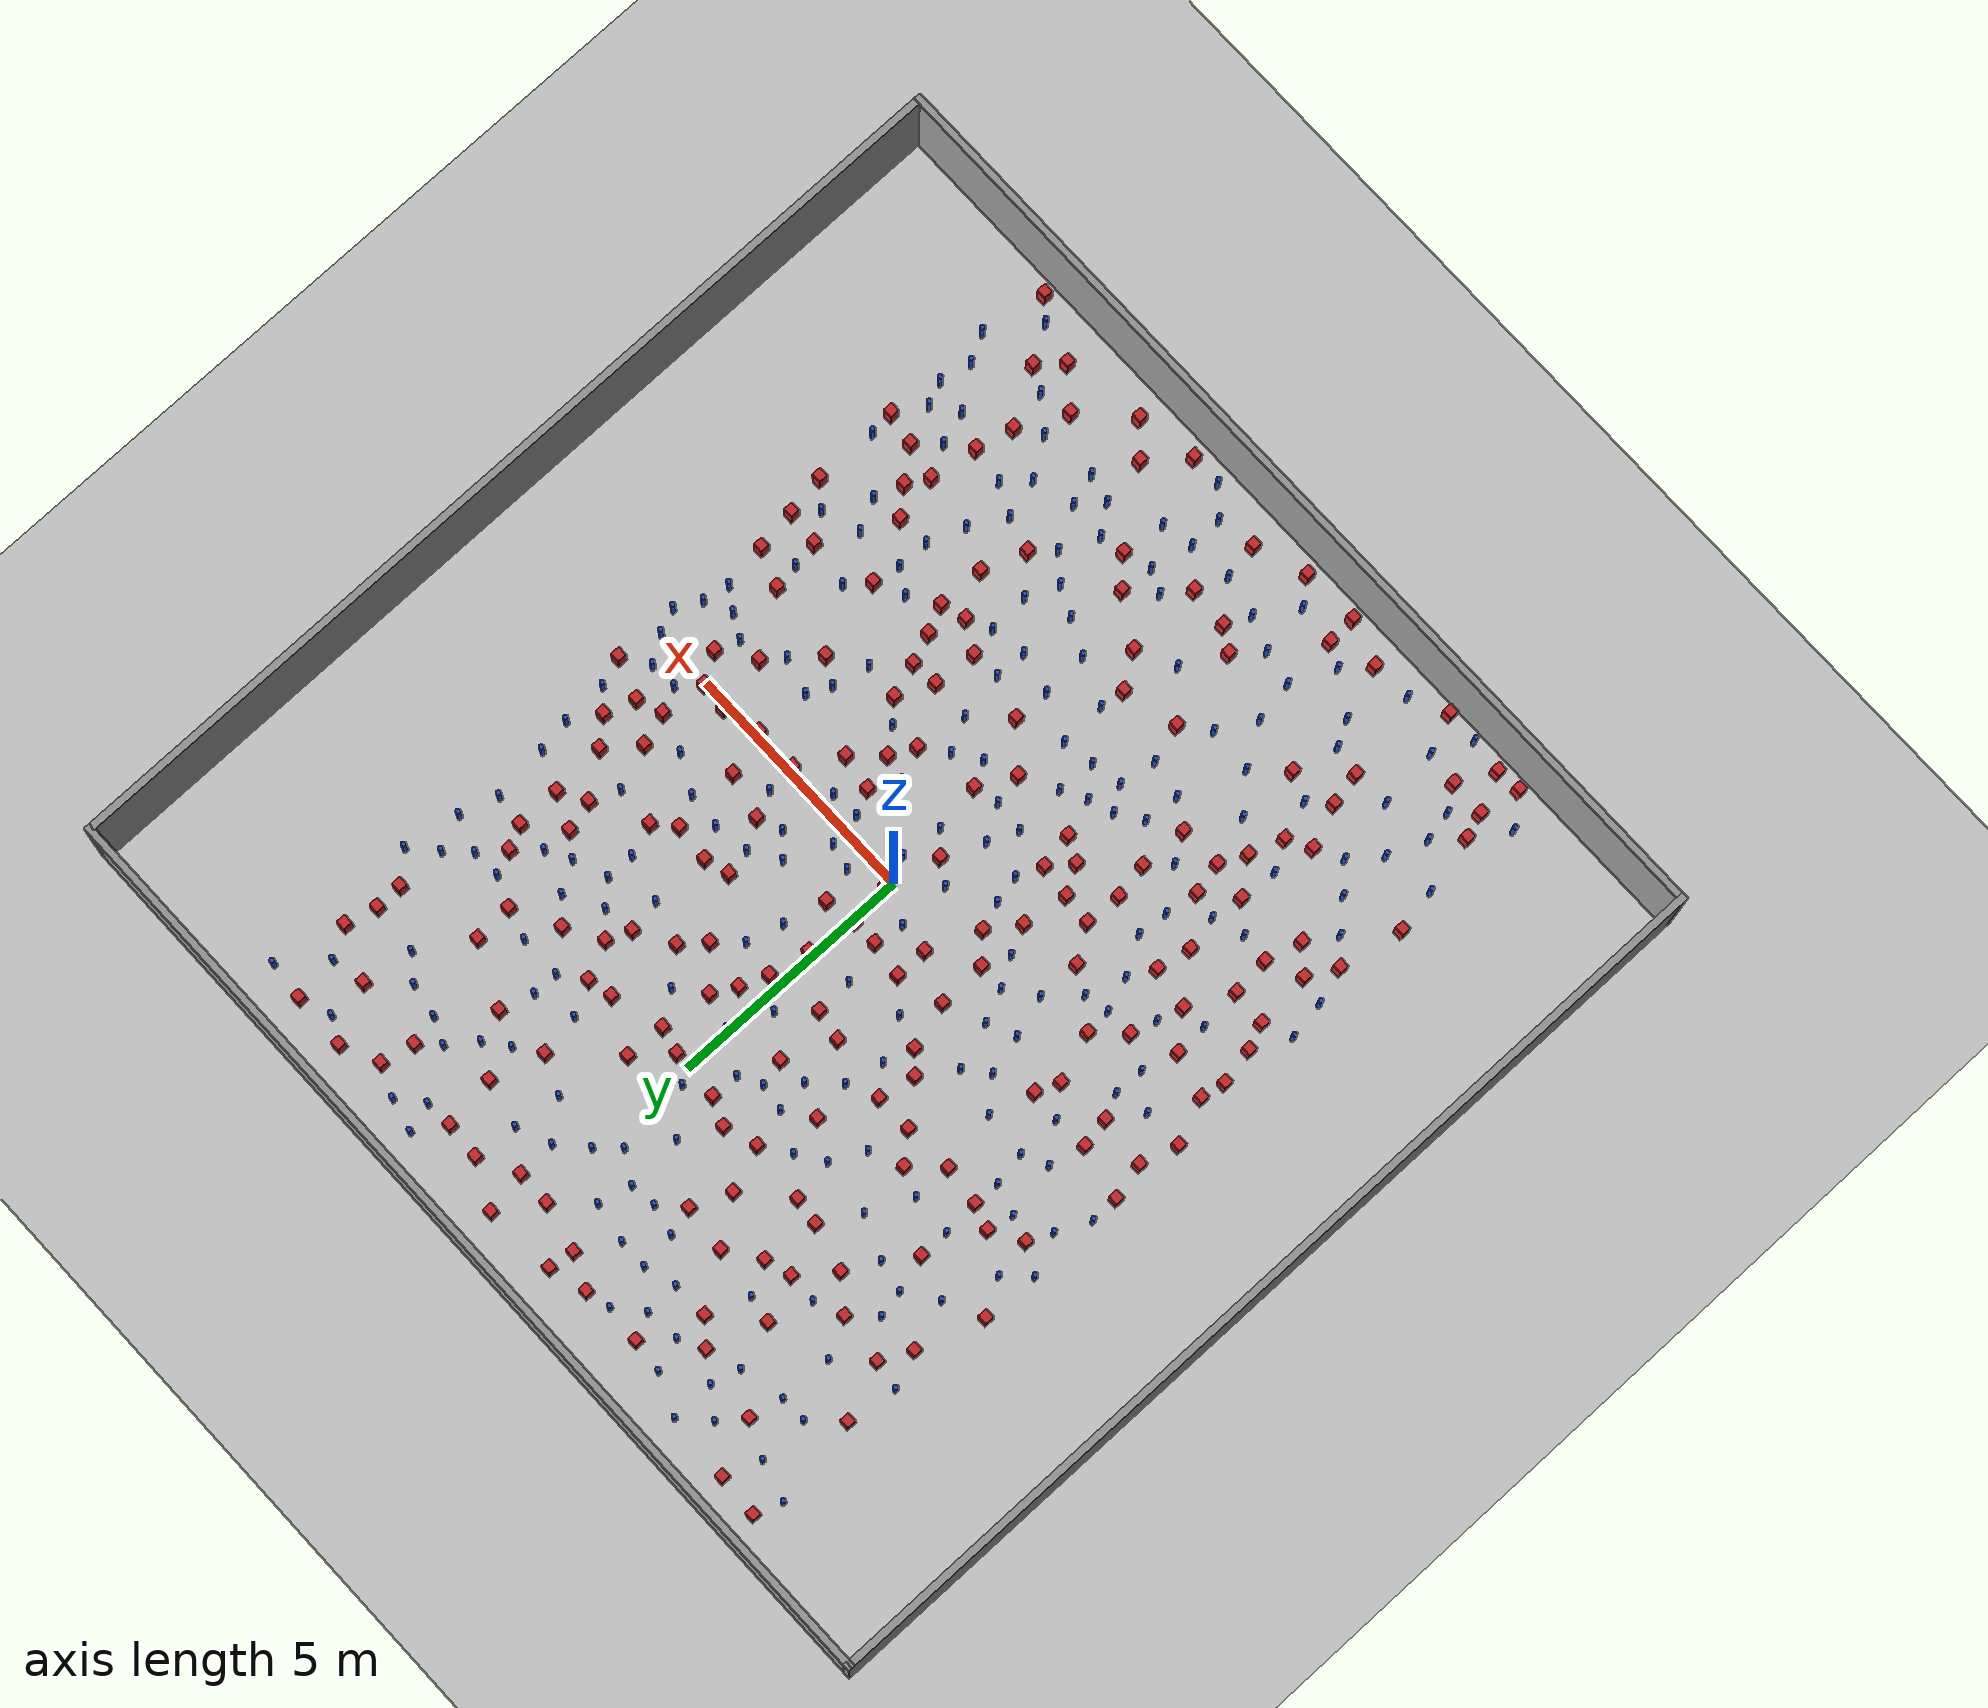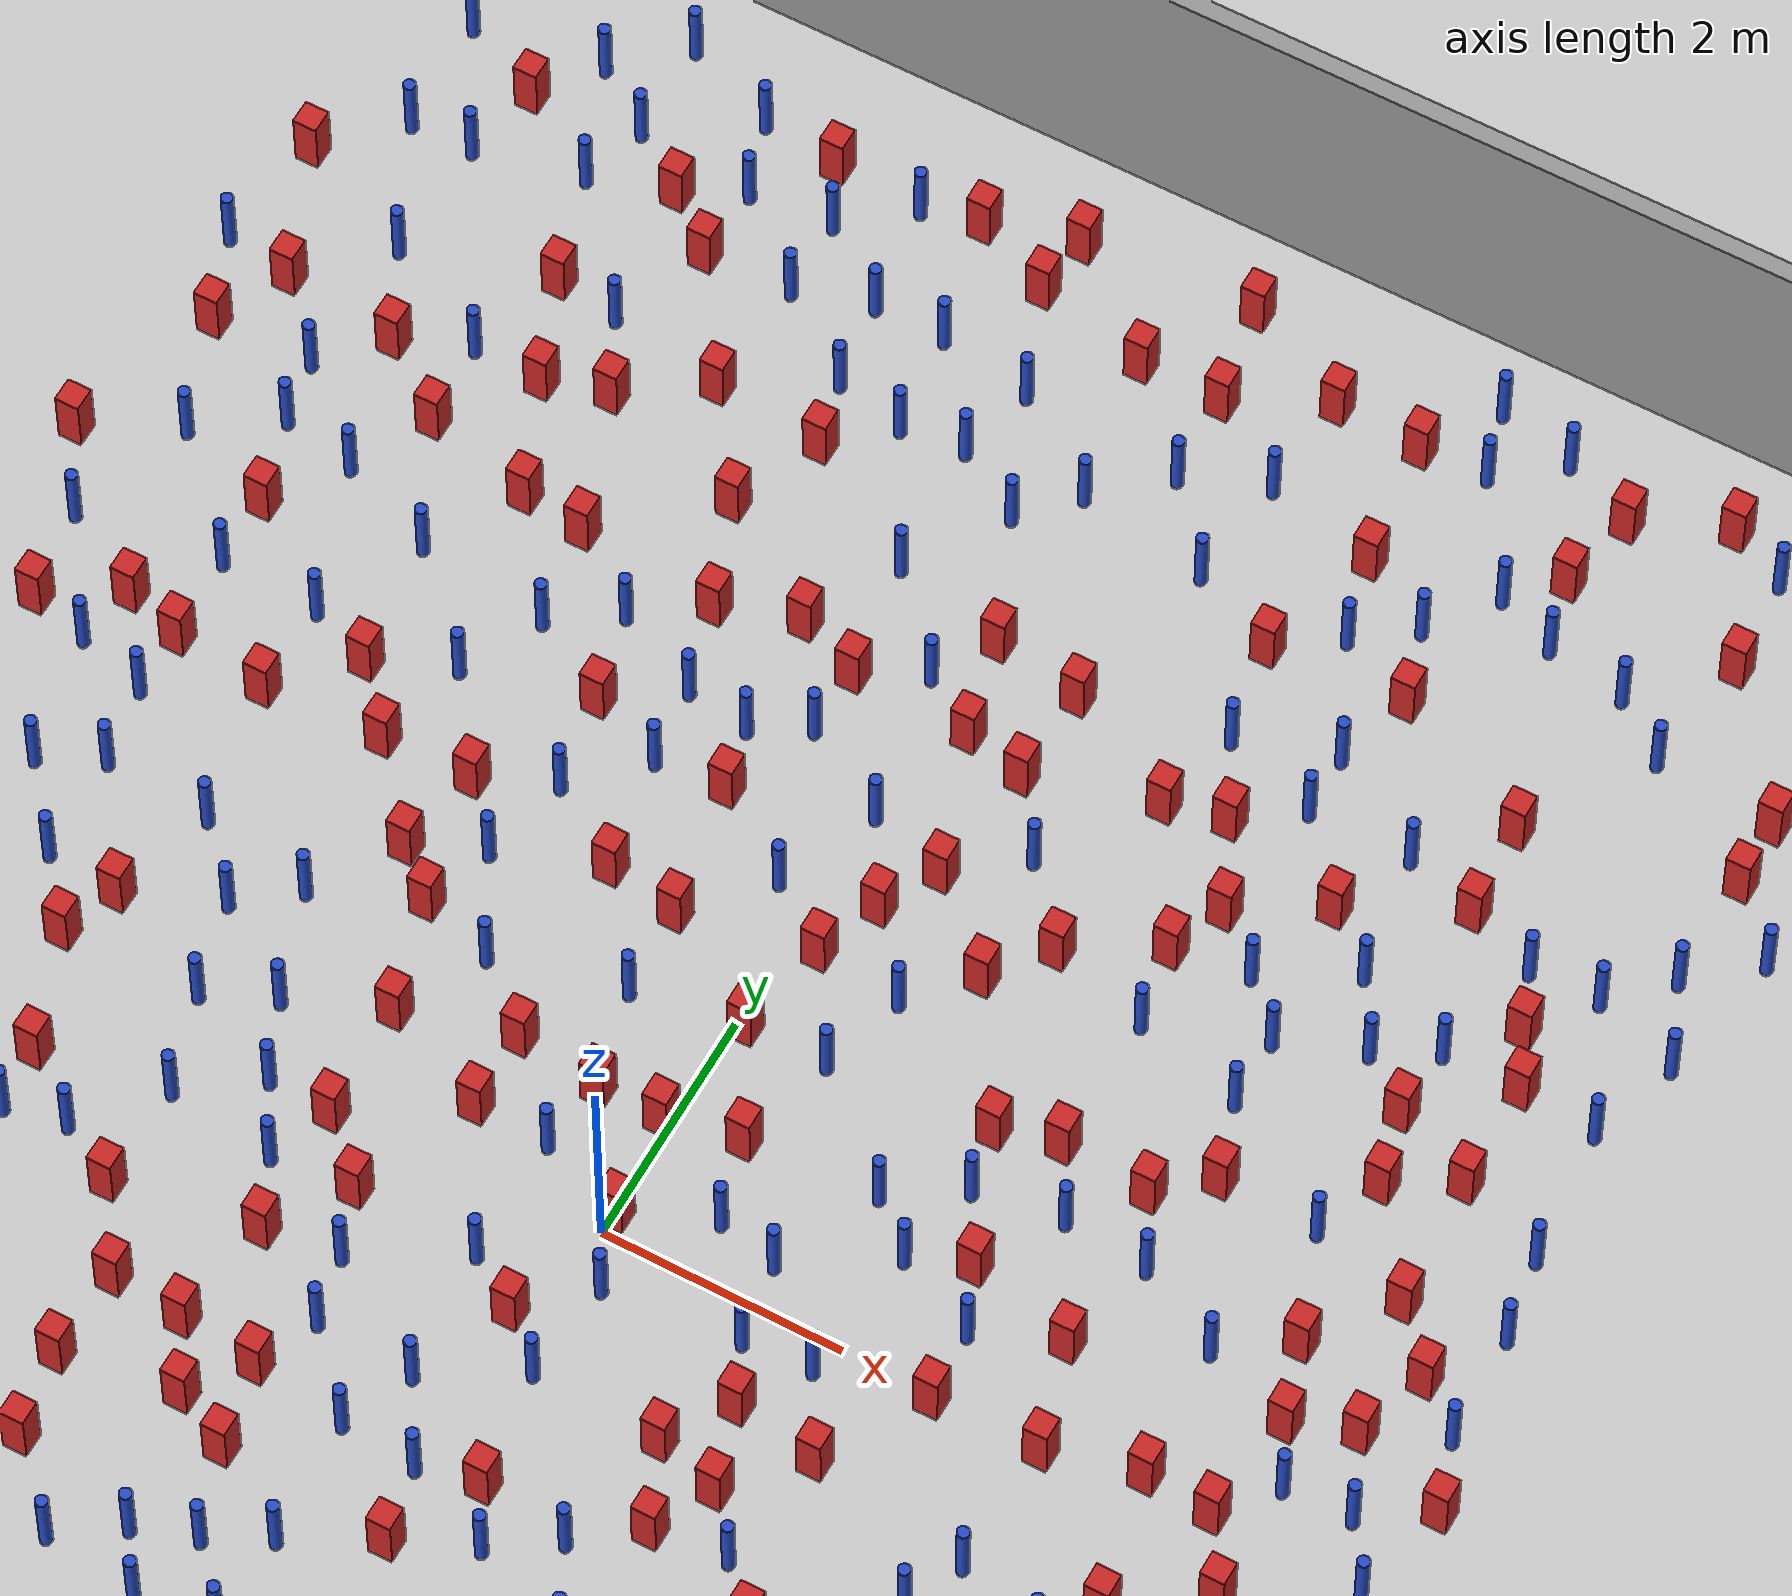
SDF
<sdf version="1.6">
 <world name="default">
  <light name="sun" type="directional">
   <pose>0 0 1000 0 -0 0</pose>
   <diffuse>0.8 0.8 0.8 1</diffuse>
   <specular>0.1 0.1 0.1 1</specular>
   <attenuation>
    <range>1000</range>
    <constant>0.9</constant>
    <linear>0.01</linear>
    <quadratic>0.001</quadratic>
   </attenuation>
   <direction>-0.5 0.5 -1</direction>
  </light>
  <model name="ground_plane">
   <static>1</static>
   <link name="link">
    <collision name="collision">
     <geometry><plane><normal>0 0 1</normal><size>100 100</size></plane></geometry>
     <surface><friction><ode><mu>100</mu><mu2>50</mu2></ode></friction></surface>
    </collision>
    <visual name="visual">
     <cast_shadows>0</cast_shadows>
     <geometry><plane><normal>0 0 1</normal><size>100 100</size></plane></geometry>
     <material>
      <ambient>1.0 1.0 1.0 1.0</ambient>
      <diffuse>0.8 0.8 0.8 1.0</diffuse>
      <specular>0.01 0.01 0.01 1.000000</specular>
     </material>
    </visual>
   </link>
  </model>
  <gravity>0 0 -9.8</gravity>
  <magnetic_field>6e-06 2.3e-05 -4.2e-05</magnetic_field>
  <atmosphere type="adiabatic"/>
  <physics name="default_physics" default="0" type="ode">
   <max_step_size>0.001</max_step_size>
   <real_time_factor>1</real_time_factor>
   <real_time_update_rate>1000</real_time_update_rate>
  </physics>
  <scene><ambient>0.4 0.4 0.4 1</ambient><background>0.7 0.7 0.7 1</background><shadows>1</shadows></scene>
  <spherical_coordinates>
   <surface_model>EARTH_WGS84</surface_model>
   <latitude_deg>0</latitude_deg>
   <longitude_deg>0</longitude_deg>
   <elevation>0</elevation>
   <heading_deg>0</heading_deg>
  </spherical_coordinates>
  <plugin name="gazebo_occupancy_map" filename="libgazebo_2Dmap_plugin.so">
   <map_resolution>0.05</map_resolution>
   <map_topic>generated_map</map_topic>
   <map_height>0.01</map_height>
   <map_size_x>50</map_size_x>
   <map_size_y>50</map_size_y>
  </plugin>
  <model name="NamedLocations">
   <static>true</static>
   <link name="DefaultStart"><pose>8.5 0 0 0 0 3.14</pose></link>
  </model>
  <model name="20x20_walls">
   <pose>0.044518 0.176112 0 0 -0 0</pose>
   <link name="Wall_1">
    <collision name="Wall_1_Collision">
     <geometry><box><size>20 0.15 2.5</size></box></geometry>
     <pose>0 0 1.25 0 -0 0</pose>
    </collision>
    <visual name="Wall_1_Visual">
     <pose>0 0 1.25 0 -0 0</pose>
     <geometry><box><size>20 0.15 2.5</size></box></geometry>
     <material>
      <script><uri>file://media/materials/scripts/gazebo.material</uri><name>Gazebo/Grey</name></script>
      <ambient>0.976471 0.992157 1 1</ambient>
     </material>
     <meta><layer>0</layer></meta>
    </visual>
    <pose>0 9.925 0 0 -0 0</pose>
   </link>
   <link name="Wall_3">
    <collision name="Wall_3_Collision">
     <geometry><box><size>20 0.15 2.5</size></box></geometry>
     <pose>0 0 1.25 0 -0 0</pose>
    </collision>
    <visual name="Wall_3_Visual">
     <pose>0 0 1.25 0 -0 0</pose>
     <geometry><box><size>20 0.15 2.5</size></box></geometry>
     <material>
      <script><uri>file://media/materials/scripts/gazebo.material</uri><name>Gazebo/Grey</name></script>
      <ambient>0.976471 0.992157 1 1</ambient>
     </material>
     <meta><layer>0</layer></meta>
    </visual>
    <pose>9.925 0 0 0 0 -1.5708</pose>
   </link>
   <link name="Wall_4">
    <collision name="Wall_4_Collision">
     <geometry><box><size>20 0.15 2.5</size></box></geometry>
     <pose>0 0 1.25 0 -0 0</pose>
    </collision>
    <visual name="Wall_4_Visual">
     <pose>0 0 1.25 0 -0 0</pose>
     <geometry><box><size>20 0.15 2.5</size></box></geometry>
     <material>
      <script><uri>file://media/materials/scripts/gazebo.material</uri><name>Gazebo/Grey</name></script>
      <ambient>0.976471 0.992157 1 1</ambient>
     </material>
     <meta><layer>0</layer></meta>
    </visual>
    <pose>0 -9.925 0 0 -0 3.14159</pose>
   </link>
   <link name="Wall_5">
    <collision name="Wall_5_Collision">
     <geometry><box><size>20 0.15 2.5</size></box></geometry>
     <pose>0 0 1.25 0 -0 0</pose>
    </collision>
    <visual name="Wall_5_Visual">
     <pose>0 0 1.25 0 -0 0</pose>
     <geometry><box><size>20 0.15 2.5</size></box></geometry>
     <material>
      <script><uri>file://media/materials/scripts/gazebo.material</uri><name>Gazebo/Grey</name></script>
      <ambient>0.976471 0.992157 1 1</ambient>
     </material>
     <meta><layer>0</layer></meta>
    </visual>
    <pose>-9.925 0 0 0 -0 1.5708</pose>
   </link>
   <static>1</static>
  </model>
  <model name="square_post_obstacle0">
   <static>true</static>
   <pose>-5.72920448468 -1.64838649978 1.91545236811e-07 -7.35059704564e-06 1.12565212e-07 2.39332434364e-05</pose>
   <link name="link">
    <pose>0 0 0.25 0 -0 0</pose>
    <inertial>
     <mass>100</mass>
     <inertia>
      <ixx>0.166667</ixx>
      <ixy>0</ixy>
      <ixz>0</ixz>
      <iyy>0.166667</iyy>
      <iyz>0</iyz>
      <izz>0.166667</izz>
     </inertia>
    </inertial>
    <collision name="collision"><geometry><box><size>.2 .2 .5</size></box></geometry></collision>
    <visual name="visual">
     <geometry><box><size>.2 .2 .5</size></box></geometry>
     <material>
      <script><name>Gazebo/Red</name><uri>file://media/materials/scripts/gazebo.material</uri></script>
     </material>
    </visual>
   </link>
  </model>
  <model name="square_post_obstacle1">
   <static>true</static>
   <pose>2.71441705244 -8.55619411679 1.91545236811e-07 -7.35059704564e-06 1.12565212e-07 2.39332434364e-05</pose>
   <link name="link">
    <pose>0 0 0.25 0 -0 0</pose>
    <inertial>
     <mass>100</mass>
     <inertia>
      <ixx>0.166667</ixx>
      <ixy>0</ixy>
      <ixz>0</ixz>
      <iyy>0.166667</iyy>
      <iyz>0</iyz>
      <izz>0.166667</izz>
     </inertia>
    </inertial>
    <collision name="collision"><geometry><box><size>.2 .2 .5</size></box></geometry></collision>
    <visual name="visual">
     <geometry><box><size>.2 .2 .5</size></box></geometry>
     <material>
      <script><name>Gazebo/Red</name><uri>file://media/materials/scripts/gazebo.material</uri></script>
     </material>
    </visual>
   </link>
  </model>
  <model name="pole_obstacle0">
   <static>true</static>
   <pose>-4.90041004545 4.79011778773 7.38925637345e-09 -8.47170692796e-08 1.24976764786e-08 -1.74513093032e-07</pose>
   <link name="link">
    <pose>0 0 0.3 0 -0 0</pose>
    <inertial>
     <mass>1</mass>
     <inertia><ixx>0.145833</ixx><ixy>0</ixy><ixz>0</ixz><iyy>0.145833</iyy><iyz>0</iyz><izz>0.125</izz></inertia>
    </inertial>
    <collision name="collision">
     <geometry><cylinder><radius>0.05</radius><length>.6</length></cylinder></geometry>
    </collision>
    <visual name="visual">
     <geometry><cylinder><radius>0.05</radius><length>.6</length></cylinder></geometry>
     <material>
      <script><name>Gazebo/Blue</name><uri>file://media/materials/scripts/gazebo.material</uri></script>
     </material>
    </visual>
   </link>
  </model>
  <model name="square_post_obstacle2">
   <static>true</static>
   <pose>4.97843061873 0.0813036156033 1.91545236811e-07 -7.35059704564e-06 1.12565212e-07 2.39332434364e-05</pose>
   <link name="link">
    <pose>0 0 0.25 0 -0 0</pose>
    <inertial>
     <mass>100</mass>
     <inertia>
      <ixx>0.166667</ixx>
      <ixy>0</ixy>
      <ixz>0</ixz>
      <iyy>0.166667</iyy>
      <iyz>0</iyz>
      <izz>0.166667</izz>
     </inertia>
    </inertial>
    <collision name="collision"><geometry><box><size>.2 .2 .5</size></box></geometry></collision>
    <visual name="visual">
     <geometry><box><size>.2 .2 .5</size></box></geometry>
     <material>
      <script><name>Gazebo/Red</name><uri>file://media/materials/scripts/gazebo.material</uri></script>
     </material>
    </visual>
   </link>
  </model>
  <model name="pole_obstacle1">
   <static>true</static>
   <pose>-6.14865778615 4.48275335902 7.38925637345e-09 -8.47170692796e-08 1.24976764786e-08 -1.74513093032e-07</pose>
   <link name="link">
    <pose>0 0 0.3 0 -0 0</pose>
    <inertial>
     <mass>1</mass>
     <inertia><ixx>0.145833</ixx><ixy>0</ixy><ixz>0</ixz><iyy>0.145833</iyy><iyz>0</iyz><izz>0.125</izz></inertia>
    </inertial>
    <collision name="collision">
     <geometry><cylinder><radius>0.05</radius><length>.6</length></cylinder></geometry>
    </collision>
    <visual name="visual">
     <geometry><cylinder><radius>0.05</radius><length>.6</length></cylinder></geometry>
     <material>
      <script><name>Gazebo/Blue</name><uri>file://media/materials/scripts/gazebo.material</uri></script>
     </material>
    </visual>
   </link>
  </model>
  <model name="square_post_obstacle3">
   <static>true</static>
   <pose>3.8937766651 -1.8984932603 1.91545236811e-07 -7.35059704564e-06 1.12565212e-07 2.39332434364e-05</pose>
   <link name="link">
    <pose>0 0 0.25 0 -0 0</pose>
    <inertial>
     <mass>100</mass>
     <inertia>
      <ixx>0.166667</ixx>
      <ixy>0</ixy>
      <ixz>0</ixz>
      <iyy>0.166667</iyy>
      <iyz>0</iyz>
      <izz>0.166667</izz>
     </inertia>
    </inertial>
    <collision name="collision"><geometry><box><size>.2 .2 .5</size></box></geometry></collision>
    <visual name="visual">
     <geometry><box><size>.2 .2 .5</size></box></geometry>
     <material>
      <script><name>Gazebo/Red</name><uri>file://media/materials/scripts/gazebo.material</uri></script>
     </material>
    </visual>
   </link>
  </model>
  <model name="pole_obstacle2">
   <static>true</static>
   <pose>-4.06735478396 4.44115292767 7.38925637345e-09 -8.47170692796e-08 1.24976764786e-08 -1.74513093032e-07</pose>
   <link name="link">
    <pose>0 0 0.3 0 -0 0</pose>
    <inertial>
     <mass>1</mass>
     <inertia><ixx>0.145833</ixx><ixy>0</ixy><ixz>0</ixz><iyy>0.145833</iyy><iyz>0</iyz><izz>0.125</izz></inertia>
    </inertial>
    <collision name="collision">
     <geometry><cylinder><radius>0.05</radius><length>.6</length></cylinder></geometry>
    </collision>
    <visual name="visual">
     <geometry><cylinder><radius>0.05</radius><length>.6</length></cylinder></geometry>
     <material>
      <script><name>Gazebo/Blue</name><uri>file://media/materials/scripts/gazebo.material</uri></script>
     </material>
    </visual>
   </link>
  </model>
  <model name="pole_obstacle3">
   <static>true</static>
   <pose>-2.27383055472 -6.87822808617 7.38925637345e-09 -8.47170692798e-08 1.24976765033e-08 -1.74513093019e-07</pose>
   <link name="link">
    <pose>0 0 0.3 0 -0 0</pose>
    <inertial>
     <mass>1</mass>
     <inertia><ixx>0.145833</ixx><ixy>0</ixy><ixz>0</ixz><iyy>0.145833</iyy><iyz>0</iyz><izz>0.125</izz></inertia>
    </inertial>
    <collision name="collision">
     <geometry><cylinder><radius>0.05</radius><length>.6</length></cylinder></geometry>
    </collision>
    <visual name="visual">
     <geometry><cylinder><radius>0.05</radius><length>.6</length></cylinder></geometry>
     <material>
      <script><name>Gazebo/Blue</name><uri>file://media/materials/scripts/gazebo.material</uri></script>
     </material>
    </visual>
   </link>
  </model>
  <model name="square_post_obstacle4">
   <static>true</static>
   <pose>0.572634909686 8.47623324457 1.91545236811e-07 -7.35059704564e-06 1.12565212e-07 2.39332434364e-05</pose>
   <link name="link">
    <pose>0 0 0.25 0 -0 0</pose>
    <inertial>
     <mass>100</mass>
     <inertia>
      <ixx>0.166667</ixx>
      <ixy>0</ixy>
      <ixz>0</ixz>
      <iyy>0.166667</iyy>
      <iyz>0</iyz>
      <izz>0.166667</izz>
     </inertia>
    </inertial>
    <collision name="collision"><geometry><box><size>.2 .2 .5</size></box></geometry></collision>
    <visual name="visual">
     <geometry><box><size>.2 .2 .5</size></box></geometry>
     <material>
      <script><name>Gazebo/Red</name><uri>file://media/materials/scripts/gazebo.material</uri></script>
     </material>
    </visual>
   </link>
  </model>
  <model name="square_post_obstacle5">
   <static>true</static>
   <pose>4.78544874691 3.06390255872 1.91545236811e-07 -7.35059704564e-06 1.12565212e-07 2.39332434364e-05</pose>
   <link name="link">
    <pose>0 0 0.25 0 -0 0</pose>
    <inertial>
     <mass>100</mass>
     <inertia>
      <ixx>0.166667</ixx>
      <ixy>0</ixy>
      <ixz>0</ixz>
      <iyy>0.166667</iyy>
      <iyz>0</iyz>
      <izz>0.166667</izz>
     </inertia>
    </inertial>
    <collision name="collision"><geometry><box><size>.2 .2 .5</size></box></geometry></collision>
    <visual name="visual">
     <geometry><box><size>.2 .2 .5</size></box></geometry>
     <material>
      <script><name>Gazebo/Red</name><uri>file://media/materials/scripts/gazebo.material</uri></script>
     </material>
    </visual>
   </link>
  </model>
  <model name="square_post_obstacle6">
   <static>true</static>
   <pose>6.07012027217 7.79217933914 1.91545236811e-07 -7.35059704564e-06 1.12565212e-07 2.39332434364e-05</pose>
   <link name="link">
    <pose>0 0 0.25 0 -0 0</pose>
    <inertial>
     <mass>100</mass>
     <inertia>
      <ixx>0.166667</ixx>
      <ixy>0</ixy>
      <ixz>0</ixz>
      <iyy>0.166667</iyy>
      <iyz>0</iyz>
      <izz>0.166667</izz>
     </inertia>
    </inertial>
    <collision name="collision"><geometry><box><size>.2 .2 .5</size></box></geometry></collision>
    <visual name="visual">
     <geometry><box><size>.2 .2 .5</size></box></geometry>
     <material>
      <script><name>Gazebo/Red</name><uri>file://media/materials/scripts/gazebo.material</uri></script>
     </material>
    </visual>
   </link>
  </model>
  <model name="pole_obstacle4">
   <static>true</static>
   <pose>1.04166894507 -2.35484419023 7.38925637345e-09 -8.471706928e-08 1.2497676505e-08 -1.74513093017e-07</pose>
   <link name="link">
    <pose>0 0 0.3 0 -0 0</pose>
    <inertial>
     <mass>1</mass>
     <inertia><ixx>0.145833</ixx><ixy>0</ixy><ixz>0</ixz><iyy>0.145833</iyy><iyz>0</iyz><izz>0.125</izz></inertia>
    </inertial>
    <collision name="collision">
     <geometry><cylinder><radius>0.05</radius><length>.6</length></cylinder></geometry>
    </collision>
    <visual name="visual">
     <geometry><cylinder><radius>0.05</radius><length>.6</length></cylinder></geometry>
     <material>
      <script><name>Gazebo/Blue</name><uri>file://media/materials/scripts/gazebo.material</uri></script>
     </material>
    </visual>
   </link>
  </model>
  <model name="pole_obstacle5">
   <static>true</static>
   <pose>2.26358996405 -5.2780489103 7.38925637345e-09 -8.47170692798e-08 1.24976765033e-08 -1.74513093019e-07</pose>
   <link name="link">
    <pose>0 0 0.3 0 -0 0</pose>
    <inertial>
     <mass>1</mass>
     <inertia><ixx>0.145833</ixx><ixy>0</ixy><ixz>0</ixz><iyy>0.145833</iyy><iyz>0</iyz><izz>0.125</izz></inertia>
    </inertial>
    <collision name="collision">
     <geometry><cylinder><radius>0.05</radius><length>.6</length></cylinder></geometry>
    </collision>
    <visual name="visual">
     <geometry><cylinder><radius>0.05</radius><length>.6</length></cylinder></geometry>
     <material>
      <script><name>Gazebo/Blue</name><uri>file://media/materials/scripts/gazebo.material</uri></script>
     </material>
    </visual>
   </link>
  </model>
  <model name="square_post_obstacle7">
   <static>true</static>
   <pose>-3.08108720466 5.1367049342 1.91545236811e-07 -7.35059704564e-06 1.12565212e-07 2.39332434364e-05</pose>
   <link name="link">
    <pose>0 0 0.25 0 -0 0</pose>
    <inertial>
     <mass>100</mass>
     <inertia>
      <ixx>0.166667</ixx>
      <ixy>0</ixy>
      <ixz>0</ixz>
      <iyy>0.166667</iyy>
      <iyz>0</iyz>
      <izz>0.166667</izz>
     </inertia>
    </inertial>
    <collision name="collision"><geometry><box><size>.2 .2 .5</size></box></geometry></collision>
    <visual name="visual">
     <geometry><box><size>.2 .2 .5</size></box></geometry>
     <material>
      <script><name>Gazebo/Red</name><uri>file://media/materials/scripts/gazebo.material</uri></script>
     </material>
    </visual>
   </link>
  </model>
  <model name="square_post_obstacle8">
   <static>true</static>
   <pose>-5.75430322455 -4.65461936837 1.91545236811e-07 -7.35059704564e-06 1.12565212e-07 2.39332434364e-05</pose>
   <link name="link">
    <pose>0 0 0.25 0 -0 0</pose>
    <inertial>
     <mass>100</mass>
     <inertia>
      <ixx>0.166667</ixx>
      <ixy>0</ixy>
      <ixz>0</ixz>
      <iyy>0.166667</iyy>
      <iyz>0</iyz>
      <izz>0.166667</izz>
     </inertia>
    </inertial>
    <collision name="collision"><geometry><box><size>.2 .2 .5</size></box></geometry></collision>
    <visual name="visual">
     <geometry><box><size>.2 .2 .5</size></box></geometry>
     <material>
      <script><name>Gazebo/Red</name><uri>file://media/materials/scripts/gazebo.material</uri></script>
     </material>
    </visual>
   </link>
  </model>
  <model name="pole_obstacle6">
   <static>true</static>
   <pose>5.61509439641 -1.19399128094 7.38925637345e-09 -8.471706928e-08 1.24976765134e-08 -1.74513093015e-07</pose>
   <link name="link">
    <pose>0 0 0.3 0 -0 0</pose>
    <inertial>
     <mass>1</mass>
     <inertia><ixx>0.145833</ixx><ixy>0</ixy><ixz>0</ixz><iyy>0.145833</iyy><iyz>0</iyz><izz>0.125</izz></inertia>
    </inertial>
    <collision name="collision">
     <geometry><cylinder><radius>0.05</radius><length>.6</length></cylinder></geometry>
    </collision>
    <visual name="visual">
     <geometry><cylinder><radius>0.05</radius><length>.6</length></cylinder></geometry>
     <material>
      <script><name>Gazebo/Blue</name><uri>file://media/materials/scripts/gazebo.material</uri></script>
     </material>
    </visual>
   </link>
  </model>
  <model name="pole_obstacle7">
   <static>true</static>
   <pose>-0.77089150769 -8.09330029917 7.38925637345e-09 -8.47170692797e-08 1.249767648e-08 -1.74513093032e-07</pose>
   <link name="link">
    <pose>0 0 0.3 0 -0 0</pose>
    <inertial>
     <mass>1</mass>
     <inertia><ixx>0.145833</ixx><ixy>0</ixy><ixz>0</ixz><iyy>0.145833</iyy><iyz>0</iyz><izz>0.125</izz></inertia>
    </inertial>
    <collision name="collision">
     <geometry><cylinder><radius>0.05</radius><length>.6</length></cylinder></geometry>
    </collision>
    <visual name="visual">
     <geometry><cylinder><radius>0.05</radius><length>.6</length></cylinder></geometry>
     <material>
      <script><name>Gazebo/Blue</name><uri>file://media/materials/scripts/gazebo.material</uri></script>
     </material>
    </visual>
   </link>
  </model>
  <model name="square_post_obstacle9">
   <static>true</static>
   <pose>4.31915654539 -3.44956911372 1.91545236811e-07 -7.35059704564e-06 1.12565212e-07 2.39332434364e-05</pose>
   <link name="link">
    <pose>0 0 0.25 0 -0 0</pose>
    <inertial>
     <mass>100</mass>
     <inertia>
      <ixx>0.166667</ixx>
      <ixy>0</ixy>
      <ixz>0</ixz>
      <iyy>0.166667</iyy>
      <iyz>0</iyz>
      <izz>0.166667</izz>
     </inertia>
    </inertial>
    <collision name="collision"><geometry><box><size>.2 .2 .5</size></box></geometry></collision>
    <visual name="visual">
     <geometry><box><size>.2 .2 .5</size></box></geometry>
     <material>
      <script><name>Gazebo/Red</name><uri>file://media/materials/scripts/gazebo.material</uri></script>
     </material>
    </visual>
   </link>
  </model>
  <model name="square_post_obstacle10">
   <static>true</static>
   <pose>-2.15162310492 -1.19387111334 1.91545236811e-07 -7.35059704564e-06 1.12565212e-07 2.39332434364e-05</pose>
   <link name="link">
    <pose>0 0 0.25 0 -0 0</pose>
    <inertial>
     <mass>100</mass>
     <inertia>
      <ixx>0.166667</ixx>
      <ixy>0</ixy>
      <ixz>0</ixz>
      <iyy>0.166667</iyy>
      <iyz>0</iyz>
      <izz>0.166667</izz>
     </inertia>
    </inertial>
    <collision name="collision"><geometry><box><size>.2 .2 .5</size></box></geometry></collision>
    <visual name="visual">
     <geometry><box><size>.2 .2 .5</size></box></geometry>
     <material>
      <script><name>Gazebo/Red</name><uri>file://media/materials/scripts/gazebo.material</uri></script>
     </material>
    </visual>
   </link>
  </model>
  <model name="square_post_obstacle11">
   <static>true</static>
   <pose>4.62874711738 3.66737557755 1.91545236811e-07 -7.35059704564e-06 1.12565212e-07 2.39332434364e-05</pose>
   <link name="link">
    <pose>0 0 0.25 0 -0 0</pose>
    <inertial>
     <mass>100</mass>
     <inertia>
      <ixx>0.166667</ixx>
      <ixy>0</ixy>
      <ixz>0</ixz>
      <iyy>0.166667</iyy>
      <iyz>0</iyz>
      <izz>0.166667</izz>
     </inertia>
    </inertial>
    <collision name="collision"><geometry><box><size>.2 .2 .5</size></box></geometry></collision>
    <visual name="visual">
     <geometry><box><size>.2 .2 .5</size></box></geometry>
     <material>
      <script><name>Gazebo/Red</name><uri>file://media/materials/scripts/gazebo.material</uri></script>
     </material>
    </visual>
   </link>
  </model>
  <model name="square_post_obstacle12">
   <static>true</static>
   <pose>2.49780389506 -2.29794122637 1.91545236811e-07 -7.35059704564e-06 1.12565212e-07 2.39332434364e-05</pose>
   <link name="link">
    <pose>0 0 0.25 0 -0 0</pose>
    <inertial>
     <mass>100</mass>
     <inertia>
      <ixx>0.166667</ixx>
      <ixy>0</ixy>
      <ixz>0</ixz>
      <iyy>0.166667</iyy>
      <iyz>0</iyz>
      <izz>0.166667</izz>
     </inertia>
    </inertial>
    <collision name="collision"><geometry><box><size>.2 .2 .5</size></box></geometry></collision>
    <visual name="visual">
     <geometry><box><size>.2 .2 .5</size></box></geometry>
     <material>
      <script><name>Gazebo/Red</name><uri>file://media/materials/scripts/gazebo.material</uri></script>
     </material>
    </visual>
   </link>
  </model>
  <model name="square_post_obstacle13">
   <static>true</static>
   <pose>3.41197336241 0.803505202725 1.91545236811e-07 -7.35059704564e-06 1.12565212e-07 2.39332434364e-05</pose>
   <link name="link">
    <pose>0 0 0.25 0 -0 0</pose>
    <inertial>
     <mass>100</mass>
     <inertia>
      <ixx>0.166667</ixx>
      <ixy>0</ixy>
      <ixz>0</ixz>
      <iyy>0.166667</iyy>
      <iyz>0</iyz>
      <izz>0.166667</izz>
     </inertia>
    </inertial>
    <collision name="collision"><geometry><box><size>.2 .2 .5</size></box></geometry></collision>
    <visual name="visual">
     <geometry><box><size>.2 .2 .5</size></box></geometry>
     <material>
      <script><name>Gazebo/Red</name><uri>file://media/materials/scripts/gazebo.material</uri></script>
     </material>
    </visual>
   </link>
  </model>
  <model name="pole_obstacle8">
   <static>true</static>
   <pose>-5.04666065523 -1.76279516387 7.38925637345e-09 -8.471706928e-08 1.24976765134e-08 -1.74513093015e-07</pose>
   <link name="link">
    <pose>0 0 0.3 0 -0 0</pose>
    <inertial>
     <mass>1</mass>
     <inertia><ixx>0.145833</ixx><ixy>0</ixy><ixz>0</ixz><iyy>0.145833</iyy><iyz>0</iyz><izz>0.125</izz></inertia>
    </inertial>
    <collision name="collision">
     <geometry><cylinder><radius>0.05</radius><length>.6</length></cylinder></geometry>
    </collision>
    <visual name="visual">
     <geometry><cylinder><radius>0.05</radius><length>.6</length></cylinder></geometry>
     <material>
      <script><name>Gazebo/Blue</name><uri>file://media/materials/scripts/gazebo.material</uri></script>
     </material>
    </visual>
   </link>
  </model>
  <model name="square_post_obstacle14">
   <static>true</static>
   <pose>-4.17409091817 -5.71270492682 1.91545236811e-07 -7.35059704564e-06 1.12565212e-07 2.39332434364e-05</pose>
   <link name="link">
    <pose>0 0 0.25 0 -0 0</pose>
    <inertial>
     <mass>100</mass>
     <inertia>
      <ixx>0.166667</ixx>
      <ixy>0</ixy>
      <ixz>0</ixz>
      <iyy>0.166667</iyy>
      <iyz>0</iyz>
      <izz>0.166667</izz>
     </inertia>
    </inertial>
    <collision name="collision"><geometry><box><size>.2 .2 .5</size></box></geometry></collision>
    <visual name="visual">
     <geometry><box><size>.2 .2 .5</size></box></geometry>
     <material>
      <script><name>Gazebo/Red</name><uri>file://media/materials/scripts/gazebo.material</uri></script>
     </material>
    </visual>
   </link>
  </model>
  <model name="square_post_obstacle15">
   <static>true</static>
   <pose>-5.38946317511 8.39628046984 1.91545236811e-07 -7.35059704564e-06 1.12565212e-07 2.39332434364e-05</pose>
   <link name="link">
    <pose>0 0 0.25 0 -0 0</pose>
    <inertial>
     <mass>100</mass>
     <inertia>
      <ixx>0.166667</ixx>
      <ixy>0</ixy>
      <ixz>0</ixz>
      <iyy>0.166667</iyy>
      <iyz>0</iyz>
      <izz>0.166667</izz>
     </inertia>
    </inertial>
    <collision name="collision"><geometry><box><size>.2 .2 .5</size></box></geometry></collision>
    <visual name="visual">
     <geometry><box><size>.2 .2 .5</size></box></geometry>
     <material>
      <script><name>Gazebo/Red</name><uri>file://media/materials/scripts/gazebo.material</uri></script>
     </material>
    </visual>
   </link>
  </model>
  <model name="square_post_obstacle16">
   <static>true</static>
   <pose>6.16754811721 -2.38973344418 1.91545236811e-07 -7.35059704564e-06 1.12565212e-07 2.39332434364e-05</pose>
   <link name="link">
    <pose>0 0 0.25 0 -0 0</pose>
    <inertial>
     <mass>100</mass>
     <inertia>
      <ixx>0.166667</ixx>
      <ixy>0</ixy>
      <ixz>0</ixz>
      <iyy>0.166667</iyy>
      <iyz>0</iyz>
      <izz>0.166667</izz>
     </inertia>
    </inertial>
    <collision name="collision"><geometry><box><size>.2 .2 .5</size></box></geometry></collision>
    <visual name="visual">
     <geometry><box><size>.2 .2 .5</size></box></geometry>
     <material>
      <script><name>Gazebo/Red</name><uri>file://media/materials/scripts/gazebo.material</uri></script>
     </material>
    </visual>
   </link>
  </model>
  <model name="pole_obstacle9">
   <static>true</static>
   <pose>0.733993207891 0.471008192793 7.38925637345e-09 -8.471706928e-08 1.24976765086e-08 -1.74513093015e-07</pose>
   <link name="link">
    <pose>0 0 0.3 0 -0 0</pose>
    <inertial>
     <mass>1</mass>
     <inertia><ixx>0.145833</ixx><ixy>0</ixy><ixz>0</ixz><iyy>0.145833</iyy><iyz>0</iyz><izz>0.125</izz></inertia>
    </inertial>
    <collision name="collision">
     <geometry><cylinder><radius>0.05</radius><length>.6</length></cylinder></geometry>
    </collision>
    <visual name="visual">
     <geometry><cylinder><radius>0.05</radius><length>.6</length></cylinder></geometry>
     <material>
      <script><name>Gazebo/Blue</name><uri>file://media/materials/scripts/gazebo.material</uri></script>
     </material>
    </visual>
   </link>
  </model>
  <model name="square_post_obstacle17">
   <static>true</static>
   <pose>-3.33447959467 -1.3979767333 1.91545236811e-07 -7.35059704564e-06 1.12565212e-07 2.39332434364e-05</pose>
   <link name="link">
    <pose>0 0 0.25 0 -0 0</pose>
    <inertial>
     <mass>100</mass>
     <inertia>
      <ixx>0.166667</ixx>
      <ixy>0</ixy>
      <ixz>0</ixz>
      <iyy>0.166667</iyy>
      <iyz>0</iyz>
      <izz>0.166667</izz>
     </inertia>
    </inertial>
    <collision name="collision"><geometry><box><size>.2 .2 .5</size></box></geometry></collision>
    <visual name="visual">
     <geometry><box><size>.2 .2 .5</size></box></geometry>
     <material>
      <script><name>Gazebo/Red</name><uri>file://media/materials/scripts/gazebo.material</uri></script>
     </material>
    </visual>
   </link>
  </model>
  <model name="square_post_obstacle18">
   <static>true</static>
   <pose>1.35517018859 8.86539463981 1.91545236811e-07 -7.35059704564e-06 1.12565212e-07 2.39332434364e-05</pose>
   <link name="link">
    <pose>0 0 0.25 0 -0 0</pose>
    <inertial>
     <mass>100</mass>
     <inertia>
      <ixx>0.166667</ixx>
      <ixy>0</ixy>
      <ixz>0</ixz>
      <iyy>0.166667</iyy>
      <iyz>0</iyz>
      <izz>0.166667</izz>
     </inertia>
    </inertial>
    <collision name="collision"><geometry><box><size>.2 .2 .5</size></box></geometry></collision>
    <visual name="visual">
     <geometry><box><size>.2 .2 .5</size></box></geometry>
     <material>
      <script><name>Gazebo/Red</name><uri>file://media/materials/scripts/gazebo.material</uri></script>
     </material>
    </visual>
   </link>
  </model>
  <model name="pole_obstacle10">
   <static>true</static>
   <pose>0.0678419629174 7.22981493726 7.38925637345e-09 -8.47170692798e-08 1.24976765034e-08 -1.74513093019e-07</pose>
   <link name="link">
    <pose>0 0 0.3 0 -0 0</pose>
    <inertial>
     <mass>1</mass>
     <inertia><ixx>0.145833</ixx><ixy>0</ixy><ixz>0</ixz><iyy>0.145833</iyy><iyz>0</iyz><izz>0.125</izz></inertia>
    </inertial>
    <collision name="collision">
     <geometry><cylinder><radius>0.05</radius><length>.6</length></cylinder></geometry>
    </collision>
    <visual name="visual">
     <geometry><cylinder><radius>0.05</radius><length>.6</length></cylinder></geometry>
     <material>
      <script><name>Gazebo/Blue</name><uri>file://media/materials/scripts/gazebo.material</uri></script>
     </material>
    </visual>
   </link>
  </model>
  <model name="square_post_obstacle19">
   <static>true</static>
   <pose>5.28989070579 -5.09956356859 1.91545236811e-07 -7.35059704564e-06 1.12565212e-07 2.39332434364e-05</pose>
   <link name="link">
    <pose>0 0 0.25 0 -0 0</pose>
    <inertial>
     <mass>100</mass>
     <inertia>
      <ixx>0.166667</ixx>
      <ixy>0</ixy>
      <ixz>0</ixz>
      <iyy>0.166667</iyy>
      <iyz>0</iyz>
      <izz>0.166667</izz>
     </inertia>
    </inertial>
    <collision name="collision"><geometry><box><size>.2 .2 .5</size></box></geometry></collision>
    <visual name="visual">
     <geometry><box><size>.2 .2 .5</size></box></geometry>
     <material>
      <script><name>Gazebo/Red</name><uri>file://media/materials/scripts/gazebo.material</uri></script>
     </material>
    </visual>
   </link>
  </model>
  <model name="pole_obstacle11">
   <static>true</static>
   <pose>4.66672874575 4.24998226761 7.38925637345e-09 -8.47170692796e-08 1.24976764786e-08 -1.74513093032e-07</pose>
   <link name="link">
    <pose>0 0 0.3 0 -0 0</pose>
    <inertial>
     <mass>1</mass>
     <inertia><ixx>0.145833</ixx><ixy>0</ixy><ixz>0</ixz><iyy>0.145833</iyy><iyz>0</iyz><izz>0.125</izz></inertia>
    </inertial>
    <collision name="collision">
     <geometry><cylinder><radius>0.05</radius><length>.6</length></cylinder></geometry>
    </collision>
    <visual name="visual">
     <geometry><cylinder><radius>0.05</radius><length>.6</length></cylinder></geometry>
     <material>
      <script><name>Gazebo/Blue</name><uri>file://media/materials/scripts/gazebo.material</uri></script>
     </material>
    </visual>
   </link>
  </model>
  <model name="square_post_obstacle20">
   <static>true</static>
   <pose>-3.6914915848 -4.50716384659 1.91545236811e-07 -7.35059704564e-06 1.12565212e-07 2.39332434364e-05</pose>
   <link name="link">
    <pose>0 0 0.25 0 -0 0</pose>
    <inertial>
     <mass>100</mass>
     <inertia>
      <ixx>0.166667</ixx>
      <ixy>0</ixy>
      <ixz>0</ixz>
      <iyy>0.166667</iyy>
      <iyz>0</iyz>
      <izz>0.166667</izz>
     </inertia>
    </inertial>
    <collision name="collision"><geometry><box><size>.2 .2 .5</size></box></geometry></collision>
    <visual name="visual">
     <geometry><box><size>.2 .2 .5</size></box></geometry>
     <material>
      <script><name>Gazebo/Red</name><uri>file://media/materials/scripts/gazebo.material</uri></script>
     </material>
    </visual>
   </link>
  </model>
  <model name="pole_obstacle12">
   <static>true</static>
   <pose>4.33866164105 -1.3552663525 7.38925637345e-09 -8.471706928e-08 1.24976765134e-08 -1.74513093015e-07</pose>
   <link name="link">
    <pose>0 0 0.3 0 -0 0</pose>
    <inertial>
     <mass>1</mass>
     <inertia><ixx>0.145833</ixx><ixy>0</ixy><ixz>0</ixz><iyy>0.145833</iyy><iyz>0</iyz><izz>0.125</izz></inertia>
    </inertial>
    <collision name="collision">
     <geometry><cylinder><radius>0.05</radius><length>.6</length></cylinder></geometry>
    </collision>
    <visual name="visual">
     <geometry><cylinder><radius>0.05</radius><length>.6</length></cylinder></geometry>
     <material>
      <script><name>Gazebo/Blue</name><uri>file://media/materials/scripts/gazebo.material</uri></script>
     </material>
    </visual>
   </link>
  </model>
  <model name="square_post_obstacle21">
   <static>true</static>
   <pose>1.66010883384 -7.17932210898 1.91545236811e-07 -7.35059704564e-06 1.12565212e-07 2.39332434364e-05</pose>
   <link name="link">
    <pose>0 0 0.25 0 -0 0</pose>
    <inertial>
     <mass>100</mass>
     <inertia>
      <ixx>0.166667</ixx>
      <ixy>0</ixy>
      <ixz>0</ixz>
      <iyy>0.166667</iyy>
      <iyz>0</iyz>
      <izz>0.166667</izz>
     </inertia>
    </inertial>
    <collision name="collision"><geometry><box><size>.2 .2 .5</size></box></geometry></collision>
    <visual name="visual">
     <geometry><box><size>.2 .2 .5</size></box></geometry>
     <material>
      <script><name>Gazebo/Red</name><uri>file://media/materials/scripts/gazebo.material</uri></script>
     </material>
    </visual>
   </link>
  </model>
  <model name="pole_obstacle13">
   <static>true</static>
   <pose>-2.13632141731 7.96799120031 7.38925637345e-09 -8.47170692799e-08 1.24976765031e-08 -1.7451309302e-07</pose>
   <link name="link">
    <pose>0 0 0.3 0 -0 0</pose>
    <inertial>
     <mass>1</mass>
     <inertia><ixx>0.145833</ixx><ixy>0</ixy><ixz>0</ixz><iyy>0.145833</iyy><iyz>0</iyz><izz>0.125</izz></inertia>
    </inertial>
    <collision name="collision">
     <geometry><cylinder><radius>0.05</radius><length>.6</length></cylinder></geometry>
    </collision>
    <visual name="visual">
     <geometry><cylinder><radius>0.05</radius><length>.6</length></cylinder></geometry>
     <material>
      <script><name>Gazebo/Blue</name><uri>file://media/materials/scripts/gazebo.material</uri></script>
     </material>
    </visual>
   </link>
  </model>
  <model name="square_post_obstacle22">
   <static>true</static>
   <pose>0.160508512705 -8.99305265205 1.91545236811e-07 -7.35059704564e-06 1.12565212e-07 2.39332434364e-05</pose>
   <link name="link">
    <pose>0 0 0.25 0 -0 0</pose>
    <inertial>
     <mass>100</mass>
     <inertia>
      <ixx>0.166667</ixx>
      <ixy>0</ixy>
      <ixz>0</ixz>
      <iyy>0.166667</iyy>
      <iyz>0</iyz>
      <izz>0.166667</izz>
     </inertia>
    </inertial>
    <collision name="collision"><geometry><box><size>.2 .2 .5</size></box></geometry></collision>
    <visual name="visual">
     <geometry><box><size>.2 .2 .5</size></box></geometry>
     <material>
      <script><name>Gazebo/Red</name><uri>file://media/materials/scripts/gazebo.material</uri></script>
     </material>
    </visual>
   </link>
  </model>
  <model name="pole_obstacle14">
   <static>true</static>
   <pose>3.74941363248 7.73118387174 7.38925637345e-09 -8.47170692798e-08 1.24976765033e-08 -1.74513093019e-07</pose>
   <link name="link">
    <pose>0 0 0.3 0 -0 0</pose>
    <inertial>
     <mass>1</mass>
     <inertia><ixx>0.145833</ixx><ixy>0</ixy><ixz>0</ixz><iyy>0.145833</iyy><iyz>0</iyz><izz>0.125</izz></inertia>
    </inertial>
    <collision name="collision">
     <geometry><cylinder><radius>0.05</radius><length>.6</length></cylinder></geometry>
    </collision>
    <visual name="visual">
     <geometry><cylinder><radius>0.05</radius><length>.6</length></cylinder></geometry>
     <material>
      <script><name>Gazebo/Blue</name><uri>file://media/materials/scripts/gazebo.material</uri></script>
     </material>
    </visual>
   </link>
  </model>
  <model name="pole_obstacle15">
   <static>true</static>
   <pose>3.85585728845 4.5579264264 7.38925637345e-09 -8.47170692798e-08 1.24976765033e-08 -1.74513093019e-07</pose>
   <link name="link">
    <pose>0 0 0.3 0 -0 0</pose>
    <inertial>
     <mass>1</mass>
     <inertia><ixx>0.145833</ixx><ixy>0</ixy><ixz>0</ixz><iyy>0.145833</iyy><iyz>0</iyz><izz>0.125</izz></inertia>
    </inertial>
    <collision name="collision">
     <geometry><cylinder><radius>0.05</radius><length>.6</length></cylinder></geometry>
    </collision>
    <visual name="visual">
     <geometry><cylinder><radius>0.05</radius><length>.6</length></cylinder></geometry>
     <material>
      <script><name>Gazebo/Blue</name><uri>file://media/materials/scripts/gazebo.material</uri></script>
     </material>
    </visual>
   </link>
  </model>
  <model name="pole_obstacle16">
   <static>true</static>
   <pose>5.32530784712 0.512092926045 7.38925637345e-09 -8.471706928e-08 1.24976765164e-08 -1.74513093012e-07</pose>
   <link name="link">
    <pose>0 0 0.3 0 -0 0</pose>
    <inertial>
     <mass>1</mass>
     <inertia><ixx>0.145833</ixx><ixy>0</ixy><ixz>0</ixz><iyy>0.145833</iyy><iyz>0</iyz><izz>0.125</izz></inertia>
    </inertial>
    <collision name="collision">
     <geometry><cylinder><radius>0.05</radius><length>.6</length></cylinder></geometry>
    </collision>
    <visual name="visual">
     <geometry><cylinder><radius>0.05</radius><length>.6</length></cylinder></geometry>
     <material>
      <script><name>Gazebo/Blue</name><uri>file://media/materials/scripts/gazebo.material</uri></script>
     </material>
    </visual>
   </link>
  </model>
  <model name="square_post_obstacle23">
   <static>true</static>
   <pose>2.71716408719 -2.96980455667 1.91545236811e-07 -7.35059704564e-06 1.12565212e-07 2.39332434364e-05</pose>
   <link name="link">
    <pose>0 0 0.25 0 -0 0</pose>
    <inertial>
     <mass>100</mass>
     <inertia>
      <ixx>0.166667</ixx>
      <ixy>0</ixy>
      <ixz>0</ixz>
      <iyy>0.166667</iyy>
      <iyz>0</iyz>
      <izz>0.166667</izz>
     </inertia>
    </inertial>
    <collision name="collision"><geometry><box><size>.2 .2 .5</size></box></geometry></collision>
    <visual name="visual">
     <geometry><box><size>.2 .2 .5</size></box></geometry>
     <material>
      <script><name>Gazebo/Red</name><uri>file://media/materials/scripts/gazebo.material</uri></script>
     </material>
    </visual>
   </link>
  </model>
  <model name="pole_obstacle17">
   <static>true</static>
   <pose>3.23747490459 7.95277606174 7.38925637345e-09 -8.47170692799e-08 1.24976765031e-08 -1.7451309302e-07</pose>
   <link name="link">
    <pose>0 0 0.3 0 -0 0</pose>
    <inertial>
     <mass>1</mass>
     <inertia><ixx>0.145833</ixx><ixy>0</ixy><ixz>0</ixz><iyy>0.145833</iyy><iyz>0</iyz><izz>0.125</izz></inertia>
    </inertial>
    <collision name="collision">
     <geometry><cylinder><radius>0.05</radius><length>.6</length></cylinder></geometry>
    </collision>
    <visual name="visual">
     <geometry><cylinder><radius>0.05</radius><length>.6</length></cylinder></geometry>
     <material>
      <script><name>Gazebo/Blue</name><uri>file://media/materials/scripts/gazebo.material</uri></script>
     </material>
    </visual>
   </link>
  </model>
  <model name="square_post_obstacle24">
   <static>true</static>
   <pose>3.75183086267 8.98769053408 1.91545236811e-07 -7.35059704564e-06 1.12565212e-07 2.39332434364e-05</pose>
   <link name="link">
    <pose>0 0 0.25 0 -0 0</pose>
    <inertial>
     <mass>100</mass>
     <inertia>
      <ixx>0.166667</ixx>
      <ixy>0</ixy>
      <ixz>0</ixz>
      <iyy>0.166667</iyy>
      <iyz>0</iyz>
      <izz>0.166667</izz>
     </inertia>
    </inertial>
    <collision name="collision"><geometry><box><size>.2 .2 .5</size></box></geometry></collision>
    <visual name="visual">
     <geometry><box><size>.2 .2 .5</size></box></geometry>
     <material>
      <script><name>Gazebo/Red</name><uri>file://media/materials/scripts/gazebo.material</uri></script>
     </material>
    </visual>
   </link>
  </model>
  <model name="square_post_obstacle25">
   <static>true</static>
   <pose>-2.83194556536 6.76145201154 1.91545236811e-07 -7.35059704564e-06 1.12565212e-07 2.39332434364e-05</pose>
   <link name="link">
    <pose>0 0 0.25 0 -0 0</pose>
    <inertial>
     <mass>100</mass>
     <inertia>
      <ixx>0.166667</ixx>
      <ixy>0</ixy>
      <ixz>0</ixz>
      <iyy>0.166667</iyy>
      <iyz>0</iyz>
      <izz>0.166667</izz>
     </inertia>
    </inertial>
    <collision name="collision"><geometry><box><size>.2 .2 .5</size></box></geometry></collision>
    <visual name="visual">
     <geometry><box><size>.2 .2 .5</size></box></geometry>
     <material>
      <script><name>Gazebo/Red</name><uri>file://media/materials/scripts/gazebo.material</uri></script>
     </material>
    </visual>
   </link>
  </model>
  <model name="square_post_obstacle26">
   <static>true</static>
   <pose>-0.22493551769 -5.42983822319 1.91545236811e-07 -7.35059704564e-06 1.12565212e-07 2.39332434364e-05</pose>
   <link name="link">
    <pose>0 0 0.25 0 -0 0</pose>
    <inertial>
     <mass>100</mass>
     <inertia>
      <ixx>0.166667</ixx>
      <ixy>0</ixy>
      <ixz>0</ixz>
      <iyy>0.166667</iyy>
      <iyz>0</iyz>
      <izz>0.166667</izz>
     </inertia>
    </inertial>
    <collision name="collision"><geometry><box><size>.2 .2 .5</size></box></geometry></collision>
    <visual name="visual">
     <geometry><box><size>.2 .2 .5</size></box></geometry>
     <material>
      <script><name>Gazebo/Red</name><uri>file://media/materials/scripts/gazebo.material</uri></script>
     </material>
    </visual>
   </link>
  </model>
  <model name="square_post_obstacle27">
   <static>true</static>
   <pose>2.68790194657 -4.22749103468 1.91545236811e-07 -7.35059704564e-06 1.12565212e-07 2.39332434364e-05</pose>
   <link name="link">
    <pose>0 0 0.25 0 -0 0</pose>
    <inertial>
     <mass>100</mass>
     <inertia>
      <ixx>0.166667</ixx>
      <ixy>0</ixy>
      <ixz>0</ixz>
      <iyy>0.166667</iyy>
      <iyz>0</iyz>
      <izz>0.166667</izz>
     </inertia>
    </inertial>
    <collision name="collision"><geometry><box><size>.2 .2 .5</size></box></geometry></collision>
    <visual name="visual">
     <geometry><box><size>.2 .2 .5</size></box></geometry>
     <material>
      <script><name>Gazebo/Red</name><uri>file://media/materials/scripts/gazebo.material</uri></script>
     </material>
    </visual>
   </link>
  </model>
  <model name="pole_obstacle18">
   <static>true</static>
   <pose>-6.84066763828 -8.8654462404 7.38925637345e-09 -8.471706928e-08 1.24976765081e-08 -1.74513093015e-07</pose>
   <link name="link">
    <pose>0 0 0.3 0 -0 0</pose>
    <inertial>
     <mass>1</mass>
     <inertia><ixx>0.145833</ixx><ixy>0</ixy><ixz>0</ixz><iyy>0.145833</iyy><iyz>0</iyz><izz>0.125</izz></inertia>
    </inertial>
    <collision name="collision">
     <geometry><cylinder><radius>0.05</radius><length>.6</length></cylinder></geometry>
    </collision>
    <visual name="visual">
     <geometry><cylinder><radius>0.05</radius><length>.6</length></cylinder></geometry>
     <material>
      <script><name>Gazebo/Blue</name><uri>file://media/materials/scripts/gazebo.material</uri></script>
     </material>
    </visual>
   </link>
  </model>
  <model name="square_post_obstacle28">
   <static>true</static>
   <pose>-1.73148544945 -0.581434706259 1.91545236811e-07 -7.35059704564e-06 1.12565212e-07 2.39332434364e-05</pose>
   <link name="link">
    <pose>0 0 0.25 0 -0 0</pose>
    <inertial>
     <mass>100</mass>
     <inertia>
      <ixx>0.166667</ixx>
      <ixy>0</ixy>
      <ixz>0</ixz>
      <iyy>0.166667</iyy>
      <iyz>0</iyz>
      <izz>0.166667</izz>
     </inertia>
    </inertial>
    <collision name="collision"><geometry><box><size>.2 .2 .5</size></box></geometry></collision>
    <visual name="visual">
     <geometry><box><size>.2 .2 .5</size></box></geometry>
     <material>
      <script><name>Gazebo/Red</name><uri>file://media/materials/scripts/gazebo.material</uri></script>
     </material>
    </visual>
   </link>
  </model>
  <model name="pole_obstacle19">
   <static>true</static>
   <pose>-5.52111678165 -0.942819344106 7.38925637345e-09 -8.47170692799e-08 1.24976765038e-08 -1.74513093018e-07</pose>
   <link name="link">
    <pose>0 0 0.3 0 -0 0</pose>
    <inertial>
     <mass>1</mass>
     <inertia><ixx>0.145833</ixx><ixy>0</ixy><ixz>0</ixz><iyy>0.145833</iyy><iyz>0</iyz><izz>0.125</izz></inertia>
    </inertial>
    <collision name="collision">
     <geometry><cylinder><radius>0.05</radius><length>.6</length></cylinder></geometry>
    </collision>
    <visual name="visual">
     <geometry><cylinder><radius>0.05</radius><length>.6</length></cylinder></geometry>
     <material>
      <script><name>Gazebo/Blue</name><uri>file://media/materials/scripts/gazebo.material</uri></script>
     </material>
    </visual>
   </link>
  </model>
  <model name="square_post_obstacle29">
   <static>true</static>
   <pose>5.77120128893 -5.69226536797 1.91545236811e-07 -7.35059704564e-06 1.12565212e-07 2.39332434364e-05</pose>
   <link name="link">
    <pose>0 0 0.25 0 -0 0</pose>
    <inertial>
     <mass>100</mass>
     <inertia>
      <ixx>0.166667</ixx>
      <ixy>0</ixy>
      <ixz>0</ixz>
      <iyy>0.166667</iyy>
      <iyz>0</iyz>
      <izz>0.166667</izz>
     </inertia>
    </inertial>
    <collision name="collision"><geometry><box><size>.2 .2 .5</size></box></geometry></collision>
    <visual name="visual">
     <geometry><box><size>.2 .2 .5</size></box></geometry>
     <material>
      <script><name>Gazebo/Red</name><uri>file://media/materials/scripts/gazebo.material</uri></script>
     </material>
    </visual>
   </link>
  </model>
  <model name="square_post_obstacle30">
   <static>true</static>
   <pose>-1.77215934666 9.01925671238 1.91545236811e-07 -7.35059704564e-06 1.12565212e-07 2.39332434364e-05</pose>
   <link name="link">
    <pose>0 0 0.25 0 -0 0</pose>
    <inertial>
     <mass>100</mass>
     <inertia>
      <ixx>0.166667</ixx>
      <ixy>0</ixy>
      <ixz>0</ixz>
      <iyy>0.166667</iyy>
      <iyz>0</iyz>
      <izz>0.166667</izz>
     </inertia>
    </inertial>
    <collision name="collision"><geometry><box><size>.2 .2 .5</size></box></geometry></collision>
    <visual name="visual">
     <geometry><box><size>.2 .2 .5</size></box></geometry>
     <material>
      <script><name>Gazebo/Red</name><uri>file://media/materials/scripts/gazebo.material</uri></script>
     </material>
    </visual>
   </link>
  </model>
  <model name="pole_obstacle20">
   <static>true</static>
   <pose>-4.09395837599 -1.89209507379 7.38925637345e-09 -8.471706928e-08 1.24976765134e-08 -1.74513093015e-07</pose>
   <link name="link">
    <pose>0 0 0.3 0 -0 0</pose>
    <inertial>
     <mass>1</mass>
     <inertia><ixx>0.145833</ixx><ixy>0</ixy><ixz>0</ixz><iyy>0.145833</iyy><iyz>0</iyz><izz>0.125</izz></inertia>
    </inertial>
    <collision name="collision">
     <geometry><cylinder><radius>0.05</radius><length>.6</length></cylinder></geometry>
    </collision>
    <visual name="visual">
     <geometry><cylinder><radius>0.05</radius><length>.6</length></cylinder></geometry>
     <material>
      <script><name>Gazebo/Blue</name><uri>file://media/materials/scripts/gazebo.material</uri></script>
     </material>
    </visual>
   </link>
  </model>
  <model name="pole_obstacle21">
   <static>true</static>
   <pose>-1.86597167639 1.57072331773 7.38925637345e-09 -8.471706928e-08 1.24976765079e-08 -1.74513093017e-07</pose>
   <link name="link">
    <pose>0 0 0.3 0 -0 0</pose>
    <inertial>
     <mass>1</mass>
     <inertia><ixx>0.145833</ixx><ixy>0</ixy><ixz>0</ixz><iyy>0.145833</iyy><iyz>0</iyz><izz>0.125</izz></inertia>
    </inertial>
    <collision name="collision">
     <geometry><cylinder><radius>0.05</radius><length>.6</length></cylinder></geometry>
    </collision>
    <visual name="visual">
     <geometry><cylinder><radius>0.05</radius><length>.6</length></cylinder></geometry>
     <material>
      <script><name>Gazebo/Blue</name><uri>file://media/materials/scripts/gazebo.material</uri></script>
     </material>
    </visual>
   </link>
  </model>
  <model name="square_post_obstacle31">
   <static>true</static>
   <pose>-4.49965373307 -3.09009445018 1.91545236811e-07 -7.35059704564e-06 1.12565212e-07 2.39332434364e-05</pose>
   <link name="link">
    <pose>0 0 0.25 0 -0 0</pose>
    <inertial>
     <mass>100</mass>
     <inertia>
      <ixx>0.166667</ixx>
      <ixy>0</ixy>
      <ixz>0</ixz>
      <iyy>0.166667</iyy>
      <iyz>0</iyz>
      <izz>0.166667</izz>
     </inertia>
    </inertial>
    <collision name="collision"><geometry><box><size>.2 .2 .5</size></box></geometry></collision>
    <visual name="visual">
     <geometry><box><size>.2 .2 .5</size></box></geometry>
     <material>
      <script><name>Gazebo/Red</name><uri>file://media/materials/scripts/gazebo.material</uri></script>
     </material>
    </visual>
   </link>
  </model>
  <model name="pole_obstacle22">
   <static>true</static>
   <pose>-4.81011263715 -8.72837405567 7.38925637345e-09 -8.471706928e-08 1.24976765081e-08 -1.74513093015e-07</pose>
   <link name="link">
    <pose>0 0 0.3 0 -0 0</pose>
    <inertial>
     <mass>1</mass>
     <inertia><ixx>0.145833</ixx><ixy>0</ixy><ixz>0</ixz><iyy>0.145833</iyy><iyz>0</iyz><izz>0.125</izz></inertia>
    </inertial>
    <collision name="collision">
     <geometry><cylinder><radius>0.05</radius><length>.6</length></cylinder></geometry>
    </collision>
    <visual name="visual">
     <geometry><cylinder><radius>0.05</radius><length>.6</length></cylinder></geometry>
     <material>
      <script><name>Gazebo/Blue</name><uri>file://media/materials/scripts/gazebo.material</uri></script>
     </material>
    </visual>
   </link>
  </model>
  <model name="pole_obstacle23">
   <static>true</static>
   <pose>-4.64388195433 7.92467603434 7.38925637345e-09 -8.47170692796e-08 1.24976764786e-08 -1.74513093032e-07</pose>
   <link name="link">
    <pose>0 0 0.3 0 -0 0</pose>
    <inertial>
     <mass>1</mass>
     <inertia><ixx>0.145833</ixx><ixy>0</ixy><ixz>0</ixz><iyy>0.145833</iyy><iyz>0</iyz><izz>0.125</izz></inertia>
    </inertial>
    <collision name="collision">
     <geometry><cylinder><radius>0.05</radius><length>.6</length></cylinder></geometry>
    </collision>
    <visual name="visual">
     <geometry><cylinder><radius>0.05</radius><length>.6</length></cylinder></geometry>
     <material>
      <script><name>Gazebo/Blue</name><uri>file://media/materials/scripts/gazebo.material</uri></script>
     </material>
    </visual>
   </link>
  </model>
  <model name="pole_obstacle24">
   <static>true</static>
   <pose>2.64034792361 8.85395301575 7.38925637345e-09 -8.47170692793e-08 1.24976764408e-08 -1.74513093041e-07</pose>
   <link name="link">
    <pose>0 0 0.3 0 -0 0</pose>
    <inertial>
     <mass>1</mass>
     <inertia><ixx>0.145833</ixx><ixy>0</ixy><ixz>0</ixz><iyy>0.145833</iyy><iyz>0</iyz><izz>0.125</izz></inertia>
    </inertial>
    <collision name="collision">
     <geometry><cylinder><radius>0.05</radius><length>.6</length></cylinder></geometry>
    </collision>
    <visual name="visual">
     <geometry><cylinder><radius>0.05</radius><length>.6</length></cylinder></geometry>
     <material>
      <script><name>Gazebo/Blue</name><uri>file://media/materials/scripts/gazebo.material</uri></script>
     </material>
    </visual>
   </link>
  </model>
  <model name="pole_obstacle25">
   <static>true</static>
   <pose>5.17693976684 -3.91143541986 7.38925637345e-09 -8.47170692798e-08 1.24976764937e-08 -1.74513093023e-07</pose>
   <link name="link">
    <pose>0 0 0.3 0 -0 0</pose>
    <inertial>
     <mass>1</mass>
     <inertia><ixx>0.145833</ixx><ixy>0</ixy><ixz>0</ixz><iyy>0.145833</iyy><iyz>0</iyz><izz>0.125</izz></inertia>
    </inertial>
    <collision name="collision">
     <geometry><cylinder><radius>0.05</radius><length>.6</length></cylinder></geometry>
    </collision>
    <visual name="visual">
     <geometry><cylinder><radius>0.05</radius><length>.6</length></cylinder></geometry>
     <material>
      <script><name>Gazebo/Blue</name><uri>file://media/materials/scripts/gazebo.material</uri></script>
     </material>
    </visual>
   </link>
  </model>
  <model name="pole_obstacle26">
   <static>true</static>
   <pose>-4.61162238136 6.16841943095 7.38925637345e-09 -8.47170692796e-08 1.24976764786e-08 -1.74513093032e-07</pose>
   <link name="link">
    <pose>0 0 0.3 0 -0 0</pose>
    <inertial>
     <mass>1</mass>
     <inertia><ixx>0.145833</ixx><ixy>0</ixy><ixz>0</ixz><iyy>0.145833</iyy><iyz>0</iyz><izz>0.125</izz></inertia>
    </inertial>
    <collision name="collision">
     <geometry><cylinder><radius>0.05</radius><length>.6</length></cylinder></geometry>
    </collision>
    <visual name="visual">
     <geometry><cylinder><radius>0.05</radius><length>.6</length></cylinder></geometry>
     <material>
      <script><name>Gazebo/Blue</name><uri>file://media/materials/scripts/gazebo.material</uri></script>
     </material>
    </visual>
   </link>
  </model>
  <model name="pole_obstacle27">
   <static>true</static>
   <pose>-2.52962763166 -8.57332152817 7.38925637345e-09 -8.47170692793e-08 1.24976764408e-08 -1.74513093041e-07</pose>
   <link name="link">
    <pose>0 0 0.3 0 -0 0</pose>
    <inertial>
     <mass>1</mass>
     <inertia><ixx>0.145833</ixx><ixy>0</ixy><ixz>0</ixz><iyy>0.145833</iyy><iyz>0</iyz><izz>0.125</izz></inertia>
    </inertial>
    <collision name="collision">
     <geometry><cylinder><radius>0.05</radius><length>.6</length></cylinder></geometry>
    </collision>
    <visual name="visual">
     <geometry><cylinder><radius>0.05</radius><length>.6</length></cylinder></geometry>
     <material>
      <script><name>Gazebo/Blue</name><uri>file://media/materials/scripts/gazebo.material</uri></script>
     </material>
    </visual>
   </link>
  </model>
  <model name="square_post_obstacle32">
   <static>true</static>
   <pose>3.60511301633 8.31494364576 1.91545236811e-07 -7.35059704564e-06 1.12565212e-07 2.39332434364e-05</pose>
   <link name="link">
    <pose>0 0 0.25 0 -0 0</pose>
    <inertial>
     <mass>100</mass>
     <inertia>
      <ixx>0.166667</ixx>
      <ixy>0</ixy>
      <ixz>0</ixz>
      <iyy>0.166667</iyy>
      <iyz>0</iyz>
      <izz>0.166667</izz>
     </inertia>
    </inertial>
    <collision name="collision"><geometry><box><size>.2 .2 .5</size></box></geometry></collision>
    <visual name="visual">
     <geometry><box><size>.2 .2 .5</size></box></geometry>
     <material>
      <script><name>Gazebo/Red</name><uri>file://media/materials/scripts/gazebo.material</uri></script>
     </material>
    </visual>
   </link>
  </model>
  <model name="square_post_obstacle33">
   <static>true</static>
   <pose>-4.64373258278 -5.97226768983 1.91545236811e-07 -7.35059704564e-06 1.12565212e-07 2.39332434364e-05</pose>
   <link name="link">
    <pose>0 0 0.25 0 -0 0</pose>
    <inertial>
     <mass>100</mass>
     <inertia>
      <ixx>0.166667</ixx>
      <ixy>0</ixy>
      <ixz>0</ixz>
      <iyy>0.166667</iyy>
      <iyz>0</iyz>
      <izz>0.166667</izz>
     </inertia>
    </inertial>
    <collision name="collision"><geometry><box><size>.2 .2 .5</size></box></geometry></collision>
    <visual name="visual">
     <geometry><box><size>.2 .2 .5</size></box></geometry>
     <material>
      <script><name>Gazebo/Red</name><uri>file://media/materials/scripts/gazebo.material</uri></script>
     </material>
    </visual>
   </link>
  </model>
  <model name="pole_obstacle28">
   <static>true</static>
   <pose>-5.80458147735 -8.19432193247 7.38925637345e-09 -8.471706928e-08 1.24976765081e-08 -1.74513093015e-07</pose>
   <link name="link">
    <pose>0 0 0.3 0 -0 0</pose>
    <inertial>
     <mass>1</mass>
     <inertia><ixx>0.145833</ixx><ixy>0</ixy><ixz>0</ixz><iyy>0.145833</iyy><iyz>0</iyz><izz>0.125</izz></inertia>
    </inertial>
    <collision name="collision">
     <geometry><cylinder><radius>0.05</radius><length>.6</length></cylinder></geometry>
    </collision>
    <visual name="visual">
     <geometry><cylinder><radius>0.05</radius><length>.6</length></cylinder></geometry>
     <material>
      <script><name>Gazebo/Blue</name><uri>file://media/materials/scripts/gazebo.material</uri></script>
     </material>
    </visual>
   </link>
  </model>
  <model name="pole_obstacle29">
   <static>true</static>
   <pose>-0.687403673384 -0.622167887087 7.38925637345e-09 -8.47170692799e-08 1.24976765008e-08 -1.7451309302e-07</pose>
   <link name="link">
    <pose>0 0 0.3 0 -0 0</pose>
    <inertial>
     <mass>1</mass>
     <inertia><ixx>0.145833</ixx><ixy>0</ixy><ixz>0</ixz><iyy>0.145833</iyy><iyz>0</iyz><izz>0.125</izz></inertia>
    </inertial>
    <collision name="collision">
     <geometry><cylinder><radius>0.05</radius><length>.6</length></cylinder></geometry>
    </collision>
    <visual name="visual">
     <geometry><cylinder><radius>0.05</radius><length>.6</length></cylinder></geometry>
     <material>
      <script><name>Gazebo/Blue</name><uri>file://media/materials/scripts/gazebo.material</uri></script>
     </material>
    </visual>
   </link>
  </model>
  <model name="square_post_obstacle34">
   <static>true</static>
   <pose>2.21470777761 7.76151485053 1.91545236811e-07 -7.35059704564e-06 1.12565212e-07 2.39332434364e-05</pose>
   <link name="link">
    <pose>0 0 0.25 0 -0 0</pose>
    <inertial>
     <mass>100</mass>
     <inertia>
      <ixx>0.166667</ixx>
      <ixy>0</ixy>
      <ixz>0</ixz>
      <iyy>0.166667</iyy>
      <iyz>0</iyz>
      <izz>0.166667</izz>
     </inertia>
    </inertial>
    <collision name="collision"><geometry><box><size>.2 .2 .5</size></box></geometry></collision>
    <visual name="visual">
     <geometry><box><size>.2 .2 .5</size></box></geometry>
     <material>
      <script><name>Gazebo/Red</name><uri>file://media/materials/scripts/gazebo.material</uri></script>
     </material>
    </visual>
   </link>
  </model>
  <model name="pole_obstacle30">
   <static>true</static>
   <pose>3.54600438742 -6.10327835381 7.38925637345e-09 -8.47170692798e-08 1.24976765033e-08 -1.74513093019e-07</pose>
   <link name="link">
    <pose>0 0 0.3 0 -0 0</pose>
    <inertial>
     <mass>1</mass>
     <inertia><ixx>0.145833</ixx><ixy>0</ixy><ixz>0</ixz><iyy>0.145833</iyy><iyz>0</iyz><izz>0.125</izz></inertia>
    </inertial>
    <collision name="collision">
     <geometry><cylinder><radius>0.05</radius><length>.6</length></cylinder></geometry>
    </collision>
    <visual name="visual">
     <geometry><cylinder><radius>0.05</radius><length>.6</length></cylinder></geometry>
     <material>
      <script><name>Gazebo/Blue</name><uri>file://media/materials/scripts/gazebo.material</uri></script>
     </material>
    </visual>
   </link>
  </model>
  <model name="pole_obstacle31">
   <static>true</static>
   <pose>-1.4346927573 -7.8373261994 7.38925637345e-09 -8.47170692799e-08 1.24976765033e-08 -1.74513093018e-07</pose>
   <link name="link">
    <pose>0 0 0.3 0 -0 0</pose>
    <inertial>
     <mass>1</mass>
     <inertia><ixx>0.145833</ixx><ixy>0</ixy><ixz>0</ixz><iyy>0.145833</iyy><iyz>0</iyz><izz>0.125</izz></inertia>
    </inertial>
    <collision name="collision">
     <geometry><cylinder><radius>0.05</radius><length>.6</length></cylinder></geometry>
    </collision>
    <visual name="visual">
     <geometry><cylinder><radius>0.05</radius><length>.6</length></cylinder></geometry>
     <material>
      <script><name>Gazebo/Blue</name><uri>file://media/materials/scripts/gazebo.material</uri></script>
     </material>
    </visual>
   </link>
  </model>
  <model name="pole_obstacle32">
   <static>true</static>
   <pose>0.96854789514 2.70589181334 7.38925637345e-09 -8.47170692799e-08 1.24976765046e-08 -1.74513093018e-07</pose>
   <link name="link">
    <pose>0 0 0.3 0 -0 0</pose>
    <inertial>
     <mass>1</mass>
     <inertia><ixx>0.145833</ixx><ixy>0</ixy><ixz>0</ixz><iyy>0.145833</iyy><iyz>0</iyz><izz>0.125</izz></inertia>
    </inertial>
    <collision name="collision">
     <geometry><cylinder><radius>0.05</radius><length>.6</length></cylinder></geometry>
    </collision>
    <visual name="visual">
     <geometry><cylinder><radius>0.05</radius><length>.6</length></cylinder></geometry>
     <material>
      <script><name>Gazebo/Blue</name><uri>file://media/materials/scripts/gazebo.material</uri></script>
     </material>
    </visual>
   </link>
  </model>
  <model name="pole_obstacle33">
   <static>true</static>
   <pose>4.89822211064 5.18050842229 7.38925637345e-09 -8.47170692796e-08 1.24976764786e-08 -1.74513093032e-07</pose>
   <link name="link">
    <pose>0 0 0.3 0 -0 0</pose>
    <inertial>
     <mass>1</mass>
     <inertia><ixx>0.145833</ixx><ixy>0</ixy><ixz>0</ixz><iyy>0.145833</iyy><iyz>0</iyz><izz>0.125</izz></inertia>
    </inertial>
    <collision name="collision">
     <geometry><cylinder><radius>0.05</radius><length>.6</length></cylinder></geometry>
    </collision>
    <visual name="visual">
     <geometry><cylinder><radius>0.05</radius><length>.6</length></cylinder></geometry>
     <material>
      <script><name>Gazebo/Blue</name><uri>file://media/materials/scripts/gazebo.material</uri></script>
     </material>
    </visual>
   </link>
  </model>
  <model name="square_post_obstacle35">
   <static>true</static>
   <pose>0.870610285749 5.64596666037 1.91545236811e-07 -7.35059704564e-06 1.12565212e-07 2.39332434364e-05</pose>
   <link name="link">
    <pose>0 0 0.25 0 -0 0</pose>
    <inertial>
     <mass>100</mass>
     <inertia>
      <ixx>0.166667</ixx>
      <ixy>0</ixy>
      <ixz>0</ixz>
      <iyy>0.166667</iyy>
      <iyz>0</iyz>
      <izz>0.166667</izz>
     </inertia>
    </inertial>
    <collision name="collision"><geometry><box><size>.2 .2 .5</size></box></geometry></collision>
    <visual name="visual">
     <geometry><box><size>.2 .2 .5</size></box></geometry>
     <material>
      <script><name>Gazebo/Red</name><uri>file://media/materials/scripts/gazebo.material</uri></script>
     </material>
    </visual>
   </link>
  </model>
  <model name="pole_obstacle34">
   <static>true</static>
   <pose>-6.78365782289 -4.12250271945 7.38925637345e-09 -8.47170692796e-08 1.24976764786e-08 -1.74513093032e-07</pose>
   <link name="link">
    <pose>0 0 0.3 0 -0 0</pose>
    <inertial>
     <mass>1</mass>
     <inertia><ixx>0.145833</ixx><ixy>0</ixy><ixz>0</ixz><iyy>0.145833</iyy><iyz>0</iyz><izz>0.125</izz></inertia>
    </inertial>
    <collision name="collision">
     <geometry><cylinder><radius>0.05</radius><length>.6</length></cylinder></geometry>
    </collision>
    <visual name="visual">
     <geometry><cylinder><radius>0.05</radius><length>.6</length></cylinder></geometry>
     <material>
      <script><name>Gazebo/Blue</name><uri>file://media/materials/scripts/gazebo.material</uri></script>
     </material>
    </visual>
   </link>
  </model>
  <model name="pole_obstacle35">
   <static>true</static>
   <pose>-3.73288253168 -3.20610702957 7.38925637345e-09 -8.47170692798e-08 1.24976764939e-08 -1.74513093025e-07</pose>
   <link name="link">
    <pose>0 0 0.3 0 -0 0</pose>
    <inertial>
     <mass>1</mass>
     <inertia><ixx>0.145833</ixx><ixy>0</ixy><ixz>0</ixz><iyy>0.145833</iyy><iyz>0</iyz><izz>0.125</izz></inertia>
    </inertial>
    <collision name="collision">
     <geometry><cylinder><radius>0.05</radius><length>.6</length></cylinder></geometry>
    </collision>
    <visual name="visual">
     <geometry><cylinder><radius>0.05</radius><length>.6</length></cylinder></geometry>
     <material>
      <script><name>Gazebo/Blue</name><uri>file://media/materials/scripts/gazebo.material</uri></script>
     </material>
    </visual>
   </link>
  </model>
  <model name="pole_obstacle36">
   <static>true</static>
   <pose>-3.31737687525 -0.521444200236 7.38925637345e-09 -8.471706928e-08 1.24976765186e-08 -1.74513093012e-07</pose>
   <link name="link">
    <pose>0 0 0.3 0 -0 0</pose>
    <inertial>
     <mass>1</mass>
     <inertia><ixx>0.145833</ixx><ixy>0</ixy><ixz>0</ixz><iyy>0.145833</iyy><iyz>0</iyz><izz>0.125</izz></inertia>
    </inertial>
    <collision name="collision">
     <geometry><cylinder><radius>0.05</radius><length>.6</length></cylinder></geometry>
    </collision>
    <visual name="visual">
     <geometry><cylinder><radius>0.05</radius><length>.6</length></cylinder></geometry>
     <material>
      <script><name>Gazebo/Blue</name><uri>file://media/materials/scripts/gazebo.material</uri></script>
     </material>
    </visual>
   </link>
  </model>
  <model name="square_post_obstacle36">
   <static>true</static>
   <pose>-6.37585162031 -8.1430766115 1.91545236811e-07 -7.35059704564e-06 1.12565212e-07 2.39332434364e-05</pose>
   <link name="link">
    <pose>0 0 0.25 0 -0 0</pose>
    <inertial>
     <mass>100</mass>
     <inertia>
      <ixx>0.166667</ixx>
      <ixy>0</ixy>
      <ixz>0</ixz>
      <iyy>0.166667</iyy>
      <iyz>0</iyz>
      <izz>0.166667</izz>
     </inertia>
    </inertial>
    <collision name="collision"><geometry><box><size>.2 .2 .5</size></box></geometry></collision>
    <visual name="visual">
     <geometry><box><size>.2 .2 .5</size></box></geometry>
     <material>
      <script><name>Gazebo/Red</name><uri>file://media/materials/scripts/gazebo.material</uri></script>
     </material>
    </visual>
   </link>
  </model>
  <model name="square_post_obstacle37">
   <static>true</static>
   <pose>2.77352484609 -0.0713776456526 1.91545236811e-07 -7.35059704564e-06 1.12565212e-07 2.39332434364e-05</pose>
   <link name="link">
    <pose>0 0 0.25 0 -0 0</pose>
    <inertial>
     <mass>100</mass>
     <inertia>
      <ixx>0.166667</ixx>
      <ixy>0</ixy>
      <ixz>0</ixz>
      <iyy>0.166667</iyy>
      <iyz>0</iyz>
      <izz>0.166667</izz>
     </inertia>
    </inertial>
    <collision name="collision"><geometry><box><size>.2 .2 .5</size></box></geometry></collision>
    <visual name="visual">
     <geometry><box><size>.2 .2 .5</size></box></geometry>
     <material>
      <script><name>Gazebo/Red</name><uri>file://media/materials/scripts/gazebo.material</uri></script>
     </material>
    </visual>
   </link>
  </model>
  <model name="pole_obstacle37">
   <static>true</static>
   <pose>-5.01890764935 8.88823943129 7.38925637345e-09 -8.471706928e-08 1.24976765081e-08 -1.74513093015e-07</pose>
   <link name="link">
    <pose>0 0 0.3 0 -0 0</pose>
    <inertial>
     <mass>1</mass>
     <inertia><ixx>0.145833</ixx><ixy>0</ixy><ixz>0</ixz><iyy>0.145833</iyy><iyz>0</iyz><izz>0.125</izz></inertia>
    </inertial>
    <collision name="collision">
     <geometry><cylinder><radius>0.05</radius><length>.6</length></cylinder></geometry>
    </collision>
    <visual name="visual">
     <geometry><cylinder><radius>0.05</radius><length>.6</length></cylinder></geometry>
     <material>
      <script><name>Gazebo/Blue</name><uri>file://media/materials/scripts/gazebo.material</uri></script>
     </material>
    </visual>
   </link>
  </model>
  <model name="pole_obstacle38">
   <static>true</static>
   <pose>-6.06502686461 7.71827825272 7.38925637345e-09 -8.47170692796e-08 1.24976764786e-08 -1.74513093032e-07</pose>
   <link name="link">
    <pose>0 0 0.3 0 -0 0</pose>
    <inertial>
     <mass>1</mass>
     <inertia><ixx>0.145833</ixx><ixy>0</ixy><ixz>0</ixz><iyy>0.145833</iyy><iyz>0</iyz><izz>0.125</izz></inertia>
    </inertial>
    <collision name="collision">
     <geometry><cylinder><radius>0.05</radius><length>.6</length></cylinder></geometry>
    </collision>
    <visual name="visual">
     <geometry><cylinder><radius>0.05</radius><length>.6</length></cylinder></geometry>
     <material>
      <script><name>Gazebo/Blue</name><uri>file://media/materials/scripts/gazebo.material</uri></script>
     </material>
    </visual>
   </link>
  </model>
  <model name="square_post_obstacle38">
   <static>true</static>
   <pose>-2.22607915903 0.851407876056 1.91545236811e-07 -7.35059704564e-06 1.12565212e-07 2.39332434364e-05</pose>
   <link name="link">
    <pose>0 0 0.25 0 -0 0</pose>
    <inertial>
     <mass>100</mass>
     <inertia>
      <ixx>0.166667</ixx>
      <ixy>0</ixy>
      <ixz>0</ixz>
      <iyy>0.166667</iyy>
      <iyz>0</iyz>
      <izz>0.166667</izz>
     </inertia>
    </inertial>
    <collision name="collision"><geometry><box><size>.2 .2 .5</size></box></geometry></collision>
    <visual name="visual">
     <geometry><box><size>.2 .2 .5</size></box></geometry>
     <material>
      <script><name>Gazebo/Red</name><uri>file://media/materials/scripts/gazebo.material</uri></script>
     </material>
    </visual>
   </link>
  </model>
  <model name="square_post_obstacle39">
   <static>true</static>
   <pose>-2.84117472436 -4.46501018155 1.91545236811e-07 -7.35059704564e-06 1.12565212e-07 2.39332434364e-05</pose>
   <link name="link">
    <pose>0 0 0.25 0 -0 0</pose>
    <inertial>
     <mass>100</mass>
     <inertia>
      <ixx>0.166667</ixx>
      <ixy>0</ixy>
      <ixz>0</ixz>
      <iyy>0.166667</iyy>
      <iyz>0</iyz>
      <izz>0.166667</izz>
     </inertia>
    </inertial>
    <collision name="collision"><geometry><box><size>.2 .2 .5</size></box></geometry></collision>
    <visual name="visual">
     <geometry><box><size>.2 .2 .5</size></box></geometry>
     <material>
      <script><name>Gazebo/Red</name><uri>file://media/materials/scripts/gazebo.material</uri></script>
     </material>
    </visual>
   </link>
  </model>
  <model name="pole_obstacle39">
   <static>true</static>
   <pose>-0.690783097909 0.423462583873 7.38925637345e-09 -8.471706928e-08 1.24976765108e-08 -1.74513093015e-07</pose>
   <link name="link">
    <pose>0 0 0.3 0 -0 0</pose>
    <inertial>
     <mass>1</mass>
     <inertia><ixx>0.145833</ixx><ixy>0</ixy><ixz>0</ixz><iyy>0.145833</iyy><iyz>0</iyz><izz>0.125</izz></inertia>
    </inertial>
    <collision name="collision">
     <geometry><cylinder><radius>0.05</radius><length>.6</length></cylinder></geometry>
    </collision>
    <visual name="visual">
     <geometry><cylinder><radius>0.05</radius><length>.6</length></cylinder></geometry>
     <material>
      <script><name>Gazebo/Blue</name><uri>file://media/materials/scripts/gazebo.material</uri></script>
     </material>
    </visual>
   </link>
  </model>
  <model name="pole_obstacle40">
   <static>true</static>
   <pose>-2.95503908914 4.30115537466 7.38925637345e-09 -8.47170692798e-08 1.24976765033e-08 -1.74513093019e-07</pose>
   <link name="link">
    <pose>0 0 0.3 0 -0 0</pose>
    <inertial>
     <mass>1</mass>
     <inertia><ixx>0.145833</ixx><ixy>0</ixy><ixz>0</ixz><iyy>0.145833</iyy><iyz>0</iyz><izz>0.125</izz></inertia>
    </inertial>
    <collision name="collision">
     <geometry><cylinder><radius>0.05</radius><length>.6</length></cylinder></geometry>
    </collision>
    <visual name="visual">
     <geometry><cylinder><radius>0.05</radius><length>.6</length></cylinder></geometry>
     <material>
      <script><name>Gazebo/Blue</name><uri>file://media/materials/scripts/gazebo.material</uri></script>
     </material>
    </visual>
   </link>
  </model>
  <model name="pole_obstacle41">
   <static>true</static>
   <pose>6.40373045688 6.07270942655 7.38925637345e-09 -8.47170692796e-08 1.24976764786e-08 -1.74513093032e-07</pose>
   <link name="link">
    <pose>0 0 0.3 0 -0 0</pose>
    <inertial>
     <mass>1</mass>
     <inertia><ixx>0.145833</ixx><ixy>0</ixy><ixz>0</ixz><iyy>0.145833</iyy><iyz>0</iyz><izz>0.125</izz></inertia>
    </inertial>
    <collision name="collision">
     <geometry><cylinder><radius>0.05</radius><length>.6</length></cylinder></geometry>
    </collision>
    <visual name="visual">
     <geometry><cylinder><radius>0.05</radius><length>.6</length></cylinder></geometry>
     <material>
      <script><name>Gazebo/Blue</name><uri>file://media/materials/scripts/gazebo.material</uri></script>
     </material>
    </visual>
   </link>
  </model>
  <model name="pole_obstacle42">
   <static>true</static>
   <pose>-6.15092046541 -0.501168692159 7.38925637345e-09 -8.47170692798e-08 1.24976765005e-08 -1.74513093021e-07</pose>
   <link name="link">
    <pose>0 0 0.3 0 -0 0</pose>
    <inertial>
     <mass>1</mass>
     <inertia><ixx>0.145833</ixx><ixy>0</ixy><ixz>0</ixz><iyy>0.145833</iyy><iyz>0</iyz><izz>0.125</izz></inertia>
    </inertial>
    <collision name="collision">
     <geometry><cylinder><radius>0.05</radius><length>.6</length></cylinder></geometry>
    </collision>
    <visual name="visual">
     <geometry><cylinder><radius>0.05</radius><length>.6</length></cylinder></geometry>
     <material>
      <script><name>Gazebo/Blue</name><uri>file://media/materials/scripts/gazebo.material</uri></script>
     </material>
    </visual>
   </link>
  </model>
  <model name="pole_obstacle43">
   <static>true</static>
   <pose>1.24174405037 0.346232820071 7.38925637345e-09 -8.47170692799e-08 1.24976765065e-08 -1.74513093017e-07</pose>
   <link name="link">
    <pose>0 0 0.3 0 -0 0</pose>
    <inertial>
     <mass>1</mass>
     <inertia><ixx>0.145833</ixx><ixy>0</ixy><ixz>0</ixz><iyy>0.145833</iyy><iyz>0</iyz><izz>0.125</izz></inertia>
    </inertial>
    <collision name="collision">
     <geometry><cylinder><radius>0.05</radius><length>.6</length></cylinder></geometry>
    </collision>
    <visual name="visual">
     <geometry><cylinder><radius>0.05</radius><length>.6</length></cylinder></geometry>
     <material>
      <script><name>Gazebo/Blue</name><uri>file://media/materials/scripts/gazebo.material</uri></script>
     </material>
    </visual>
   </link>
  </model>
  <model name="square_post_obstacle40">
   <static>true</static>
   <pose>-6.73222704593 0.236454288229 1.91545236811e-07 -7.35059704564e-06 1.12565212e-07 2.39332434364e-05</pose>
   <link name="link">
    <pose>0 0 0.25 0 -0 0</pose>
    <inertial>
     <mass>100</mass>
     <inertia>
      <ixx>0.166667</ixx>
      <ixy>0</ixy>
      <ixz>0</ixz>
      <iyy>0.166667</iyy>
      <iyz>0</iyz>
      <izz>0.166667</izz>
     </inertia>
    </inertial>
    <collision name="collision"><geometry><box><size>.2 .2 .5</size></box></geometry></collision>
    <visual name="visual">
     <geometry><box><size>.2 .2 .5</size></box></geometry>
     <material>
      <script><name>Gazebo/Red</name><uri>file://media/materials/scripts/gazebo.material</uri></script>
     </material>
    </visual>
   </link>
  </model>
  <model name="square_post_obstacle41">
   <static>true</static>
   <pose>2.28273743575 -0.915989326933 1.91545236811e-07 -7.35059704564e-06 1.12565212e-07 2.39332434364e-05</pose>
   <link name="link">
    <pose>0 0 0.25 0 -0 0</pose>
    <inertial>
     <mass>100</mass>
     <inertia>
      <ixx>0.166667</ixx>
      <ixy>0</ixy>
      <ixz>0</ixz>
      <iyy>0.166667</iyy>
      <iyz>0</iyz>
      <izz>0.166667</izz>
     </inertia>
    </inertial>
    <collision name="collision"><geometry><box><size>.2 .2 .5</size></box></geometry></collision>
    <visual name="visual">
     <geometry><box><size>.2 .2 .5</size></box></geometry>
     <material>
      <script><name>Gazebo/Red</name><uri>file://media/materials/scripts/gazebo.material</uri></script>
     </material>
    </visual>
   </link>
  </model>
  <model name="pole_obstacle44">
   <static>true</static>
   <pose>-1.61657921956 3.64272164562 7.38925637345e-09 -8.47170692799e-08 1.24976765053e-08 -1.74513093017e-07</pose>
   <link name="link">
    <pose>0 0 0.3 0 -0 0</pose>
    <inertial>
     <mass>1</mass>
     <inertia><ixx>0.145833</ixx><ixy>0</ixy><ixz>0</ixz><iyy>0.145833</iyy><iyz>0</iyz><izz>0.125</izz></inertia>
    </inertial>
    <collision name="collision">
     <geometry><cylinder><radius>0.05</radius><length>.6</length></cylinder></geometry>
    </collision>
    <visual name="visual">
     <geometry><cylinder><radius>0.05</radius><length>.6</length></cylinder></geometry>
     <material>
      <script><name>Gazebo/Blue</name><uri>file://media/materials/scripts/gazebo.material</uri></script>
     </material>
    </visual>
   </link>
  </model>
  <model name="pole_obstacle45">
   <static>true</static>
   <pose>4.34522546068 1.24364782961 7.38925637345e-09 -8.471706928e-08 1.24976765134e-08 -1.74513093015e-07</pose>
   <link name="link">
    <pose>0 0 0.3 0 -0 0</pose>
    <inertial>
     <mass>1</mass>
     <inertia><ixx>0.145833</ixx><ixy>0</ixy><ixz>0</ixz><iyy>0.145833</iyy><iyz>0</iyz><izz>0.125</izz></inertia>
    </inertial>
    <collision name="collision">
     <geometry><cylinder><radius>0.05</radius><length>.6</length></cylinder></geometry>
    </collision>
    <visual name="visual">
     <geometry><cylinder><radius>0.05</radius><length>.6</length></cylinder></geometry>
     <material>
      <script><name>Gazebo/Blue</name><uri>file://media/materials/scripts/gazebo.material</uri></script>
     </material>
    </visual>
   </link>
  </model>
  <model name="square_post_obstacle42">
   <static>true</static>
   <pose>4.26219001201 6.20647170533 1.91545236811e-07 -7.35059704564e-06 1.12565212e-07 2.39332434364e-05</pose>
   <link name="link">
    <pose>0 0 0.25 0 -0 0</pose>
    <inertial>
     <mass>100</mass>
     <inertia>
      <ixx>0.166667</ixx>
      <ixy>0</ixy>
      <ixz>0</ixz>
      <iyy>0.166667</iyy>
      <iyz>0</iyz>
      <izz>0.166667</izz>
     </inertia>
    </inertial>
    <collision name="collision"><geometry><box><size>.2 .2 .5</size></box></geometry></collision>
    <visual name="visual">
     <geometry><box><size>.2 .2 .5</size></box></geometry>
     <material>
      <script><name>Gazebo/Red</name><uri>file://media/materials/scripts/gazebo.material</uri></script>
     </material>
    </visual>
   </link>
  </model>
  <model name="square_post_obstacle43">
   <static>true</static>
   <pose>-1.44739269963 2.68400470158 1.91545236811e-07 -7.35059704564e-06 1.12565212e-07 2.39332434364e-05</pose>
   <link name="link">
    <pose>0 0 0.25 0 -0 0</pose>
    <inertial>
     <mass>100</mass>
     <inertia>
      <ixx>0.166667</ixx>
      <ixy>0</ixy>
      <ixz>0</ixz>
      <iyy>0.166667</iyy>
      <iyz>0</iyz>
      <izz>0.166667</izz>
     </inertia>
    </inertial>
    <collision name="collision"><geometry><box><size>.2 .2 .5</size></box></geometry></collision>
    <visual name="visual">
     <geometry><box><size>.2 .2 .5</size></box></geometry>
     <material>
      <script><name>Gazebo/Red</name><uri>file://media/materials/scripts/gazebo.material</uri></script>
     </material>
    </visual>
   </link>
  </model>
  <model name="square_post_obstacle44">
   <static>true</static>
   <pose>-5.62964949551 -3.16195798324 1.91545236811e-07 -7.35059704564e-06 1.12565212e-07 2.39332434364e-05</pose>
   <link name="link">
    <pose>0 0 0.25 0 -0 0</pose>
    <inertial>
     <mass>100</mass>
     <inertia>
      <ixx>0.166667</ixx>
      <ixy>0</ixy>
      <ixz>0</ixz>
      <iyy>0.166667</iyy>
      <iyz>0</iyz>
      <izz>0.166667</izz>
     </inertia>
    </inertial>
    <collision name="collision"><geometry><box><size>.2 .2 .5</size></box></geometry></collision>
    <visual name="visual">
     <geometry><box><size>.2 .2 .5</size></box></geometry>
     <material>
      <script><name>Gazebo/Red</name><uri>file://media/materials/scripts/gazebo.material</uri></script>
     </material>
    </visual>
   </link>
  </model>
  <model name="square_post_obstacle45">
   <static>true</static>
   <pose>-2.2012388608 -0.115494778639 1.91545236811e-07 -7.35059704564e-06 1.12565212e-07 2.39332434364e-05</pose>
   <link name="link">
    <pose>0 0 0.25 0 -0 0</pose>
    <inertial>
     <mass>100</mass>
     <inertia>
      <ixx>0.166667</ixx>
      <ixy>0</ixy>
      <ixz>0</ixz>
      <iyy>0.166667</iyy>
      <iyz>0</iyz>
      <izz>0.166667</izz>
     </inertia>
    </inertial>
    <collision name="collision"><geometry><box><size>.2 .2 .5</size></box></geometry></collision>
    <visual name="visual">
     <geometry><box><size>.2 .2 .5</size></box></geometry>
     <material>
      <script><name>Gazebo/Red</name><uri>file://media/materials/scripts/gazebo.material</uri></script>
     </material>
    </visual>
   </link>
  </model>
  <model name="square_post_obstacle46">
   <static>true</static>
   <pose>-1.88935254339 5.03053389389 1.91545236811e-07 -7.35059704564e-06 1.12565212e-07 2.39332434364e-05</pose>
   <link name="link">
    <pose>0 0 0.25 0 -0 0</pose>
    <inertial>
     <mass>100</mass>
     <inertia>
      <ixx>0.166667</ixx>
      <ixy>0</ixy>
      <ixz>0</ixz>
      <iyy>0.166667</iyy>
      <iyz>0</iyz>
      <izz>0.166667</izz>
     </inertia>
    </inertial>
    <collision name="collision"><geometry><box><size>.2 .2 .5</size></box></geometry></collision>
    <visual name="visual">
     <geometry><box><size>.2 .2 .5</size></box></geometry>
     <material>
      <script><name>Gazebo/Red</name><uri>file://media/materials/scripts/gazebo.material</uri></script>
     </material>
    </visual>
   </link>
  </model>
  <model name="square_post_obstacle47">
   <static>true</static>
   <pose>3.39966079267 4.9541920747 1.91545236811e-07 -7.35059704564e-06 1.12565212e-07 2.39332434364e-05</pose>
   <link name="link">
    <pose>0 0 0.25 0 -0 0</pose>
    <inertial>
     <mass>100</mass>
     <inertia>
      <ixx>0.166667</ixx>
      <ixy>0</ixy>
      <ixz>0</ixz>
      <iyy>0.166667</iyy>
      <iyz>0</iyz>
      <izz>0.166667</izz>
     </inertia>
    </inertial>
    <collision name="collision"><geometry><box><size>.2 .2 .5</size></box></geometry></collision>
    <visual name="visual">
     <geometry><box><size>.2 .2 .5</size></box></geometry>
     <material>
      <script><name>Gazebo/Red</name><uri>file://media/materials/scripts/gazebo.material</uri></script>
     </material>
    </visual>
   </link>
  </model>
  <model name="square_post_obstacle48">
   <static>true</static>
   <pose>-2.95599373303 -9.08975428804 1.91545236811e-07 -7.35059704564e-06 1.12565212e-07 2.39332434364e-05</pose>
   <link name="link">
    <pose>0 0 0.25 0 -0 0</pose>
    <inertial>
     <mass>100</mass>
     <inertia>
      <ixx>0.166667</ixx>
      <ixy>0</ixy>
      <ixz>0</ixz>
      <iyy>0.166667</iyy>
      <iyz>0</iyz>
      <izz>0.166667</izz>
     </inertia>
    </inertial>
    <collision name="collision"><geometry><box><size>.2 .2 .5</size></box></geometry></collision>
    <visual name="visual">
     <geometry><box><size>.2 .2 .5</size></box></geometry>
     <material>
      <script><name>Gazebo/Red</name><uri>file://media/materials/scripts/gazebo.material</uri></script>
     </material>
    </visual>
   </link>
  </model>
  <model name="pole_obstacle46">
   <static>true</static>
   <pose>3.12625341546 4.15890383499 7.38925637345e-09 -8.47170692798e-08 1.24976765033e-08 -1.74513093019e-07</pose>
   <link name="link">
    <pose>0 0 0.3 0 -0 0</pose>
    <inertial>
     <mass>1</mass>
     <inertia><ixx>0.145833</ixx><ixy>0</ixy><ixz>0</ixz><iyy>0.145833</iyy><iyz>0</iyz><izz>0.125</izz></inertia>
    </inertial>
    <collision name="collision">
     <geometry><cylinder><radius>0.05</radius><length>.6</length></cylinder></geometry>
    </collision>
    <visual name="visual">
     <geometry><cylinder><radius>0.05</radius><length>.6</length></cylinder></geometry>
     <material>
      <script><name>Gazebo/Blue</name><uri>file://media/materials/scripts/gazebo.material</uri></script>
     </material>
    </visual>
   </link>
  </model>
  <model name="pole_obstacle47">
   <static>true</static>
   <pose>5.8794570184 0.53590512169 7.38925637345e-09 -8.471706928e-08 1.24976765164e-08 -1.74513093012e-07</pose>
   <link name="link">
    <pose>0 0 0.3 0 -0 0</pose>
    <inertial>
     <mass>1</mass>
     <inertia><ixx>0.145833</ixx><ixy>0</ixy><ixz>0</ixz><iyy>0.145833</iyy><iyz>0</iyz><izz>0.125</izz></inertia>
    </inertial>
    <collision name="collision">
     <geometry><cylinder><radius>0.05</radius><length>.6</length></cylinder></geometry>
    </collision>
    <visual name="visual">
     <geometry><cylinder><radius>0.05</radius><length>.6</length></cylinder></geometry>
     <material>
      <script><name>Gazebo/Blue</name><uri>file://media/materials/scripts/gazebo.material</uri></script>
     </material>
    </visual>
   </link>
  </model>
  <model name="pole_obstacle48">
   <static>true</static>
   <pose>-3.37375802952 -5.42960985773 7.38925637345e-09 -8.47170692798e-08 1.24976765033e-08 -1.74513093019e-07</pose>
   <link name="link">
    <pose>0 0 0.3 0 -0 0</pose>
    <inertial>
     <mass>1</mass>
     <inertia><ixx>0.145833</ixx><ixy>0</ixy><ixz>0</ixz><iyy>0.145833</iyy><iyz>0</iyz><izz>0.125</izz></inertia>
    </inertial>
    <collision name="collision">
     <geometry><cylinder><radius>0.05</radius><length>.6</length></cylinder></geometry>
    </collision>
    <visual name="visual">
     <geometry><cylinder><radius>0.05</radius><length>.6</length></cylinder></geometry>
     <material>
      <script><name>Gazebo/Blue</name><uri>file://media/materials/scripts/gazebo.material</uri></script>
     </material>
    </visual>
   </link>
  </model>
  <model name="pole_obstacle49">
   <static>true</static>
   <pose>-0.710290570412 4.45550159111 7.38925637345e-09 -8.471706928e-08 1.24976765086e-08 -1.74513093015e-07</pose>
   <link name="link">
    <pose>0 0 0.3 0 -0 0</pose>
    <inertial>
     <mass>1</mass>
     <inertia><ixx>0.145833</ixx><ixy>0</ixy><ixz>0</ixz><iyy>0.145833</iyy><iyz>0</iyz><izz>0.125</izz></inertia>
    </inertial>
    <collision name="collision">
     <geometry><cylinder><radius>0.05</radius><length>.6</length></cylinder></geometry>
    </collision>
    <visual name="visual">
     <geometry><cylinder><radius>0.05</radius><length>.6</length></cylinder></geometry>
     <material>
      <script><name>Gazebo/Blue</name><uri>file://media/materials/scripts/gazebo.material</uri></script>
     </material>
    </visual>
   </link>
  </model>
  <model name="pole_obstacle50">
   <static>true</static>
   <pose>5.4804808269 -4.52001710011 7.38925637345e-09 -8.47170692796e-08 1.24976764786e-08 -1.74513093032e-07</pose>
   <link name="link">
    <pose>0 0 0.3 0 -0 0</pose>
    <inertial>
     <mass>1</mass>
     <inertia><ixx>0.145833</ixx><ixy>0</ixy><ixz>0</ixz><iyy>0.145833</iyy><iyz>0</iyz><izz>0.125</izz></inertia>
    </inertial>
    <collision name="collision">
     <geometry><cylinder><radius>0.05</radius><length>.6</length></cylinder></geometry>
    </collision>
    <visual name="visual">
     <geometry><cylinder><radius>0.05</radius><length>.6</length></cylinder></geometry>
     <material>
      <script><name>Gazebo/Blue</name><uri>file://media/materials/scripts/gazebo.material</uri></script>
     </material>
    </visual>
   </link>
  </model>
  <model name="square_post_obstacle49">
   <static>true</static>
   <pose>-4.44179697368 -4.39976877138 1.91545236811e-07 -7.35059704564e-06 1.12565212e-07 2.39332434364e-05</pose>
   <link name="link">
    <pose>0 0 0.25 0 -0 0</pose>
    <inertial>
     <mass>100</mass>
     <inertia>
      <ixx>0.166667</ixx>
      <ixy>0</ixy>
      <ixz>0</ixz>
      <iyy>0.166667</iyy>
      <iyz>0</iyz>
      <izz>0.166667</izz>
     </inertia>
    </inertial>
    <collision name="collision"><geometry><box><size>.2 .2 .5</size></box></geometry></collision>
    <visual name="visual">
     <geometry><box><size>.2 .2 .5</size></box></geometry>
     <material>
      <script><name>Gazebo/Red</name><uri>file://media/materials/scripts/gazebo.material</uri></script>
     </material>
    </visual>
   </link>
  </model>
  <model name="square_post_obstacle50">
   <static>true</static>
   <pose>-0.694250307538 5.01690014415 1.91545236811e-07 -7.35059704564e-06 1.12565212e-07 2.39332434364e-05</pose>
   <link name="link">
    <pose>0 0 0.25 0 -0 0</pose>
    <inertial>
     <mass>100</mass>
     <inertia>
      <ixx>0.166667</ixx>
      <ixy>0</ixy>
      <ixz>0</ixz>
      <iyy>0.166667</iyy>
      <iyz>0</iyz>
      <izz>0.166667</izz>
     </inertia>
    </inertial>
    <collision name="collision"><geometry><box><size>.2 .2 .5</size></box></geometry></collision>
    <visual name="visual">
     <geometry><box><size>.2 .2 .5</size></box></geometry>
     <material>
      <script><name>Gazebo/Red</name><uri>file://media/materials/scripts/gazebo.material</uri></script>
     </material>
    </visual>
   </link>
  </model>
  <model name="square_post_obstacle51">
   <static>true</static>
   <pose>5.42591962191 -2.09950732267 1.91545236811e-07 -7.35059704564e-06 1.12565212e-07 2.39332434364e-05</pose>
   <link name="link">
    <pose>0 0 0.25 0 -0 0</pose>
    <inertial>
     <mass>100</mass>
     <inertia>
      <ixx>0.166667</ixx>
      <ixy>0</ixy>
      <ixz>0</ixz>
      <iyy>0.166667</iyy>
      <iyz>0</iyz>
      <izz>0.166667</izz>
     </inertia>
    </inertial>
    <collision name="collision"><geometry><box><size>.2 .2 .5</size></box></geometry></collision>
    <visual name="visual">
     <geometry><box><size>.2 .2 .5</size></box></geometry>
     <material>
      <script><name>Gazebo/Red</name><uri>file://media/materials/scripts/gazebo.material</uri></script>
     </material>
    </visual>
   </link>
  </model>
  <model name="square_post_obstacle52">
   <static>true</static>
   <pose>-2.86460716975 2.1140437889 1.91545236811e-07 -7.35059704564e-06 1.12565212e-07 2.39332434364e-05</pose>
   <link name="link">
    <pose>0 0 0.25 0 -0 0</pose>
    <inertial>
     <mass>100</mass>
     <inertia>
      <ixx>0.166667</ixx>
      <ixy>0</ixy>
      <ixz>0</ixz>
      <iyy>0.166667</iyy>
      <iyz>0</iyz>
      <izz>0.166667</izz>
     </inertia>
    </inertial>
    <collision name="collision"><geometry><box><size>.2 .2 .5</size></box></geometry></collision>
    <visual name="visual">
     <geometry><box><size>.2 .2 .5</size></box></geometry>
     <material>
      <script><name>Gazebo/Red</name><uri>file://media/materials/scripts/gazebo.material</uri></script>
     </material>
    </visual>
   </link>
  </model>
  <model name="square_post_obstacle53">
   <static>true</static>
   <pose>-2.08302886187 -8.80590644414 1.91545236811e-07 -7.35059704564e-06 1.12565212e-07 2.39332434364e-05</pose>
   <link name="link">
    <pose>0 0 0.25 0 -0 0</pose>
    <inertial>
     <mass>100</mass>
     <inertia>
      <ixx>0.166667</ixx>
      <ixy>0</ixy>
      <ixz>0</ixz>
      <iyy>0.166667</iyy>
      <iyz>0</iyz>
      <izz>0.166667</izz>
     </inertia>
    </inertial>
    <collision name="collision"><geometry><box><size>.2 .2 .5</size></box></geometry></collision>
    <visual name="visual">
     <geometry><box><size>.2 .2 .5</size></box></geometry>
     <material>
      <script><name>Gazebo/Red</name><uri>file://media/materials/scripts/gazebo.material</uri></script>
     </material>
    </visual>
   </link>
  </model>
  <model name="pole_obstacle51">
   <static>true</static>
   <pose>-4.49223622512 9.3711759897 7.38925637345e-09 -8.471706928e-08 1.24976765081e-08 -1.74513093015e-07</pose>
   <link name="link">
    <pose>0 0 0.3 0 -0 0</pose>
    <inertial>
     <mass>1</mass>
     <inertia><ixx>0.145833</ixx><ixy>0</ixy><ixz>0</ixz><iyy>0.145833</iyy><iyz>0</iyz><izz>0.125</izz></inertia>
    </inertial>
    <collision name="collision">
     <geometry><cylinder><radius>0.05</radius><length>.6</length></cylinder></geometry>
    </collision>
    <visual name="visual">
     <geometry><cylinder><radius>0.05</radius><length>.6</length></cylinder></geometry>
     <material>
      <script><name>Gazebo/Blue</name><uri>file://media/materials/scripts/gazebo.material</uri></script>
     </material>
    </visual>
   </link>
  </model>
  <model name="square_post_obstacle54">
   <static>true</static>
   <pose>-5.86211831718 -9.39369747901 1.91545236811e-07 -7.35059704564e-06 1.12565212e-07 2.39332434364e-05</pose>
   <link name="link">
    <pose>0 0 0.25 0 -0 0</pose>
    <inertial>
     <mass>100</mass>
     <inertia>
      <ixx>0.166667</ixx>
      <ixy>0</ixy>
      <ixz>0</ixz>
      <iyy>0.166667</iyy>
      <iyz>0</iyz>
      <izz>0.166667</izz>
     </inertia>
    </inertial>
    <collision name="collision"><geometry><box><size>.2 .2 .5</size></box></geometry></collision>
    <visual name="visual">
     <geometry><box><size>.2 .2 .5</size></box></geometry>
     <material>
      <script><name>Gazebo/Red</name><uri>file://media/materials/scripts/gazebo.material</uri></script>
     </material>
    </visual>
   </link>
  </model>
  <model name="square_post_obstacle55">
   <static>true</static>
   <pose>1.2328728585 -1.31708763319 1.91545236811e-07 -7.35059704564e-06 1.12565212e-07 2.39332434364e-05</pose>
   <link name="link">
    <pose>0 0 0.25 0 -0 0</pose>
    <inertial>
     <mass>100</mass>
     <inertia>
      <ixx>0.166667</ixx>
      <ixy>0</ixy>
      <ixz>0</ixz>
      <iyy>0.166667</iyy>
      <iyz>0</iyz>
      <izz>0.166667</izz>
     </inertia>
    </inertial>
    <collision name="collision"><geometry><box><size>.2 .2 .5</size></box></geometry></collision>
    <visual name="visual">
     <geometry><box><size>.2 .2 .5</size></box></geometry>
     <material>
      <script><name>Gazebo/Red</name><uri>file://media/materials/scripts/gazebo.material</uri></script>
     </material>
    </visual>
   </link>
  </model>
  <model name="pole_obstacle52">
   <static>true</static>
   <pose>-0.193092147477 -3.9942192586 7.38925637345e-09 -8.471706928e-08 1.2497676513e-08 -1.74513093014e-07</pose>
   <link name="link">
    <pose>0 0 0.3 0 -0 0</pose>
    <inertial>
     <mass>1</mass>
     <inertia><ixx>0.145833</ixx><ixy>0</ixy><ixz>0</ixz><iyy>0.145833</iyy><iyz>0</iyz><izz>0.125</izz></inertia>
    </inertial>
    <collision name="collision">
     <geometry><cylinder><radius>0.05</radius><length>.6</length></cylinder></geometry>
    </collision>
    <visual name="visual">
     <geometry><cylinder><radius>0.05</radius><length>.6</length></cylinder></geometry>
     <material>
      <script><name>Gazebo/Blue</name><uri>file://media/materials/scripts/gazebo.material</uri></script>
     </material>
    </visual>
   </link>
  </model>
  <model name="square_post_obstacle56">
   <static>true</static>
   <pose>-3.48142821546 2.83543751299 1.91545236811e-07 -7.35059704564e-06 1.12565212e-07 2.39332434364e-05</pose>
   <link name="link">
    <pose>0 0 0.25 0 -0 0</pose>
    <inertial>
     <mass>100</mass>
     <inertia>
      <ixx>0.166667</ixx>
      <ixy>0</ixy>
      <ixz>0</ixz>
      <iyy>0.166667</iyy>
      <iyz>0</iyz>
      <izz>0.166667</izz>
     </inertia>
    </inertial>
    <collision name="collision"><geometry><box><size>.2 .2 .5</size></box></geometry></collision>
    <visual name="visual">
     <geometry><box><size>.2 .2 .5</size></box></geometry>
     <material>
      <script><name>Gazebo/Red</name><uri>file://media/materials/scripts/gazebo.material</uri></script>
     </material>
    </visual>
   </link>
  </model>
  <model name="pole_obstacle53">
   <static>true</static>
   <pose>0.698277670628 -4.37610782796 7.38925637345e-09 -8.471706928e-08 1.24976765086e-08 -1.74513093015e-07</pose>
   <link name="link">
    <pose>0 0 0.3 0 -0 0</pose>
    <inertial>
     <mass>1</mass>
     <inertia><ixx>0.145833</ixx><ixy>0</ixy><ixz>0</ixz><iyy>0.145833</iyy><iyz>0</iyz><izz>0.125</izz></inertia>
    </inertial>
    <collision name="collision">
     <geometry><cylinder><radius>0.05</radius><length>.6</length></cylinder></geometry>
    </collision>
    <visual name="visual">
     <geometry><cylinder><radius>0.05</radius><length>.6</length></cylinder></geometry>
     <material>
      <script><name>Gazebo/Blue</name><uri>file://media/materials/scripts/gazebo.material</uri></script>
     </material>
    </visual>
   </link>
  </model>
  <model name="square_post_obstacle57">
   <static>true</static>
   <pose>6.40279987753 0.882276432792 1.91545236811e-07 -7.35059704564e-06 1.12565212e-07 2.39332434364e-05</pose>
   <link name="link">
    <pose>0 0 0.25 0 -0 0</pose>
    <inertial>
     <mass>100</mass>
     <inertia>
      <ixx>0.166667</ixx>
      <ixy>0</ixy>
      <ixz>0</ixz>
      <iyy>0.166667</iyy>
      <iyz>0</iyz>
      <izz>0.166667</izz>
     </inertia>
    </inertial>
    <collision name="collision"><geometry><box><size>.2 .2 .5</size></box></geometry></collision>
    <visual name="visual">
     <geometry><box><size>.2 .2 .5</size></box></geometry>
     <material>
      <script><name>Gazebo/Red</name><uri>file://media/materials/scripts/gazebo.material</uri></script>
     </material>
    </visual>
   </link>
  </model>
  <model name="pole_obstacle54">
   <static>true</static>
   <pose>6.14248458608 -0.94422953435 7.38925637345e-09 -8.47170692799e-08 1.24976765038e-08 -1.74513093018e-07</pose>
   <link name="link">
    <pose>0 0 0.3 0 -0 0</pose>
    <inertial>
     <mass>1</mass>
     <inertia><ixx>0.145833</ixx><ixy>0</ixy><ixz>0</ixz><iyy>0.145833</iyy><iyz>0</iyz><izz>0.125</izz></inertia>
    </inertial>
    <collision name="collision">
     <geometry><cylinder><radius>0.05</radius><length>.6</length></cylinder></geometry>
    </collision>
    <visual name="visual">
     <geometry><cylinder><radius>0.05</radius><length>.6</length></cylinder></geometry>
     <material>
      <script><name>Gazebo/Blue</name><uri>file://media/materials/scripts/gazebo.material</uri></script>
     </material>
    </visual>
   </link>
  </model>
  <model name="pole_obstacle55">
   <static>true</static>
   <pose>-6.60409815827 2.18884566418 7.38925637345e-09 -8.47170692798e-08 1.24976764937e-08 -1.74513093023e-07</pose>
   <link name="link">
    <pose>0 0 0.3 0 -0 0</pose>
    <inertial>
     <mass>1</mass>
     <inertia><ixx>0.145833</ixx><ixy>0</ixy><ixz>0</ixz><iyy>0.145833</iyy><iyz>0</iyz><izz>0.125</izz></inertia>
    </inertial>
    <collision name="collision">
     <geometry><cylinder><radius>0.05</radius><length>.6</length></cylinder></geometry>
    </collision>
    <visual name="visual">
     <geometry><cylinder><radius>0.05</radius><length>.6</length></cylinder></geometry>
     <material>
      <script><name>Gazebo/Blue</name><uri>file://media/materials/scripts/gazebo.material</uri></script>
     </material>
    </visual>
   </link>
  </model>
  <model name="square_post_obstacle58">
   <static>true</static>
   <pose>5.6267987311 9.2843497926 1.91545236811e-07 -7.35059704564e-06 1.12565212e-07 2.39332434364e-05</pose>
   <link name="link">
    <pose>0 0 0.25 0 -0 0</pose>
    <inertial>
     <mass>100</mass>
     <inertia>
      <ixx>0.166667</ixx>
      <ixy>0</ixy>
      <ixz>0</ixz>
      <iyy>0.166667</iyy>
      <iyz>0</iyz>
      <izz>0.166667</izz>
     </inertia>
    </inertial>
    <collision name="collision"><geometry><box><size>.2 .2 .5</size></box></geometry></collision>
    <visual name="visual">
     <geometry><box><size>.2 .2 .5</size></box></geometry>
     <material>
      <script><name>Gazebo/Red</name><uri>file://media/materials/scripts/gazebo.material</uri></script>
     </material>
    </visual>
   </link>
  </model>
  <model name="square_post_obstacle59">
   <static>true</static>
   <pose>1.40726004822 3.18187855667 1.91545236811e-07 -7.35059704564e-06 1.12565212e-07 2.39332434364e-05</pose>
   <link name="link">
    <pose>0 0 0.25 0 -0 0</pose>
    <inertial>
     <mass>100</mass>
     <inertia>
      <ixx>0.166667</ixx>
      <ixy>0</ixy>
      <ixz>0</ixz>
      <iyy>0.166667</iyy>
      <iyz>0</iyz>
      <izz>0.166667</izz>
     </inertia>
    </inertial>
    <collision name="collision"><geometry><box><size>.2 .2 .5</size></box></geometry></collision>
    <visual name="visual">
     <geometry><box><size>.2 .2 .5</size></box></geometry>
     <material>
      <script><name>Gazebo/Red</name><uri>file://media/materials/scripts/gazebo.material</uri></script>
     </material>
    </visual>
   </link>
  </model>
  <model name="square_post_obstacle60">
   <static>true</static>
   <pose>0.550611374416 1.1368420796 1.91545236811e-07 -7.35059704564e-06 1.12565212e-07 2.39332434364e-05</pose>
   <link name="link">
    <pose>0 0 0.25 0 -0 0</pose>
    <inertial>
     <mass>100</mass>
     <inertia>
      <ixx>0.166667</ixx>
      <ixy>0</ixy>
      <ixz>0</ixz>
      <iyy>0.166667</iyy>
      <iyz>0</iyz>
      <izz>0.166667</izz>
     </inertia>
    </inertial>
    <collision name="collision"><geometry><box><size>.2 .2 .5</size></box></geometry></collision>
    <visual name="visual">
     <geometry><box><size>.2 .2 .5</size></box></geometry>
     <material>
      <script><name>Gazebo/Red</name><uri>file://media/materials/scripts/gazebo.material</uri></script>
     </material>
    </visual>
   </link>
  </model>
  <model name="pole_obstacle56">
   <static>true</static>
   <pose>-0.594704471884 -1.71230368563 7.38925637345e-09 -8.47170692799e-08 1.24976765033e-08 -1.7451309302e-07</pose>
   <link name="link">
    <pose>0 0 0.3 0 -0 0</pose>
    <inertial>
     <mass>1</mass>
     <inertia><ixx>0.145833</ixx><ixy>0</ixy><ixz>0</ixz><iyy>0.145833</iyy><iyz>0</iyz><izz>0.125</izz></inertia>
    </inertial>
    <collision name="collision">
     <geometry><cylinder><radius>0.05</radius><length>.6</length></cylinder></geometry>
    </collision>
    <visual name="visual">
     <geometry><cylinder><radius>0.05</radius><length>.6</length></cylinder></geometry>
     <material>
      <script><name>Gazebo/Blue</name><uri>file://media/materials/scripts/gazebo.material</uri></script>
     </material>
    </visual>
   </link>
  </model>
  <model name="pole_obstacle57">
   <static>true</static>
   <pose>0.940170499249 -8.8630748402 7.38925637345e-09 -8.47170692797e-08 1.249767648e-08 -1.74513093032e-07</pose>
   <link name="link">
    <pose>0 0 0.3 0 -0 0</pose>
    <inertial>
     <mass>1</mass>
     <inertia><ixx>0.145833</ixx><ixy>0</ixy><ixz>0</ixz><iyy>0.145833</iyy><iyz>0</iyz><izz>0.125</izz></inertia>
    </inertial>
    <collision name="collision">
     <geometry><cylinder><radius>0.05</radius><length>.6</length></cylinder></geometry>
    </collision>
    <visual name="visual">
     <geometry><cylinder><radius>0.05</radius><length>.6</length></cylinder></geometry>
     <material>
      <script><name>Gazebo/Blue</name><uri>file://media/materials/scripts/gazebo.material</uri></script>
     </material>
    </visual>
   </link>
  </model>
  <model name="square_post_obstacle61">
   <static>true</static>
   <pose>0.294672739264 -2.23301961076 1.91545236811e-07 -7.35059704564e-06 1.12565212e-07 2.39332434364e-05</pose>
   <link name="link">
    <pose>0 0 0.25 0 -0 0</pose>
    <inertial>
     <mass>100</mass>
     <inertia>
      <ixx>0.166667</ixx>
      <ixy>0</ixy>
      <ixz>0</ixz>
      <iyy>0.166667</iyy>
      <iyz>0</iyz>
      <izz>0.166667</izz>
     </inertia>
    </inertial>
    <collision name="collision"><geometry><box><size>.2 .2 .5</size></box></geometry></collision>
    <visual name="visual">
     <geometry><box><size>.2 .2 .5</size></box></geometry>
     <material>
      <script><name>Gazebo/Red</name><uri>file://media/materials/scripts/gazebo.material</uri></script>
     </material>
    </visual>
   </link>
  </model>
  <model name="pole_obstacle58">
   <static>true</static>
   <pose>0.153884641596 -1.27039518763 7.38925637345e-09 -8.47170692799e-08 1.24976765106e-08 -1.74513093015e-07</pose>
   <link name="link">
    <pose>0 0 0.3 0 -0 0</pose>
    <inertial>
     <mass>1</mass>
     <inertia><ixx>0.145833</ixx><ixy>0</ixy><ixz>0</ixz><iyy>0.145833</iyy><iyz>0</iyz><izz>0.125</izz></inertia>
    </inertial>
    <collision name="collision">
     <geometry><cylinder><radius>0.05</radius><length>.6</length></cylinder></geometry>
    </collision>
    <visual name="visual">
     <geometry><cylinder><radius>0.05</radius><length>.6</length></cylinder></geometry>
     <material>
      <script><name>Gazebo/Blue</name><uri>file://media/materials/scripts/gazebo.material</uri></script>
     </material>
    </visual>
   </link>
  </model>
  <model name="pole_obstacle59">
   <static>true</static>
   <pose>0.0486177777004 -8.27092171029 7.38925637345e-09 -8.47170692796e-08 1.24976764747e-08 -1.74513093035e-07</pose>
   <link name="link">
    <pose>0 0 0.3 0 -0 0</pose>
    <inertial>
     <mass>1</mass>
     <inertia><ixx>0.145833</ixx><ixy>0</ixy><ixz>0</ixz><iyy>0.145833</iyy><iyz>0</iyz><izz>0.125</izz></inertia>
    </inertial>
    <collision name="collision">
     <geometry><cylinder><radius>0.05</radius><length>.6</length></cylinder></geometry>
    </collision>
    <visual name="visual">
     <geometry><cylinder><radius>0.05</radius><length>.6</length></cylinder></geometry>
     <material>
      <script><name>Gazebo/Blue</name><uri>file://media/materials/scripts/gazebo.material</uri></script>
     </material>
    </visual>
   </link>
  </model>
  <model name="pole_obstacle60">
   <static>true</static>
   <pose>-5.14502317689 0.787734742347 7.38925637345e-09 -8.47170692799e-08 1.24976765038e-08 -1.74513093018e-07</pose>
   <link name="link">
    <pose>0 0 0.3 0 -0 0</pose>
    <inertial>
     <mass>1</mass>
     <inertia><ixx>0.145833</ixx><ixy>0</ixy><ixz>0</ixz><iyy>0.145833</iyy><iyz>0</iyz><izz>0.125</izz></inertia>
    </inertial>
    <collision name="collision">
     <geometry><cylinder><radius>0.05</radius><length>.6</length></cylinder></geometry>
    </collision>
    <visual name="visual">
     <geometry><cylinder><radius>0.05</radius><length>.6</length></cylinder></geometry>
     <material>
      <script><name>Gazebo/Blue</name><uri>file://media/materials/scripts/gazebo.material</uri></script>
     </material>
    </visual>
   </link>
  </model>
  <model name="square_post_obstacle62">
   <static>true</static>
   <pose>3.18496818869 -4.08031341453 1.91545236811e-07 -7.35059704564e-06 1.12565212e-07 2.39332434364e-05</pose>
   <link name="link">
    <pose>0 0 0.25 0 -0 0</pose>
    <inertial>
     <mass>100</mass>
     <inertia>
      <ixx>0.166667</ixx>
      <ixy>0</ixy>
      <ixz>0</ixz>
      <iyy>0.166667</iyy>
      <iyz>0</iyz>
      <izz>0.166667</izz>
     </inertia>
    </inertial>
    <collision name="collision"><geometry><box><size>.2 .2 .5</size></box></geometry></collision>
    <visual name="visual">
     <geometry><box><size>.2 .2 .5</size></box></geometry>
     <material>
      <script><name>Gazebo/Red</name><uri>file://media/materials/scripts/gazebo.material</uri></script>
     </material>
    </visual>
   </link>
  </model>
  <model name="square_post_obstacle63">
   <static>true</static>
   <pose>-6.17478697632 6.05411711917 1.91545236811e-07 -7.35059704564e-06 1.12565212e-07 2.39332434364e-05</pose>
   <link name="link">
    <pose>0 0 0.25 0 -0 0</pose>
    <inertial>
     <mass>100</mass>
     <inertia>
      <ixx>0.166667</ixx>
      <ixy>0</ixy>
      <ixz>0</ixz>
      <iyy>0.166667</iyy>
      <iyz>0</iyz>
      <izz>0.166667</izz>
     </inertia>
    </inertial>
    <collision name="collision"><geometry><box><size>.2 .2 .5</size></box></geometry></collision>
    <visual name="visual">
     <geometry><box><size>.2 .2 .5</size></box></geometry>
     <material>
      <script><name>Gazebo/Red</name><uri>file://media/materials/scripts/gazebo.material</uri></script>
     </material>
    </visual>
   </link>
  </model>
  <model name="pole_obstacle61">
   <static>true</static>
   <pose>0.650569126891 -7.13187820329 7.38925637345e-09 -8.471706928e-08 1.24976765086e-08 -1.74513093015e-07</pose>
   <link name="link">
    <pose>0 0 0.3 0 -0 0</pose>
    <inertial>
     <mass>1</mass>
     <inertia><ixx>0.145833</ixx><ixy>0</ixy><ixz>0</ixz><iyy>0.145833</iyy><iyz>0</iyz><izz>0.125</izz></inertia>
    </inertial>
    <collision name="collision">
     <geometry><cylinder><radius>0.05</radius><length>.6</length></cylinder></geometry>
    </collision>
    <visual name="visual">
     <geometry><cylinder><radius>0.05</radius><length>.6</length></cylinder></geometry>
     <material>
      <script><name>Gazebo/Blue</name><uri>file://media/materials/scripts/gazebo.material</uri></script>
     </material>
    </visual>
   </link>
  </model>
  <model name="pole_obstacle62">
   <static>true</static>
   <pose>2.04230339649 5.87880035462 7.38925637345e-09 -8.47170692799e-08 1.24976765014e-08 -1.7451309302e-07</pose>
   <link name="link">
    <pose>0 0 0.3 0 -0 0</pose>
    <inertial>
     <mass>1</mass>
     <inertia><ixx>0.145833</ixx><ixy>0</ixy><ixz>0</ixz><iyy>0.145833</iyy><iyz>0</iyz><izz>0.125</izz></inertia>
    </inertial>
    <collision name="collision">
     <geometry><cylinder><radius>0.05</radius><length>.6</length></cylinder></geometry>
    </collision>
    <visual name="visual">
     <geometry><cylinder><radius>0.05</radius><length>.6</length></cylinder></geometry>
     <material>
      <script><name>Gazebo/Blue</name><uri>file://media/materials/scripts/gazebo.material</uri></script>
     </material>
    </visual>
   </link>
  </model>
  <model name="square_post_obstacle64">
   <static>true</static>
   <pose>-6.80957516549 -6.12275997141 1.91545236811e-07 -7.35059704564e-06 1.12565212e-07 2.39332434364e-05</pose>
   <link name="link">
    <pose>0 0 0.25 0 -0 0</pose>
    <inertial>
     <mass>100</mass>
     <inertia>
      <ixx>0.166667</ixx>
      <ixy>0</ixy>
      <ixz>0</ixz>
      <iyy>0.166667</iyy>
      <iyz>0</iyz>
      <izz>0.166667</izz>
     </inertia>
    </inertial>
    <collision name="collision"><geometry><box><size>.2 .2 .5</size></box></geometry></collision>
    <visual name="visual">
     <geometry><box><size>.2 .2 .5</size></box></geometry>
     <material>
      <script><name>Gazebo/Red</name><uri>file://media/materials/scripts/gazebo.material</uri></script>
     </material>
    </visual>
   </link>
  </model>
  <model name="square_post_obstacle65">
   <static>true</static>
   <pose>-6.90237740212 4.10982722146 1.91545236811e-07 -7.35059704564e-06 1.12565212e-07 2.39332434364e-05</pose>
   <link name="link">
    <pose>0 0 0.25 0 -0 0</pose>
    <inertial>
     <mass>100</mass>
     <inertia>
      <ixx>0.166667</ixx>
      <ixy>0</ixy>
      <ixz>0</ixz>
      <iyy>0.166667</iyy>
      <iyz>0</iyz>
      <izz>0.166667</izz>
     </inertia>
    </inertial>
    <collision name="collision"><geometry><box><size>.2 .2 .5</size></box></geometry></collision>
    <visual name="visual">
     <geometry><box><size>.2 .2 .5</size></box></geometry>
     <material>
      <script><name>Gazebo/Red</name><uri>file://media/materials/scripts/gazebo.material</uri></script>
     </material>
    </visual>
   </link>
  </model>
  <model name="pole_obstacle63">
   <static>true</static>
   <pose>-6.09711467989 8.7223908616 7.38925637345e-09 -8.471706928e-08 1.24976765081e-08 -1.74513093015e-07</pose>
   <link name="link">
    <pose>0 0 0.3 0 -0 0</pose>
    <inertial>
     <mass>1</mass>
     <inertia><ixx>0.145833</ixx><ixy>0</ixy><ixz>0</ixz><iyy>0.145833</iyy><iyz>0</iyz><izz>0.125</izz></inertia>
    </inertial>
    <collision name="collision">
     <geometry><cylinder><radius>0.05</radius><length>.6</length></cylinder></geometry>
    </collision>
    <visual name="visual">
     <geometry><cylinder><radius>0.05</radius><length>.6</length></cylinder></geometry>
     <material>
      <script><name>Gazebo/Blue</name><uri>file://media/materials/scripts/gazebo.material</uri></script>
     </material>
    </visual>
   </link>
  </model>
  <model name="square_post_obstacle66">
   <static>true</static>
   <pose>3.1629141798 -5.02640652487 1.91545236811e-07 -7.35059704564e-06 1.12565212e-07 2.39332434364e-05</pose>
   <link name="link">
    <pose>0 0 0.25 0 -0 0</pose>
    <inertial>
     <mass>100</mass>
     <inertia>
      <ixx>0.166667</ixx>
      <ixy>0</ixy>
      <ixz>0</ixz>
      <iyy>0.166667</iyy>
      <iyz>0</iyz>
      <izz>0.166667</izz>
     </inertia>
    </inertial>
    <collision name="collision"><geometry><box><size>.2 .2 .5</size></box></geometry></collision>
    <visual name="visual">
     <geometry><box><size>.2 .2 .5</size></box></geometry>
     <material>
      <script><name>Gazebo/Red</name><uri>file://media/materials/scripts/gazebo.material</uri></script>
     </material>
    </visual>
   </link>
  </model>
  <model name="pole_obstacle64">
   <static>true</static>
   <pose>-3.17033049402 -3.93762024587 7.38925637345e-09 -8.47170692798e-08 1.24976764939e-08 -1.74513093025e-07</pose>
   <link name="link">
    <pose>0 0 0.3 0 -0 0</pose>
    <inertial>
     <mass>1</mass>
     <inertia><ixx>0.145833</ixx><ixy>0</ixy><ixz>0</ixz><iyy>0.145833</iyy><iyz>0</iyz><izz>0.125</izz></inertia>
    </inertial>
    <collision name="collision">
     <geometry><cylinder><radius>0.05</radius><length>.6</length></cylinder></geometry>
    </collision>
    <visual name="visual">
     <geometry><cylinder><radius>0.05</radius><length>.6</length></cylinder></geometry>
     <material>
      <script><name>Gazebo/Blue</name><uri>file://media/materials/scripts/gazebo.material</uri></script>
     </material>
    </visual>
   </link>
  </model>
  <model name="square_post_obstacle67">
   <static>true</static>
   <pose>1.77316426952 -1.47517456321 1.91545236811e-07 -7.35059704564e-06 1.12565212e-07 2.39332434364e-05</pose>
   <link name="link">
    <pose>0 0 0.25 0 -0 0</pose>
    <inertial>
     <mass>100</mass>
     <inertia>
      <ixx>0.166667</ixx>
      <ixy>0</ixy>
      <ixz>0</ixz>
      <iyy>0.166667</iyy>
      <iyz>0</iyz>
      <izz>0.166667</izz>
     </inertia>
    </inertial>
    <collision name="collision"><geometry><box><size>.2 .2 .5</size></box></geometry></collision>
    <visual name="visual">
     <geometry><box><size>.2 .2 .5</size></box></geometry>
     <material>
      <script><name>Gazebo/Red</name><uri>file://media/materials/scripts/gazebo.material</uri></script>
     </material>
    </visual>
   </link>
  </model>
  <model name="pole_obstacle65">
   <static>true</static>
   <pose>-4.33033968657 -1.22837742214 7.38925637345e-09 -8.471706928e-08 1.24976765134e-08 -1.74513093015e-07</pose>
   <link name="link">
    <pose>0 0 0.3 0 -0 0</pose>
    <inertial>
     <mass>1</mass>
     <inertia><ixx>0.145833</ixx><ixy>0</ixy><ixz>0</ixz><iyy>0.145833</iyy><iyz>0</iyz><izz>0.125</izz></inertia>
    </inertial>
    <collision name="collision">
     <geometry><cylinder><radius>0.05</radius><length>.6</length></cylinder></geometry>
    </collision>
    <visual name="visual">
     <geometry><cylinder><radius>0.05</radius><length>.6</length></cylinder></geometry>
     <material>
      <script><name>Gazebo/Blue</name><uri>file://media/materials/scripts/gazebo.material</uri></script>
     </material>
    </visual>
   </link>
  </model>
  <model name="square_post_obstacle68">
   <static>true</static>
   <pose>-4.01927573568 6.15131273928 1.91545236811e-07 -7.35059704564e-06 1.12565212e-07 2.39332434364e-05</pose>
   <link name="link">
    <pose>0 0 0.25 0 -0 0</pose>
    <inertial>
     <mass>100</mass>
     <inertia>
      <ixx>0.166667</ixx>
      <ixy>0</ixy>
      <ixz>0</ixz>
      <iyy>0.166667</iyy>
      <iyz>0</iyz>
      <izz>0.166667</izz>
     </inertia>
    </inertial>
    <collision name="collision"><geometry><box><size>.2 .2 .5</size></box></geometry></collision>
    <visual name="visual">
     <geometry><box><size>.2 .2 .5</size></box></geometry>
     <material>
      <script><name>Gazebo/Red</name><uri>file://media/materials/scripts/gazebo.material</uri></script>
     </material>
    </visual>
   </link>
  </model>
  <model name="pole_obstacle66">
   <static>true</static>
   <pose>2.93390093984 -7.11893839754 7.38925637345e-09 -8.47170692798e-08 1.24976765033e-08 -1.74513093019e-07</pose>
   <link name="link">
    <pose>0 0 0.3 0 -0 0</pose>
    <inertial>
     <mass>1</mass>
     <inertia><ixx>0.145833</ixx><ixy>0</ixy><ixz>0</ixz><iyy>0.145833</iyy><iyz>0</iyz><izz>0.125</izz></inertia>
    </inertial>
    <collision name="collision">
     <geometry><cylinder><radius>0.05</radius><length>.6</length></cylinder></geometry>
    </collision>
    <visual name="visual">
     <geometry><cylinder><radius>0.05</radius><length>.6</length></cylinder></geometry>
     <material>
      <script><name>Gazebo/Blue</name><uri>file://media/materials/scripts/gazebo.material</uri></script>
     </material>
    </visual>
   </link>
  </model>
  <model name="square_post_obstacle69">
   <static>true</static>
   <pose>4.64451143033 -0.956926021396 1.91545236811e-07 -7.35059704564e-06 1.12565212e-07 2.39332434364e-05</pose>
   <link name="link">
    <pose>0 0 0.25 0 -0 0</pose>
    <inertial>
     <mass>100</mass>
     <inertia>
      <ixx>0.166667</ixx>
      <ixy>0</ixy>
      <ixz>0</ixz>
      <iyy>0.166667</iyy>
      <iyz>0</iyz>
      <izz>0.166667</izz>
     </inertia>
    </inertial>
    <collision name="collision"><geometry><box><size>.2 .2 .5</size></box></geometry></collision>
    <visual name="visual">
     <geometry><box><size>.2 .2 .5</size></box></geometry>
     <material>
      <script><name>Gazebo/Red</name><uri>file://media/materials/scripts/gazebo.material</uri></script>
     </material>
    </visual>
   </link>
  </model>
  <model name="square_post_obstacle70">
   <static>true</static>
   <pose>-0.545070507445 -7.59069855711 1.91545236811e-07 -7.35059704564e-06 1.12565212e-07 2.39332434364e-05</pose>
   <link name="link">
    <pose>0 0 0.25 0 -0 0</pose>
    <inertial>
     <mass>100</mass>
     <inertia>
      <ixx>0.166667</ixx>
      <ixy>0</ixy>
      <ixz>0</ixz>
      <iyy>0.166667</iyy>
      <iyz>0</iyz>
      <izz>0.166667</izz>
     </inertia>
    </inertial>
    <collision name="collision"><geometry><box><size>.2 .2 .5</size></box></geometry></collision>
    <visual name="visual">
     <geometry><box><size>.2 .2 .5</size></box></geometry>
     <material>
      <script><name>Gazebo/Red</name><uri>file://media/materials/scripts/gazebo.material</uri></script>
     </material>
    </visual>
   </link>
  </model>
  <model name="pole_obstacle67">
   <static>true</static>
   <pose>2.91690028277 1.68336641043 7.38925637345e-09 -8.471706928e-08 1.24976765152e-08 -1.74513093012e-07</pose>
   <link name="link">
    <pose>0 0 0.3 0 -0 0</pose>
    <inertial>
     <mass>1</mass>
     <inertia><ixx>0.145833</ixx><ixy>0</ixy><ixz>0</ixz><iyy>0.145833</iyy><iyz>0</iyz><izz>0.125</izz></inertia>
    </inertial>
    <collision name="collision">
     <geometry><cylinder><radius>0.05</radius><length>.6</length></cylinder></geometry>
    </collision>
    <visual name="visual">
     <geometry><cylinder><radius>0.05</radius><length>.6</length></cylinder></geometry>
     <material>
      <script><name>Gazebo/Blue</name><uri>file://media/materials/scripts/gazebo.material</uri></script>
     </material>
    </visual>
   </link>
  </model>
  <model name="square_post_obstacle71">
   <static>true</static>
   <pose>2.17058475366 -3.01627403967 1.91545236811e-07 -7.35059704564e-06 1.12565212e-07 2.39332434364e-05</pose>
   <link name="link">
    <pose>0 0 0.25 0 -0 0</pose>
    <inertial>
     <mass>100</mass>
     <inertia>
      <ixx>0.166667</ixx>
      <ixy>0</ixy>
      <ixz>0</ixz>
      <iyy>0.166667</iyy>
      <iyz>0</iyz>
      <izz>0.166667</izz>
     </inertia>
    </inertial>
    <collision name="collision"><geometry><box><size>.2 .2 .5</size></box></geometry></collision>
    <visual name="visual">
     <geometry><box><size>.2 .2 .5</size></box></geometry>
     <material>
      <script><name>Gazebo/Red</name><uri>file://media/materials/scripts/gazebo.material</uri></script>
     </material>
    </visual>
   </link>
  </model>
  <model name="pole_obstacle68">
   <static>true</static>
   <pose>-4.49648310907 -5.15918075869 7.38925637345e-09 -8.47170692796e-08 1.24976764786e-08 -1.74513093032e-07</pose>
   <link name="link">
    <pose>0 0 0.3 0 -0 0</pose>
    <inertial>
     <mass>1</mass>
     <inertia><ixx>0.145833</ixx><ixy>0</ixy><ixz>0</ixz><iyy>0.145833</iyy><iyz>0</iyz><izz>0.125</izz></inertia>
    </inertial>
    <collision name="collision">
     <geometry><cylinder><radius>0.05</radius><length>.6</length></cylinder></geometry>
    </collision>
    <visual name="visual">
     <geometry><cylinder><radius>0.05</radius><length>.6</length></cylinder></geometry>
     <material>
      <script><name>Gazebo/Blue</name><uri>file://media/materials/scripts/gazebo.material</uri></script>
     </material>
    </visual>
   </link>
  </model>
  <model name="square_post_obstacle72">
   <static>true</static>
   <pose>3.03694377907 6.79380521116 1.91545236811e-07 -7.35059704564e-06 1.12565212e-07 2.39332434364e-05</pose>
   <link name="link">
    <pose>0 0 0.25 0 -0 0</pose>
    <inertial>
     <mass>100</mass>
     <inertia>
      <ixx>0.166667</ixx>
      <ixy>0</ixy>
      <ixz>0</ixz>
      <iyy>0.166667</iyy>
      <iyz>0</iyz>
      <izz>0.166667</izz>
     </inertia>
    </inertial>
    <collision name="collision"><geometry><box><size>.2 .2 .5</size></box></geometry></collision>
    <visual name="visual">
     <geometry><box><size>.2 .2 .5</size></box></geometry>
     <material>
      <script><name>Gazebo/Red</name><uri>file://media/materials/scripts/gazebo.material</uri></script>
     </material>
    </visual>
   </link>
  </model>
  <model name="square_post_obstacle73">
   <static>true</static>
   <pose>-3.36348649995 -6.66922004553 1.91545236811e-07 -7.35059704564e-06 1.12565212e-07 2.39332434364e-05</pose>
   <link name="link">
    <pose>0 0 0.25 0 -0 0</pose>
    <inertial>
     <mass>100</mass>
     <inertia>
      <ixx>0.166667</ixx>
      <ixy>0</ixy>
      <ixz>0</ixz>
      <iyy>0.166667</iyy>
      <iyz>0</iyz>
      <izz>0.166667</izz>
     </inertia>
    </inertial>
    <collision name="collision"><geometry><box><size>.2 .2 .5</size></box></geometry></collision>
    <visual name="visual">
     <geometry><box><size>.2 .2 .5</size></box></geometry>
     <material>
      <script><name>Gazebo/Red</name><uri>file://media/materials/scripts/gazebo.material</uri></script>
     </material>
    </visual>
   </link>
  </model>
  <model name="square_post_obstacle74">
   <static>true</static>
   <pose>-5.55989128321 -3.92422061794 1.91545236811e-07 -7.35059704564e-06 1.12565212e-07 2.39332434364e-05</pose>
   <link name="link">
    <pose>0 0 0.25 0 -0 0</pose>
    <inertial>
     <mass>100</mass>
     <inertia>
      <ixx>0.166667</ixx>
      <ixy>0</ixy>
      <ixz>0</ixz>
      <iyy>0.166667</iyy>
      <iyz>0</iyz>
      <izz>0.166667</izz>
     </inertia>
    </inertial>
    <collision name="collision"><geometry><box><size>.2 .2 .5</size></box></geometry></collision>
    <visual name="visual">
     <geometry><box><size>.2 .2 .5</size></box></geometry>
     <material>
      <script><name>Gazebo/Red</name><uri>file://media/materials/scripts/gazebo.material</uri></script>
     </material>
    </visual>
   </link>
  </model>
  <model name="square_post_obstacle75">
   <static>true</static>
   <pose>-6.61354602562 7.15502942189 1.91545236811e-07 -7.35059704564e-06 1.12565212e-07 2.39332434364e-05</pose>
   <link name="link">
    <pose>0 0 0.25 0 -0 0</pose>
    <inertial>
     <mass>100</mass>
     <inertia>
      <ixx>0.166667</ixx>
      <ixy>0</ixy>
      <ixz>0</ixz>
      <iyy>0.166667</iyy>
      <iyz>0</iyz>
      <izz>0.166667</izz>
     </inertia>
    </inertial>
    <collision name="collision"><geometry><box><size>.2 .2 .5</size></box></geometry></collision>
    <visual name="visual">
     <geometry><box><size>.2 .2 .5</size></box></geometry>
     <material>
      <script><name>Gazebo/Red</name><uri>file://media/materials/scripts/gazebo.material</uri></script>
     </material>
    </visual>
   </link>
  </model>
  <model name="pole_obstacle69">
   <static>true</static>
   <pose>-6.91515530589 1.52626352857 7.38925637345e-09 -8.471706928e-08 1.24976765134e-08 -1.74513093015e-07</pose>
   <link name="link">
    <pose>0 0 0.3 0 -0 0</pose>
    <inertial>
     <mass>1</mass>
     <inertia><ixx>0.145833</ixx><ixy>0</ixy><ixz>0</ixz><iyy>0.145833</iyy><iyz>0</iyz><izz>0.125</izz></inertia>
    </inertial>
    <collision name="collision">
     <geometry><cylinder><radius>0.05</radius><length>.6</length></cylinder></geometry>
    </collision>
    <visual name="visual">
     <geometry><cylinder><radius>0.05</radius><length>.6</length></cylinder></geometry>
     <material>
      <script><name>Gazebo/Blue</name><uri>file://media/materials/scripts/gazebo.material</uri></script>
     </material>
    </visual>
   </link>
  </model>
  <model name="pole_obstacle70">
   <static>true</static>
   <pose>-5.66341274395 1.438045553 7.38925637345e-09 -8.471706928e-08 1.24976765134e-08 -1.74513093015e-07</pose>
   <link name="link">
    <pose>0 0 0.3 0 -0 0</pose>
    <inertial>
     <mass>1</mass>
     <inertia><ixx>0.145833</ixx><ixy>0</ixy><ixz>0</ixz><iyy>0.145833</iyy><iyz>0</iyz><izz>0.125</izz></inertia>
    </inertial>
    <collision name="collision">
     <geometry><cylinder><radius>0.05</radius><length>.6</length></cylinder></geometry>
    </collision>
    <visual name="visual">
     <geometry><cylinder><radius>0.05</radius><length>.6</length></cylinder></geometry>
     <material>
      <script><name>Gazebo/Blue</name><uri>file://media/materials/scripts/gazebo.material</uri></script>
     </material>
    </visual>
   </link>
  </model>
  <model name="pole_obstacle71">
   <static>true</static>
   <pose>6.07734022742 -6.43060885112 7.38925637345e-09 -8.47170692796e-08 1.24976764786e-08 -1.74513093032e-07</pose>
   <link name="link">
    <pose>0 0 0.3 0 -0 0</pose>
    <inertial>
     <mass>1</mass>
     <inertia><ixx>0.145833</ixx><ixy>0</ixy><ixz>0</ixz><iyy>0.145833</iyy><iyz>0</iyz><izz>0.125</izz></inertia>
    </inertial>
    <collision name="collision">
     <geometry><cylinder><radius>0.05</radius><length>.6</length></cylinder></geometry>
    </collision>
    <visual name="visual">
     <geometry><cylinder><radius>0.05</radius><length>.6</length></cylinder></geometry>
     <material>
      <script><name>Gazebo/Blue</name><uri>file://media/materials/scripts/gazebo.material</uri></script>
     </material>
    </visual>
   </link>
  </model>
  <model name="square_post_obstacle76">
   <static>true</static>
   <pose>-2.2187627527 5.90376065565 1.91545236811e-07 -7.35059704564e-06 1.12565212e-07 2.39332434364e-05</pose>
   <link name="link">
    <pose>0 0 0.25 0 -0 0</pose>
    <inertial>
     <mass>100</mass>
     <inertia>
      <ixx>0.166667</ixx>
      <ixy>0</ixy>
      <ixz>0</ixz>
      <iyy>0.166667</iyy>
      <iyz>0</iyz>
      <izz>0.166667</izz>
     </inertia>
    </inertial>
    <collision name="collision"><geometry><box><size>.2 .2 .5</size></box></geometry></collision>
    <visual name="visual">
     <geometry><box><size>.2 .2 .5</size></box></geometry>
     <material>
      <script><name>Gazebo/Red</name><uri>file://media/materials/scripts/gazebo.material</uri></script>
     </material>
    </visual>
   </link>
  </model>
  <model name="pole_obstacle72">
   <static>true</static>
   <pose>-2.77766255109 -6.07495094368 7.38925637345e-09 -8.47170692798e-08 1.24976765033e-08 -1.74513093019e-07</pose>
   <link name="link">
    <pose>0 0 0.3 0 -0 0</pose>
    <inertial>
     <mass>1</mass>
     <inertia><ixx>0.145833</ixx><ixy>0</ixy><ixz>0</ixz><iyy>0.145833</iyy><iyz>0</iyz><izz>0.125</izz></inertia>
    </inertial>
    <collision name="collision">
     <geometry><cylinder><radius>0.05</radius><length>.6</length></cylinder></geometry>
    </collision>
    <visual name="visual">
     <geometry><cylinder><radius>0.05</radius><length>.6</length></cylinder></geometry>
     <material>
      <script><name>Gazebo/Blue</name><uri>file://media/materials/scripts/gazebo.material</uri></script>
     </material>
    </visual>
   </link>
  </model>
  <model name="pole_obstacle73">
   <static>true</static>
   <pose>-5.69657453276 -2.30692473391 7.38925637345e-09 -8.47170692798e-08 1.24976764937e-08 -1.74513093023e-07</pose>
   <link name="link">
    <pose>0 0 0.3 0 -0 0</pose>
    <inertial>
     <mass>1</mass>
     <inertia><ixx>0.145833</ixx><ixy>0</ixy><ixz>0</ixz><iyy>0.145833</iyy><iyz>0</iyz><izz>0.125</izz></inertia>
    </inertial>
    <collision name="collision">
     <geometry><cylinder><radius>0.05</radius><length>.6</length></cylinder></geometry>
    </collision>
    <visual name="visual">
     <geometry><cylinder><radius>0.05</radius><length>.6</length></cylinder></geometry>
     <material>
      <script><name>Gazebo/Blue</name><uri>file://media/materials/scripts/gazebo.material</uri></script>
     </material>
    </visual>
   </link>
  </model>
  <model name="pole_obstacle74">
   <static>true</static>
   <pose>3.52438051073 3.15807907708 7.38925637345e-09 -8.47170692798e-08 1.24976764939e-08 -1.74513093025e-07</pose>
   <link name="link">
    <pose>0 0 0.3 0 -0 0</pose>
    <inertial>
     <mass>1</mass>
     <inertia><ixx>0.145833</ixx><ixy>0</ixy><ixz>0</ixz><iyy>0.145833</iyy><iyz>0</iyz><izz>0.125</izz></inertia>
    </inertial>
    <collision name="collision">
     <geometry><cylinder><radius>0.05</radius><length>.6</length></cylinder></geometry>
    </collision>
    <visual name="visual">
     <geometry><cylinder><radius>0.05</radius><length>.6</length></cylinder></geometry>
     <material>
      <script><name>Gazebo/Blue</name><uri>file://media/materials/scripts/gazebo.material</uri></script>
     </material>
    </visual>
   </link>
  </model>
  <model name="pole_obstacle75">
   <static>true</static>
   <pose>1.36838175106 -2.98972073504 7.38925637345e-09 -8.47170692799e-08 1.24976765053e-08 -1.74513093017e-07</pose>
   <link name="link">
    <pose>0 0 0.3 0 -0 0</pose>
    <inertial>
     <mass>1</mass>
     <inertia><ixx>0.145833</ixx><ixy>0</ixy><ixz>0</ixz><iyy>0.145833</iyy><iyz>0</iyz><izz>0.125</izz></inertia>
    </inertial>
    <collision name="collision">
     <geometry><cylinder><radius>0.05</radius><length>.6</length></cylinder></geometry>
    </collision>
    <visual name="visual">
     <geometry><cylinder><radius>0.05</radius><length>.6</length></cylinder></geometry>
     <material>
      <script><name>Gazebo/Blue</name><uri>file://media/materials/scripts/gazebo.material</uri></script>
     </material>
    </visual>
   </link>
  </model>
  <model name="pole_obstacle76">
   <static>true</static>
   <pose>2.84151448076 5.6063032679 7.38925637345e-09 -8.47170692798e-08 1.24976765033e-08 -1.74513093019e-07</pose>
   <link name="link">
    <pose>0 0 0.3 0 -0 0</pose>
    <inertial>
     <mass>1</mass>
     <inertia><ixx>0.145833</ixx><ixy>0</ixy><ixz>0</ixz><iyy>0.145833</iyy><iyz>0</iyz><izz>0.125</izz></inertia>
    </inertial>
    <collision name="collision">
     <geometry><cylinder><radius>0.05</radius><length>.6</length></cylinder></geometry>
    </collision>
    <visual name="visual">
     <geometry><cylinder><radius>0.05</radius><length>.6</length></cylinder></geometry>
     <material>
      <script><name>Gazebo/Blue</name><uri>file://media/materials/scripts/gazebo.material</uri></script>
     </material>
    </visual>
   </link>
  </model>
  <model name="pole_obstacle77">
   <static>true</static>
   <pose>5.50438523685 -2.61971904938 7.38925637345e-09 -8.47170692798e-08 1.24976764937e-08 -1.74513093023e-07</pose>
   <link name="link">
    <pose>0 0 0.3 0 -0 0</pose>
    <inertial>
     <mass>1</mass>
     <inertia><ixx>0.145833</ixx><ixy>0</ixy><ixz>0</ixz><iyy>0.145833</iyy><iyz>0</iyz><izz>0.125</izz></inertia>
    </inertial>
    <collision name="collision">
     <geometry><cylinder><radius>0.05</radius><length>.6</length></cylinder></geometry>
    </collision>
    <visual name="visual">
     <geometry><cylinder><radius>0.05</radius><length>.6</length></cylinder></geometry>
     <material>
      <script><name>Gazebo/Blue</name><uri>file://media/materials/scripts/gazebo.material</uri></script>
     </material>
    </visual>
   </link>
  </model>
  <model name="pole_obstacle78">
   <static>true</static>
   <pose>-2.13101221334 -7.69496134936 7.38925637345e-09 -8.47170692798e-08 1.24976765033e-08 -1.74513093019e-07</pose>
   <link name="link">
    <pose>0 0 0.3 0 -0 0</pose>
    <inertial>
     <mass>1</mass>
     <inertia><ixx>0.145833</ixx><ixy>0</ixy><ixz>0</ixz><iyy>0.145833</iyy><iyz>0</iyz><izz>0.125</izz></inertia>
    </inertial>
    <collision name="collision">
     <geometry><cylinder><radius>0.05</radius><length>.6</length></cylinder></geometry>
    </collision>
    <visual name="visual">
     <geometry><cylinder><radius>0.05</radius><length>.6</length></cylinder></geometry>
     <material>
      <script><name>Gazebo/Blue</name><uri>file://media/materials/scripts/gazebo.material</uri></script>
     </material>
    </visual>
   </link>
  </model>
  <model name="square_post_obstacle77">
   <static>true</static>
   <pose>2.52377187279 1.03569230565 1.91545236811e-07 -7.35059704564e-06 1.12565212e-07 2.39332434364e-05</pose>
   <link name="link">
    <pose>0 0 0.25 0 -0 0</pose>
    <inertial>
     <mass>100</mass>
     <inertia>
      <ixx>0.166667</ixx>
      <ixy>0</ixy>
      <ixz>0</ixz>
      <iyy>0.166667</iyy>
      <iyz>0</iyz>
      <izz>0.166667</izz>
     </inertia>
    </inertial>
    <collision name="collision"><geometry><box><size>.2 .2 .5</size></box></geometry></collision>
    <visual name="visual">
     <geometry><box><size>.2 .2 .5</size></box></geometry>
     <material>
      <script><name>Gazebo/Red</name><uri>file://media/materials/scripts/gazebo.material</uri></script>
     </material>
    </visual>
   </link>
  </model>
  <model name="pole_obstacle79">
   <static>true</static>
   <pose>4.55651429167 2.49267676649 7.38925637345e-09 -8.47170692798e-08 1.24976764937e-08 -1.74513093023e-07</pose>
   <link name="link">
    <pose>0 0 0.3 0 -0 0</pose>
    <inertial>
     <mass>1</mass>
     <inertia><ixx>0.145833</ixx><ixy>0</ixy><ixz>0</ixz><iyy>0.145833</iyy><iyz>0</iyz><izz>0.125</izz></inertia>
    </inertial>
    <collision name="collision">
     <geometry><cylinder><radius>0.05</radius><length>.6</length></cylinder></geometry>
    </collision>
    <visual name="visual">
     <geometry><cylinder><radius>0.05</radius><length>.6</length></cylinder></geometry>
     <material>
      <script><name>Gazebo/Blue</name><uri>file://media/materials/scripts/gazebo.material</uri></script>
     </material>
    </visual>
   </link>
  </model>
  <model name="square_post_obstacle78">
   <static>true</static>
   <pose>-2.24796341832 3.90744460623 1.91545236811e-07 -7.35059704564e-06 1.12565212e-07 2.39332434364e-05</pose>
   <link name="link">
    <pose>0 0 0.25 0 -0 0</pose>
    <inertial>
     <mass>100</mass>
     <inertia>
      <ixx>0.166667</ixx>
      <ixy>0</ixy>
      <ixz>0</ixz>
      <iyy>0.166667</iyy>
      <iyz>0</iyz>
      <izz>0.166667</izz>
     </inertia>
    </inertial>
    <collision name="collision"><geometry><box><size>.2 .2 .5</size></box></geometry></collision>
    <visual name="visual">
     <geometry><box><size>.2 .2 .5</size></box></geometry>
     <material>
      <script><name>Gazebo/Red</name><uri>file://media/materials/scripts/gazebo.material</uri></script>
     </material>
    </visual>
   </link>
  </model>
  <model name="square_post_obstacle79">
   <static>true</static>
   <pose>1.87213606577 5.1371913774 1.91545236811e-07 -7.35059704564e-06 1.12565212e-07 2.39332434364e-05</pose>
   <link name="link">
    <pose>0 0 0.25 0 -0 0</pose>
    <inertial>
     <mass>100</mass>
     <inertia>
      <ixx>0.166667</ixx>
      <ixy>0</ixy>
      <ixz>0</ixz>
      <iyy>0.166667</iyy>
      <iyz>0</iyz>
      <izz>0.166667</izz>
     </inertia>
    </inertial>
    <collision name="collision"><geometry><box><size>.2 .2 .5</size></box></geometry></collision>
    <visual name="visual">
     <geometry><box><size>.2 .2 .5</size></box></geometry>
     <material>
      <script><name>Gazebo/Red</name><uri>file://media/materials/scripts/gazebo.material</uri></script>
     </material>
    </visual>
   </link>
  </model>
  <model name="pole_obstacle80">
   <static>true</static>
   <pose>-1.27833181355 -8.87329171969 7.38925637345e-09 -8.47170692798e-08 1.24976764881e-08 -1.74513093027e-07</pose>
   <link name="link">
    <pose>0 0 0.3 0 -0 0</pose>
    <inertial>
     <mass>1</mass>
     <inertia><ixx>0.145833</ixx><ixy>0</ixy><ixz>0</ixz><iyy>0.145833</iyy><iyz>0</iyz><izz>0.125</izz></inertia>
    </inertial>
    <collision name="collision">
     <geometry><cylinder><radius>0.05</radius><length>.6</length></cylinder></geometry>
    </collision>
    <visual name="visual">
     <geometry><cylinder><radius>0.05</radius><length>.6</length></cylinder></geometry>
     <material>
      <script><name>Gazebo/Blue</name><uri>file://media/materials/scripts/gazebo.material</uri></script>
     </material>
    </visual>
   </link>
  </model>
  <model name="pole_obstacle81">
   <static>true</static>
   <pose>-5.31425257479 3.5985467243 7.38925637345e-09 -8.47170692798e-08 1.24976764937e-08 -1.74513093023e-07</pose>
   <link name="link">
    <pose>0 0 0.3 0 -0 0</pose>
    <inertial>
     <mass>1</mass>
     <inertia><ixx>0.145833</ixx><ixy>0</ixy><ixz>0</ixz><iyy>0.145833</iyy><iyz>0</iyz><izz>0.125</izz></inertia>
    </inertial>
    <collision name="collision">
     <geometry><cylinder><radius>0.05</radius><length>.6</length></cylinder></geometry>
    </collision>
    <visual name="visual">
     <geometry><cylinder><radius>0.05</radius><length>.6</length></cylinder></geometry>
     <material>
      <script><name>Gazebo/Blue</name><uri>file://media/materials/scripts/gazebo.material</uri></script>
     </material>
    </visual>
   </link>
  </model>
  <model name="pole_obstacle82">
   <static>true</static>
   <pose>-2.1235779773 3.11872001168 7.38925637345e-09 -8.47170692798e-08 1.24976764939e-08 -1.74513093025e-07</pose>
   <link name="link">
    <pose>0 0 0.3 0 -0 0</pose>
    <inertial>
     <mass>1</mass>
     <inertia><ixx>0.145833</ixx><ixy>0</ixy><ixz>0</ixz><iyy>0.145833</iyy><iyz>0</iyz><izz>0.125</izz></inertia>
    </inertial>
    <collision name="collision">
     <geometry><cylinder><radius>0.05</radius><length>.6</length></cylinder></geometry>
    </collision>
    <visual name="visual">
     <geometry><cylinder><radius>0.05</radius><length>.6</length></cylinder></geometry>
     <material>
      <script><name>Gazebo/Blue</name><uri>file://media/materials/scripts/gazebo.material</uri></script>
     </material>
    </visual>
   </link>
  </model>
  <model name="pole_obstacle83">
   <static>true</static>
   <pose>-3.32034885317 -8.05339860376 7.38925637345e-09 -8.47170692793e-08 1.24976764408e-08 -1.74513093041e-07</pose>
   <link name="link">
    <pose>0 0 0.3 0 -0 0</pose>
    <inertial>
     <mass>1</mass>
     <inertia><ixx>0.145833</ixx><ixy>0</ixy><ixz>0</ixz><iyy>0.145833</iyy><iyz>0</iyz><izz>0.125</izz></inertia>
    </inertial>
    <collision name="collision">
     <geometry><cylinder><radius>0.05</radius><length>.6</length></cylinder></geometry>
    </collision>
    <visual name="visual">
     <geometry><cylinder><radius>0.05</radius><length>.6</length></cylinder></geometry>
     <material>
      <script><name>Gazebo/Blue</name><uri>file://media/materials/scripts/gazebo.material</uri></script>
     </material>
    </visual>
   </link>
  </model>
  <model name="pole_obstacle84">
   <static>true</static>
   <pose>3.13593558141 9.2571178459 7.38925637345e-09 -8.47170692793e-08 1.24976764408e-08 -1.74513093041e-07</pose>
   <link name="link">
    <pose>0 0 0.3 0 -0 0</pose>
    <inertial>
     <mass>1</mass>
     <inertia><ixx>0.145833</ixx><ixy>0</ixy><ixz>0</ixz><iyy>0.145833</iyy><iyz>0</iyz><izz>0.125</izz></inertia>
    </inertial>
    <collision name="collision">
     <geometry><cylinder><radius>0.05</radius><length>.6</length></cylinder></geometry>
    </collision>
    <visual name="visual">
     <geometry><cylinder><radius>0.05</radius><length>.6</length></cylinder></geometry>
     <material>
      <script><name>Gazebo/Blue</name><uri>file://media/materials/scripts/gazebo.material</uri></script>
     </material>
    </visual>
   </link>
  </model>
  <model name="pole_obstacle85">
   <static>true</static>
   <pose>4.21934948031 -4.00681977218 7.38925637345e-09 -8.47170692796e-08 1.24976764791e-08 -1.74513093031e-07</pose>
   <link name="link">
    <pose>0 0 0.3 0 -0 0</pose>
    <inertial>
     <mass>1</mass>
     <inertia><ixx>0.145833</ixx><ixy>0</ixy><ixz>0</ixz><iyy>0.145833</iyy><iyz>0</iyz><izz>0.125</izz></inertia>
    </inertial>
    <collision name="collision">
     <geometry><cylinder><radius>0.05</radius><length>.6</length></cylinder></geometry>
    </collision>
    <visual name="visual">
     <geometry><cylinder><radius>0.05</radius><length>.6</length></cylinder></geometry>
     <material>
      <script><name>Gazebo/Blue</name><uri>file://media/materials/scripts/gazebo.material</uri></script>
     </material>
    </visual>
   </link>
  </model>
  <model name="square_post_obstacle80">
   <static>true</static>
   <pose>0.714723443884 3.81570896859 1.91545236811e-07 -7.35059704564e-06 1.12565212e-07 2.39332434364e-05</pose>
   <link name="link">
    <pose>0 0 0.25 0 -0 0</pose>
    <inertial>
     <mass>100</mass>
     <inertia>
      <ixx>0.166667</ixx>
      <ixy>0</ixy>
      <ixz>0</ixz>
      <iyy>0.166667</iyy>
      <iyz>0</iyz>
      <izz>0.166667</izz>
     </inertia>
    </inertial>
    <collision name="collision"><geometry><box><size>.2 .2 .5</size></box></geometry></collision>
    <visual name="visual">
     <geometry><box><size>.2 .2 .5</size></box></geometry>
     <material>
      <script><name>Gazebo/Red</name><uri>file://media/materials/scripts/gazebo.material</uri></script>
     </material>
    </visual>
   </link>
  </model>
  <model name="pole_obstacle86">
   <static>true</static>
   <pose>2.04235354189 0.846041171728 7.38925637345e-09 -8.471706928e-08 1.24976765139e-08 -1.74513093014e-07</pose>
   <link name="link">
    <pose>0 0 0.3 0 -0 0</pose>
    <inertial>
     <mass>1</mass>
     <inertia><ixx>0.145833</ixx><ixy>0</ixy><ixz>0</ixz><iyy>0.145833</iyy><iyz>0</iyz><izz>0.125</izz></inertia>
    </inertial>
    <collision name="collision">
     <geometry><cylinder><radius>0.05</radius><length>.6</length></cylinder></geometry>
    </collision>
    <visual name="visual">
     <geometry><cylinder><radius>0.05</radius><length>.6</length></cylinder></geometry>
     <material>
      <script><name>Gazebo/Blue</name><uri>file://media/materials/scripts/gazebo.material</uri></script>
     </material>
    </visual>
   </link>
  </model>
  <model name="pole_obstacle87">
   <static>true</static>
   <pose>-5.63232811453 5.4548434658 7.38925637345e-09 -8.47170692796e-08 1.24976764786e-08 -1.74513093032e-07</pose>
   <link name="link">
    <pose>0 0 0.3 0 -0 0</pose>
    <inertial>
     <mass>1</mass>
     <inertia><ixx>0.145833</ixx><ixy>0</ixy><ixz>0</ixz><iyy>0.145833</iyy><iyz>0</iyz><izz>0.125</izz></inertia>
    </inertial>
    <collision name="collision">
     <geometry><cylinder><radius>0.05</radius><length>.6</length></cylinder></geometry>
    </collision>
    <visual name="visual">
     <geometry><cylinder><radius>0.05</radius><length>.6</length></cylinder></geometry>
     <material>
      <script><name>Gazebo/Blue</name><uri>file://media/materials/scripts/gazebo.material</uri></script>
     </material>
    </visual>
   </link>
  </model>
  <model name="square_post_obstacle81">
   <static>true</static>
   <pose>5.92010506559 6.60127165198 1.91545236811e-07 -7.35059704564e-06 1.12565212e-07 2.39332434364e-05</pose>
   <link name="link">
    <pose>0 0 0.25 0 -0 0</pose>
    <inertial>
     <mass>100</mass>
     <inertia>
      <ixx>0.166667</ixx>
      <ixy>0</ixy>
      <ixz>0</ixz>
      <iyy>0.166667</iyy>
      <iyz>0</iyz>
      <izz>0.166667</izz>
     </inertia>
    </inertial>
    <collision name="collision"><geometry><box><size>.2 .2 .5</size></box></geometry></collision>
    <visual name="visual">
     <geometry><box><size>.2 .2 .5</size></box></geometry>
     <material>
      <script><name>Gazebo/Red</name><uri>file://media/materials/scripts/gazebo.material</uri></script>
     </material>
    </visual>
   </link>
  </model>
  <model name="pole_obstacle88">
   <static>true</static>
   <pose>1.56127262203 -8.05126644182 7.38925637345e-09 -8.47170692798e-08 1.24976764881e-08 -1.74513093027e-07</pose>
   <link name="link">
    <pose>0 0 0.3 0 -0 0</pose>
    <inertial>
     <mass>1</mass>
     <inertia><ixx>0.145833</ixx><ixy>0</ixy><ixz>0</ixz><iyy>0.145833</iyy><iyz>0</iyz><izz>0.125</izz></inertia>
    </inertial>
    <collision name="collision">
     <geometry><cylinder><radius>0.05</radius><length>.6</length></cylinder></geometry>
    </collision>
    <visual name="visual">
     <geometry><cylinder><radius>0.05</radius><length>.6</length></cylinder></geometry>
     <material>
      <script><name>Gazebo/Blue</name><uri>file://media/materials/scripts/gazebo.material</uri></script>
     </material>
    </visual>
   </link>
  </model>
  <model name="pole_obstacle89">
   <static>true</static>
   <pose>0.600701817979 7.7143868838 7.38925637345e-09 -8.471706928e-08 1.24976765086e-08 -1.74513093015e-07</pose>
   <link name="link">
    <pose>0 0 0.3 0 -0 0</pose>
    <inertial>
     <mass>1</mass>
     <inertia><ixx>0.145833</ixx><ixy>0</ixy><ixz>0</ixz><iyy>0.145833</iyy><iyz>0</iyz><izz>0.125</izz></inertia>
    </inertial>
    <collision name="collision">
     <geometry><cylinder><radius>0.05</radius><length>.6</length></cylinder></geometry>
    </collision>
    <visual name="visual">
     <geometry><cylinder><radius>0.05</radius><length>.6</length></cylinder></geometry>
     <material>
      <script><name>Gazebo/Blue</name><uri>file://media/materials/scripts/gazebo.material</uri></script>
     </material>
    </visual>
   </link>
  </model>
  <model name="square_post_obstacle82">
   <static>true</static>
   <pose>-1.62501234831 -2.18435911279 1.91545236811e-07 -7.35059704564e-06 1.12565212e-07 2.39332434364e-05</pose>
   <link name="link">
    <pose>0 0 0.25 0 -0 0</pose>
    <inertial>
     <mass>100</mass>
     <inertia>
      <ixx>0.166667</ixx>
      <ixy>0</ixy>
      <ixz>0</ixz>
      <iyy>0.166667</iyy>
      <iyz>0</iyz>
      <izz>0.166667</izz>
     </inertia>
    </inertial>
    <collision name="collision"><geometry><box><size>.2 .2 .5</size></box></geometry></collision>
    <visual name="visual">
     <geometry><box><size>.2 .2 .5</size></box></geometry>
     <material>
      <script><name>Gazebo/Red</name><uri>file://media/materials/scripts/gazebo.material</uri></script>
     </material>
    </visual>
   </link>
  </model>
  <model name="pole_obstacle90">
   <static>true</static>
   <pose>1.63271304065 1.21056926567 7.38925637345e-09 -8.471706928e-08 1.24976765079e-08 -1.74513093017e-07</pose>
   <link name="link">
    <pose>0 0 0.3 0 -0 0</pose>
    <inertial>
     <mass>1</mass>
     <inertia><ixx>0.145833</ixx><ixy>0</ixy><ixz>0</ixz><iyy>0.145833</iyy><iyz>0</iyz><izz>0.125</izz></inertia>
    </inertial>
    <collision name="collision">
     <geometry><cylinder><radius>0.05</radius><length>.6</length></cylinder></geometry>
    </collision>
    <visual name="visual">
     <geometry><cylinder><radius>0.05</radius><length>.6</length></cylinder></geometry>
     <material>
      <script><name>Gazebo/Blue</name><uri>file://media/materials/scripts/gazebo.material</uri></script>
     </material>
    </visual>
   </link>
  </model>
  <model name="pole_obstacle91">
   <static>true</static>
   <pose>-0.552663172152 -6.45410010633 7.38925637345e-09 -8.471706928e-08 1.24976765086e-08 -1.74513093015e-07</pose>
   <link name="link">
    <pose>0 0 0.3 0 -0 0</pose>
    <inertial>
     <mass>1</mass>
     <inertia><ixx>0.145833</ixx><ixy>0</ixy><ixz>0</ixz><iyy>0.145833</iyy><iyz>0</iyz><izz>0.125</izz></inertia>
    </inertial>
    <collision name="collision">
     <geometry><cylinder><radius>0.05</radius><length>.6</length></cylinder></geometry>
    </collision>
    <visual name="visual">
     <geometry><cylinder><radius>0.05</radius><length>.6</length></cylinder></geometry>
     <material>
      <script><name>Gazebo/Blue</name><uri>file://media/materials/scripts/gazebo.material</uri></script>
     </material>
    </visual>
   </link>
  </model>
  <model name="pole_obstacle92">
   <static>true</static>
   <pose>-3.58684702106 -7.57156794377 7.38925637345e-09 -8.47170692798e-08 1.24976765033e-08 -1.74513093019e-07</pose>
   <link name="link">
    <pose>0 0 0.3 0 -0 0</pose>
    <inertial>
     <mass>1</mass>
     <inertia><ixx>0.145833</ixx><ixy>0</ixy><ixz>0</ixz><iyy>0.145833</iyy><iyz>0</iyz><izz>0.125</izz></inertia>
    </inertial>
    <collision name="collision">
     <geometry><cylinder><radius>0.05</radius><length>.6</length></cylinder></geometry>
    </collision>
    <visual name="visual">
     <geometry><cylinder><radius>0.05</radius><length>.6</length></cylinder></geometry>
     <material>
      <script><name>Gazebo/Blue</name><uri>file://media/materials/scripts/gazebo.material</uri></script>
     </material>
    </visual>
   </link>
  </model>
  <model name="pole_obstacle93">
   <static>true</static>
   <pose>1.2547524337 4.25324755997 7.38925637345e-09 -8.47170692799e-08 1.24976765033e-08 -1.74513093018e-07</pose>
   <link name="link">
    <pose>0 0 0.3 0 -0 0</pose>
    <inertial>
     <mass>1</mass>
     <inertia><ixx>0.145833</ixx><ixy>0</ixy><ixz>0</ixz><iyy>0.145833</iyy><iyz>0</iyz><izz>0.125</izz></inertia>
    </inertial>
    <collision name="collision">
     <geometry><cylinder><radius>0.05</radius><length>.6</length></cylinder></geometry>
    </collision>
    <visual name="visual">
     <geometry><cylinder><radius>0.05</radius><length>.6</length></cylinder></geometry>
     <material>
      <script><name>Gazebo/Blue</name><uri>file://media/materials/scripts/gazebo.material</uri></script>
     </material>
    </visual>
   </link>
  </model>
  <model name="pole_obstacle94">
   <static>true</static>
   <pose>-6.13237820703 -5.2430871309 7.38925637345e-09 -8.47170692796e-08 1.24976764786e-08 -1.74513093032e-07</pose>
   <link name="link">
    <pose>0 0 0.3 0 -0 0</pose>
    <inertial>
     <mass>1</mass>
     <inertia><ixx>0.145833</ixx><ixy>0</ixy><ixz>0</ixz><iyy>0.145833</iyy><iyz>0</iyz><izz>0.125</izz></inertia>
    </inertial>
    <collision name="collision">
     <geometry><cylinder><radius>0.05</radius><length>.6</length></cylinder></geometry>
    </collision>
    <visual name="visual">
     <geometry><cylinder><radius>0.05</radius><length>.6</length></cylinder></geometry>
     <material>
      <script><name>Gazebo/Blue</name><uri>file://media/materials/scripts/gazebo.material</uri></script>
     </material>
    </visual>
   </link>
  </model>
  <model name="square_post_obstacle83">
   <static>true</static>
   <pose>5.0443894398 -5.53916724651 1.91545236811e-07 -7.35059704564e-06 1.12565212e-07 2.39332434364e-05</pose>
   <link name="link">
    <pose>0 0 0.25 0 -0 0</pose>
    <inertial>
     <mass>100</mass>
     <inertia>
      <ixx>0.166667</ixx>
      <ixy>0</ixy>
      <ixz>0</ixz>
      <iyy>0.166667</iyy>
      <iyz>0</iyz>
      <izz>0.166667</izz>
     </inertia>
    </inertial>
    <collision name="collision"><geometry><box><size>.2 .2 .5</size></box></geometry></collision>
    <visual name="visual">
     <geometry><box><size>.2 .2 .5</size></box></geometry>
     <material>
      <script><name>Gazebo/Red</name><uri>file://media/materials/scripts/gazebo.material</uri></script>
     </material>
    </visual>
   </link>
  </model>
  <model name="pole_obstacle95">
   <static>true</static>
   <pose>0.243311991185 -0.433131160143 7.38925637345e-09 -8.47170692798e-08 1.24976765003e-08 -1.74513093019e-07</pose>
   <link name="link">
    <pose>0 0 0.3 0 -0 0</pose>
    <inertial>
     <mass>1</mass>
     <inertia><ixx>0.145833</ixx><ixy>0</ixy><ixz>0</ixz><iyy>0.145833</iyy><iyz>0</iyz><izz>0.125</izz></inertia>
    </inertial>
    <collision name="collision">
     <geometry><cylinder><radius>0.05</radius><length>.6</length></cylinder></geometry>
    </collision>
    <visual name="visual">
     <geometry><cylinder><radius>0.05</radius><length>.6</length></cylinder></geometry>
     <material>
      <script><name>Gazebo/Blue</name><uri>file://media/materials/scripts/gazebo.material</uri></script>
     </material>
    </visual>
   </link>
  </model>
  <model name="pole_obstacle96">
   <static>true</static>
   <pose>-0.911840342511 7.15625360255 7.38925637345e-09 -8.471706928e-08 1.24976765086e-08 -1.74513093015e-07</pose>
   <link name="link">
    <pose>0 0 0.3 0 -0 0</pose>
    <inertial>
     <mass>1</mass>
     <inertia><ixx>0.145833</ixx><ixy>0</ixy><ixz>0</ixz><iyy>0.145833</iyy><iyz>0</iyz><izz>0.125</izz></inertia>
    </inertial>
    <collision name="collision">
     <geometry><cylinder><radius>0.05</radius><length>.6</length></cylinder></geometry>
    </collision>
    <visual name="visual">
     <geometry><cylinder><radius>0.05</radius><length>.6</length></cylinder></geometry>
     <material>
      <script><name>Gazebo/Blue</name><uri>file://media/materials/scripts/gazebo.material</uri></script>
     </material>
    </visual>
   </link>
  </model>
  <model name="square_post_obstacle84">
   <static>true</static>
   <pose>4.885762861 1.62590233051 1.91545236811e-07 -7.35059704564e-06 1.12565212e-07 2.39332434364e-05</pose>
   <link name="link">
    <pose>0 0 0.25 0 -0 0</pose>
    <inertial>
     <mass>100</mass>
     <inertia>
      <ixx>0.166667</ixx>
      <ixy>0</ixy>
      <ixz>0</ixz>
      <iyy>0.166667</iyy>
      <iyz>0</iyz>
      <izz>0.166667</izz>
     </inertia>
    </inertial>
    <collision name="collision"><geometry><box><size>.2 .2 .5</size></box></geometry></collision>
    <visual name="visual">
     <geometry><box><size>.2 .2 .5</size></box></geometry>
     <material>
      <script><name>Gazebo/Red</name><uri>file://media/materials/scripts/gazebo.material</uri></script>
     </material>
    </visual>
   </link>
  </model>
  <model name="square_post_obstacle85">
   <static>true</static>
   <pose>-1.31230567174 1.10321324677 1.91545236811e-07 -7.35059704564e-06 1.12565212e-07 2.39332434364e-05</pose>
   <link name="link">
    <pose>0 0 0.25 0 -0 0</pose>
    <inertial>
     <mass>100</mass>
     <inertia>
      <ixx>0.166667</ixx>
      <ixy>0</ixy>
      <ixz>0</ixz>
      <iyy>0.166667</iyy>
      <iyz>0</iyz>
      <izz>0.166667</izz>
     </inertia>
    </inertial>
    <collision name="collision"><geometry><box><size>.2 .2 .5</size></box></geometry></collision>
    <visual name="visual">
     <geometry><box><size>.2 .2 .5</size></box></geometry>
     <material>
      <script><name>Gazebo/Red</name><uri>file://media/materials/scripts/gazebo.material</uri></script>
     </material>
    </visual>
   </link>
  </model>
  <model name="square_post_obstacle86">
   <static>true</static>
   <pose>-4.5598008904 5.45001695125 1.91545236811e-07 -7.35059704564e-06 1.12565212e-07 2.39332434364e-05</pose>
   <link name="link">
    <pose>0 0 0.25 0 -0 0</pose>
    <inertial>
     <mass>100</mass>
     <inertia>
      <ixx>0.166667</ixx>
      <ixy>0</ixy>
      <ixz>0</ixz>
      <iyy>0.166667</iyy>
      <iyz>0</iyz>
      <izz>0.166667</izz>
     </inertia>
    </inertial>
    <collision name="collision"><geometry><box><size>.2 .2 .5</size></box></geometry></collision>
    <visual name="visual">
     <geometry><box><size>.2 .2 .5</size></box></geometry>
     <material>
      <script><name>Gazebo/Red</name><uri>file://media/materials/scripts/gazebo.material</uri></script>
     </material>
    </visual>
   </link>
  </model>
  <model name="square_post_obstacle87">
   <static>true</static>
   <pose>4.50670449903 9.32160879238 1.91545236811e-07 -7.35059704564e-06 1.12565212e-07 2.39332434364e-05</pose>
   <link name="link">
    <pose>0 0 0.25 0 -0 0</pose>
    <inertial>
     <mass>100</mass>
     <inertia>
      <ixx>0.166667</ixx>
      <ixy>0</ixy>
      <ixz>0</ixz>
      <iyy>0.166667</iyy>
      <iyz>0</iyz>
      <izz>0.166667</izz>
     </inertia>
    </inertial>
    <collision name="collision"><geometry><box><size>.2 .2 .5</size></box></geometry></collision>
    <visual name="visual">
     <geometry><box><size>.2 .2 .5</size></box></geometry>
     <material>
      <script><name>Gazebo/Red</name><uri>file://media/materials/scripts/gazebo.material</uri></script>
     </material>
    </visual>
   </link>
  </model>
  <model name="pole_obstacle97">
   <static>true</static>
   <pose>-2.43078610152 4.64739310657 7.38925637345e-09 -8.47170692798e-08 1.24976765033e-08 -1.74513093019e-07</pose>
   <link name="link">
    <pose>0 0 0.3 0 -0 0</pose>
    <inertial>
     <mass>1</mass>
     <inertia><ixx>0.145833</ixx><ixy>0</ixy><ixz>0</ixz><iyy>0.145833</iyy><iyz>0</iyz><izz>0.125</izz></inertia>
    </inertial>
    <collision name="collision">
     <geometry><cylinder><radius>0.05</radius><length>.6</length></cylinder></geometry>
    </collision>
    <visual name="visual">
     <geometry><cylinder><radius>0.05</radius><length>.6</length></cylinder></geometry>
     <material>
      <script><name>Gazebo/Blue</name><uri>file://media/materials/scripts/gazebo.material</uri></script>
     </material>
    </visual>
   </link>
  </model>
  <model name="pole_obstacle98">
   <static>true</static>
   <pose>1.2760760325 7.98254970868 7.38925637345e-09 -8.47170692799e-08 1.24976764983e-08 -1.74513093021e-07</pose>
   <link name="link">
    <pose>0 0 0.3 0 -0 0</pose>
    <inertial>
     <mass>1</mass>
     <inertia><ixx>0.145833</ixx><ixy>0</ixy><ixz>0</ixz><iyy>0.145833</iyy><iyz>0</iyz><izz>0.125</izz></inertia>
    </inertial>
    <collision name="collision">
     <geometry><cylinder><radius>0.05</radius><length>.6</length></cylinder></geometry>
    </collision>
    <visual name="visual">
     <geometry><cylinder><radius>0.05</radius><length>.6</length></cylinder></geometry>
     <material>
      <script><name>Gazebo/Blue</name><uri>file://media/materials/scripts/gazebo.material</uri></script>
     </material>
    </visual>
   </link>
  </model>
  <model name="pole_obstacle99">
   <static>true</static>
   <pose>2.8375443435 7.41113962299 7.38925637345e-09 -8.47170692798e-08 1.24976765033e-08 -1.74513093019e-07</pose>
   <link name="link">
    <pose>0 0 0.3 0 -0 0</pose>
    <inertial>
     <mass>1</mass>
     <inertia><ixx>0.145833</ixx><ixy>0</ixy><ixz>0</ixz><iyy>0.145833</iyy><iyz>0</iyz><izz>0.125</izz></inertia>
    </inertial>
    <collision name="collision">
     <geometry><cylinder><radius>0.05</radius><length>.6</length></cylinder></geometry>
    </collision>
    <visual name="visual">
     <geometry><cylinder><radius>0.05</radius><length>.6</length></cylinder></geometry>
     <material>
      <script><name>Gazebo/Blue</name><uri>file://media/materials/scripts/gazebo.material</uri></script>
     </material>
    </visual>
   </link>
  </model>
  <model name="pole_obstacle100">
   <static>true</static>
   <pose>-6.91055289313 -3.36562437993 7.38925637345e-09 -8.47170692798e-08 1.24976764937e-08 -1.74513093023e-07</pose>
   <link name="link">
    <pose>0 0 0.3 0 -0 0</pose>
    <inertial>
     <mass>1</mass>
     <inertia><ixx>0.145833</ixx><ixy>0</ixy><ixz>0</ixz><iyy>0.145833</iyy><iyz>0</iyz><izz>0.125</izz></inertia>
    </inertial>
    <collision name="collision">
     <geometry><cylinder><radius>0.05</radius><length>.6</length></cylinder></geometry>
    </collision>
    <visual name="visual">
     <geometry><cylinder><radius>0.05</radius><length>.6</length></cylinder></geometry>
     <material>
      <script><name>Gazebo/Blue</name><uri>file://media/materials/scripts/gazebo.material</uri></script>
     </material>
    </visual>
   </link>
  </model>
  <model name="square_post_obstacle88">
   <static>true</static>
   <pose>5.31885383164 -0.474055349663 1.91545236811e-07 -7.35059704564e-06 1.12565212e-07 2.39332434364e-05</pose>
   <link name="link">
    <pose>0 0 0.25 0 -0 0</pose>
    <inertial>
     <mass>100</mass>
     <inertia>
      <ixx>0.166667</ixx>
      <ixy>0</ixy>
      <ixz>0</ixz>
      <iyy>0.166667</iyy>
      <iyz>0</iyz>
      <izz>0.166667</izz>
     </inertia>
    </inertial>
    <collision name="collision"><geometry><box><size>.2 .2 .5</size></box></geometry></collision>
    <visual name="visual">
     <geometry><box><size>.2 .2 .5</size></box></geometry>
     <material>
      <script><name>Gazebo/Red</name><uri>file://media/materials/scripts/gazebo.material</uri></script>
     </material>
    </visual>
   </link>
  </model>
  <model name="pole_obstacle101">
   <static>true</static>
   <pose>-3.6860149269 9.02939962403 7.38925637345e-09 -8.47170692793e-08 1.24976764408e-08 -1.74513093041e-07</pose>
   <link name="link">
    <pose>0 0 0.3 0 -0 0</pose>
    <inertial>
     <mass>1</mass>
     <inertia><ixx>0.145833</ixx><ixy>0</ixy><ixz>0</ixz><iyy>0.145833</iyy><iyz>0</iyz><izz>0.125</izz></inertia>
    </inertial>
    <collision name="collision">
     <geometry><cylinder><radius>0.05</radius><length>.6</length></cylinder></geometry>
    </collision>
    <visual name="visual">
     <geometry><cylinder><radius>0.05</radius><length>.6</length></cylinder></geometry>
     <material>
      <script><name>Gazebo/Blue</name><uri>file://media/materials/scripts/gazebo.material</uri></script>
     </material>
    </visual>
   </link>
  </model>
  <model name="square_post_obstacle89">
   <static>true</static>
   <pose>4.41641915639 0.129336557298 1.91545236811e-07 -7.35059704564e-06 1.12565212e-07 2.39332434364e-05</pose>
   <link name="link">
    <pose>0 0 0.25 0 -0 0</pose>
    <inertial>
     <mass>100</mass>
     <inertia>
      <ixx>0.166667</ixx>
      <ixy>0</ixy>
      <ixz>0</ixz>
      <iyy>0.166667</iyy>
      <iyz>0</iyz>
      <izz>0.166667</izz>
     </inertia>
    </inertial>
    <collision name="collision"><geometry><box><size>.2 .2 .5</size></box></geometry></collision>
    <visual name="visual">
     <geometry><box><size>.2 .2 .5</size></box></geometry>
     <material>
      <script><name>Gazebo/Red</name><uri>file://media/materials/scripts/gazebo.material</uri></script>
     </material>
    </visual>
   </link>
  </model>
  <model name="square_post_obstacle90">
   <static>true</static>
   <pose>-1.49911255548 -2.87933829624 1.91545236811e-07 -7.35059704564e-06 1.12565212e-07 2.39332434364e-05</pose>
   <link name="link">
    <pose>0 0 0.25 0 -0 0</pose>
    <inertial>
     <mass>100</mass>
     <inertia>
      <ixx>0.166667</ixx>
      <ixy>0</ixy>
      <ixz>0</ixz>
      <iyy>0.166667</iyy>
      <iyz>0</iyz>
      <izz>0.166667</izz>
     </inertia>
    </inertial>
    <collision name="collision"><geometry><box><size>.2 .2 .5</size></box></geometry></collision>
    <visual name="visual">
     <geometry><box><size>.2 .2 .5</size></box></geometry>
     <material>
      <script><name>Gazebo/Red</name><uri>file://media/materials/scripts/gazebo.material</uri></script>
     </material>
    </visual>
   </link>
  </model>
  <model name="pole_obstacle102">
   <static>true</static>
   <pose>-5.17356636837 -6.25567338465 7.38925637345e-09 -8.47170692796e-08 1.24976764786e-08 -1.74513093032e-07</pose>
   <link name="link">
    <pose>0 0 0.3 0 -0 0</pose>
    <inertial>
     <mass>1</mass>
     <inertia><ixx>0.145833</ixx><ixy>0</ixy><ixz>0</ixz><iyy>0.145833</iyy><iyz>0</iyz><izz>0.125</izz></inertia>
    </inertial>
    <collision name="collision">
     <geometry><cylinder><radius>0.05</radius><length>.6</length></cylinder></geometry>
    </collision>
    <visual name="visual">
     <geometry><cylinder><radius>0.05</radius><length>.6</length></cylinder></geometry>
     <material>
      <script><name>Gazebo/Blue</name><uri>file://media/materials/scripts/gazebo.material</uri></script>
     </material>
    </visual>
   </link>
  </model>
  <model name="square_post_obstacle91">
   <static>true</static>
   <pose>-5.18790217122 5.93545474325 1.91545236811e-07 -7.35059704564e-06 1.12565212e-07 2.39332434364e-05</pose>
   <link name="link">
    <pose>0 0 0.25 0 -0 0</pose>
    <inertial>
     <mass>100</mass>
     <inertia>
      <ixx>0.166667</ixx>
      <ixy>0</ixy>
      <ixz>0</ixz>
      <iyy>0.166667</iyy>
      <iyz>0</iyz>
      <izz>0.166667</izz>
     </inertia>
    </inertial>
    <collision name="collision"><geometry><box><size>.2 .2 .5</size></box></geometry></collision>
    <visual name="visual">
     <geometry><box><size>.2 .2 .5</size></box></geometry>
     <material>
      <script><name>Gazebo/Red</name><uri>file://media/materials/scripts/gazebo.material</uri></script>
     </material>
    </visual>
   </link>
  </model>
  <model name="pole_obstacle103">
   <static>true</static>
   <pose>1.91048069236 -0.276002448584 7.38925637345e-09 -8.47170692798e-08 1.24976764989e-08 -1.74513093022e-07</pose>
   <link name="link">
    <pose>0 0 0.3 0 -0 0</pose>
    <inertial>
     <mass>1</mass>
     <inertia><ixx>0.145833</ixx><ixy>0</ixy><ixz>0</ixz><iyy>0.145833</iyy><iyz>0</iyz><izz>0.125</izz></inertia>
    </inertial>
    <collision name="collision">
     <geometry><cylinder><radius>0.05</radius><length>.6</length></cylinder></geometry>
    </collision>
    <visual name="visual">
     <geometry><cylinder><radius>0.05</radius><length>.6</length></cylinder></geometry>
     <material>
      <script><name>Gazebo/Blue</name><uri>file://media/materials/scripts/gazebo.material</uri></script>
     </material>
    </visual>
   </link>
  </model>
  <model name="pole_obstacle104">
   <static>true</static>
   <pose>-5.6292964974 -6.84221675245 7.38925637345e-09 -8.47170692796e-08 1.24976764786e-08 -1.74513093032e-07</pose>
   <link name="link">
    <pose>0 0 0.3 0 -0 0</pose>
    <inertial>
     <mass>1</mass>
     <inertia><ixx>0.145833</ixx><ixy>0</ixy><ixz>0</ixz><iyy>0.145833</iyy><iyz>0</iyz><izz>0.125</izz></inertia>
    </inertial>
    <collision name="collision">
     <geometry><cylinder><radius>0.05</radius><length>.6</length></cylinder></geometry>
    </collision>
    <visual name="visual">
     <geometry><cylinder><radius>0.05</radius><length>.6</length></cylinder></geometry>
     <material>
      <script><name>Gazebo/Blue</name><uri>file://media/materials/scripts/gazebo.material</uri></script>
     </material>
    </visual>
   </link>
  </model>
  <model name="square_post_obstacle92">
   <static>true</static>
   <pose>-0.997213677307 -7.29943313742 1.91545236811e-07 -7.35059704564e-06 1.12565212e-07 2.39332434364e-05</pose>
   <link name="link">
    <pose>0 0 0.25 0 -0 0</pose>
    <inertial>
     <mass>100</mass>
     <inertia>
      <ixx>0.166667</ixx>
      <ixy>0</ixy>
      <ixz>0</ixz>
      <iyy>0.166667</iyy>
      <iyz>0</iyz>
      <izz>0.166667</izz>
     </inertia>
    </inertial>
    <collision name="collision"><geometry><box><size>.2 .2 .5</size></box></geometry></collision>
    <visual name="visual">
     <geometry><box><size>.2 .2 .5</size></box></geometry>
     <material>
      <script><name>Gazebo/Red</name><uri>file://media/materials/scripts/gazebo.material</uri></script>
     </material>
    </visual>
   </link>
  </model>
  <model name="square_post_obstacle93">
   <static>true</static>
   <pose>-5.83377725022 0.724433717618 1.91545236811e-07 -7.35059704564e-06 1.12565212e-07 2.39332434364e-05</pose>
   <link name="link">
    <pose>0 0 0.25 0 -0 0</pose>
    <inertial>
     <mass>100</mass>
     <inertia>
      <ixx>0.166667</ixx>
      <ixy>0</ixy>
      <ixz>0</ixz>
      <iyy>0.166667</iyy>
      <iyz>0</iyz>
      <izz>0.166667</izz>
     </inertia>
    </inertial>
    <collision name="collision"><geometry><box><size>.2 .2 .5</size></box></geometry></collision>
    <visual name="visual">
     <geometry><box><size>.2 .2 .5</size></box></geometry>
     <material>
      <script><name>Gazebo/Red</name><uri>file://media/materials/scripts/gazebo.material</uri></script>
     </material>
    </visual>
   </link>
  </model>
  <model name="pole_obstacle105">
   <static>true</static>
   <pose>4.90135267102 7.23666898213 7.38925637345e-09 -8.47170692796e-08 1.24976764786e-08 -1.74513093032e-07</pose>
   <link name="link">
    <pose>0 0 0.3 0 -0 0</pose>
    <inertial>
     <mass>1</mass>
     <inertia><ixx>0.145833</ixx><ixy>0</ixy><ixz>0</ixz><iyy>0.145833</iyy><iyz>0</iyz><izz>0.125</izz></inertia>
    </inertial>
    <collision name="collision">
     <geometry><cylinder><radius>0.05</radius><length>.6</length></cylinder></geometry>
    </collision>
    <visual name="visual">
     <geometry><cylinder><radius>0.05</radius><length>.6</length></cylinder></geometry>
     <material>
      <script><name>Gazebo/Blue</name><uri>file://media/materials/scripts/gazebo.material</uri></script>
     </material>
    </visual>
   </link>
  </model>
  <model name="pole_obstacle106">
   <static>true</static>
   <pose>-5.52808940711 4.92229902347 7.38925637345e-09 -8.47170692796e-08 1.24976764786e-08 -1.74513093032e-07</pose>
   <link name="link">
    <pose>0 0 0.3 0 -0 0</pose>
    <inertial>
     <mass>1</mass>
     <inertia><ixx>0.145833</ixx><ixy>0</ixy><ixz>0</ixz><iyy>0.145833</iyy><iyz>0</iyz><izz>0.125</izz></inertia>
    </inertial>
    <collision name="collision">
     <geometry><cylinder><radius>0.05</radius><length>.6</length></cylinder></geometry>
    </collision>
    <visual name="visual">
     <geometry><cylinder><radius>0.05</radius><length>.6</length></cylinder></geometry>
     <material>
      <script><name>Gazebo/Blue</name><uri>file://media/materials/scripts/gazebo.material</uri></script>
     </material>
    </visual>
   </link>
  </model>
  <model name="square_post_obstacle94">
   <static>true</static>
   <pose>-0.600754613226 1.01032702605 1.91545236811e-07 -7.35059704564e-06 1.12565212e-07 2.39332434364e-05</pose>
   <link name="link">
    <pose>0 0 0.25 0 -0 0</pose>
    <inertial>
     <mass>100</mass>
     <inertia>
      <ixx>0.166667</ixx>
      <ixy>0</ixy>
      <ixz>0</ixz>
      <iyy>0.166667</iyy>
      <iyz>0</iyz>
      <izz>0.166667</izz>
     </inertia>
    </inertial>
    <collision name="collision"><geometry><box><size>.2 .2 .5</size></box></geometry></collision>
    <visual name="visual">
     <geometry><box><size>.2 .2 .5</size></box></geometry>
     <material>
      <script><name>Gazebo/Red</name><uri>file://media/materials/scripts/gazebo.material</uri></script>
     </material>
    </visual>
   </link>
  </model>
  <model name="pole_obstacle107">
   <static>true</static>
   <pose>-3.56458843002 0.277346794933 7.38925637345e-09 -8.471706928e-08 1.24976765126e-08 -1.74513093015e-07</pose>
   <link name="link">
    <pose>0 0 0.3 0 -0 0</pose>
    <inertial>
     <mass>1</mass>
     <inertia><ixx>0.145833</ixx><ixy>0</ixy><ixz>0</ixz><iyy>0.145833</iyy><iyz>0</iyz><izz>0.125</izz></inertia>
    </inertial>
    <collision name="collision">
     <geometry><cylinder><radius>0.05</radius><length>.6</length></cylinder></geometry>
    </collision>
    <visual name="visual">
     <geometry><cylinder><radius>0.05</radius><length>.6</length></cylinder></geometry>
     <material>
      <script><name>Gazebo/Blue</name><uri>file://media/materials/scripts/gazebo.material</uri></script>
     </material>
    </visual>
   </link>
  </model>
  <model name="square_post_obstacle95">
   <static>true</static>
   <pose>-4.30559655003 -6.81117980685 1.91545236811e-07 -7.35059704564e-06 1.12565212e-07 2.39332434364e-05</pose>
   <link name="link">
    <pose>0 0 0.25 0 -0 0</pose>
    <inertial>
     <mass>100</mass>
     <inertia>
      <ixx>0.166667</ixx>
      <ixy>0</ixy>
      <ixz>0</ixz>
      <iyy>0.166667</iyy>
      <iyz>0</iyz>
      <izz>0.166667</izz>
     </inertia>
    </inertial>
    <collision name="collision"><geometry><box><size>.2 .2 .5</size></box></geometry></collision>
    <visual name="visual">
     <geometry><box><size>.2 .2 .5</size></box></geometry>
     <material>
      <script><name>Gazebo/Red</name><uri>file://media/materials/scripts/gazebo.material</uri></script>
     </material>
    </visual>
   </link>
  </model>
  <model name="pole_obstacle108">
   <static>true</static>
   <pose>4.87133378949 -8.08932043515 7.38925637345e-09 -8.471706928e-08 1.24976765081e-08 -1.74513093015e-07</pose>
   <link name="link">
    <pose>0 0 0.3 0 -0 0</pose>
    <inertial>
     <mass>1</mass>
     <inertia><ixx>0.145833</ixx><ixy>0</ixy><ixz>0</ixz><iyy>0.145833</iyy><iyz>0</iyz><izz>0.125</izz></inertia>
    </inertial>
    <collision name="collision">
     <geometry><cylinder><radius>0.05</radius><length>.6</length></cylinder></geometry>
    </collision>
    <visual name="visual">
     <geometry><cylinder><radius>0.05</radius><length>.6</length></cylinder></geometry>
     <material>
      <script><name>Gazebo/Blue</name><uri>file://media/materials/scripts/gazebo.material</uri></script>
     </material>
    </visual>
   </link>
  </model>
  <model name="square_post_obstacle96">
   <static>true</static>
   <pose>0.215471795895 -6.08434844058 1.91545236811e-07 -7.35059704564e-06 1.12565212e-07 2.39332434364e-05</pose>
   <link name="link">
    <pose>0 0 0.25 0 -0 0</pose>
    <inertial>
     <mass>100</mass>
     <inertia>
      <ixx>0.166667</ixx>
      <ixy>0</ixy>
      <ixz>0</ixz>
      <iyy>0.166667</iyy>
      <iyz>0</iyz>
      <izz>0.166667</izz>
     </inertia>
    </inertial>
    <collision name="collision"><geometry><box><size>.2 .2 .5</size></box></geometry></collision>
    <visual name="visual">
     <geometry><box><size>.2 .2 .5</size></box></geometry>
     <material>
      <script><name>Gazebo/Red</name><uri>file://media/materials/scripts/gazebo.material</uri></script>
     </material>
    </visual>
   </link>
  </model>
  <model name="pole_obstacle109">
   <static>true</static>
   <pose>6.18810085359 4.94857288733 7.38925637345e-09 -8.47170692796e-08 1.24976764786e-08 -1.74513093032e-07</pose>
   <link name="link">
    <pose>0 0 0.3 0 -0 0</pose>
    <inertial>
     <mass>1</mass>
     <inertia><ixx>0.145833</ixx><ixy>0</ixy><ixz>0</ixz><iyy>0.145833</iyy><iyz>0</iyz><izz>0.125</izz></inertia>
    </inertial>
    <collision name="collision">
     <geometry><cylinder><radius>0.05</radius><length>.6</length></cylinder></geometry>
    </collision>
    <visual name="visual">
     <geometry><cylinder><radius>0.05</radius><length>.6</length></cylinder></geometry>
     <material>
      <script><name>Gazebo/Blue</name><uri>file://media/materials/scripts/gazebo.material</uri></script>
     </material>
    </visual>
   </link>
  </model>
  <model name="square_post_obstacle97">
   <static>true</static>
   <pose>-6.47592038201 5.43582587929 1.91545236811e-07 -7.35059704564e-06 1.12565212e-07 2.39332434364e-05</pose>
   <link name="link">
    <pose>0 0 0.25 0 -0 0</pose>
    <inertial>
     <mass>100</mass>
     <inertia>
      <ixx>0.166667</ixx>
      <ixy>0</ixy>
      <ixz>0</ixz>
      <iyy>0.166667</iyy>
      <iyz>0</iyz>
      <izz>0.166667</izz>
     </inertia>
    </inertial>
    <collision name="collision"><geometry><box><size>.2 .2 .5</size></box></geometry></collision>
    <visual name="visual">
     <geometry><box><size>.2 .2 .5</size></box></geometry>
     <material>
      <script><name>Gazebo/Red</name><uri>file://media/materials/scripts/gazebo.material</uri></script>
     </material>
    </visual>
   </link>
  </model>
  <model name="square_post_obstacle98">
   <static>true</static>
   <pose>-3.50363936073 7.75468292573 1.91545236811e-07 -7.35059704564e-06 1.12565212e-07 2.39332434364e-05</pose>
   <link name="link">
    <pose>0 0 0.25 0 -0 0</pose>
    <inertial>
     <mass>100</mass>
     <inertia>
      <ixx>0.166667</ixx>
      <ixy>0</ixy>
      <ixz>0</ixz>
      <iyy>0.166667</iyy>
      <iyz>0</iyz>
      <izz>0.166667</izz>
     </inertia>
    </inertial>
    <collision name="collision"><geometry><box><size>.2 .2 .5</size></box></geometry></collision>
    <visual name="visual">
     <geometry><box><size>.2 .2 .5</size></box></geometry>
     <material>
      <script><name>Gazebo/Red</name><uri>file://media/materials/scripts/gazebo.material</uri></script>
     </material>
    </visual>
   </link>
  </model>
  <model name="pole_obstacle110">
   <static>true</static>
   <pose>0.050401922978 4.01981426665 7.38925637345e-09 -8.47170692799e-08 1.24976765e-08 -1.74513093021e-07</pose>
   <link name="link">
    <pose>0 0 0.3 0 -0 0</pose>
    <inertial>
     <mass>1</mass>
     <inertia><ixx>0.145833</ixx><ixy>0</ixy><ixz>0</ixz><iyy>0.145833</iyy><iyz>0</iyz><izz>0.125</izz></inertia>
    </inertial>
    <collision name="collision">
     <geometry><cylinder><radius>0.05</radius><length>.6</length></cylinder></geometry>
    </collision>
    <visual name="visual">
     <geometry><cylinder><radius>0.05</radius><length>.6</length></cylinder></geometry>
     <material>
      <script><name>Gazebo/Blue</name><uri>file://media/materials/scripts/gazebo.material</uri></script>
     </material>
    </visual>
   </link>
  </model>
  <model name="pole_obstacle111">
   <static>true</static>
   <pose>3.94208417396 -5.3944527896 7.38925637345e-09 -8.47170692798e-08 1.24976765033e-08 -1.74513093019e-07</pose>
   <link name="link">
    <pose>0 0 0.3 0 -0 0</pose>
    <inertial>
     <mass>1</mass>
     <inertia><ixx>0.145833</ixx><ixy>0</ixy><ixz>0</ixz><iyy>0.145833</iyy><iyz>0</iyz><izz>0.125</izz></inertia>
    </inertial>
    <collision name="collision">
     <geometry><cylinder><radius>0.05</radius><length>.6</length></cylinder></geometry>
    </collision>
    <visual name="visual">
     <geometry><cylinder><radius>0.05</radius><length>.6</length></cylinder></geometry>
     <material>
      <script><name>Gazebo/Blue</name><uri>file://media/materials/scripts/gazebo.material</uri></script>
     </material>
    </visual>
   </link>
  </model>
  <model name="pole_obstacle112">
   <static>true</static>
   <pose>-2.29807329568 -4.80851787035 7.38925637345e-09 -8.47170692798e-08 1.24976765033e-08 -1.74513093019e-07</pose>
   <link name="link">
    <pose>0 0 0.3 0 -0 0</pose>
    <inertial>
     <mass>1</mass>
     <inertia><ixx>0.145833</ixx><ixy>0</ixy><ixz>0</ixz><iyy>0.145833</iyy><iyz>0</iyz><izz>0.125</izz></inertia>
    </inertial>
    <collision name="collision">
     <geometry><cylinder><radius>0.05</radius><length>.6</length></cylinder></geometry>
    </collision>
    <visual name="visual">
     <geometry><cylinder><radius>0.05</radius><length>.6</length></cylinder></geometry>
     <material>
      <script><name>Gazebo/Blue</name><uri>file://media/materials/scripts/gazebo.material</uri></script>
     </material>
    </visual>
   </link>
  </model>
  <model name="square_post_obstacle99">
   <static>true</static>
   <pose>0.27990490118 -7.64426604739 1.91545236811e-07 -7.35059704564e-06 1.12565212e-07 2.39332434364e-05</pose>
   <link name="link">
    <pose>0 0 0.25 0 -0 0</pose>
    <inertial>
     <mass>100</mass>
     <inertia>
      <ixx>0.166667</ixx>
      <ixy>0</ixy>
      <ixz>0</ixz>
      <iyy>0.166667</iyy>
      <iyz>0</iyz>
      <izz>0.166667</izz>
     </inertia>
    </inertial>
    <collision name="collision"><geometry><box><size>.2 .2 .5</size></box></geometry></collision>
    <visual name="visual">
     <geometry><box><size>.2 .2 .5</size></box></geometry>
     <material>
      <script><name>Gazebo/Red</name><uri>file://media/materials/scripts/gazebo.material</uri></script>
     </material>
    </visual>
   </link>
  </model>
  <model name="pole_obstacle113">
   <static>true</static>
   <pose>-0.822009932886 -4.09908080248 7.38925637345e-09 -8.471706928e-08 1.24976765086e-08 -1.74513093015e-07</pose>
   <link name="link">
    <pose>0 0 0.3 0 -0 0</pose>
    <inertial>
     <mass>1</mass>
     <inertia><ixx>0.145833</ixx><ixy>0</ixy><ixz>0</ixz><iyy>0.145833</iyy><iyz>0</iyz><izz>0.125</izz></inertia>
    </inertial>
    <collision name="collision">
     <geometry><cylinder><radius>0.05</radius><length>.6</length></cylinder></geometry>
    </collision>
    <visual name="visual">
     <geometry><cylinder><radius>0.05</radius><length>.6</length></cylinder></geometry>
     <material>
      <script><name>Gazebo/Blue</name><uri>file://media/materials/scripts/gazebo.material</uri></script>
     </material>
    </visual>
   </link>
  </model>
  <model name="square_post_obstacle100">
   <static>true</static>
   <pose>5.35311219478 -8.34472550928 1.91545236811e-07 -7.35059704564e-06 1.12565212e-07 2.39332434364e-05</pose>
   <link name="link">
    <pose>0 0 0.25 0 -0 0</pose>
    <inertial>
     <mass>100</mass>
     <inertia>
      <ixx>0.166667</ixx>
      <ixy>0</ixy>
      <ixz>0</ixz>
      <iyy>0.166667</iyy>
      <iyz>0</iyz>
      <izz>0.166667</izz>
     </inertia>
    </inertial>
    <collision name="collision"><geometry><box><size>.2 .2 .5</size></box></geometry></collision>
    <visual name="visual">
     <geometry><box><size>.2 .2 .5</size></box></geometry>
     <material>
      <script><name>Gazebo/Red</name><uri>file://media/materials/scripts/gazebo.material</uri></script>
     </material>
    </visual>
   </link>
  </model>
  <model name="square_post_obstacle101">
   <static>true</static>
   <pose>-6.33982332221 -3.11323257354 1.91545236811e-07 -7.35059704564e-06 1.12565212e-07 2.39332434364e-05</pose>
   <link name="link">
    <pose>0 0 0.25 0 -0 0</pose>
    <inertial>
     <mass>100</mass>
     <inertia>
      <ixx>0.166667</ixx>
      <ixy>0</ixy>
      <ixz>0</ixz>
      <iyy>0.166667</iyy>
      <iyz>0</iyz>
      <izz>0.166667</izz>
     </inertia>
    </inertial>
    <collision name="collision"><geometry><box><size>.2 .2 .5</size></box></geometry></collision>
    <visual name="visual">
     <geometry><box><size>.2 .2 .5</size></box></geometry>
     <material>
      <script><name>Gazebo/Red</name><uri>file://media/materials/scripts/gazebo.material</uri></script>
     </material>
    </visual>
   </link>
  </model>
  <model name="pole_obstacle114">
   <static>true</static>
   <pose>-5.16998351022 1.67273129654 7.38925637345e-09 -8.471706928e-08 1.24976765134e-08 -1.74513093015e-07</pose>
   <link name="link">
    <pose>0 0 0.3 0 -0 0</pose>
    <inertial>
     <mass>1</mass>
     <inertia><ixx>0.145833</ixx><ixy>0</ixy><ixz>0</ixz><iyy>0.145833</iyy><iyz>0</iyz><izz>0.125</izz></inertia>
    </inertial>
    <collision name="collision">
     <geometry><cylinder><radius>0.05</radius><length>.6</length></cylinder></geometry>
    </collision>
    <visual name="visual">
     <geometry><cylinder><radius>0.05</radius><length>.6</length></cylinder></geometry>
     <material>
      <script><name>Gazebo/Blue</name><uri>file://media/materials/scripts/gazebo.material</uri></script>
     </material>
    </visual>
   </link>
  </model>
  <model name="pole_obstacle115">
   <static>true</static>
   <pose>0.764776637621 1.98578209945 7.38925637345e-09 -8.47170692799e-08 1.24976765066e-08 -1.74513093016e-07</pose>
   <link name="link">
    <pose>0 0 0.3 0 -0 0</pose>
    <inertial>
     <mass>1</mass>
     <inertia><ixx>0.145833</ixx><ixy>0</ixy><ixz>0</ixz><iyy>0.145833</iyy><iyz>0</iyz><izz>0.125</izz></inertia>
    </inertial>
    <collision name="collision">
     <geometry><cylinder><radius>0.05</radius><length>.6</length></cylinder></geometry>
    </collision>
    <visual name="visual">
     <geometry><cylinder><radius>0.05</radius><length>.6</length></cylinder></geometry>
     <material>
      <script><name>Gazebo/Blue</name><uri>file://media/materials/scripts/gazebo.material</uri></script>
     </material>
    </visual>
   </link>
  </model>
  <model name="square_post_obstacle102">
   <static>true</static>
   <pose>2.36668795599 5.24447649107 1.91545236811e-07 -7.35059704564e-06 1.12565212e-07 2.39332434364e-05</pose>
   <link name="link">
    <pose>0 0 0.25 0 -0 0</pose>
    <inertial>
     <mass>100</mass>
     <inertia>
      <ixx>0.166667</ixx>
      <ixy>0</ixy>
      <ixz>0</ixz>
      <iyy>0.166667</iyy>
      <iyz>0</iyz>
      <izz>0.166667</izz>
     </inertia>
    </inertial>
    <collision name="collision"><geometry><box><size>.2 .2 .5</size></box></geometry></collision>
    <visual name="visual">
     <geometry><box><size>.2 .2 .5</size></box></geometry>
     <material>
      <script><name>Gazebo/Red</name><uri>file://media/materials/scripts/gazebo.material</uri></script>
     </material>
    </visual>
   </link>
  </model>
  <model name="pole_obstacle116">
   <static>true</static>
   <pose>-0.326461420758 6.80777717425 7.38925637345e-09 -8.471706928e-08 1.24976765079e-08 -1.74513093015e-07</pose>
   <link name="link">
    <pose>0 0 0.3 0 -0 0</pose>
    <inertial>
     <mass>1</mass>
     <inertia><ixx>0.145833</ixx><ixy>0</ixy><ixz>0</ixz><iyy>0.145833</iyy><iyz>0</iyz><izz>0.125</izz></inertia>
    </inertial>
    <collision name="collision">
     <geometry><cylinder><radius>0.05</radius><length>.6</length></cylinder></geometry>
    </collision>
    <visual name="visual">
     <geometry><cylinder><radius>0.05</radius><length>.6</length></cylinder></geometry>
     <material>
      <script><name>Gazebo/Blue</name><uri>file://media/materials/scripts/gazebo.material</uri></script>
     </material>
    </visual>
   </link>
  </model>
  <model name="pole_obstacle117">
   <static>true</static>
   <pose>6.38607700048 -5.31896174606 7.38925637345e-09 -8.47170692796e-08 1.24976764786e-08 -1.74513093032e-07</pose>
   <link name="link">
    <pose>0 0 0.3 0 -0 0</pose>
    <inertial>
     <mass>1</mass>
     <inertia><ixx>0.145833</ixx><ixy>0</ixy><ixz>0</ixz><iyy>0.145833</iyy><iyz>0</iyz><izz>0.125</izz></inertia>
    </inertial>
    <collision name="collision">
     <geometry><cylinder><radius>0.05</radius><length>.6</length></cylinder></geometry>
    </collision>
    <visual name="visual">
     <geometry><cylinder><radius>0.05</radius><length>.6</length></cylinder></geometry>
     <material>
      <script><name>Gazebo/Blue</name><uri>file://media/materials/scripts/gazebo.material</uri></script>
     </material>
    </visual>
   </link>
  </model>
  <model name="pole_obstacle118">
   <static>true</static>
   <pose>-1.2551986138 -3.59517480096 7.38925637345e-09 -8.47170692799e-08 1.24976765053e-08 -1.74513093017e-07</pose>
   <link name="link">
    <pose>0 0 0.3 0 -0 0</pose>
    <inertial>
     <mass>1</mass>
     <inertia><ixx>0.145833</ixx><ixy>0</ixy><ixz>0</ixz><iyy>0.145833</iyy><iyz>0</iyz><izz>0.125</izz></inertia>
    </inertial>
    <collision name="collision">
     <geometry><cylinder><radius>0.05</radius><length>.6</length></cylinder></geometry>
    </collision>
    <visual name="visual">
     <geometry><cylinder><radius>0.05</radius><length>.6</length></cylinder></geometry>
     <material>
      <script><name>Gazebo/Blue</name><uri>file://media/materials/scripts/gazebo.material</uri></script>
     </material>
    </visual>
   </link>
  </model>
  <model name="square_post_obstacle103">
   <static>true</static>
   <pose>-0.123318616747 8.48321625039 1.91545236811e-07 -7.35059704564e-06 1.12565212e-07 2.39332434364e-05</pose>
   <link name="link">
    <pose>0 0 0.25 0 -0 0</pose>
    <inertial>
     <mass>100</mass>
     <inertia>
      <ixx>0.166667</ixx>
      <ixy>0</ixy>
      <ixz>0</ixz>
      <iyy>0.166667</iyy>
      <iyz>0</iyz>
      <izz>0.166667</izz>
     </inertia>
    </inertial>
    <collision name="collision"><geometry><box><size>.2 .2 .5</size></box></geometry></collision>
    <visual name="visual">
     <geometry><box><size>.2 .2 .5</size></box></geometry>
     <material>
      <script><name>Gazebo/Red</name><uri>file://media/materials/scripts/gazebo.material</uri></script>
     </material>
    </visual>
   </link>
  </model>
  <model name="square_post_obstacle104">
   <static>true</static>
   <pose>0.720083636477 -3.65393101458 1.91545236811e-07 -7.35059704564e-06 1.12565212e-07 2.39332434364e-05</pose>
   <link name="link">
    <pose>0 0 0.25 0 -0 0</pose>
    <inertial>
     <mass>100</mass>
     <inertia>
      <ixx>0.166667</ixx>
      <ixy>0</ixy>
      <ixz>0</ixz>
      <iyy>0.166667</iyy>
      <iyz>0</iyz>
      <izz>0.166667</izz>
     </inertia>
    </inertial>
    <collision name="collision"><geometry><box><size>.2 .2 .5</size></box></geometry></collision>
    <visual name="visual">
     <geometry><box><size>.2 .2 .5</size></box></geometry>
     <material>
      <script><name>Gazebo/Red</name><uri>file://media/materials/scripts/gazebo.material</uri></script>
     </material>
    </visual>
   </link>
  </model>
  <model name="square_post_obstacle105">
   <static>true</static>
   <pose>-4.36935392854 -0.704250046938 1.91545236811e-07 -7.35059704564e-06 1.12565212e-07 2.39332434364e-05</pose>
   <link name="link">
    <pose>0 0 0.25 0 -0 0</pose>
    <inertial>
     <mass>100</mass>
     <inertia>
      <ixx>0.166667</ixx>
      <ixy>0</ixy>
      <ixz>0</ixz>
      <iyy>0.166667</iyy>
      <iyz>0</iyz>
      <izz>0.166667</izz>
     </inertia>
    </inertial>
    <collision name="collision"><geometry><box><size>.2 .2 .5</size></box></geometry></collision>
    <visual name="visual">
     <geometry><box><size>.2 .2 .5</size></box></geometry>
     <material>
      <script><name>Gazebo/Red</name><uri>file://media/materials/scripts/gazebo.material</uri></script>
     </material>
    </visual>
   </link>
  </model>
  <model name="square_post_obstacle106">
   <static>true</static>
   <pose>1.16252022471 -6.67310184528 1.91545236811e-07 -7.35059704564e-06 1.12565212e-07 2.39332434364e-05</pose>
   <link name="link">
    <pose>0 0 0.25 0 -0 0</pose>
    <inertial>
     <mass>100</mass>
     <inertia>
      <ixx>0.166667</ixx>
      <ixy>0</ixy>
      <ixz>0</ixz>
      <iyy>0.166667</iyy>
      <iyz>0</iyz>
      <izz>0.166667</izz>
     </inertia>
    </inertial>
    <collision name="collision"><geometry><box><size>.2 .2 .5</size></box></geometry></collision>
    <visual name="visual">
     <geometry><box><size>.2 .2 .5</size></box></geometry>
     <material>
      <script><name>Gazebo/Red</name><uri>file://media/materials/scripts/gazebo.material</uri></script>
     </material>
    </visual>
   </link>
  </model>
  <model name="square_post_obstacle107">
   <static>true</static>
   <pose>4.89836354818 -6.51384694861 1.91545236811e-07 -7.35059704564e-06 1.12565212e-07 2.39332434364e-05</pose>
   <link name="link">
    <pose>0 0 0.25 0 -0 0</pose>
    <inertial>
     <mass>100</mass>
     <inertia>
      <ixx>0.166667</ixx>
      <ixy>0</ixy>
      <ixz>0</ixz>
      <iyy>0.166667</iyy>
      <iyz>0</iyz>
      <izz>0.166667</izz>
     </inertia>
    </inertial>
    <collision name="collision"><geometry><box><size>.2 .2 .5</size></box></geometry></collision>
    <visual name="visual">
     <geometry><box><size>.2 .2 .5</size></box></geometry>
     <material>
      <script><name>Gazebo/Red</name><uri>file://media/materials/scripts/gazebo.material</uri></script>
     </material>
    </visual>
   </link>
  </model>
  <model name="pole_obstacle119">
   <static>true</static>
   <pose>5.73138132157 8.38270054535 7.38925637345e-09 -8.471706928e-08 1.24976765081e-08 -1.74513093015e-07</pose>
   <link name="link">
    <pose>0 0 0.3 0 -0 0</pose>
    <inertial>
     <mass>1</mass>
     <inertia><ixx>0.145833</ixx><ixy>0</ixy><ixz>0</ixz><iyy>0.145833</iyy><iyz>0</iyz><izz>0.125</izz></inertia>
    </inertial>
    <collision name="collision">
     <geometry><cylinder><radius>0.05</radius><length>.6</length></cylinder></geometry>
    </collision>
    <visual name="visual">
     <geometry><cylinder><radius>0.05</radius><length>.6</length></cylinder></geometry>
     <material>
      <script><name>Gazebo/Blue</name><uri>file://media/materials/scripts/gazebo.material</uri></script>
     </material>
    </visual>
   </link>
  </model>
  <model name="square_post_obstacle108">
   <static>true</static>
   <pose>1.77909898433 3.64906854002 1.91545236811e-07 -7.35059704564e-06 1.12565212e-07 2.39332434364e-05</pose>
   <link name="link">
    <pose>0 0 0.25 0 -0 0</pose>
    <inertial>
     <mass>100</mass>
     <inertia>
      <ixx>0.166667</ixx>
      <ixy>0</ixy>
      <ixz>0</ixz>
      <iyy>0.166667</iyy>
      <iyz>0</iyz>
      <izz>0.166667</izz>
     </inertia>
    </inertial>
    <collision name="collision"><geometry><box><size>.2 .2 .5</size></box></geometry></collision>
    <visual name="visual">
     <geometry><box><size>.2 .2 .5</size></box></geometry>
     <material>
      <script><name>Gazebo/Red</name><uri>file://media/materials/scripts/gazebo.material</uri></script>
     </material>
    </visual>
   </link>
  </model>
  <model name="square_post_obstacle109">
   <static>true</static>
   <pose>-6.38499440083 2.66430794587 1.91545236811e-07 -7.35059704564e-06 1.12565212e-07 2.39332434364e-05</pose>
   <link name="link">
    <pose>0 0 0.25 0 -0 0</pose>
    <inertial>
     <mass>100</mass>
     <inertia>
      <ixx>0.166667</ixx>
      <ixy>0</ixy>
      <ixz>0</ixz>
      <iyy>0.166667</iyy>
      <iyz>0</iyz>
      <izz>0.166667</izz>
     </inertia>
    </inertial>
    <collision name="collision"><geometry><box><size>.2 .2 .5</size></box></geometry></collision>
    <visual name="visual">
     <geometry><box><size>.2 .2 .5</size></box></geometry>
     <material>
      <script><name>Gazebo/Red</name><uri>file://media/materials/scripts/gazebo.material</uri></script>
     </material>
    </visual>
   </link>
  </model>
  <model name="square_post_obstacle110">
   <static>true</static>
   <pose>5.3174819855 3.363539042 1.91545236811e-07 -7.35059704564e-06 1.12565212e-07 2.39332434364e-05</pose>
   <link name="link">
    <pose>0 0 0.25 0 -0 0</pose>
    <inertial>
     <mass>100</mass>
     <inertia>
      <ixx>0.166667</ixx>
      <ixy>0</ixy>
      <ixz>0</ixz>
      <iyy>0.166667</iyy>
      <iyz>0</iyz>
      <izz>0.166667</izz>
     </inertia>
    </inertial>
    <collision name="collision"><geometry><box><size>.2 .2 .5</size></box></geometry></collision>
    <visual name="visual">
     <geometry><box><size>.2 .2 .5</size></box></geometry>
     <material>
      <script><name>Gazebo/Red</name><uri>file://media/materials/scripts/gazebo.material</uri></script>
     </material>
    </visual>
   </link>
  </model>
  <model name="square_post_obstacle111">
   <static>true</static>
   <pose>3.66208074283 -0.061306846736 1.91545236811e-07 -7.35059704564e-06 1.12565212e-07 2.39332434364e-05</pose>
   <link name="link">
    <pose>0 0 0.25 0 -0 0</pose>
    <inertial>
     <mass>100</mass>
     <inertia>
      <ixx>0.166667</ixx>
      <ixy>0</ixy>
      <ixz>0</ixz>
      <iyy>0.166667</iyy>
      <iyz>0</iyz>
      <izz>0.166667</izz>
     </inertia>
    </inertial>
    <collision name="collision"><geometry><box><size>.2 .2 .5</size></box></geometry></collision>
    <visual name="visual">
     <geometry><box><size>.2 .2 .5</size></box></geometry>
     <material>
      <script><name>Gazebo/Red</name><uri>file://media/materials/scripts/gazebo.material</uri></script>
     </material>
    </visual>
   </link>
  </model>
  <model name="pole_obstacle120">
   <static>true</static>
   <pose>2.83711198471 6.12962044186 7.38925637345e-09 -8.47170692798e-08 1.24976765033e-08 -1.74513093019e-07</pose>
   <link name="link">
    <pose>0 0 0.3 0 -0 0</pose>
    <inertial>
     <mass>1</mass>
     <inertia><ixx>0.145833</ixx><ixy>0</ixy><ixz>0</ixz><iyy>0.145833</iyy><iyz>0</iyz><izz>0.125</izz></inertia>
    </inertial>
    <collision name="collision">
     <geometry><cylinder><radius>0.05</radius><length>.6</length></cylinder></geometry>
    </collision>
    <visual name="visual">
     <geometry><cylinder><radius>0.05</radius><length>.6</length></cylinder></geometry>
     <material>
      <script><name>Gazebo/Blue</name><uri>file://media/materials/scripts/gazebo.material</uri></script>
     </material>
    </visual>
   </link>
  </model>
  <model name="square_post_obstacle112">
   <static>true</static>
   <pose>1.90298942425 6.71084784109 1.91545236811e-07 -7.35059704564e-06 1.12565212e-07 2.39332434364e-05</pose>
   <link name="link">
    <pose>0 0 0.25 0 -0 0</pose>
    <inertial>
     <mass>100</mass>
     <inertia>
      <ixx>0.166667</ixx>
      <ixy>0</ixy>
      <ixz>0</ixz>
      <iyy>0.166667</iyy>
      <iyz>0</iyz>
      <izz>0.166667</izz>
     </inertia>
    </inertial>
    <collision name="collision"><geometry><box><size>.2 .2 .5</size></box></geometry></collision>
    <visual name="visual">
     <geometry><box><size>.2 .2 .5</size></box></geometry>
     <material>
      <script><name>Gazebo/Red</name><uri>file://media/materials/scripts/gazebo.material</uri></script>
     </material>
    </visual>
   </link>
  </model>
  <model name="pole_obstacle121">
   <static>true</static>
   <pose>4.66373572077 -3.01061772226 7.38925637345e-09 -8.47170692798e-08 1.24976764937e-08 -1.74513093023e-07</pose>
   <link name="link">
    <pose>0 0 0.3 0 -0 0</pose>
    <inertial>
     <mass>1</mass>
     <inertia><ixx>0.145833</ixx><ixy>0</ixy><ixz>0</ixz><iyy>0.145833</iyy><iyz>0</iyz><izz>0.125</izz></inertia>
    </inertial>
    <collision name="collision">
     <geometry><cylinder><radius>0.05</radius><length>.6</length></cylinder></geometry>
    </collision>
    <visual name="visual">
     <geometry><cylinder><radius>0.05</radius><length>.6</length></cylinder></geometry>
     <material>
      <script><name>Gazebo/Blue</name><uri>file://media/materials/scripts/gazebo.material</uri></script>
     </material>
    </visual>
   </link>
  </model>
  <model name="pole_obstacle122">
   <static>true</static>
   <pose>3.52186709226 3.73721494103 7.38925637345e-09 -8.47170692798e-08 1.24976764939e-08 -1.74513093025e-07</pose>
   <link name="link">
    <pose>0 0 0.3 0 -0 0</pose>
    <inertial>
     <mass>1</mass>
     <inertia><ixx>0.145833</ixx><ixy>0</ixy><ixz>0</ixz><iyy>0.145833</iyy><iyz>0</iyz><izz>0.125</izz></inertia>
    </inertial>
    <collision name="collision">
     <geometry><cylinder><radius>0.05</radius><length>.6</length></cylinder></geometry>
    </collision>
    <visual name="visual">
     <geometry><cylinder><radius>0.05</radius><length>.6</length></cylinder></geometry>
     <material>
      <script><name>Gazebo/Blue</name><uri>file://media/materials/scripts/gazebo.material</uri></script>
     </material>
    </visual>
   </link>
  </model>
  <model name="pole_obstacle123">
   <static>true</static>
   <pose>2.21758837053 -4.45521615933 7.38925637345e-09 -8.47170692798e-08 1.24976765033e-08 -1.74513093019e-07</pose>
   <link name="link">
    <pose>0 0 0.3 0 -0 0</pose>
    <inertial>
     <mass>1</mass>
     <inertia><ixx>0.145833</ixx><ixy>0</ixy><ixz>0</ixz><iyy>0.145833</iyy><iyz>0</iyz><izz>0.125</izz></inertia>
    </inertial>
    <collision name="collision">
     <geometry><cylinder><radius>0.05</radius><length>.6</length></cylinder></geometry>
    </collision>
    <visual name="visual">
     <geometry><cylinder><radius>0.05</radius><length>.6</length></cylinder></geometry>
     <material>
      <script><name>Gazebo/Blue</name><uri>file://media/materials/scripts/gazebo.material</uri></script>
     </material>
    </visual>
   </link>
  </model>
  <model name="pole_obstacle124">
   <static>true</static>
   <pose>4.41966614141 7.60642658865 7.38925637345e-09 -8.47170692796e-08 1.24976764786e-08 -1.74513093032e-07</pose>
   <link name="link">
    <pose>0 0 0.3 0 -0 0</pose>
    <inertial>
     <mass>1</mass>
     <inertia><ixx>0.145833</ixx><ixy>0</ixy><ixz>0</ixz><iyy>0.145833</iyy><iyz>0</iyz><izz>0.125</izz></inertia>
    </inertial>
    <collision name="collision">
     <geometry><cylinder><radius>0.05</radius><length>.6</length></cylinder></geometry>
    </collision>
    <visual name="visual">
     <geometry><cylinder><radius>0.05</radius><length>.6</length></cylinder></geometry>
     <material>
      <script><name>Gazebo/Blue</name><uri>file://media/materials/scripts/gazebo.material</uri></script>
     </material>
    </visual>
   </link>
  </model>
  <model name="pole_obstacle125">
   <static>true</static>
   <pose>5.95000407138 4.18772665111 7.38925637345e-09 -8.47170692796e-08 1.24976764786e-08 -1.74513093032e-07</pose>
   <link name="link">
    <pose>0 0 0.3 0 -0 0</pose>
    <inertial>
     <mass>1</mass>
     <inertia><ixx>0.145833</ixx><ixy>0</ixy><ixz>0</ixz><iyy>0.145833</iyy><iyz>0</iyz><izz>0.125</izz></inertia>
    </inertial>
    <collision name="collision">
     <geometry><cylinder><radius>0.05</radius><length>.6</length></cylinder></geometry>
    </collision>
    <visual name="visual">
     <geometry><cylinder><radius>0.05</radius><length>.6</length></cylinder></geometry>
     <material>
      <script><name>Gazebo/Blue</name><uri>file://media/materials/scripts/gazebo.material</uri></script>
     </material>
    </visual>
   </link>
  </model>
  <model name="pole_obstacle126">
   <static>true</static>
   <pose>-1.53864034864 7.96190276713 7.38925637345e-09 -8.47170692799e-08 1.24976764983e-08 -1.74513093021e-07</pose>
   <link name="link">
    <pose>0 0 0.3 0 -0 0</pose>
    <inertial>
     <mass>1</mass>
     <inertia><ixx>0.145833</ixx><ixy>0</ixy><ixz>0</ixz><iyy>0.145833</iyy><iyz>0</iyz><izz>0.125</izz></inertia>
    </inertial>
    <collision name="collision">
     <geometry><cylinder><radius>0.05</radius><length>.6</length></cylinder></geometry>
    </collision>
    <visual name="visual">
     <geometry><cylinder><radius>0.05</radius><length>.6</length></cylinder></geometry>
     <material>
      <script><name>Gazebo/Blue</name><uri>file://media/materials/scripts/gazebo.material</uri></script>
     </material>
    </visual>
   </link>
  </model>
  <model name="pole_obstacle127">
   <static>true</static>
   <pose>-2.77022031663 7.78093661051 7.38925637345e-09 -8.47170692798e-08 1.24976765033e-08 -1.74513093019e-07</pose>
   <link name="link">
    <pose>0 0 0.3 0 -0 0</pose>
    <inertial>
     <mass>1</mass>
     <inertia><ixx>0.145833</ixx><ixy>0</ixy><ixz>0</ixz><iyy>0.145833</iyy><iyz>0</iyz><izz>0.125</izz></inertia>
    </inertial>
    <collision name="collision">
     <geometry><cylinder><radius>0.05</radius><length>.6</length></cylinder></geometry>
    </collision>
    <visual name="visual">
     <geometry><cylinder><radius>0.05</radius><length>.6</length></cylinder></geometry>
     <material>
      <script><name>Gazebo/Blue</name><uri>file://media/materials/scripts/gazebo.material</uri></script>
     </material>
    </visual>
   </link>
  </model>
  <model name="square_post_obstacle113">
   <static>true</static>
   <pose>0.428466353661 9.3220177433 1.91545236811e-07 -7.35059704564e-06 1.12565212e-07 2.39332434364e-05</pose>
   <link name="link">
    <pose>0 0 0.25 0 -0 0</pose>
    <inertial>
     <mass>100</mass>
     <inertia>
      <ixx>0.166667</ixx>
      <ixy>0</ixy>
      <ixz>0</ixz>
      <iyy>0.166667</iyy>
      <iyz>0</iyz>
      <izz>0.166667</izz>
     </inertia>
    </inertial>
    <collision name="collision"><geometry><box><size>.2 .2 .5</size></box></geometry></collision>
    <visual name="visual">
     <geometry><box><size>.2 .2 .5</size></box></geometry>
     <material>
      <script><name>Gazebo/Red</name><uri>file://media/materials/scripts/gazebo.material</uri></script>
     </material>
    </visual>
   </link>
  </model>
  <model name="pole_obstacle128">
   <static>true</static>
   <pose>-5.51521071678 -0.333640668244 7.38925637345e-09 -8.47170692798e-08 1.24976765003e-08 -1.7451309302e-07</pose>
   <link name="link">
    <pose>0 0 0.3 0 -0 0</pose>
    <inertial>
     <mass>1</mass>
     <inertia><ixx>0.145833</ixx><ixy>0</ixy><ixz>0</ixz><iyy>0.145833</iyy><iyz>0</iyz><izz>0.125</izz></inertia>
    </inertial>
    <collision name="collision">
     <geometry><cylinder><radius>0.05</radius><length>.6</length></cylinder></geometry>
    </collision>
    <visual name="visual">
     <geometry><cylinder><radius>0.05</radius><length>.6</length></cylinder></geometry>
     <material>
      <script><name>Gazebo/Blue</name><uri>file://media/materials/scripts/gazebo.material</uri></script>
     </material>
    </visual>
   </link>
  </model>
  <model name="pole_obstacle129">
   <static>true</static>
   <pose>4.24902525262 -7.60437795628 7.38925637345e-09 -8.47170692796e-08 1.24976764786e-08 -1.74513093032e-07</pose>
   <link name="link">
    <pose>0 0 0.3 0 -0 0</pose>
    <inertial>
     <mass>1</mass>
     <inertia><ixx>0.145833</ixx><ixy>0</ixy><ixz>0</ixz><iyy>0.145833</iyy><iyz>0</iyz><izz>0.125</izz></inertia>
    </inertial>
    <collision name="collision">
     <geometry><cylinder><radius>0.05</radius><length>.6</length></cylinder></geometry>
    </collision>
    <visual name="visual">
     <geometry><cylinder><radius>0.05</radius><length>.6</length></cylinder></geometry>
     <material>
      <script><name>Gazebo/Blue</name><uri>file://media/materials/scripts/gazebo.material</uri></script>
     </material>
    </visual>
   </link>
  </model>
  <model name="square_post_obstacle114">
   <static>true</static>
   <pose>-5.73395270936 0.132266583894 1.91545236811e-07 -7.35059704564e-06 1.12565212e-07 2.39332434364e-05</pose>
   <link name="link">
    <pose>0 0 0.25 0 -0 0</pose>
    <inertial>
     <mass>100</mass>
     <inertia>
      <ixx>0.166667</ixx>
      <ixy>0</ixy>
      <ixz>0</ixz>
      <iyy>0.166667</iyy>
      <iyz>0</iyz>
      <izz>0.166667</izz>
     </inertia>
    </inertial>
    <collision name="collision"><geometry><box><size>.2 .2 .5</size></box></geometry></collision>
    <visual name="visual">
     <geometry><box><size>.2 .2 .5</size></box></geometry>
     <material>
      <script><name>Gazebo/Red</name><uri>file://media/materials/scripts/gazebo.material</uri></script>
     </material>
    </visual>
   </link>
  </model>
  <model name="pole_obstacle130">
   <static>true</static>
   <pose>-3.0094705868 0.524674717035 7.38925637345e-09 -8.47170692797e-08 1.24976764783e-08 -1.74513093034e-07</pose>
   <link name="link">
    <pose>0 0 0.3 0 -0 0</pose>
    <inertial>
     <mass>1</mass>
     <inertia><ixx>0.145833</ixx><ixy>0</ixy><ixz>0</ixz><iyy>0.145833</iyy><iyz>0</iyz><izz>0.125</izz></inertia>
    </inertial>
    <collision name="collision">
     <geometry><cylinder><radius>0.05</radius><length>.6</length></cylinder></geometry>
    </collision>
    <visual name="visual">
     <geometry><cylinder><radius>0.05</radius><length>.6</length></cylinder></geometry>
     <material>
      <script><name>Gazebo/Blue</name><uri>file://media/materials/scripts/gazebo.material</uri></script>
     </material>
    </visual>
   </link>
  </model>
  <model name="pole_obstacle131">
   <static>true</static>
   <pose>-6.64741399447 -6.98561947336 7.38925637345e-09 -8.47170692796e-08 1.24976764786e-08 -1.74513093032e-07</pose>
   <link name="link">
    <pose>0 0 0.3 0 -0 0</pose>
    <inertial>
     <mass>1</mass>
     <inertia><ixx>0.145833</ixx><ixy>0</ixy><ixz>0</ixz><iyy>0.145833</iyy><iyz>0</iyz><izz>0.125</izz></inertia>
    </inertial>
    <collision name="collision">
     <geometry><cylinder><radius>0.05</radius><length>.6</length></cylinder></geometry>
    </collision>
    <visual name="visual">
     <geometry><cylinder><radius>0.05</radius><length>.6</length></cylinder></geometry>
     <material>
      <script><name>Gazebo/Blue</name><uri>file://media/materials/scripts/gazebo.material</uri></script>
     </material>
    </visual>
   </link>
  </model>
  <model name="pole_obstacle132">
   <static>true</static>
   <pose>-0.836920620603 6.01492802616 7.38925637345e-09 -8.471706928e-08 1.24976765086e-08 -1.74513093015e-07</pose>
   <link name="link">
    <pose>0 0 0.3 0 -0 0</pose>
    <inertial>
     <mass>1</mass>
     <inertia><ixx>0.145833</ixx><ixy>0</ixy><ixz>0</ixz><iyy>0.145833</iyy><iyz>0</iyz><izz>0.125</izz></inertia>
    </inertial>
    <collision name="collision">
     <geometry><cylinder><radius>0.05</radius><length>.6</length></cylinder></geometry>
    </collision>
    <visual name="visual">
     <geometry><cylinder><radius>0.05</radius><length>.6</length></cylinder></geometry>
     <material>
      <script><name>Gazebo/Blue</name><uri>file://media/materials/scripts/gazebo.material</uri></script>
     </material>
    </visual>
   </link>
  </model>
  <model name="pole_obstacle133">
   <static>true</static>
   <pose>4.15835259689 -6.39950488618 7.38925637345e-09 -8.47170692796e-08 1.24976764786e-08 -1.74513093032e-07</pose>
   <link name="link">
    <pose>0 0 0.3 0 -0 0</pose>
    <inertial>
     <mass>1</mass>
     <inertia><ixx>0.145833</ixx><ixy>0</ixy><ixz>0</ixz><iyy>0.145833</iyy><iyz>0</iyz><izz>0.125</izz></inertia>
    </inertial>
    <collision name="collision">
     <geometry><cylinder><radius>0.05</radius><length>.6</length></cylinder></geometry>
    </collision>
    <visual name="visual">
     <geometry><cylinder><radius>0.05</radius><length>.6</length></cylinder></geometry>
     <material>
      <script><name>Gazebo/Blue</name><uri>file://media/materials/scripts/gazebo.material</uri></script>
     </material>
    </visual>
   </link>
  </model>
  <model name="square_post_obstacle115">
   <static>true</static>
   <pose>0.45429999532 3.34309313988 1.91545236811e-07 -7.35059704564e-06 1.12565212e-07 2.39332434364e-05</pose>
   <link name="link">
    <pose>0 0 0.25 0 -0 0</pose>
    <inertial>
     <mass>100</mass>
     <inertia>
      <ixx>0.166667</ixx>
      <ixy>0</ixy>
      <ixz>0</ixz>
      <iyy>0.166667</iyy>
      <iyz>0</iyz>
      <izz>0.166667</izz>
     </inertia>
    </inertial>
    <collision name="collision"><geometry><box><size>.2 .2 .5</size></box></geometry></collision>
    <visual name="visual">
     <geometry><box><size>.2 .2 .5</size></box></geometry>
     <material>
      <script><name>Gazebo/Red</name><uri>file://media/materials/scripts/gazebo.material</uri></script>
     </material>
    </visual>
   </link>
  </model>
  <model name="pole_obstacle134">
   <static>true</static>
   <pose>5.57523599489 -6.78240243314 7.38925637345e-09 -8.47170692796e-08 1.24976764786e-08 -1.74513093032e-07</pose>
   <link name="link">
    <pose>0 0 0.3 0 -0 0</pose>
    <inertial>
     <mass>1</mass>
     <inertia><ixx>0.145833</ixx><ixy>0</ixy><ixz>0</ixz><iyy>0.145833</iyy><iyz>0</iyz><izz>0.125</izz></inertia>
    </inertial>
    <collision name="collision">
     <geometry><cylinder><radius>0.05</radius><length>.6</length></cylinder></geometry>
    </collision>
    <visual name="visual">
     <geometry><cylinder><radius>0.05</radius><length>.6</length></cylinder></geometry>
     <material>
      <script><name>Gazebo/Blue</name><uri>file://media/materials/scripts/gazebo.material</uri></script>
     </material>
    </visual>
   </link>
  </model>
  <model name="pole_obstacle135">
   <static>true</static>
   <pose>2.49519627087 -6.32908789132 7.38925637345e-09 -8.47170692798e-08 1.24976765033e-08 -1.74513093019e-07</pose>
   <link name="link">
    <pose>0 0 0.3 0 -0 0</pose>
    <inertial>
     <mass>1</mass>
     <inertia><ixx>0.145833</ixx><ixy>0</ixy><ixz>0</ixz><iyy>0.145833</iyy><iyz>0</iyz><izz>0.125</izz></inertia>
    </inertial>
    <collision name="collision">
     <geometry><cylinder><radius>0.05</radius><length>.6</length></cylinder></geometry>
    </collision>
    <visual name="visual">
     <geometry><cylinder><radius>0.05</radius><length>.6</length></cylinder></geometry>
     <material>
      <script><name>Gazebo/Blue</name><uri>file://media/materials/scripts/gazebo.material</uri></script>
     </material>
    </visual>
   </link>
  </model>
  <model name="square_post_obstacle116">
   <static>true</static>
   <pose>3.31021854955 -9.10409430489 1.91545236811e-07 -7.35059704564e-06 1.12565212e-07 2.39332434364e-05</pose>
   <link name="link">
    <pose>0 0 0.25 0 -0 0</pose>
    <inertial>
     <mass>100</mass>
     <inertia>
      <ixx>0.166667</ixx>
      <ixy>0</ixy>
      <ixz>0</ixz>
      <iyy>0.166667</iyy>
      <iyz>0</iyz>
      <izz>0.166667</izz>
     </inertia>
    </inertial>
    <collision name="collision"><geometry><box><size>.2 .2 .5</size></box></geometry></collision>
    <visual name="visual">
     <geometry><box><size>.2 .2 .5</size></box></geometry>
     <material>
      <script><name>Gazebo/Red</name><uri>file://media/materials/scripts/gazebo.material</uri></script>
     </material>
    </visual>
   </link>
  </model>
  <model name="square_post_obstacle117">
   <static>true</static>
   <pose>4.95525230701 -8.83104305914 1.91545236811e-07 -7.35059704564e-06 1.12565212e-07 2.39332434364e-05</pose>
   <link name="link">
    <pose>0 0 0.25 0 -0 0</pose>
    <inertial>
     <mass>100</mass>
     <inertia>
      <ixx>0.166667</ixx>
      <ixy>0</ixy>
      <ixz>0</ixz>
      <iyy>0.166667</iyy>
      <iyz>0</iyz>
      <izz>0.166667</izz>
     </inertia>
    </inertial>
    <collision name="collision"><geometry><box><size>.2 .2 .5</size></box></geometry></collision>
    <visual name="visual">
     <geometry><box><size>.2 .2 .5</size></box></geometry>
     <material>
      <script><name>Gazebo/Red</name><uri>file://media/materials/scripts/gazebo.material</uri></script>
     </material>
    </visual>
   </link>
  </model>
  <model name="pole_obstacle136">
   <static>true</static>
   <pose>-1.15704277731 4.21577024329 7.38925637345e-09 -8.47170692799e-08 1.24976765033e-08 -1.74513093018e-07</pose>
   <link name="link">
    <pose>0 0 0.3 0 -0 0</pose>
    <inertial>
     <mass>1</mass>
     <inertia><ixx>0.145833</ixx><ixy>0</ixy><ixz>0</ixz><iyy>0.145833</iyy><iyz>0</iyz><izz>0.125</izz></inertia>
    </inertial>
    <collision name="collision">
     <geometry><cylinder><radius>0.05</radius><length>.6</length></cylinder></geometry>
    </collision>
    <visual name="visual">
     <geometry><cylinder><radius>0.05</radius><length>.6</length></cylinder></geometry>
     <material>
      <script><name>Gazebo/Blue</name><uri>file://media/materials/scripts/gazebo.material</uri></script>
     </material>
    </visual>
   </link>
  </model>
  <model name="square_post_obstacle118">
   <static>true</static>
   <pose>-2.04843186681 -9.39759612874 1.91545236811e-07 -7.35059704564e-06 1.12565212e-07 2.39332434364e-05</pose>
   <link name="link">
    <pose>0 0 0.25 0 -0 0</pose>
    <inertial>
     <mass>100</mass>
     <inertia>
      <ixx>0.166667</ixx>
      <ixy>0</ixy>
      <ixz>0</ixz>
      <iyy>0.166667</iyy>
      <iyz>0</iyz>
      <izz>0.166667</izz>
     </inertia>
    </inertial>
    <collision name="collision"><geometry><box><size>.2 .2 .5</size></box></geometry></collision>
    <visual name="visual">
     <geometry><box><size>.2 .2 .5</size></box></geometry>
     <material>
      <script><name>Gazebo/Red</name><uri>file://media/materials/scripts/gazebo.material</uri></script>
     </material>
    </visual>
   </link>
  </model>
  <model name="pole_obstacle137">
   <static>true</static>
   <pose>2.15824977867 -7.07056684456 7.38925637345e-09 -8.47170692798e-08 1.24976765033e-08 -1.74513093019e-07</pose>
   <link name="link">
    <pose>0 0 0.3 0 -0 0</pose>
    <inertial>
     <mass>1</mass>
     <inertia><ixx>0.145833</ixx><ixy>0</ixy><ixz>0</ixz><iyy>0.145833</iyy><iyz>0</iyz><izz>0.125</izz></inertia>
    </inertial>
    <collision name="collision">
     <geometry><cylinder><radius>0.05</radius><length>.6</length></cylinder></geometry>
    </collision>
    <visual name="visual">
     <geometry><cylinder><radius>0.05</radius><length>.6</length></cylinder></geometry>
     <material>
      <script><name>Gazebo/Blue</name><uri>file://media/materials/scripts/gazebo.material</uri></script>
     </material>
    </visual>
   </link>
  </model>
  <model name="pole_obstacle138">
   <static>true</static>
   <pose>-5.56855541832 6.67156435658 7.38925637345e-09 -8.47170692796e-08 1.24976764786e-08 -1.74513093032e-07</pose>
   <link name="link">
    <pose>0 0 0.3 0 -0 0</pose>
    <inertial>
     <mass>1</mass>
     <inertia><ixx>0.145833</ixx><ixy>0</ixy><ixz>0</ixz><iyy>0.145833</iyy><iyz>0</iyz><izz>0.125</izz></inertia>
    </inertial>
    <collision name="collision">
     <geometry><cylinder><radius>0.05</radius><length>.6</length></cylinder></geometry>
    </collision>
    <visual name="visual">
     <geometry><cylinder><radius>0.05</radius><length>.6</length></cylinder></geometry>
     <material>
      <script><name>Gazebo/Blue</name><uri>file://media/materials/scripts/gazebo.material</uri></script>
     </material>
    </visual>
   </link>
  </model>
  <model name="square_post_obstacle119">
   <static>true</static>
   <pose>2.69739049116 4.54201915334 1.91545236811e-07 -7.35059704564e-06 1.12565212e-07 2.39332434364e-05</pose>
   <link name="link">
    <pose>0 0 0.25 0 -0 0</pose>
    <inertial>
     <mass>100</mass>
     <inertia>
      <ixx>0.166667</ixx>
      <ixy>0</ixy>
      <ixz>0</ixz>
      <iyy>0.166667</iyy>
      <iyz>0</iyz>
      <izz>0.166667</izz>
     </inertia>
    </inertial>
    <collision name="collision"><geometry><box><size>.2 .2 .5</size></box></geometry></collision>
    <visual name="visual">
     <geometry><box><size>.2 .2 .5</size></box></geometry>
     <material>
      <script><name>Gazebo/Red</name><uri>file://media/materials/scripts/gazebo.material</uri></script>
     </material>
    </visual>
   </link>
  </model>
  <model name="square_post_obstacle120">
   <static>true</static>
   <pose>2.09988776933 2.09452551395 1.91545236811e-07 -7.35059704564e-06 1.12565212e-07 2.39332434364e-05</pose>
   <link name="link">
    <pose>0 0 0.25 0 -0 0</pose>
    <inertial>
     <mass>100</mass>
     <inertia>
      <ixx>0.166667</ixx>
      <ixy>0</ixy>
      <ixz>0</ixz>
      <iyy>0.166667</iyy>
      <iyz>0</iyz>
      <izz>0.166667</izz>
     </inertia>
    </inertial>
    <collision name="collision"><geometry><box><size>.2 .2 .5</size></box></geometry></collision>
    <visual name="visual">
     <geometry><box><size>.2 .2 .5</size></box></geometry>
     <material>
      <script><name>Gazebo/Red</name><uri>file://media/materials/scripts/gazebo.material</uri></script>
     </material>
    </visual>
   </link>
  </model>
  <model name="square_post_obstacle121">
   <static>true</static>
   <pose>1.52423368045 -1.97431429524 1.91545236811e-07 -7.35059704564e-06 1.12565212e-07 2.39332434364e-05</pose>
   <link name="link">
    <pose>0 0 0.25 0 -0 0</pose>
    <inertial>
     <mass>100</mass>
     <inertia>
      <ixx>0.166667</ixx>
      <ixy>0</ixy>
      <ixz>0</ixz>
      <iyy>0.166667</iyy>
      <iyz>0</iyz>
      <izz>0.166667</izz>
     </inertia>
    </inertial>
    <collision name="collision"><geometry><box><size>.2 .2 .5</size></box></geometry></collision>
    <visual name="visual">
     <geometry><box><size>.2 .2 .5</size></box></geometry>
     <material>
      <script><name>Gazebo/Red</name><uri>file://media/materials/scripts/gazebo.material</uri></script>
     </material>
    </visual>
   </link>
  </model>
  <model name="square_post_obstacle122">
   <static>true</static>
   <pose>5.80551034819 1.7900023004 1.91545236811e-07 -7.35059704564e-06 1.12565212e-07 2.39332434364e-05</pose>
   <link name="link">
    <pose>0 0 0.25 0 -0 0</pose>
    <inertial>
     <mass>100</mass>
     <inertia>
      <ixx>0.166667</ixx>
      <ixy>0</ixy>
      <ixz>0</ixz>
      <iyy>0.166667</iyy>
      <iyz>0</iyz>
      <izz>0.166667</izz>
     </inertia>
    </inertial>
    <collision name="collision"><geometry><box><size>.2 .2 .5</size></box></geometry></collision>
    <visual name="visual">
     <geometry><box><size>.2 .2 .5</size></box></geometry>
     <material>
      <script><name>Gazebo/Red</name><uri>file://media/materials/scripts/gazebo.material</uri></script>
     </material>
    </visual>
   </link>
  </model>
  <model name="pole_obstacle139">
   <static>true</static>
   <pose>-0.839858043781 -2.29835631425 7.38925637345e-09 -8.47170692799e-08 1.2497676509e-08 -1.74513093016e-07</pose>
   <link name="link">
    <pose>0 0 0.3 0 -0 0</pose>
    <inertial>
     <mass>1</mass>
     <inertia><ixx>0.145833</ixx><ixy>0</ixy><ixz>0</ixz><iyy>0.145833</iyy><iyz>0</iyz><izz>0.125</izz></inertia>
    </inertial>
    <collision name="collision">
     <geometry><cylinder><radius>0.05</radius><length>.6</length></cylinder></geometry>
    </collision>
    <visual name="visual">
     <geometry><cylinder><radius>0.05</radius><length>.6</length></cylinder></geometry>
     <material>
      <script><name>Gazebo/Blue</name><uri>file://media/materials/scripts/gazebo.material</uri></script>
     </material>
    </visual>
   </link>
  </model>
  <model name="square_post_obstacle123">
   <static>true</static>
   <pose>1.5717082251 -0.795782132704 1.91545236811e-07 -7.35059704564e-06 1.12565212e-07 2.39332434364e-05</pose>
   <link name="link">
    <pose>0 0 0.25 0 -0 0</pose>
    <inertial>
     <mass>100</mass>
     <inertia>
      <ixx>0.166667</ixx>
      <ixy>0</ixy>
      <ixz>0</ixz>
      <iyy>0.166667</iyy>
      <iyz>0</iyz>
      <izz>0.166667</izz>
     </inertia>
    </inertial>
    <collision name="collision"><geometry><box><size>.2 .2 .5</size></box></geometry></collision>
    <visual name="visual">
     <geometry><box><size>.2 .2 .5</size></box></geometry>
     <material>
      <script><name>Gazebo/Red</name><uri>file://media/materials/scripts/gazebo.material</uri></script>
     </material>
    </visual>
   </link>
  </model>
  <model name="square_post_obstacle124">
   <static>true</static>
   <pose>-3.83555400037 -3.87615551644 1.91545236811e-07 -7.35059704564e-06 1.12565212e-07 2.39332434364e-05</pose>
   <link name="link">
    <pose>0 0 0.25 0 -0 0</pose>
    <inertial>
     <mass>100</mass>
     <inertia>
      <ixx>0.166667</ixx>
      <ixy>0</ixy>
      <ixz>0</ixz>
      <iyy>0.166667</iyy>
      <iyz>0</iyz>
      <izz>0.166667</izz>
     </inertia>
    </inertial>
    <collision name="collision"><geometry><box><size>.2 .2 .5</size></box></geometry></collision>
    <visual name="visual">
     <geometry><box><size>.2 .2 .5</size></box></geometry>
     <material>
      <script><name>Gazebo/Red</name><uri>file://media/materials/scripts/gazebo.material</uri></script>
     </material>
    </visual>
   </link>
  </model>
  <model name="square_post_obstacle125">
   <static>true</static>
   <pose>5.05124990785 8.25014230116 1.91545236811e-07 -7.35059704564e-06 1.12565212e-07 2.39332434364e-05</pose>
   <link name="link">
    <pose>0 0 0.25 0 -0 0</pose>
    <inertial>
     <mass>100</mass>
     <inertia>
      <ixx>0.166667</ixx>
      <ixy>0</ixy>
      <ixz>0</ixz>
      <iyy>0.166667</iyy>
      <iyz>0</iyz>
      <izz>0.166667</izz>
     </inertia>
    </inertial>
    <collision name="collision"><geometry><box><size>.2 .2 .5</size></box></geometry></collision>
    <visual name="visual">
     <geometry><box><size>.2 .2 .5</size></box></geometry>
     <material>
      <script><name>Gazebo/Red</name><uri>file://media/materials/scripts/gazebo.material</uri></script>
     </material>
    </visual>
   </link>
  </model>
  <model name="pole_obstacle140">
   <static>true</static>
   <pose>-5.53730651426 7.72960855693 7.38925637345e-09 -8.47170692796e-08 1.24976764786e-08 -1.74513093032e-07</pose>
   <link name="link">
    <pose>0 0 0.3 0 -0 0</pose>
    <inertial>
     <mass>1</mass>
     <inertia><ixx>0.145833</ixx><ixy>0</ixy><ixz>0</ixz><iyy>0.145833</iyy><iyz>0</iyz><izz>0.125</izz></inertia>
    </inertial>
    <collision name="collision">
     <geometry><cylinder><radius>0.05</radius><length>.6</length></cylinder></geometry>
    </collision>
    <visual name="visual">
     <geometry><cylinder><radius>0.05</radius><length>.6</length></cylinder></geometry>
     <material>
      <script><name>Gazebo/Blue</name><uri>file://media/materials/scripts/gazebo.material</uri></script>
     </material>
    </visual>
   </link>
  </model>
  <model name="pole_obstacle141">
   <static>true</static>
   <pose>6.21714708653 0.0231603762107 7.38925637345e-09 -8.47170692801e-08 1.24976765199e-08 -1.74513093011e-07</pose>
   <link name="link">
    <pose>0 0 0.3 0 -0 0</pose>
    <inertial>
     <mass>1</mass>
     <inertia><ixx>0.145833</ixx><ixy>0</ixy><ixz>0</ixz><iyy>0.145833</iyy><iyz>0</iyz><izz>0.125</izz></inertia>
    </inertial>
    <collision name="collision">
     <geometry><cylinder><radius>0.05</radius><length>.6</length></cylinder></geometry>
    </collision>
    <visual name="visual">
     <geometry><cylinder><radius>0.05</radius><length>.6</length></cylinder></geometry>
     <material>
      <script><name>Gazebo/Blue</name><uri>file://media/materials/scripts/gazebo.material</uri></script>
     </material>
    </visual>
   </link>
  </model>
  <model name="square_post_obstacle126">
   <static>true</static>
   <pose>-4.70818930514 0.260790215962 1.91545236811e-07 -7.35059704564e-06 1.12565212e-07 2.39332434364e-05</pose>
   <link name="link">
    <pose>0 0 0.25 0 -0 0</pose>
    <inertial>
     <mass>100</mass>
     <inertia>
      <ixx>0.166667</ixx>
      <ixy>0</ixy>
      <ixz>0</ixz>
      <iyy>0.166667</iyy>
      <iyz>0</iyz>
      <izz>0.166667</izz>
     </inertia>
    </inertial>
    <collision name="collision"><geometry><box><size>.2 .2 .5</size></box></geometry></collision>
    <visual name="visual">
     <geometry><box><size>.2 .2 .5</size></box></geometry>
     <material>
      <script><name>Gazebo/Red</name><uri>file://media/materials/scripts/gazebo.material</uri></script>
     </material>
    </visual>
   </link>
  </model>
  <model name="square_post_obstacle127">
   <static>true</static>
   <pose>2.09571469635 -9.32652840003 1.91545236811e-07 -7.35059704564e-06 1.12565212e-07 2.39332434364e-05</pose>
   <link name="link">
    <pose>0 0 0.25 0 -0 0</pose>
    <inertial>
     <mass>100</mass>
     <inertia>
      <ixx>0.166667</ixx>
      <ixy>0</ixy>
      <ixz>0</ixz>
      <iyy>0.166667</iyy>
      <iyz>0</iyz>
      <izz>0.166667</izz>
     </inertia>
    </inertial>
    <collision name="collision"><geometry><box><size>.2 .2 .5</size></box></geometry></collision>
    <visual name="visual">
     <geometry><box><size>.2 .2 .5</size></box></geometry>
     <material>
      <script><name>Gazebo/Red</name><uri>file://media/materials/scripts/gazebo.material</uri></script>
     </material>
    </visual>
   </link>
  </model>
  <model name="square_post_obstacle128">
   <static>true</static>
   <pose>0.310937844537 4.97077437541 1.91545236811e-07 -7.35059704564e-06 1.12565212e-07 2.39332434364e-05</pose>
   <link name="link">
    <pose>0 0 0.25 0 -0 0</pose>
    <inertial>
     <mass>100</mass>
     <inertia>
      <ixx>0.166667</ixx>
      <ixy>0</ixy>
      <ixz>0</ixz>
      <iyy>0.166667</iyy>
      <iyz>0</iyz>
      <izz>0.166667</izz>
     </inertia>
    </inertial>
    <collision name="collision"><geometry><box><size>.2 .2 .5</size></box></geometry></collision>
    <visual name="visual">
     <geometry><box><size>.2 .2 .5</size></box></geometry>
     <material>
      <script><name>Gazebo/Red</name><uri>file://media/materials/scripts/gazebo.material</uri></script>
     </material>
    </visual>
   </link>
  </model>
  <model name="square_post_obstacle129">
   <static>true</static>
   <pose>2.09846159384 -3.8894472183 1.91545236811e-07 -7.35059704564e-06 1.12565212e-07 2.39332434364e-05</pose>
   <link name="link">
    <pose>0 0 0.25 0 -0 0</pose>
    <inertial>
     <mass>100</mass>
     <inertia>
      <ixx>0.166667</ixx>
      <ixy>0</ixy>
      <ixz>0</ixz>
      <iyy>0.166667</iyy>
      <iyz>0</iyz>
      <izz>0.166667</izz>
     </inertia>
    </inertial>
    <collision name="collision"><geometry><box><size>.2 .2 .5</size></box></geometry></collision>
    <visual name="visual">
     <geometry><box><size>.2 .2 .5</size></box></geometry>
     <material>
      <script><name>Gazebo/Red</name><uri>file://media/materials/scripts/gazebo.material</uri></script>
     </material>
    </visual>
   </link>
  </model>
  <model name="pole_obstacle142">
   <static>true</static>
   <pose>1.34808348472 -0.319355898431 7.38925637345e-09 -8.47170692799e-08 1.24976765065e-08 -1.74513093017e-07</pose>
   <link name="link">
    <pose>0 0 0.3 0 -0 0</pose>
    <inertial>
     <mass>1</mass>
     <inertia><ixx>0.145833</ixx><ixy>0</ixy><ixz>0</ixz><iyy>0.145833</iyy><iyz>0</iyz><izz>0.125</izz></inertia>
    </inertial>
    <collision name="collision">
     <geometry><cylinder><radius>0.05</radius><length>.6</length></cylinder></geometry>
    </collision>
    <visual name="visual">
     <geometry><cylinder><radius>0.05</radius><length>.6</length></cylinder></geometry>
     <material>
      <script><name>Gazebo/Blue</name><uri>file://media/materials/scripts/gazebo.material</uri></script>
     </material>
    </visual>
   </link>
  </model>
  <model name="square_post_obstacle130">
   <static>true</static>
   <pose>-1.02901003338 3.69196261055 1.91545236811e-07 -7.35059704564e-06 1.12565212e-07 2.39332434364e-05</pose>
   <link name="link">
    <pose>0 0 0.25 0 -0 0</pose>
    <inertial>
     <mass>100</mass>
     <inertia>
      <ixx>0.166667</ixx>
      <ixy>0</ixy>
      <ixz>0</ixz>
      <iyy>0.166667</iyy>
      <iyz>0</iyz>
      <izz>0.166667</izz>
     </inertia>
    </inertial>
    <collision name="collision"><geometry><box><size>.2 .2 .5</size></box></geometry></collision>
    <visual name="visual">
     <geometry><box><size>.2 .2 .5</size></box></geometry>
     <material>
      <script><name>Gazebo/Red</name><uri>file://media/materials/scripts/gazebo.material</uri></script>
     </material>
    </visual>
   </link>
  </model>
  <model name="square_post_obstacle131">
   <static>true</static>
   <pose>-0.0726507445526 1.01381869304 1.91545236811e-07 -7.35059704564e-06 1.12565212e-07 2.39332434364e-05</pose>
   <link name="link">
    <pose>0 0 0.25 0 -0 0</pose>
    <inertial>
     <mass>100</mass>
     <inertia>
      <ixx>0.166667</ixx>
      <ixy>0</ixy>
      <ixz>0</ixz>
      <iyy>0.166667</iyy>
      <iyz>0</iyz>
      <izz>0.166667</izz>
     </inertia>
    </inertial>
    <collision name="collision"><geometry><box><size>.2 .2 .5</size></box></geometry></collision>
    <visual name="visual">
     <geometry><box><size>.2 .2 .5</size></box></geometry>
     <material>
      <script><name>Gazebo/Red</name><uri>file://media/materials/scripts/gazebo.material</uri></script>
     </material>
    </visual>
   </link>
  </model>
  <model name="square_post_obstacle132">
   <static>true</static>
   <pose>4.22817737024 -8.23395343743 1.91545236811e-07 -7.35059704564e-06 1.12565212e-07 2.39332434364e-05</pose>
   <link name="link">
    <pose>0 0 0.25 0 -0 0</pose>
    <inertial>
     <mass>100</mass>
     <inertia>
      <ixx>0.166667</ixx>
      <ixy>0</ixy>
      <ixz>0</ixz>
      <iyy>0.166667</iyy>
      <iyz>0</iyz>
      <izz>0.166667</izz>
     </inertia>
    </inertial>
    <collision name="collision"><geometry><box><size>.2 .2 .5</size></box></geometry></collision>
    <visual name="visual">
     <geometry><box><size>.2 .2 .5</size></box></geometry>
     <material>
      <script><name>Gazebo/Red</name><uri>file://media/materials/scripts/gazebo.material</uri></script>
     </material>
    </visual>
   </link>
  </model>
  <model name="pole_obstacle143">
   <static>true</static>
   <pose>-5.88446739142 2.51136598386 7.38925637345e-09 -8.47170692798e-08 1.24976764937e-08 -1.74513093023e-07</pose>
   <link name="link">
    <pose>0 0 0.3 0 -0 0</pose>
    <inertial>
     <mass>1</mass>
     <inertia><ixx>0.145833</ixx><ixy>0</ixy><ixz>0</ixz><iyy>0.145833</iyy><iyz>0</iyz><izz>0.125</izz></inertia>
    </inertial>
    <collision name="collision">
     <geometry><cylinder><radius>0.05</radius><length>.6</length></cylinder></geometry>
    </collision>
    <visual name="visual">
     <geometry><cylinder><radius>0.05</radius><length>.6</length></cylinder></geometry>
     <material>
      <script><name>Gazebo/Blue</name><uri>file://media/materials/scripts/gazebo.material</uri></script>
     </material>
    </visual>
   </link>
  </model>
  <model name="square_post_obstacle133">
   <static>true</static>
   <pose>5.38206461041 2.26986010762 1.91545236811e-07 -7.35059704564e-06 1.12565212e-07 2.39332434364e-05</pose>
   <link name="link">
    <pose>0 0 0.25 0 -0 0</pose>
    <inertial>
     <mass>100</mass>
     <inertia>
      <ixx>0.166667</ixx>
      <ixy>0</ixy>
      <ixz>0</ixz>
      <iyy>0.166667</iyy>
      <iyz>0</iyz>
      <izz>0.166667</izz>
     </inertia>
    </inertial>
    <collision name="collision"><geometry><box><size>.2 .2 .5</size></box></geometry></collision>
    <visual name="visual">
     <geometry><box><size>.2 .2 .5</size></box></geometry>
     <material>
      <script><name>Gazebo/Red</name><uri>file://media/materials/scripts/gazebo.material</uri></script>
     </material>
    </visual>
   </link>
  </model>
  <model name="pole_obstacle144">
   <static>true</static>
   <pose>-3.76591922132 -9.13786677527 7.38925637345e-09 -8.47170692793e-08 1.24976764408e-08 -1.74513093041e-07</pose>
   <link name="link">
    <pose>0 0 0.3 0 -0 0</pose>
    <inertial>
     <mass>1</mass>
     <inertia><ixx>0.145833</ixx><ixy>0</ixy><ixz>0</ixz><iyy>0.145833</iyy><iyz>0</iyz><izz>0.125</izz></inertia>
    </inertial>
    <collision name="collision">
     <geometry><cylinder><radius>0.05</radius><length>.6</length></cylinder></geometry>
    </collision>
    <visual name="visual">
     <geometry><cylinder><radius>0.05</radius><length>.6</length></cylinder></geometry>
     <material>
      <script><name>Gazebo/Blue</name><uri>file://media/materials/scripts/gazebo.material</uri></script>
     </material>
    </visual>
   </link>
  </model>
  <model name="square_post_obstacle134">
   <static>true</static>
   <pose>3.73972532683 2.52781359436 1.91545236811e-07 -7.35059704564e-06 1.12565212e-07 2.39332434364e-05</pose>
   <link name="link">
    <pose>0 0 0.25 0 -0 0</pose>
    <inertial>
     <mass>100</mass>
     <inertia>
      <ixx>0.166667</ixx>
      <ixy>0</ixy>
      <ixz>0</ixz>
      <iyy>0.166667</iyy>
      <iyz>0</iyz>
      <izz>0.166667</izz>
     </inertia>
    </inertial>
    <collision name="collision"><geometry><box><size>.2 .2 .5</size></box></geometry></collision>
    <visual name="visual">
     <geometry><box><size>.2 .2 .5</size></box></geometry>
     <material>
      <script><name>Gazebo/Red</name><uri>file://media/materials/scripts/gazebo.material</uri></script>
     </material>
    </visual>
   </link>
  </model>
  <model name="square_post_obstacle135">
   <static>true</static>
   <pose>-2.92892174715 -2.79552720551 1.91545236811e-07 -7.35059704564e-06 1.12565212e-07 2.39332434364e-05</pose>
   <link name="link">
    <pose>0 0 0.25 0 -0 0</pose>
    <inertial>
     <mass>100</mass>
     <inertia>
      <ixx>0.166667</ixx>
      <ixy>0</ixy>
      <ixz>0</ixz>
      <iyy>0.166667</iyy>
      <iyz>0</iyz>
      <izz>0.166667</izz>
     </inertia>
    </inertial>
    <collision name="collision"><geometry><box><size>.2 .2 .5</size></box></geometry></collision>
    <visual name="visual">
     <geometry><box><size>.2 .2 .5</size></box></geometry>
     <material>
      <script><name>Gazebo/Red</name><uri>file://media/materials/scripts/gazebo.material</uri></script>
     </material>
    </visual>
   </link>
  </model>
  <model name="pole_obstacle145">
   <static>true</static>
   <pose>6.20502207289 1.45493833761 7.38925637345e-09 -8.471706928e-08 1.24976765134e-08 -1.74513093015e-07</pose>
   <link name="link">
    <pose>0 0 0.3 0 -0 0</pose>
    <inertial>
     <mass>1</mass>
     <inertia><ixx>0.145833</ixx><ixy>0</ixy><ixz>0</ixz><iyy>0.145833</iyy><iyz>0</iyz><izz>0.125</izz></inertia>
    </inertial>
    <collision name="collision">
     <geometry><cylinder><radius>0.05</radius><length>.6</length></cylinder></geometry>
    </collision>
    <visual name="visual">
     <geometry><cylinder><radius>0.05</radius><length>.6</length></cylinder></geometry>
     <material>
      <script><name>Gazebo/Blue</name><uri>file://media/materials/scripts/gazebo.material</uri></script>
     </material>
    </visual>
   </link>
  </model>
  <model name="square_post_obstacle136">
   <static>true</static>
   <pose>-4.48335180431 2.78338271974 1.91545236811e-07 -7.35059704564e-06 1.12565212e-07 2.39332434364e-05</pose>
   <link name="link">
    <pose>0 0 0.25 0 -0 0</pose>
    <inertial>
     <mass>100</mass>
     <inertia>
      <ixx>0.166667</ixx>
      <ixy>0</ixy>
      <ixz>0</ixz>
      <iyy>0.166667</iyy>
      <iyz>0</iyz>
      <izz>0.166667</izz>
     </inertia>
    </inertial>
    <collision name="collision"><geometry><box><size>.2 .2 .5</size></box></geometry></collision>
    <visual name="visual">
     <geometry><box><size>.2 .2 .5</size></box></geometry>
     <material>
      <script><name>Gazebo/Red</name><uri>file://media/materials/scripts/gazebo.material</uri></script>
     </material>
    </visual>
   </link>
  </model>
  <model name="pole_obstacle146">
   <static>true</static>
   <pose>1.16395760719 7.04016717922 7.38925637345e-09 -8.47170692799e-08 1.24976765033e-08 -1.74513093018e-07</pose>
   <link name="link">
    <pose>0 0 0.3 0 -0 0</pose>
    <inertial>
     <mass>1</mass>
     <inertia><ixx>0.145833</ixx><ixy>0</ixy><ixz>0</ixz><iyy>0.145833</iyy><iyz>0</iyz><izz>0.125</izz></inertia>
    </inertial>
    <collision name="collision">
     <geometry><cylinder><radius>0.05</radius><length>.6</length></cylinder></geometry>
    </collision>
    <visual name="visual">
     <geometry><cylinder><radius>0.05</radius><length>.6</length></cylinder></geometry>
     <material>
      <script><name>Gazebo/Blue</name><uri>file://media/materials/scripts/gazebo.material</uri></script>
     </material>
    </visual>
   </link>
  </model>
  <model name="pole_obstacle147">
   <static>true</static>
   <pose>-0.300934471647 3.18273411583 7.38925637345e-09 -8.471706928e-08 1.24976765084e-08 -1.74513093017e-07</pose>
   <link name="link">
    <pose>0 0 0.3 0 -0 0</pose>
    <inertial>
     <mass>1</mass>
     <inertia><ixx>0.145833</ixx><ixy>0</ixy><ixz>0</ixz><iyy>0.145833</iyy><iyz>0</iyz><izz>0.125</izz></inertia>
    </inertial>
    <collision name="collision">
     <geometry><cylinder><radius>0.05</radius><length>.6</length></cylinder></geometry>
    </collision>
    <visual name="visual">
     <geometry><cylinder><radius>0.05</radius><length>.6</length></cylinder></geometry>
     <material>
      <script><name>Gazebo/Blue</name><uri>file://media/materials/scripts/gazebo.material</uri></script>
     </material>
    </visual>
   </link>
  </model>
  <model name="pole_obstacle148">
   <static>true</static>
   <pose>-6.75593413323 6.1459177395 7.38925637345e-09 -8.47170692796e-08 1.24976764786e-08 -1.74513093032e-07</pose>
   <link name="link">
    <pose>0 0 0.3 0 -0 0</pose>
    <inertial>
     <mass>1</mass>
     <inertia><ixx>0.145833</ixx><ixy>0</ixy><ixz>0</ixz><iyy>0.145833</iyy><iyz>0</iyz><izz>0.125</izz></inertia>
    </inertial>
    <collision name="collision">
     <geometry><cylinder><radius>0.05</radius><length>.6</length></cylinder></geometry>
    </collision>
    <visual name="visual">
     <geometry><cylinder><radius>0.05</radius><length>.6</length></cylinder></geometry>
     <material>
      <script><name>Gazebo/Blue</name><uri>file://media/materials/scripts/gazebo.material</uri></script>
     </material>
    </visual>
   </link>
  </model>
  <model name="square_post_obstacle137">
   <static>true</static>
   <pose>-1.97501166974 -2.64076929844 1.91545236811e-07 -7.35059704564e-06 1.12565212e-07 2.39332434364e-05</pose>
   <link name="link">
    <pose>0 0 0.25 0 -0 0</pose>
    <inertial>
     <mass>100</mass>
     <inertia>
      <ixx>0.166667</ixx>
      <ixy>0</ixy>
      <ixz>0</ixz>
      <iyy>0.166667</iyy>
      <iyz>0</iyz>
      <izz>0.166667</izz>
     </inertia>
    </inertial>
    <collision name="collision"><geometry><box><size>.2 .2 .5</size></box></geometry></collision>
    <visual name="visual">
     <geometry><box><size>.2 .2 .5</size></box></geometry>
     <material>
      <script><name>Gazebo/Red</name><uri>file://media/materials/scripts/gazebo.material</uri></script>
     </material>
    </visual>
   </link>
  </model>
  <model name="square_post_obstacle138">
   <static>true</static>
   <pose>-1.22843868507 5.24228422694 1.91545236811e-07 -7.35059704564e-06 1.12565212e-07 2.39332434364e-05</pose>
   <link name="link">
    <pose>0 0 0.25 0 -0 0</pose>
    <inertial>
     <mass>100</mass>
     <inertia>
      <ixx>0.166667</ixx>
      <ixy>0</ixy>
      <ixz>0</ixz>
      <iyy>0.166667</iyy>
      <iyz>0</iyz>
      <izz>0.166667</izz>
     </inertia>
    </inertial>
    <collision name="collision"><geometry><box><size>.2 .2 .5</size></box></geometry></collision>
    <visual name="visual">
     <geometry><box><size>.2 .2 .5</size></box></geometry>
     <material>
      <script><name>Gazebo/Red</name><uri>file://media/materials/scripts/gazebo.material</uri></script>
     </material>
    </visual>
   </link>
  </model>
  <model name="square_post_obstacle139">
   <static>true</static>
   <pose>0.123028429668 5.78000701667 1.91545236811e-07 -7.35059704564e-06 1.12565212e-07 2.39332434364e-05</pose>
   <link name="link">
    <pose>0 0 0.25 0 -0 0</pose>
    <inertial>
     <mass>100</mass>
     <inertia>
      <ixx>0.166667</ixx>
      <ixy>0</ixy>
      <ixz>0</ixz>
      <iyy>0.166667</iyy>
      <iyz>0</iyz>
      <izz>0.166667</izz>
     </inertia>
    </inertial>
    <collision name="collision"><geometry><box><size>.2 .2 .5</size></box></geometry></collision>
    <visual name="visual">
     <geometry><box><size>.2 .2 .5</size></box></geometry>
     <material>
      <script><name>Gazebo/Red</name><uri>file://media/materials/scripts/gazebo.material</uri></script>
     </material>
    </visual>
   </link>
  </model>
  <model name="square_post_obstacle140">
   <static>true</static>
   <pose>6.41233193549 -4.04473122499 1.91545236811e-07 -7.35059704564e-06 1.12565212e-07 2.39332434364e-05</pose>
   <link name="link">
    <pose>0 0 0.25 0 -0 0</pose>
    <inertial>
     <mass>100</mass>
     <inertia>
      <ixx>0.166667</ixx>
      <ixy>0</ixy>
      <ixz>0</ixz>
      <iyy>0.166667</iyy>
      <iyz>0</iyz>
      <izz>0.166667</izz>
     </inertia>
    </inertial>
    <collision name="collision"><geometry><box><size>.2 .2 .5</size></box></geometry></collision>
    <visual name="visual">
     <geometry><box><size>.2 .2 .5</size></box></geometry>
     <material>
      <script><name>Gazebo/Red</name><uri>file://media/materials/scripts/gazebo.material</uri></script>
     </material>
    </visual>
   </link>
  </model>
  <model name="pole_obstacle149">
   <static>true</static>
   <pose>-0.159698995438 -4.92976107891 7.38925637345e-09 -8.47170692799e-08 1.24976765043e-08 -1.74513093019e-07</pose>
   <link name="link">
    <pose>0 0 0.3 0 -0 0</pose>
    <inertial>
     <mass>1</mass>
     <inertia><ixx>0.145833</ixx><ixy>0</ixy><ixz>0</ixz><iyy>0.145833</iyy><iyz>0</iyz><izz>0.125</izz></inertia>
    </inertial>
    <collision name="collision">
     <geometry><cylinder><radius>0.05</radius><length>.6</length></cylinder></geometry>
    </collision>
    <visual name="visual">
     <geometry><cylinder><radius>0.05</radius><length>.6</length></cylinder></geometry>
     <material>
      <script><name>Gazebo/Blue</name><uri>file://media/materials/scripts/gazebo.material</uri></script>
     </material>
    </visual>
   </link>
  </model>
  <model name="pole_obstacle150">
   <static>true</static>
   <pose>-2.73565164574 -0.0967825117481 7.38925637345e-09 -8.471706928e-08 1.24976765088e-08 -1.74513093017e-07</pose>
   <link name="link">
    <pose>0 0 0.3 0 -0 0</pose>
    <inertial>
     <mass>1</mass>
     <inertia><ixx>0.145833</ixx><ixy>0</ixy><ixz>0</ixz><iyy>0.145833</iyy><iyz>0</iyz><izz>0.125</izz></inertia>
    </inertial>
    <collision name="collision">
     <geometry><cylinder><radius>0.05</radius><length>.6</length></cylinder></geometry>
    </collision>
    <visual name="visual">
     <geometry><cylinder><radius>0.05</radius><length>.6</length></cylinder></geometry>
     <material>
      <script><name>Gazebo/Blue</name><uri>file://media/materials/scripts/gazebo.material</uri></script>
     </material>
    </visual>
   </link>
  </model>
  <model name="pole_obstacle151">
   <static>true</static>
   <pose>4.21140315789 -4.65111079344 7.38925637345e-09 -8.47170692796e-08 1.24976764786e-08 -1.74513093032e-07</pose>
   <link name="link">
    <pose>0 0 0.3 0 -0 0</pose>
    <inertial>
     <mass>1</mass>
     <inertia><ixx>0.145833</ixx><ixy>0</ixy><ixz>0</ixz><iyy>0.145833</iyy><iyz>0</iyz><izz>0.125</izz></inertia>
    </inertial>
    <collision name="collision">
     <geometry><cylinder><radius>0.05</radius><length>.6</length></cylinder></geometry>
    </collision>
    <visual name="visual">
     <geometry><cylinder><radius>0.05</radius><length>.6</length></cylinder></geometry>
     <material>
      <script><name>Gazebo/Blue</name><uri>file://media/materials/scripts/gazebo.material</uri></script>
     </material>
    </visual>
   </link>
  </model>
  <model name="square_post_obstacle141">
   <static>true</static>
   <pose>0.0869611090962 1.98392740131 1.91545236811e-07 -7.35059704564e-06 1.12565212e-07 2.39332434364e-05</pose>
   <link name="link">
    <pose>0 0 0.25 0 -0 0</pose>
    <inertial>
     <mass>100</mass>
     <inertia>
      <ixx>0.166667</ixx>
      <ixy>0</ixy>
      <ixz>0</ixz>
      <iyy>0.166667</iyy>
      <iyz>0</iyz>
      <izz>0.166667</izz>
     </inertia>
    </inertial>
    <collision name="collision"><geometry><box><size>.2 .2 .5</size></box></geometry></collision>
    <visual name="visual">
     <geometry><box><size>.2 .2 .5</size></box></geometry>
     <material>
      <script><name>Gazebo/Red</name><uri>file://media/materials/scripts/gazebo.material</uri></script>
     </material>
    </visual>
   </link>
  </model>
  <model name="pole_obstacle152">
   <static>true</static>
   <pose>-1.53499499612 -1.11093284816 7.38925637345e-09 -8.471706928e-08 1.24976765079e-08 -1.74513093017e-07</pose>
   <link name="link">
    <pose>0 0 0.3 0 -0 0</pose>
    <inertial>
     <mass>1</mass>
     <inertia><ixx>0.145833</ixx><ixy>0</ixy><ixz>0</ixz><iyy>0.145833</iyy><iyz>0</iyz><izz>0.125</izz></inertia>
    </inertial>
    <collision name="collision">
     <geometry><cylinder><radius>0.05</radius><length>.6</length></cylinder></geometry>
    </collision>
    <visual name="visual">
     <geometry><cylinder><radius>0.05</radius><length>.6</length></cylinder></geometry>
     <material>
      <script><name>Gazebo/Blue</name><uri>file://media/materials/scripts/gazebo.material</uri></script>
     </material>
    </visual>
   </link>
  </model>
  <model name="pole_obstacle153">
   <static>true</static>
   <pose>-5.28550151443 2.33236730993 7.38925637345e-09 -8.47170692798e-08 1.24976764937e-08 -1.74513093023e-07</pose>
   <link name="link">
    <pose>0 0 0.3 0 -0 0</pose>
    <inertial>
     <mass>1</mass>
     <inertia><ixx>0.145833</ixx><ixy>0</ixy><ixz>0</ixz><iyy>0.145833</iyy><iyz>0</iyz><izz>0.125</izz></inertia>
    </inertial>
    <collision name="collision">
     <geometry><cylinder><radius>0.05</radius><length>.6</length></cylinder></geometry>
    </collision>
    <visual name="visual">
     <geometry><cylinder><radius>0.05</radius><length>.6</length></cylinder></geometry>
     <material>
      <script><name>Gazebo/Blue</name><uri>file://media/materials/scripts/gazebo.material</uri></script>
     </material>
    </visual>
   </link>
  </model>
  <model name="square_post_obstacle142">
   <static>true</static>
   <pose>-3.94314727225 -5.03088432206 1.91545236811e-07 -7.35059704564e-06 1.12565212e-07 2.39332434364e-05</pose>
   <link name="link">
    <pose>0 0 0.25 0 -0 0</pose>
    <inertial>
     <mass>100</mass>
     <inertia>
      <ixx>0.166667</ixx>
      <ixy>0</ixy>
      <ixz>0</ixz>
      <iyy>0.166667</iyy>
      <iyz>0</iyz>
      <izz>0.166667</izz>
     </inertia>
    </inertial>
    <collision name="collision"><geometry><box><size>.2 .2 .5</size></box></geometry></collision>
    <visual name="visual">
     <geometry><box><size>.2 .2 .5</size></box></geometry>
     <material>
      <script><name>Gazebo/Red</name><uri>file://media/materials/scripts/gazebo.material</uri></script>
     </material>
    </visual>
   </link>
  </model>
  <model name="square_post_obstacle143">
   <static>true</static>
   <pose>2.5057814995 4.06292753954 1.91545236811e-07 -7.35059704564e-06 1.12565212e-07 2.39332434364e-05</pose>
   <link name="link">
    <pose>0 0 0.25 0 -0 0</pose>
    <inertial>
     <mass>100</mass>
     <inertia>
      <ixx>0.166667</ixx>
      <ixy>0</ixy>
      <ixz>0</ixz>
      <iyy>0.166667</iyy>
      <iyz>0</iyz>
      <izz>0.166667</izz>
     </inertia>
    </inertial>
    <collision name="collision"><geometry><box><size>.2 .2 .5</size></box></geometry></collision>
    <visual name="visual">
     <geometry><box><size>.2 .2 .5</size></box></geometry>
     <material>
      <script><name>Gazebo/Red</name><uri>file://media/materials/scripts/gazebo.material</uri></script>
     </material>
    </visual>
   </link>
  </model>
  <model name="pole_obstacle154">
   <static>true</static>
   <pose>-1.44291277133 -4.21281822961 7.38925637345e-09 -8.47170692799e-08 1.24976765033e-08 -1.74513093018e-07</pose>
   <link name="link">
    <pose>0 0 0.3 0 -0 0</pose>
    <inertial>
     <mass>1</mass>
     <inertia><ixx>0.145833</ixx><ixy>0</ixy><ixz>0</ixz><iyy>0.145833</iyy><iyz>0</iyz><izz>0.125</izz></inertia>
    </inertial>
    <collision name="collision">
     <geometry><cylinder><radius>0.05</radius><length>.6</length></cylinder></geometry>
    </collision>
    <visual name="visual">
     <geometry><cylinder><radius>0.05</radius><length>.6</length></cylinder></geometry>
     <material>
      <script><name>Gazebo/Blue</name><uri>file://media/materials/scripts/gazebo.material</uri></script>
     </material>
    </visual>
   </link>
  </model>
  <model name="square_post_obstacle144">
   <static>true</static>
   <pose>-5.83603284577 9.44559122272 1.91545236811e-07 -7.35059704564e-06 1.12565212e-07 2.39332434364e-05</pose>
   <link name="link">
    <pose>0 0 0.25 0 -0 0</pose>
    <inertial>
     <mass>100</mass>
     <inertia>
      <ixx>0.166667</ixx>
      <ixy>0</ixy>
      <ixz>0</ixz>
      <iyy>0.166667</iyy>
      <iyz>0</iyz>
      <izz>0.166667</izz>
     </inertia>
    </inertial>
    <collision name="collision"><geometry><box><size>.2 .2 .5</size></box></geometry></collision>
    <visual name="visual">
     <geometry><box><size>.2 .2 .5</size></box></geometry>
     <material>
      <script><name>Gazebo/Red</name><uri>file://media/materials/scripts/gazebo.material</uri></script>
     </material>
    </visual>
   </link>
  </model>
  <model name="pole_obstacle155">
   <static>true</static>
   <pose>-2.78357112642 8.46362651111 7.38925637345e-09 -8.47170692793e-08 1.24976764408e-08 -1.74513093041e-07</pose>
   <link name="link">
    <pose>0 0 0.3 0 -0 0</pose>
    <inertial>
     <mass>1</mass>
     <inertia><ixx>0.145833</ixx><ixy>0</ixy><ixz>0</ixz><iyy>0.145833</iyy><iyz>0</iyz><izz>0.125</izz></inertia>
    </inertial>
    <collision name="collision">
     <geometry><cylinder><radius>0.05</radius><length>.6</length></cylinder></geometry>
    </collision>
    <visual name="visual">
     <geometry><cylinder><radius>0.05</radius><length>.6</length></cylinder></geometry>
     <material>
      <script><name>Gazebo/Blue</name><uri>file://media/materials/scripts/gazebo.material</uri></script>
     </material>
    </visual>
   </link>
  </model>
  <model name="square_post_obstacle145">
   <static>true</static>
   <pose>-6.55651312319 -4.83333621205 1.91545236811e-07 -7.35059704564e-06 1.12565212e-07 2.39332434364e-05</pose>
   <link name="link">
    <pose>0 0 0.25 0 -0 0</pose>
    <inertial>
     <mass>100</mass>
     <inertia>
      <ixx>0.166667</ixx>
      <ixy>0</ixy>
      <ixz>0</ixz>
      <iyy>0.166667</iyy>
      <iyz>0</iyz>
      <izz>0.166667</izz>
     </inertia>
    </inertial>
    <collision name="collision"><geometry><box><size>.2 .2 .5</size></box></geometry></collision>
    <visual name="visual">
     <geometry><box><size>.2 .2 .5</size></box></geometry>
     <material>
      <script><name>Gazebo/Red</name><uri>file://media/materials/scripts/gazebo.material</uri></script>
     </material>
    </visual>
   </link>
  </model>
  <model name="square_post_obstacle146">
   <static>true</static>
   <pose>-5.19192630049 -2.27056486333 1.91545236811e-07 -7.35059704564e-06 1.12565212e-07 2.39332434364e-05</pose>
   <link name="link">
    <pose>0 0 0.25 0 -0 0</pose>
    <inertial>
     <mass>100</mass>
     <inertia>
      <ixx>0.166667</ixx>
      <ixy>0</ixy>
      <ixz>0</ixz>
      <iyy>0.166667</iyy>
      <iyz>0</iyz>
      <izz>0.166667</izz>
     </inertia>
    </inertial>
    <collision name="collision"><geometry><box><size>.2 .2 .5</size></box></geometry></collision>
    <visual name="visual">
     <geometry><box><size>.2 .2 .5</size></box></geometry>
     <material>
      <script><name>Gazebo/Red</name><uri>file://media/materials/scripts/gazebo.material</uri></script>
     </material>
    </visual>
   </link>
  </model>
  <model name="pole_obstacle156">
   <static>true</static>
   <pose>6.17232067592 2.37460427916 7.38925637345e-09 -8.47170692798e-08 1.24976764937e-08 -1.74513093023e-07</pose>
   <link name="link">
    <pose>0 0 0.3 0 -0 0</pose>
    <inertial>
     <mass>1</mass>
     <inertia><ixx>0.145833</ixx><ixy>0</ixy><ixz>0</ixz><iyy>0.145833</iyy><iyz>0</iyz><izz>0.125</izz></inertia>
    </inertial>
    <collision name="collision">
     <geometry><cylinder><radius>0.05</radius><length>.6</length></cylinder></geometry>
    </collision>
    <visual name="visual">
     <geometry><cylinder><radius>0.05</radius><length>.6</length></cylinder></geometry>
     <material>
      <script><name>Gazebo/Blue</name><uri>file://media/materials/scripts/gazebo.material</uri></script>
     </material>
    </visual>
   </link>
  </model>
  <model name="square_post_obstacle147">
   <static>true</static>
   <pose>-4.50306029561 -9.48910170328 1.91545236811e-07 -7.35059704564e-06 1.12565212e-07 2.39332434364e-05</pose>
   <link name="link">
    <pose>0 0 0.25 0 -0 0</pose>
    <inertial>
     <mass>100</mass>
     <inertia>
      <ixx>0.166667</ixx>
      <ixy>0</ixy>
      <ixz>0</ixz>
      <iyy>0.166667</iyy>
      <iyz>0</iyz>
      <izz>0.166667</izz>
     </inertia>
    </inertial>
    <collision name="collision"><geometry><box><size>.2 .2 .5</size></box></geometry></collision>
    <visual name="visual">
     <geometry><box><size>.2 .2 .5</size></box></geometry>
     <material>
      <script><name>Gazebo/Red</name><uri>file://media/materials/scripts/gazebo.material</uri></script>
     </material>
    </visual>
   </link>
  </model>
  <model name="square_post_obstacle148">
   <static>true</static>
   <pose>-2.80865111883 -3.49568170958 1.91545236811e-07 -7.35059704564e-06 1.12565212e-07 2.39332434364e-05</pose>
   <link name="link">
    <pose>0 0 0.25 0 -0 0</pose>
    <inertial>
     <mass>100</mass>
     <inertia>
      <ixx>0.166667</ixx>
      <ixy>0</ixy>
      <ixz>0</ixz>
      <iyy>0.166667</iyy>
      <iyz>0</iyz>
      <izz>0.166667</izz>
     </inertia>
    </inertial>
    <collision name="collision"><geometry><box><size>.2 .2 .5</size></box></geometry></collision>
    <visual name="visual">
     <geometry><box><size>.2 .2 .5</size></box></geometry>
     <material>
      <script><name>Gazebo/Red</name><uri>file://media/materials/scripts/gazebo.material</uri></script>
     </material>
    </visual>
   </link>
  </model>
  <model name="square_post_obstacle149">
   <static>true</static>
   <pose>6.2806677624 -3.23127119523 1.91545236811e-07 -7.35059704564e-06 1.12565212e-07 2.39332434364e-05</pose>
   <link name="link">
    <pose>0 0 0.25 0 -0 0</pose>
    <inertial>
     <mass>100</mass>
     <inertia>
      <ixx>0.166667</ixx>
      <ixy>0</ixy>
      <ixz>0</ixz>
      <iyy>0.166667</iyy>
      <iyz>0</iyz>
      <izz>0.166667</izz>
     </inertia>
    </inertial>
    <collision name="collision"><geometry><box><size>.2 .2 .5</size></box></geometry></collision>
    <visual name="visual">
     <geometry><box><size>.2 .2 .5</size></box></geometry>
     <material>
      <script><name>Gazebo/Red</name><uri>file://media/materials/scripts/gazebo.material</uri></script>
     </material>
    </visual>
   </link>
  </model>
  <model name="square_post_obstacle150">
   <static>true</static>
   <pose>-0.836785223146 2.57500030621 1.91545236811e-07 -7.35059704564e-06 1.12565212e-07 2.39332434364e-05</pose>
   <link name="link">
    <pose>0 0 0.25 0 -0 0</pose>
    <inertial>
     <mass>100</mass>
     <inertia>
      <ixx>0.166667</ixx>
      <ixy>0</ixy>
      <ixz>0</ixz>
      <iyy>0.166667</iyy>
      <iyz>0</iyz>
      <izz>0.166667</izz>
     </inertia>
    </inertial>
    <collision name="collision"><geometry><box><size>.2 .2 .5</size></box></geometry></collision>
    <visual name="visual">
     <geometry><box><size>.2 .2 .5</size></box></geometry>
     <material>
      <script><name>Gazebo/Red</name><uri>file://media/materials/scripts/gazebo.material</uri></script>
     </material>
    </visual>
   </link>
  </model>
  <model name="square_post_obstacle151">
   <static>true</static>
   <pose>-1.09375247386 8.7145594023 1.91545236811e-07 -7.35059704564e-06 1.12565212e-07 2.39332434364e-05</pose>
   <link name="link">
    <pose>0 0 0.25 0 -0 0</pose>
    <inertial>
     <mass>100</mass>
     <inertia>
      <ixx>0.166667</ixx>
      <ixy>0</ixy>
      <ixz>0</ixz>
      <iyy>0.166667</iyy>
      <iyz>0</iyz>
      <izz>0.166667</izz>
     </inertia>
    </inertial>
    <collision name="collision"><geometry><box><size>.2 .2 .5</size></box></geometry></collision>
    <visual name="visual">
     <geometry><box><size>.2 .2 .5</size></box></geometry>
     <material>
      <script><name>Gazebo/Red</name><uri>file://media/materials/scripts/gazebo.material</uri></script>
     </material>
    </visual>
   </link>
  </model>
  <model name="pole_obstacle157">
   <static>true</static>
   <pose>-4.92705903204 -7.51635269735 7.38925637345e-09 -8.47170692796e-08 1.24976764786e-08 -1.74513093032e-07</pose>
   <link name="link">
    <pose>0 0 0.3 0 -0 0</pose>
    <inertial>
     <mass>1</mass>
     <inertia><ixx>0.145833</ixx><ixy>0</ixy><ixz>0</ixz><iyy>0.145833</iyy><iyz>0</iyz><izz>0.125</izz></inertia>
    </inertial>
    <collision name="collision">
     <geometry><cylinder><radius>0.05</radius><length>.6</length></cylinder></geometry>
    </collision>
    <visual name="visual">
     <geometry><cylinder><radius>0.05</radius><length>.6</length></cylinder></geometry>
     <material>
      <script><name>Gazebo/Blue</name><uri>file://media/materials/scripts/gazebo.material</uri></script>
     </material>
    </visual>
   </link>
  </model>
  <model name="pole_obstacle158">
   <static>true</static>
   <pose>6.0545215018 3.05642088528 7.38925637345e-09 -8.47170692798e-08 1.24976764937e-08 -1.74513093023e-07</pose>
   <link name="link">
    <pose>0 0 0.3 0 -0 0</pose>
    <inertial>
     <mass>1</mass>
     <inertia><ixx>0.145833</ixx><ixy>0</ixy><ixz>0</ixz><iyy>0.145833</iyy><iyz>0</iyz><izz>0.125</izz></inertia>
    </inertial>
    <collision name="collision">
     <geometry><cylinder><radius>0.05</radius><length>.6</length></cylinder></geometry>
    </collision>
    <visual name="visual">
     <geometry><cylinder><radius>0.05</radius><length>.6</length></cylinder></geometry>
     <material>
      <script><name>Gazebo/Blue</name><uri>file://media/materials/scripts/gazebo.material</uri></script>
     </material>
    </visual>
   </link>
  </model>
  <model name="pole_obstacle159">
   <static>true</static>
   <pose>3.7430631563 -3.7136076502 7.38925637345e-09 -8.47170692798e-08 1.24976764939e-08 -1.74513093025e-07</pose>
   <link name="link">
    <pose>0 0 0.3 0 -0 0</pose>
    <inertial>
     <mass>1</mass>
     <inertia><ixx>0.145833</ixx><ixy>0</ixy><ixz>0</ixz><iyy>0.145833</iyy><iyz>0</iyz><izz>0.125</izz></inertia>
    </inertial>
    <collision name="collision">
     <geometry><cylinder><radius>0.05</radius><length>.6</length></cylinder></geometry>
    </collision>
    <visual name="visual">
     <geometry><cylinder><radius>0.05</radius><length>.6</length></cylinder></geometry>
     <material>
      <script><name>Gazebo/Blue</name><uri>file://media/materials/scripts/gazebo.material</uri></script>
     </material>
    </visual>
   </link>
  </model>
  <model name="square_post_obstacle152">
   <static>true</static>
   <pose>-1.89673379761 6.6737803108 1.91545236811e-07 -7.35059704564e-06 1.12565212e-07 2.39332434364e-05</pose>
   <link name="link">
    <pose>0 0 0.25 0 -0 0</pose>
    <inertial>
     <mass>100</mass>
     <inertia>
      <ixx>0.166667</ixx>
      <ixy>0</ixy>
      <ixz>0</ixz>
      <iyy>0.166667</iyy>
      <iyz>0</iyz>
      <izz>0.166667</izz>
     </inertia>
    </inertial>
    <collision name="collision"><geometry><box><size>.2 .2 .5</size></box></geometry></collision>
    <visual name="visual">
     <geometry><box><size>.2 .2 .5</size></box></geometry>
     <material>
      <script><name>Gazebo/Red</name><uri>file://media/materials/scripts/gazebo.material</uri></script>
     </material>
    </visual>
   </link>
  </model>
  <model name="square_post_obstacle153">
   <static>true</static>
   <pose>-5.77244897049 3.02476113214 1.91545236811e-07 -7.35059704564e-06 1.12565212e-07 2.39332434364e-05</pose>
   <link name="link">
    <pose>0 0 0.25 0 -0 0</pose>
    <inertial>
     <mass>100</mass>
     <inertia>
      <ixx>0.166667</ixx>
      <ixy>0</ixy>
      <ixz>0</ixz>
      <iyy>0.166667</iyy>
      <iyz>0</iyz>
      <izz>0.166667</izz>
     </inertia>
    </inertial>
    <collision name="collision"><geometry><box><size>.2 .2 .5</size></box></geometry></collision>
    <visual name="visual">
     <geometry><box><size>.2 .2 .5</size></box></geometry>
     <material>
      <script><name>Gazebo/Red</name><uri>file://media/materials/scripts/gazebo.material</uri></script>
     </material>
    </visual>
   </link>
  </model>
  <model name="pole_obstacle160">
   <static>true</static>
   <pose>-6.50828033543 3.43619363884 7.38925637345e-09 -8.47170692798e-08 1.24976764937e-08 -1.74513093023e-07</pose>
   <link name="link">
    <pose>0 0 0.3 0 -0 0</pose>
    <inertial>
     <mass>1</mass>
     <inertia><ixx>0.145833</ixx><ixy>0</ixy><ixz>0</ixz><iyy>0.145833</iyy><iyz>0</iyz><izz>0.125</izz></inertia>
    </inertial>
    <collision name="collision">
     <geometry><cylinder><radius>0.05</radius><length>.6</length></cylinder></geometry>
    </collision>
    <visual name="visual">
     <geometry><cylinder><radius>0.05</radius><length>.6</length></cylinder></geometry>
     <material>
      <script><name>Gazebo/Blue</name><uri>file://media/materials/scripts/gazebo.material</uri></script>
     </material>
    </visual>
   </link>
  </model>
  <model name="pole_obstacle161">
   <static>true</static>
   <pose>2.61265467343 3.40513679091 7.38925637345e-09 -8.47170692798e-08 1.24976764939e-08 -1.74513093025e-07</pose>
   <link name="link">
    <pose>0 0 0.3 0 -0 0</pose>
    <inertial>
     <mass>1</mass>
     <inertia><ixx>0.145833</ixx><ixy>0</ixy><ixz>0</ixz><iyy>0.145833</iyy><iyz>0</iyz><izz>0.125</izz></inertia>
    </inertial>
    <collision name="collision">
     <geometry><cylinder><radius>0.05</radius><length>.6</length></cylinder></geometry>
    </collision>
    <visual name="visual">
     <geometry><cylinder><radius>0.05</radius><length>.6</length></cylinder></geometry>
     <material>
      <script><name>Gazebo/Blue</name><uri>file://media/materials/scripts/gazebo.material</uri></script>
     </material>
    </visual>
   </link>
  </model>
  <model name="pole_obstacle162">
   <static>true</static>
   <pose>-3.81493998387 6.92224409591 7.38925637345e-09 -8.47170692798e-08 1.24976765033e-08 -1.74513093019e-07</pose>
   <link name="link">
    <pose>0 0 0.3 0 -0 0</pose>
    <inertial>
     <mass>1</mass>
     <inertia><ixx>0.145833</ixx><ixy>0</ixy><ixz>0</ixz><iyy>0.145833</iyy><iyz>0</iyz><izz>0.125</izz></inertia>
    </inertial>
    <collision name="collision">
     <geometry><cylinder><radius>0.05</radius><length>.6</length></cylinder></geometry>
    </collision>
    <visual name="visual">
     <geometry><cylinder><radius>0.05</radius><length>.6</length></cylinder></geometry>
     <material>
      <script><name>Gazebo/Blue</name><uri>file://media/materials/scripts/gazebo.material</uri></script>
     </material>
    </visual>
   </link>
  </model>
  <model name="square_post_obstacle154">
   <static>true</static>
   <pose>4.30853421634 5.42362045533 1.91545236811e-07 -7.35059704564e-06 1.12565212e-07 2.39332434364e-05</pose>
   <link name="link">
    <pose>0 0 0.25 0 -0 0</pose>
    <inertial>
     <mass>100</mass>
     <inertia>
      <ixx>0.166667</ixx>
      <ixy>0</ixy>
      <ixz>0</ixz>
      <iyy>0.166667</iyy>
      <iyz>0</iyz>
      <izz>0.166667</izz>
     </inertia>
    </inertial>
    <collision name="collision"><geometry><box><size>.2 .2 .5</size></box></geometry></collision>
    <visual name="visual">
     <geometry><box><size>.2 .2 .5</size></box></geometry>
     <material>
      <script><name>Gazebo/Red</name><uri>file://media/materials/scripts/gazebo.material</uri></script>
     </material>
    </visual>
   </link>
  </model>
  <model name="pole_obstacle163">
   <static>true</static>
   <pose>-4.47629385284 3.56212439243 7.38925637345e-09 -8.47170692798e-08 1.24976764937e-08 -1.74513093023e-07</pose>
   <link name="link">
    <pose>0 0 0.3 0 -0 0</pose>
    <inertial>
     <mass>1</mass>
     <inertia><ixx>0.145833</ixx><ixy>0</ixy><ixz>0</ixz><iyy>0.145833</iyy><iyz>0</iyz><izz>0.125</izz></inertia>
    </inertial>
    <collision name="collision">
     <geometry><cylinder><radius>0.05</radius><length>.6</length></cylinder></geometry>
    </collision>
    <visual name="visual">
     <geometry><cylinder><radius>0.05</radius><length>.6</length></cylinder></geometry>
     <material>
      <script><name>Gazebo/Blue</name><uri>file://media/materials/scripts/gazebo.material</uri></script>
     </material>
    </visual>
   </link>
  </model>
  <model name="square_post_obstacle155">
   <static>true</static>
   <pose>-3.96791072702 8.14196426414 1.91545236811e-07 -7.35059704564e-06 1.12565212e-07 2.39332434364e-05</pose>
   <link name="link">
    <pose>0 0 0.25 0 -0 0</pose>
    <inertial>
     <mass>100</mass>
     <inertia>
      <ixx>0.166667</ixx>
      <ixy>0</ixy>
      <ixz>0</ixz>
      <iyy>0.166667</iyy>
      <iyz>0</iyz>
      <izz>0.166667</izz>
     </inertia>
    </inertial>
    <collision name="collision"><geometry><box><size>.2 .2 .5</size></box></geometry></collision>
    <visual name="visual">
     <geometry><box><size>.2 .2 .5</size></box></geometry>
     <material>
      <script><name>Gazebo/Red</name><uri>file://media/materials/scripts/gazebo.material</uri></script>
     </material>
    </visual>
   </link>
  </model>
  <model name="square_post_obstacle156">
   <static>true</static>
   <pose>-6.54355280623 -2.61540261102 1.91545236811e-07 -7.35059704564e-06 1.12565212e-07 2.39332434364e-05</pose>
   <link name="link">
    <pose>0 0 0.25 0 -0 0</pose>
    <inertial>
     <mass>100</mass>
     <inertia>
      <ixx>0.166667</ixx>
      <ixy>0</ixy>
      <ixz>0</ixz>
      <iyy>0.166667</iyy>
      <iyz>0</iyz>
      <izz>0.166667</izz>
     </inertia>
    </inertial>
    <collision name="collision"><geometry><box><size>.2 .2 .5</size></box></geometry></collision>
    <visual name="visual">
     <geometry><box><size>.2 .2 .5</size></box></geometry>
     <material>
      <script><name>Gazebo/Red</name><uri>file://media/materials/scripts/gazebo.material</uri></script>
     </material>
    </visual>
   </link>
  </model>
  <model name="square_post_obstacle157">
   <static>true</static>
   <pose>-5.272253835 2.86653572898 1.91545236811e-07 -7.35059704564e-06 1.12565212e-07 2.39332434364e-05</pose>
   <link name="link">
    <pose>0 0 0.25 0 -0 0</pose>
    <inertial>
     <mass>100</mass>
     <inertia>
      <ixx>0.166667</ixx>
      <ixy>0</ixy>
      <ixz>0</ixz>
      <iyy>0.166667</iyy>
      <iyz>0</iyz>
      <izz>0.166667</izz>
     </inertia>
    </inertial>
    <collision name="collision"><geometry><box><size>.2 .2 .5</size></box></geometry></collision>
    <visual name="visual">
     <geometry><box><size>.2 .2 .5</size></box></geometry>
     <material>
      <script><name>Gazebo/Red</name><uri>file://media/materials/scripts/gazebo.material</uri></script>
     </material>
    </visual>
   </link>
  </model>
  <model name="pole_obstacle164">
   <static>true</static>
   <pose>1.10574542836 -7.34487791808 7.38925637345e-09 -8.47170692799e-08 1.24976765033e-08 -1.74513093018e-07</pose>
   <link name="link">
    <pose>0 0 0.3 0 -0 0</pose>
    <inertial>
     <mass>1</mass>
     <inertia><ixx>0.145833</ixx><ixy>0</ixy><ixz>0</ixz><iyy>0.145833</iyy><iyz>0</iyz><izz>0.125</izz></inertia>
    </inertial>
    <collision name="collision">
     <geometry><cylinder><radius>0.05</radius><length>.6</length></cylinder></geometry>
    </collision>
    <visual name="visual">
     <geometry><cylinder><radius>0.05</radius><length>.6</length></cylinder></geometry>
     <material>
      <script><name>Gazebo/Blue</name><uri>file://media/materials/scripts/gazebo.material</uri></script>
     </material>
    </visual>
   </link>
  </model>
  <model name="pole_obstacle165">
   <static>true</static>
   <pose>-3.76640245076 1.05415088029 7.38925637345e-09 -8.47170692796e-08 1.24976764713e-08 -1.74513093037e-07</pose>
   <link name="link">
    <pose>0 0 0.3 0 -0 0</pose>
    <inertial>
     <mass>1</mass>
     <inertia><ixx>0.145833</ixx><ixy>0</ixy><ixz>0</ixz><iyy>0.145833</iyy><iyz>0</iyz><izz>0.125</izz></inertia>
    </inertial>
    <collision name="collision">
     <geometry><cylinder><radius>0.05</radius><length>.6</length></cylinder></geometry>
    </collision>
    <visual name="visual">
     <geometry><cylinder><radius>0.05</radius><length>.6</length></cylinder></geometry>
     <material>
      <script><name>Gazebo/Blue</name><uri>file://media/materials/scripts/gazebo.material</uri></script>
     </material>
    </visual>
   </link>
  </model>
  <model name="pole_obstacle166">
   <static>true</static>
   <pose>-0.780032762352 -3.33862996159 7.38925637345e-09 -8.47170692799e-08 1.2497676509e-08 -1.74513093016e-07</pose>
   <link name="link">
    <pose>0 0 0.3 0 -0 0</pose>
    <inertial>
     <mass>1</mass>
     <inertia><ixx>0.145833</ixx><ixy>0</ixy><ixz>0</ixz><iyy>0.145833</iyy><iyz>0</iyz><izz>0.125</izz></inertia>
    </inertial>
    <collision name="collision">
     <geometry><cylinder><radius>0.05</radius><length>.6</length></cylinder></geometry>
    </collision>
    <visual name="visual">
     <geometry><cylinder><radius>0.05</radius><length>.6</length></cylinder></geometry>
     <material>
      <script><name>Gazebo/Blue</name><uri>file://media/materials/scripts/gazebo.material</uri></script>
     </material>
    </visual>
   </link>
  </model>
  <model name="square_post_obstacle158">
   <static>true</static>
   <pose>-6.90529957141 0.956992708506 1.91545236811e-07 -7.35059704564e-06 1.12565212e-07 2.39332434364e-05</pose>
   <link name="link">
    <pose>0 0 0.25 0 -0 0</pose>
    <inertial>
     <mass>100</mass>
     <inertia>
      <ixx>0.166667</ixx>
      <ixy>0</ixy>
      <ixz>0</ixz>
      <iyy>0.166667</iyy>
      <iyz>0</iyz>
      <izz>0.166667</izz>
     </inertia>
    </inertial>
    <collision name="collision"><geometry><box><size>.2 .2 .5</size></box></geometry></collision>
    <visual name="visual">
     <geometry><box><size>.2 .2 .5</size></box></geometry>
     <material>
      <script><name>Gazebo/Red</name><uri>file://media/materials/scripts/gazebo.material</uri></script>
     </material>
    </visual>
   </link>
  </model>
  <model name="square_post_obstacle159">
   <static>true</static>
   <pose>-4.89996136254 -1.2486953689 1.91545236811e-07 -7.35059704564e-06 1.12565212e-07 2.39332434364e-05</pose>
   <link name="link">
    <pose>0 0 0.25 0 -0 0</pose>
    <inertial>
     <mass>100</mass>
     <inertia>
      <ixx>0.166667</ixx>
      <ixy>0</ixy>
      <ixz>0</ixz>
      <iyy>0.166667</iyy>
      <iyz>0</iyz>
      <izz>0.166667</izz>
     </inertia>
    </inertial>
    <collision name="collision"><geometry><box><size>.2 .2 .5</size></box></geometry></collision>
    <visual name="visual">
     <geometry><box><size>.2 .2 .5</size></box></geometry>
     <material>
      <script><name>Gazebo/Red</name><uri>file://media/materials/scripts/gazebo.material</uri></script>
     </material>
    </visual>
   </link>
  </model>
  <model name="pole_obstacle167">
   <static>true</static>
   <pose>-5.93286715985 -7.60900471609 7.38925637345e-09 -8.47170692796e-08 1.24976764786e-08 -1.74513093032e-07</pose>
   <link name="link">
    <pose>0 0 0.3 0 -0 0</pose>
    <inertial>
     <mass>1</mass>
     <inertia><ixx>0.145833</ixx><ixy>0</ixy><ixz>0</ixz><iyy>0.145833</iyy><iyz>0</iyz><izz>0.125</izz></inertia>
    </inertial>
    <collision name="collision">
     <geometry><cylinder><radius>0.05</radius><length>.6</length></cylinder></geometry>
    </collision>
    <visual name="visual">
     <geometry><cylinder><radius>0.05</radius><length>.6</length></cylinder></geometry>
     <material>
      <script><name>Gazebo/Blue</name><uri>file://media/materials/scripts/gazebo.material</uri></script>
     </material>
    </visual>
   </link>
  </model>
  <model name="square_post_obstacle160">
   <static>true</static>
   <pose>5.08995688791 4.71335426565 1.91545236811e-07 -7.35059704564e-06 1.12565212e-07 2.39332434364e-05</pose>
   <link name="link">
    <pose>0 0 0.25 0 -0 0</pose>
    <inertial>
     <mass>100</mass>
     <inertia>
      <ixx>0.166667</ixx>
      <ixy>0</ixy>
      <ixz>0</ixz>
      <iyy>0.166667</iyy>
      <iyz>0</iyz>
      <izz>0.166667</izz>
     </inertia>
    </inertial>
    <collision name="collision"><geometry><box><size>.2 .2 .5</size></box></geometry></collision>
    <visual name="visual">
     <geometry><box><size>.2 .2 .5</size></box></geometry>
     <material>
      <script><name>Gazebo/Red</name><uri>file://media/materials/scripts/gazebo.material</uri></script>
     </material>
    </visual>
   </link>
  </model>
  <model name="pole_obstacle168">
   <static>true</static>
   <pose>-1.74690401814 -3.76327093614 7.38925637345e-09 -8.47170692799e-08 1.24976765053e-08 -1.74513093017e-07</pose>
   <link name="link">
    <pose>0 0 0.3 0 -0 0</pose>
    <inertial>
     <mass>1</mass>
     <inertia><ixx>0.145833</ixx><ixy>0</ixy><ixz>0</ixz><iyy>0.145833</iyy><iyz>0</iyz><izz>0.125</izz></inertia>
    </inertial>
    <collision name="collision">
     <geometry><cylinder><radius>0.05</radius><length>.6</length></cylinder></geometry>
    </collision>
    <visual name="visual">
     <geometry><cylinder><radius>0.05</radius><length>.6</length></cylinder></geometry>
     <material>
      <script><name>Gazebo/Blue</name><uri>file://media/materials/scripts/gazebo.material</uri></script>
     </material>
    </visual>
   </link>
  </model>
  <model name="pole_obstacle169">
   <static>true</static>
   <pose>2.47892568851 9.42496359993 7.38925637345e-09 -8.47170692793e-08 1.24976764408e-08 -1.74513093041e-07</pose>
   <link name="link">
    <pose>0 0 0.3 0 -0 0</pose>
    <inertial>
     <mass>1</mass>
     <inertia><ixx>0.145833</ixx><ixy>0</ixy><ixz>0</ixz><iyy>0.145833</iyy><iyz>0</iyz><izz>0.125</izz></inertia>
    </inertial>
    <collision name="collision">
     <geometry><cylinder><radius>0.05</radius><length>.6</length></cylinder></geometry>
    </collision>
    <visual name="visual">
     <geometry><cylinder><radius>0.05</radius><length>.6</length></cylinder></geometry>
     <material>
      <script><name>Gazebo/Blue</name><uri>file://media/materials/scripts/gazebo.material</uri></script>
     </material>
    </visual>
   </link>
  </model>
  <model name="pole_obstacle170">
   <static>true</static>
   <pose>5.93918323599 -3.65657568095 7.38925637345e-09 -8.47170692798e-08 1.24976764937e-08 -1.74513093023e-07</pose>
   <link name="link">
    <pose>0 0 0.3 0 -0 0</pose>
    <inertial>
     <mass>1</mass>
     <inertia><ixx>0.145833</ixx><ixy>0</ixy><ixz>0</ixz><iyy>0.145833</iyy><iyz>0</iyz><izz>0.125</izz></inertia>
    </inertial>
    <collision name="collision">
     <geometry><cylinder><radius>0.05</radius><length>.6</length></cylinder></geometry>
    </collision>
    <visual name="visual">
     <geometry><cylinder><radius>0.05</radius><length>.6</length></cylinder></geometry>
     <material>
      <script><name>Gazebo/Blue</name><uri>file://media/materials/scripts/gazebo.material</uri></script>
     </material>
    </visual>
   </link>
  </model>
  <model name="square_post_obstacle161">
   <static>true</static>
   <pose>-2.28486765367 -2.10804352933 1.91545236811e-07 -7.35059704564e-06 1.12565212e-07 2.39332434364e-05</pose>
   <link name="link">
    <pose>0 0 0.25 0 -0 0</pose>
    <inertial>
     <mass>100</mass>
     <inertia>
      <ixx>0.166667</ixx>
      <ixy>0</ixy>
      <ixz>0</ixz>
      <iyy>0.166667</iyy>
      <iyz>0</iyz>
      <izz>0.166667</izz>
     </inertia>
    </inertial>
    <collision name="collision"><geometry><box><size>.2 .2 .5</size></box></geometry></collision>
    <visual name="visual">
     <geometry><box><size>.2 .2 .5</size></box></geometry>
     <material>
      <script><name>Gazebo/Red</name><uri>file://media/materials/scripts/gazebo.material</uri></script>
     </material>
    </visual>
   </link>
  </model>
  <model name="pole_obstacle171">
   <static>true</static>
   <pose>3.69085612372 5.60792571278 7.38925637345e-09 -8.47170692798e-08 1.24976765033e-08 -1.74513093019e-07</pose>
   <link name="link">
    <pose>0 0 0.3 0 -0 0</pose>
    <inertial>
     <mass>1</mass>
     <inertia><ixx>0.145833</ixx><ixy>0</ixy><ixz>0</ixz><iyy>0.145833</iyy><iyz>0</iyz><izz>0.125</izz></inertia>
    </inertial>
    <collision name="collision">
     <geometry><cylinder><radius>0.05</radius><length>.6</length></cylinder></geometry>
    </collision>
    <visual name="visual">
     <geometry><cylinder><radius>0.05</radius><length>.6</length></cylinder></geometry>
     <material>
      <script><name>Gazebo/Blue</name><uri>file://media/materials/scripts/gazebo.material</uri></script>
     </material>
    </visual>
   </link>
  </model>
  <model name="square_post_obstacle162">
   <static>true</static>
   <pose>-2.48751113567 1.77240542857 1.91545236811e-07 -7.35059704564e-06 1.12565212e-07 2.39332434364e-05</pose>
   <link name="link">
    <pose>0 0 0.25 0 -0 0</pose>
    <inertial>
     <mass>100</mass>
     <inertia>
      <ixx>0.166667</ixx>
      <ixy>0</ixy>
      <ixz>0</ixz>
      <iyy>0.166667</iyy>
      <iyz>0</iyz>
      <izz>0.166667</izz>
     </inertia>
    </inertial>
    <collision name="collision"><geometry><box><size>.2 .2 .5</size></box></geometry></collision>
    <visual name="visual">
     <geometry><box><size>.2 .2 .5</size></box></geometry>
     <material>
      <script><name>Gazebo/Red</name><uri>file://media/materials/scripts/gazebo.material</uri></script>
     </material>
    </visual>
   </link>
  </model>
  <model name="pole_obstacle172">
   <static>true</static>
   <pose>-3.31779806718 1.41919159745 7.38925637345e-09 -8.471706928e-08 1.24976765152e-08 -1.74513093012e-07</pose>
   <link name="link">
    <pose>0 0 0.3 0 -0 0</pose>
    <inertial>
     <mass>1</mass>
     <inertia><ixx>0.145833</ixx><ixy>0</ixy><ixz>0</ixz><iyy>0.145833</iyy><iyz>0</iyz><izz>0.125</izz></inertia>
    </inertial>
    <collision name="collision">
     <geometry><cylinder><radius>0.05</radius><length>.6</length></cylinder></geometry>
    </collision>
    <visual name="visual">
     <geometry><cylinder><radius>0.05</radius><length>.6</length></cylinder></geometry>
     <material>
      <script><name>Gazebo/Blue</name><uri>file://media/materials/scripts/gazebo.material</uri></script>
     </material>
    </visual>
   </link>
  </model>
  <model name="square_post_obstacle163">
   <static>true</static>
   <pose>2.59728123891 2.23319288615 1.91545236811e-07 -7.35059704564e-06 1.12565212e-07 2.39332434364e-05</pose>
   <link name="link">
    <pose>0 0 0.25 0 -0 0</pose>
    <inertial>
     <mass>100</mass>
     <inertia>
      <ixx>0.166667</ixx>
      <ixy>0</ixy>
      <ixz>0</ixz>
      <iyy>0.166667</iyy>
      <iyz>0</iyz>
      <izz>0.166667</izz>
     </inertia>
    </inertial>
    <collision name="collision"><geometry><box><size>.2 .2 .5</size></box></geometry></collision>
    <visual name="visual">
     <geometry><box><size>.2 .2 .5</size></box></geometry>
     <material>
      <script><name>Gazebo/Red</name><uri>file://media/materials/scripts/gazebo.material</uri></script>
     </material>
    </visual>
   </link>
  </model>
  <model name="pole_obstacle173">
   <static>true</static>
   <pose>6.41117963432 -0.446495309333 7.38925637345e-09 -8.47170692798e-08 1.24976765003e-08 -1.7451309302e-07</pose>
   <link name="link">
    <pose>0 0 0.3 0 -0 0</pose>
    <inertial>
     <mass>1</mass>
     <inertia><ixx>0.145833</ixx><ixy>0</ixy><ixz>0</ixz><iyy>0.145833</iyy><iyz>0</iyz><izz>0.125</izz></inertia>
    </inertial>
    <collision name="collision">
     <geometry><cylinder><radius>0.05</radius><length>.6</length></cylinder></geometry>
    </collision>
    <visual name="visual">
     <geometry><cylinder><radius>0.05</radius><length>.6</length></cylinder></geometry>
     <material>
      <script><name>Gazebo/Blue</name><uri>file://media/materials/scripts/gazebo.material</uri></script>
     </material>
    </visual>
   </link>
  </model>
  <model name="pole_obstacle174">
   <static>true</static>
   <pose>0.745667847215 -5.30611303877 7.38925637345e-09 -8.471706928e-08 1.24976765086e-08 -1.74513093015e-07</pose>
   <link name="link">
    <pose>0 0 0.3 0 -0 0</pose>
    <inertial>
     <mass>1</mass>
     <inertia><ixx>0.145833</ixx><ixy>0</ixy><ixz>0</ixz><iyy>0.145833</iyy><iyz>0</iyz><izz>0.125</izz></inertia>
    </inertial>
    <collision name="collision">
     <geometry><cylinder><radius>0.05</radius><length>.6</length></cylinder></geometry>
    </collision>
    <visual name="visual">
     <geometry><cylinder><radius>0.05</radius><length>.6</length></cylinder></geometry>
     <material>
      <script><name>Gazebo/Blue</name><uri>file://media/materials/scripts/gazebo.material</uri></script>
     </material>
    </visual>
   </link>
  </model>
  <model name="square_post_obstacle164">
   <static>true</static>
   <pose>6.19489946627 -9.41052199477 1.91545236811e-07 -7.35059704564e-06 1.12565212e-07 2.39332434364e-05</pose>
   <link name="link">
    <pose>0 0 0.25 0 -0 0</pose>
    <inertial>
     <mass>100</mass>
     <inertia>
      <ixx>0.166667</ixx>
      <ixy>0</ixy>
      <ixz>0</ixz>
      <iyy>0.166667</iyy>
      <iyz>0</iyz>
      <izz>0.166667</izz>
     </inertia>
    </inertial>
    <collision name="collision"><geometry><box><size>.2 .2 .5</size></box></geometry></collision>
    <visual name="visual">
     <geometry><box><size>.2 .2 .5</size></box></geometry>
     <material>
      <script><name>Gazebo/Red</name><uri>file://media/materials/scripts/gazebo.material</uri></script>
     </material>
    </visual>
   </link>
  </model>
  <model name="pole_obstacle175">
   <static>true</static>
   <pose>3.7667441973 -6.88154921846 7.38925637345e-09 -8.47170692798e-08 1.24976765033e-08 -1.74513093019e-07</pose>
   <link name="link">
    <pose>0 0 0.3 0 -0 0</pose>
    <inertial>
     <mass>1</mass>
     <inertia><ixx>0.145833</ixx><ixy>0</ixy><ixz>0</ixz><iyy>0.145833</iyy><iyz>0</iyz><izz>0.125</izz></inertia>
    </inertial>
    <collision name="collision">
     <geometry><cylinder><radius>0.05</radius><length>.6</length></cylinder></geometry>
    </collision>
    <visual name="visual">
     <geometry><cylinder><radius>0.05</radius><length>.6</length></cylinder></geometry>
     <material>
      <script><name>Gazebo/Blue</name><uri>file://media/materials/scripts/gazebo.material</uri></script>
     </material>
    </visual>
   </link>
  </model>
  <model name="pole_obstacle176">
   <static>true</static>
   <pose>6.14749565435 -7.54247305018 7.38925637345e-09 -8.47170692796e-08 1.24976764786e-08 -1.74513093032e-07</pose>
   <link name="link">
    <pose>0 0 0.3 0 -0 0</pose>
    <inertial>
     <mass>1</mass>
     <inertia><ixx>0.145833</ixx><ixy>0</ixy><ixz>0</ixz><iyy>0.145833</iyy><iyz>0</iyz><izz>0.125</izz></inertia>
    </inertial>
    <collision name="collision">
     <geometry><cylinder><radius>0.05</radius><length>.6</length></cylinder></geometry>
    </collision>
    <visual name="visual">
     <geometry><cylinder><radius>0.05</radius><length>.6</length></cylinder></geometry>
     <material>
      <script><name>Gazebo/Blue</name><uri>file://media/materials/scripts/gazebo.material</uri></script>
     </material>
    </visual>
   </link>
  </model>
  <model name="square_post_obstacle165">
   <static>true</static>
   <pose>-1.01910990396 9.22619740342 1.91545236811e-07 -7.35059704564e-06 1.12565212e-07 2.39332434364e-05</pose>
   <link name="link">
    <pose>0 0 0.25 0 -0 0</pose>
    <inertial>
     <mass>100</mass>
     <inertia>
      <ixx>0.166667</ixx>
      <ixy>0</ixy>
      <ixz>0</ixz>
      <iyy>0.166667</iyy>
      <iyz>0</iyz>
      <izz>0.166667</izz>
     </inertia>
    </inertial>
    <collision name="collision"><geometry><box><size>.2 .2 .5</size></box></geometry></collision>
    <visual name="visual">
     <geometry><box><size>.2 .2 .5</size></box></geometry>
     <material>
      <script><name>Gazebo/Red</name><uri>file://media/materials/scripts/gazebo.material</uri></script>
     </material>
    </visual>
   </link>
  </model>
  <model name="pole_obstacle177">
   <static>true</static>
   <pose>-1.86084251273 -6.12475149789 7.38925637345e-09 -8.47170692799e-08 1.24976765033e-08 -1.74513093018e-07</pose>
   <link name="link">
    <pose>0 0 0.3 0 -0 0</pose>
    <inertial>
     <mass>1</mass>
     <inertia><ixx>0.145833</ixx><ixy>0</ixy><ixz>0</ixz><iyy>0.145833</iyy><iyz>0</iyz><izz>0.125</izz></inertia>
    </inertial>
    <collision name="collision">
     <geometry><cylinder><radius>0.05</radius><length>.6</length></cylinder></geometry>
    </collision>
    <visual name="visual">
     <geometry><cylinder><radius>0.05</radius><length>.6</length></cylinder></geometry>
     <material>
      <script><name>Gazebo/Blue</name><uri>file://media/materials/scripts/gazebo.material</uri></script>
     </material>
    </visual>
   </link>
  </model>
  <model name="square_post_obstacle166">
   <static>true</static>
   <pose>-0.0821144699803 -2.96310348254 1.91545236811e-07 -7.35059704564e-06 1.12565212e-07 2.39332434364e-05</pose>
   <link name="link">
    <pose>0 0 0.25 0 -0 0</pose>
    <inertial>
     <mass>100</mass>
     <inertia>
      <ixx>0.166667</ixx>
      <ixy>0</ixy>
      <ixz>0</ixz>
      <iyy>0.166667</iyy>
      <iyz>0</iyz>
      <izz>0.166667</izz>
     </inertia>
    </inertial>
    <collision name="collision"><geometry><box><size>.2 .2 .5</size></box></geometry></collision>
    <visual name="visual">
     <geometry><box><size>.2 .2 .5</size></box></geometry>
     <material>
      <script><name>Gazebo/Red</name><uri>file://media/materials/scripts/gazebo.material</uri></script>
     </material>
    </visual>
   </link>
  </model>
  <model name="square_post_obstacle167">
   <static>true</static>
   <pose>5.90741962459 7.15335783243 1.91545236811e-07 -7.35059704564e-06 1.12565212e-07 2.39332434364e-05</pose>
   <link name="link">
    <pose>0 0 0.25 0 -0 0</pose>
    <inertial>
     <mass>100</mass>
     <inertia>
      <ixx>0.166667</ixx>
      <ixy>0</ixy>
      <ixz>0</ixz>
      <iyy>0.166667</iyy>
      <iyz>0</iyz>
      <izz>0.166667</izz>
     </inertia>
    </inertial>
    <collision name="collision"><geometry><box><size>.2 .2 .5</size></box></geometry></collision>
    <visual name="visual">
     <geometry><box><size>.2 .2 .5</size></box></geometry>
     <material>
      <script><name>Gazebo/Red</name><uri>file://media/materials/scripts/gazebo.material</uri></script>
     </material>
    </visual>
   </link>
  </model>
  <model name="square_post_obstacle168">
   <static>true</static>
   <pose>2.94095254374 -3.54323546872 1.91545236811e-07 -7.35059704564e-06 1.12565212e-07 2.39332434364e-05</pose>
   <link name="link">
    <pose>0 0 0.25 0 -0 0</pose>
    <inertial>
     <mass>100</mass>
     <inertia>
      <ixx>0.166667</ixx>
      <ixy>0</ixy>
      <ixz>0</ixz>
      <iyy>0.166667</iyy>
      <iyz>0</iyz>
      <izz>0.166667</izz>
     </inertia>
    </inertial>
    <collision name="collision"><geometry><box><size>.2 .2 .5</size></box></geometry></collision>
    <visual name="visual">
     <geometry><box><size>.2 .2 .5</size></box></geometry>
     <material>
      <script><name>Gazebo/Red</name><uri>file://media/materials/scripts/gazebo.material</uri></script>
     </material>
    </visual>
   </link>
  </model>
  <model name="pole_obstacle178">
   <static>true</static>
   <pose>3.61986130813 -1.14708166662 7.38925637345e-09 -8.471706928e-08 1.24976765152e-08 -1.74513093012e-07</pose>
   <link name="link">
    <pose>0 0 0.3 0 -0 0</pose>
    <inertial>
     <mass>1</mass>
     <inertia><ixx>0.145833</ixx><ixy>0</ixy><ixz>0</ixz><iyy>0.145833</iyy><iyz>0</iyz><izz>0.125</izz></inertia>
    </inertial>
    <collision name="collision">
     <geometry><cylinder><radius>0.05</radius><length>.6</length></cylinder></geometry>
    </collision>
    <visual name="visual">
     <geometry><cylinder><radius>0.05</radius><length>.6</length></cylinder></geometry>
     <material>
      <script><name>Gazebo/Blue</name><uri>file://media/materials/scripts/gazebo.material</uri></script>
     </material>
    </visual>
   </link>
  </model>
  <model name="square_post_obstacle169">
   <static>true</static>
   <pose>-1.30861382679 0.449342656865 1.91545236811e-07 -7.35059704564e-06 1.12565212e-07 2.39332434364e-05</pose>
   <link name="link">
    <pose>0 0 0.25 0 -0 0</pose>
    <inertial>
     <mass>100</mass>
     <inertia>
      <ixx>0.166667</ixx>
      <ixy>0</ixy>
      <ixz>0</ixz>
      <iyy>0.166667</iyy>
      <iyz>0</iyz>
      <izz>0.166667</izz>
     </inertia>
    </inertial>
    <collision name="collision"><geometry><box><size>.2 .2 .5</size></box></geometry></collision>
    <visual name="visual">
     <geometry><box><size>.2 .2 .5</size></box></geometry>
     <material>
      <script><name>Gazebo/Red</name><uri>file://media/materials/scripts/gazebo.material</uri></script>
     </material>
    </visual>
   </link>
  </model>
  <model name="pole_obstacle179">
   <static>true</static>
   <pose>-1.55757621233 -4.9567652923 7.38925637345e-09 -8.47170692799e-08 1.24976765033e-08 -1.74513093018e-07</pose>
   <link name="link">
    <pose>0 0 0.3 0 -0 0</pose>
    <inertial>
     <mass>1</mass>
     <inertia><ixx>0.145833</ixx><ixy>0</ixy><ixz>0</ixz><iyy>0.145833</iyy><iyz>0</iyz><izz>0.125</izz></inertia>
    </inertial>
    <collision name="collision">
     <geometry><cylinder><radius>0.05</radius><length>.6</length></cylinder></geometry>
    </collision>
    <visual name="visual">
     <geometry><cylinder><radius>0.05</radius><length>.6</length></cylinder></geometry>
     <material>
      <script><name>Gazebo/Blue</name><uri>file://media/materials/scripts/gazebo.material</uri></script>
     </material>
    </visual>
   </link>
  </model>
  <model name="pole_obstacle180">
   <static>true</static>
   <pose>-4.34703689242 -3.76501518542 7.38925637345e-09 -8.47170692798e-08 1.24976764937e-08 -1.74513093023e-07</pose>
   <link name="link">
    <pose>0 0 0.3 0 -0 0</pose>
    <inertial>
     <mass>1</mass>
     <inertia><ixx>0.145833</ixx><ixy>0</ixy><ixz>0</ixz><iyy>0.145833</iyy><iyz>0</iyz><izz>0.125</izz></inertia>
    </inertial>
    <collision name="collision">
     <geometry><cylinder><radius>0.05</radius><length>.6</length></cylinder></geometry>
    </collision>
    <visual name="visual">
     <geometry><cylinder><radius>0.05</radius><length>.6</length></cylinder></geometry>
     <material>
      <script><name>Gazebo/Blue</name><uri>file://media/materials/scripts/gazebo.material</uri></script>
     </material>
    </visual>
   </link>
  </model>
  <model name="pole_obstacle181">
   <static>true</static>
   <pose>3.2275091018 -2.34728023125 7.38925637345e-09 -8.47170692798e-08 1.24976764939e-08 -1.74513093025e-07</pose>
   <link name="link">
    <pose>0 0 0.3 0 -0 0</pose>
    <inertial>
     <mass>1</mass>
     <inertia><ixx>0.145833</ixx><ixy>0</ixy><ixz>0</ixz><iyy>0.145833</iyy><iyz>0</iyz><izz>0.125</izz></inertia>
    </inertial>
    <collision name="collision">
     <geometry><cylinder><radius>0.05</radius><length>.6</length></cylinder></geometry>
    </collision>
    <visual name="visual">
     <geometry><cylinder><radius>0.05</radius><length>.6</length></cylinder></geometry>
     <material>
      <script><name>Gazebo/Blue</name><uri>file://media/materials/scripts/gazebo.material</uri></script>
     </material>
    </visual>
   </link>
  </model>
  <model name="square_post_obstacle170">
   <static>true</static>
   <pose>-4.52344710908 0.732828932506 1.91545236811e-07 -7.35059704564e-06 1.12565212e-07 2.39332434364e-05</pose>
   <link name="link">
    <pose>0 0 0.25 0 -0 0</pose>
    <inertial>
     <mass>100</mass>
     <inertia>
      <ixx>0.166667</ixx>
      <ixy>0</ixy>
      <ixz>0</ixz>
      <iyy>0.166667</iyy>
      <iyz>0</iyz>
      <izz>0.166667</izz>
     </inertia>
    </inertial>
    <collision name="collision"><geometry><box><size>.2 .2 .5</size></box></geometry></collision>
    <visual name="visual">
     <geometry><box><size>.2 .2 .5</size></box></geometry>
     <material>
      <script><name>Gazebo/Red</name><uri>file://media/materials/scripts/gazebo.material</uri></script>
     </material>
    </visual>
   </link>
  </model>
  <model name="pole_obstacle182">
   <static>true</static>
   <pose>4.19428142791 3.99405677166 7.38925637345e-09 -8.47170692798e-08 1.2497676496e-08 -1.74513093023e-07</pose>
   <link name="link">
    <pose>0 0 0.3 0 -0 0</pose>
    <inertial>
     <mass>1</mass>
     <inertia><ixx>0.145833</ixx><ixy>0</ixy><ixz>0</ixz><iyy>0.145833</iyy><iyz>0</iyz><izz>0.125</izz></inertia>
    </inertial>
    <collision name="collision">
     <geometry><cylinder><radius>0.05</radius><length>.6</length></cylinder></geometry>
    </collision>
    <visual name="visual">
     <geometry><cylinder><radius>0.05</radius><length>.6</length></cylinder></geometry>
     <material>
      <script><name>Gazebo/Blue</name><uri>file://media/materials/scripts/gazebo.material</uri></script>
     </material>
    </visual>
   </link>
  </model>
  <model name="square_post_obstacle171">
   <static>true</static>
   <pose>-5.31508897862 4.20535684119 1.91545236811e-07 -7.35059704564e-06 1.12565212e-07 2.39332434364e-05</pose>
   <link name="link">
    <pose>0 0 0.25 0 -0 0</pose>
    <inertial>
     <mass>100</mass>
     <inertia>
      <ixx>0.166667</ixx>
      <ixy>0</ixy>
      <ixz>0</ixz>
      <iyy>0.166667</iyy>
      <iyz>0</iyz>
      <izz>0.166667</izz>
     </inertia>
    </inertial>
    <collision name="collision"><geometry><box><size>.2 .2 .5</size></box></geometry></collision>
    <visual name="visual">
     <geometry><box><size>.2 .2 .5</size></box></geometry>
     <material>
      <script><name>Gazebo/Red</name><uri>file://media/materials/scripts/gazebo.material</uri></script>
     </material>
    </visual>
   </link>
  </model>
  <model name="pole_obstacle183">
   <static>true</static>
   <pose>5.89919098656 5.63196172886 7.38925637345e-09 -8.47170692796e-08 1.24976764786e-08 -1.74513093032e-07</pose>
   <link name="link">
    <pose>0 0 0.3 0 -0 0</pose>
    <inertial>
     <mass>1</mass>
     <inertia><ixx>0.145833</ixx><ixy>0</ixy><ixz>0</ixz><iyy>0.145833</iyy><iyz>0</iyz><izz>0.125</izz></inertia>
    </inertial>
    <collision name="collision">
     <geometry><cylinder><radius>0.05</radius><length>.6</length></cylinder></geometry>
    </collision>
    <visual name="visual">
     <geometry><cylinder><radius>0.05</radius><length>.6</length></cylinder></geometry>
     <material>
      <script><name>Gazebo/Blue</name><uri>file://media/materials/scripts/gazebo.material</uri></script>
     </material>
    </visual>
   </link>
  </model>
  <model name="square_post_obstacle172">
   <static>true</static>
   <pose>-2.89481289624 -2.05568614735 1.91545236811e-07 -7.35059704564e-06 1.12565212e-07 2.39332434364e-05</pose>
   <link name="link">
    <pose>0 0 0.25 0 -0 0</pose>
    <inertial>
     <mass>100</mass>
     <inertia>
      <ixx>0.166667</ixx>
      <ixy>0</ixy>
      <ixz>0</ixz>
      <iyy>0.166667</iyy>
      <iyz>0</iyz>
      <izz>0.166667</izz>
     </inertia>
    </inertial>
    <collision name="collision"><geometry><box><size>.2 .2 .5</size></box></geometry></collision>
    <visual name="visual">
     <geometry><box><size>.2 .2 .5</size></box></geometry>
     <material>
      <script><name>Gazebo/Red</name><uri>file://media/materials/scripts/gazebo.material</uri></script>
     </material>
    </visual>
   </link>
  </model>
  <model name="pole_obstacle184">
   <static>true</static>
   <pose>0.543892295929 -2.69283555546 7.38925637345e-09 -8.471706928e-08 1.2497676512e-08 -1.74513093015e-07</pose>
   <link name="link">
    <pose>0 0 0.3 0 -0 0</pose>
    <inertial>
     <mass>1</mass>
     <inertia><ixx>0.145833</ixx><ixy>0</ixy><ixz>0</ixz><iyy>0.145833</iyy><iyz>0</iyz><izz>0.125</izz></inertia>
    </inertial>
    <collision name="collision">
     <geometry><cylinder><radius>0.05</radius><length>.6</length></cylinder></geometry>
    </collision>
    <visual name="visual">
     <geometry><cylinder><radius>0.05</radius><length>.6</length></cylinder></geometry>
     <material>
      <script><name>Gazebo/Blue</name><uri>file://media/materials/scripts/gazebo.material</uri></script>
     </material>
    </visual>
   </link>
  </model>
  <model name="pole_obstacle185">
   <static>true</static>
   <pose>6.04629150223 -1.48341224194 7.38925637345e-09 -8.471706928e-08 1.24976765134e-08 -1.74513093015e-07</pose>
   <link name="link">
    <pose>0 0 0.3 0 -0 0</pose>
    <inertial>
     <mass>1</mass>
     <inertia><ixx>0.145833</ixx><ixy>0</ixy><ixz>0</ixz><iyy>0.145833</iyy><iyz>0</iyz><izz>0.125</izz></inertia>
    </inertial>
    <collision name="collision">
     <geometry><cylinder><radius>0.05</radius><length>.6</length></cylinder></geometry>
    </collision>
    <visual name="visual">
     <geometry><cylinder><radius>0.05</radius><length>.6</length></cylinder></geometry>
     <material>
      <script><name>Gazebo/Blue</name><uri>file://media/materials/scripts/gazebo.material</uri></script>
     </material>
    </visual>
   </link>
  </model>
  <model name="pole_obstacle186">
   <static>true</static>
   <pose>-5.16819380075 -9.47629693542 7.38925637345e-09 -8.471706928e-08 1.24976765081e-08 -1.74513093015e-07</pose>
   <link name="link">
    <pose>0 0 0.3 0 -0 0</pose>
    <inertial>
     <mass>1</mass>
     <inertia><ixx>0.145833</ixx><ixy>0</ixy><ixz>0</ixz><iyy>0.145833</iyy><iyz>0</iyz><izz>0.125</izz></inertia>
    </inertial>
    <collision name="collision">
     <geometry><cylinder><radius>0.05</radius><length>.6</length></cylinder></geometry>
    </collision>
    <visual name="visual">
     <geometry><cylinder><radius>0.05</radius><length>.6</length></cylinder></geometry>
     <material>
      <script><name>Gazebo/Blue</name><uri>file://media/materials/scripts/gazebo.material</uri></script>
     </material>
    </visual>
   </link>
  </model>
  <model name="pole_obstacle187">
   <static>true</static>
   <pose>-4.26795632971 1.6056291224 7.38925637345e-09 -8.471706928e-08 1.24976765134e-08 -1.74513093015e-07</pose>
   <link name="link">
    <pose>0 0 0.3 0 -0 0</pose>
    <inertial>
     <mass>1</mass>
     <inertia><ixx>0.145833</ixx><ixy>0</ixy><ixz>0</ixz><iyy>0.145833</iyy><iyz>0</iyz><izz>0.125</izz></inertia>
    </inertial>
    <collision name="collision">
     <geometry><cylinder><radius>0.05</radius><length>.6</length></cylinder></geometry>
    </collision>
    <visual name="visual">
     <geometry><cylinder><radius>0.05</radius><length>.6</length></cylinder></geometry>
     <material>
      <script><name>Gazebo/Blue</name><uri>file://media/materials/scripts/gazebo.material</uri></script>
     </material>
    </visual>
   </link>
  </model>
  <model name="square_post_obstacle173">
   <static>true</static>
   <pose>2.8546367671 -5.90568310347 1.91545236811e-07 -7.35059704564e-06 1.12565212e-07 2.39332434364e-05</pose>
   <link name="link">
    <pose>0 0 0.25 0 -0 0</pose>
    <inertial>
     <mass>100</mass>
     <inertia>
      <ixx>0.166667</ixx>
      <ixy>0</ixy>
      <ixz>0</ixz>
      <iyy>0.166667</iyy>
      <iyz>0</iyz>
      <izz>0.166667</izz>
     </inertia>
    </inertial>
    <collision name="collision"><geometry><box><size>.2 .2 .5</size></box></geometry></collision>
    <visual name="visual">
     <geometry><box><size>.2 .2 .5</size></box></geometry>
     <material>
      <script><name>Gazebo/Red</name><uri>file://media/materials/scripts/gazebo.material</uri></script>
     </material>
    </visual>
   </link>
  </model>
  <model name="square_post_obstacle174">
   <static>true</static>
   <pose>-2.72348234044 2.85018365378 1.91545236811e-07 -7.35059704564e-06 1.12565212e-07 2.39332434364e-05</pose>
   <link name="link">
    <pose>0 0 0.25 0 -0 0</pose>
    <inertial>
     <mass>100</mass>
     <inertia>
      <ixx>0.166667</ixx>
      <ixy>0</ixy>
      <ixz>0</ixz>
      <iyy>0.166667</iyy>
      <iyz>0</iyz>
      <izz>0.166667</izz>
     </inertia>
    </inertial>
    <collision name="collision"><geometry><box><size>.2 .2 .5</size></box></geometry></collision>
    <visual name="visual">
     <geometry><box><size>.2 .2 .5</size></box></geometry>
     <material>
      <script><name>Gazebo/Red</name><uri>file://media/materials/scripts/gazebo.material</uri></script>
     </material>
    </visual>
   </link>
  </model>
  <model name="square_post_obstacle175">
   <static>true</static>
   <pose>-4.35626293084 7.01154105103 1.91545236811e-07 -7.35059704564e-06 1.12565212e-07 2.39332434364e-05</pose>
   <link name="link">
    <pose>0 0 0.25 0 -0 0</pose>
    <inertial>
     <mass>100</mass>
     <inertia>
      <ixx>0.166667</ixx>
      <ixy>0</ixy>
      <ixz>0</ixz>
      <iyy>0.166667</iyy>
      <iyz>0</iyz>
      <izz>0.166667</izz>
     </inertia>
    </inertial>
    <collision name="collision"><geometry><box><size>.2 .2 .5</size></box></geometry></collision>
    <visual name="visual">
     <geometry><box><size>.2 .2 .5</size></box></geometry>
     <material>
      <script><name>Gazebo/Red</name><uri>file://media/materials/scripts/gazebo.material</uri></script>
     </material>
    </visual>
   </link>
  </model>
  <model name="square_post_obstacle176">
   <static>true</static>
   <pose>-3.01731312975 8.95675573147 1.91545236811e-07 -7.35059704564e-06 1.12565212e-07 2.39332434364e-05</pose>
   <link name="link">
    <pose>0 0 0.25 0 -0 0</pose>
    <inertial>
     <mass>100</mass>
     <inertia>
      <ixx>0.166667</ixx>
      <ixy>0</ixy>
      <ixz>0</ixz>
      <iyy>0.166667</iyy>
      <iyz>0</iyz>
      <izz>0.166667</izz>
     </inertia>
    </inertial>
    <collision name="collision"><geometry><box><size>.2 .2 .5</size></box></geometry></collision>
    <visual name="visual">
     <geometry><box><size>.2 .2 .5</size></box></geometry>
     <material>
      <script><name>Gazebo/Red</name><uri>file://media/materials/scripts/gazebo.material</uri></script>
     </material>
    </visual>
   </link>
  </model>
  <model name="square_post_obstacle177">
   <static>true</static>
   <pose>-4.17262872099 -7.4639207741 1.91545236811e-07 -7.35059704564e-06 1.12565212e-07 2.39332434364e-05</pose>
   <link name="link">
    <pose>0 0 0.25 0 -0 0</pose>
    <inertial>
     <mass>100</mass>
     <inertia>
      <ixx>0.166667</ixx>
      <ixy>0</ixy>
      <ixz>0</ixz>
      <iyy>0.166667</iyy>
      <iyz>0</iyz>
      <izz>0.166667</izz>
     </inertia>
    </inertial>
    <collision name="collision"><geometry><box><size>.2 .2 .5</size></box></geometry></collision>
    <visual name="visual">
     <geometry><box><size>.2 .2 .5</size></box></geometry>
     <material>
      <script><name>Gazebo/Red</name><uri>file://media/materials/scripts/gazebo.material</uri></script>
     </material>
    </visual>
   </link>
  </model>
  <model name="square_post_obstacle178">
   <static>true</static>
   <pose>-6.69343282778 9.49369686746 1.91545236811e-07 -7.35059704564e-06 1.12565212e-07 2.39332434364e-05</pose>
   <link name="link">
    <pose>0 0 0.25 0 -0 0</pose>
    <inertial>
     <mass>100</mass>
     <inertia>
      <ixx>0.166667</ixx>
      <ixy>0</ixy>
      <ixz>0</ixz>
      <iyy>0.166667</iyy>
      <iyz>0</iyz>
      <izz>0.166667</izz>
     </inertia>
    </inertial>
    <collision name="collision"><geometry><box><size>.2 .2 .5</size></box></geometry></collision>
    <visual name="visual">
     <geometry><box><size>.2 .2 .5</size></box></geometry>
     <material>
      <script><name>Gazebo/Red</name><uri>file://media/materials/scripts/gazebo.material</uri></script>
     </material>
    </visual>
   </link>
  </model>
  <model name="square_post_obstacle179">
   <static>true</static>
   <pose>-1.33384936534 -5.70122175432 1.91545236811e-07 -7.35059704564e-06 1.12565212e-07 2.39332434364e-05</pose>
   <link name="link">
    <pose>0 0 0.25 0 -0 0</pose>
    <inertial>
     <mass>100</mass>
     <inertia>
      <ixx>0.166667</ixx>
      <ixy>0</ixy>
      <ixz>0</ixz>
      <iyy>0.166667</iyy>
      <iyz>0</iyz>
      <izz>0.166667</izz>
     </inertia>
    </inertial>
    <collision name="collision"><geometry><box><size>.2 .2 .5</size></box></geometry></collision>
    <visual name="visual">
     <geometry><box><size>.2 .2 .5</size></box></geometry>
     <material>
      <script><name>Gazebo/Red</name><uri>file://media/materials/scripts/gazebo.material</uri></script>
     </material>
    </visual>
   </link>
  </model>
  <model name="square_post_obstacle180">
   <static>true</static>
   <pose>4.86198774725 -4.60934402002 1.91545236811e-07 -7.35059704564e-06 1.12565212e-07 2.39332434364e-05</pose>
   <link name="link">
    <pose>0 0 0.25 0 -0 0</pose>
    <inertial>
     <mass>100</mass>
     <inertia>
      <ixx>0.166667</ixx>
      <ixy>0</ixy>
      <ixz>0</ixz>
      <iyy>0.166667</iyy>
      <iyz>0</iyz>
      <izz>0.166667</izz>
     </inertia>
    </inertial>
    <collision name="collision"><geometry><box><size>.2 .2 .5</size></box></geometry></collision>
    <visual name="visual">
     <geometry><box><size>.2 .2 .5</size></box></geometry>
     <material>
      <script><name>Gazebo/Red</name><uri>file://media/materials/scripts/gazebo.material</uri></script>
     </material>
    </visual>
   </link>
  </model>
  <model name="square_post_obstacle181">
   <static>true</static>
   <pose>3.33689042522 2.17345991507 1.91545236811e-07 -7.35059704564e-06 1.12565212e-07 2.39332434364e-05</pose>
   <link name="link">
    <pose>0 0 0.25 0 -0 0</pose>
    <inertial>
     <mass>100</mass>
     <inertia>
      <ixx>0.166667</ixx>
      <ixy>0</ixy>
      <ixz>0</ixz>
      <iyy>0.166667</iyy>
      <iyz>0</iyz>
      <izz>0.166667</izz>
     </inertia>
    </inertial>
    <collision name="collision"><geometry><box><size>.2 .2 .5</size></box></geometry></collision>
    <visual name="visual">
     <geometry><box><size>.2 .2 .5</size></box></geometry>
     <material>
      <script><name>Gazebo/Red</name><uri>file://media/materials/scripts/gazebo.material</uri></script>
     </material>
    </visual>
   </link>
  </model>
  <model name="square_post_obstacle182">
   <static>true</static>
   <pose>-6.5982516913 -1.39474981262 1.91545236811e-07 -7.35059704564e-06 1.12565212e-07 2.39332434364e-05</pose>
   <link name="link">
    <pose>0 0 0.25 0 -0 0</pose>
    <inertial>
     <mass>100</mass>
     <inertia>
      <ixx>0.166667</ixx>
      <ixy>0</ixy>
      <ixz>0</ixz>
      <iyy>0.166667</iyy>
      <iyz>0</iyz>
      <izz>0.166667</izz>
     </inertia>
    </inertial>
    <collision name="collision"><geometry><box><size>.2 .2 .5</size></box></geometry></collision>
    <visual name="visual">
     <geometry><box><size>.2 .2 .5</size></box></geometry>
     <material>
      <script><name>Gazebo/Red</name><uri>file://media/materials/scripts/gazebo.material</uri></script>
     </material>
    </visual>
   </link>
  </model>
  <model name="square_post_obstacle183">
   <static>true</static>
   <pose>6.43328416386 -5.82454655073 1.91545236811e-07 -7.35059704564e-06 1.12565212e-07 2.39332434364e-05</pose>
   <link name="link">
    <pose>0 0 0.25 0 -0 0</pose>
    <inertial>
     <mass>100</mass>
     <inertia>
      <ixx>0.166667</ixx>
      <ixy>0</ixy>
      <ixz>0</ixz>
      <iyy>0.166667</iyy>
      <iyz>0</iyz>
      <izz>0.166667</izz>
     </inertia>
    </inertial>
    <collision name="collision"><geometry><box><size>.2 .2 .5</size></box></geometry></collision>
    <visual name="visual">
     <geometry><box><size>.2 .2 .5</size></box></geometry>
     <material>
      <script><name>Gazebo/Red</name><uri>file://media/materials/scripts/gazebo.material</uri></script>
     </material>
    </visual>
   </link>
  </model>
  <model name="square_post_obstacle184">
   <static>true</static>
   <pose>0.83306841042 4.84092246983 1.91545236811e-07 -7.35059704564e-06 1.12565212e-07 2.39332434364e-05</pose>
   <link name="link">
    <pose>0 0 0.25 0 -0 0</pose>
    <inertial>
     <mass>100</mass>
     <inertia>
      <ixx>0.166667</ixx>
      <ixy>0</ixy>
      <ixz>0</ixz>
      <iyy>0.166667</iyy>
      <iyz>0</iyz>
      <izz>0.166667</izz>
     </inertia>
    </inertial>
    <collision name="collision"><geometry><box><size>.2 .2 .5</size></box></geometry></collision>
    <visual name="visual">
     <geometry><box><size>.2 .2 .5</size></box></geometry>
     <material>
      <script><name>Gazebo/Red</name><uri>file://media/materials/scripts/gazebo.material</uri></script>
     </material>
    </visual>
   </link>
  </model>
  <model name="square_post_obstacle185">
   <static>true</static>
   <pose>-0.239795291793 -0.910453386113 1.91545236811e-07 -7.35059704564e-06 1.12565212e-07 2.39332434364e-05</pose>
   <link name="link">
    <pose>0 0 0.25 0 -0 0</pose>
    <inertial>
     <mass>100</mass>
     <inertia>
      <ixx>0.166667</ixx>
      <ixy>0</ixy>
      <ixz>0</ixz>
      <iyy>0.166667</iyy>
      <iyz>0</iyz>
      <izz>0.166667</izz>
     </inertia>
    </inertial>
    <collision name="collision"><geometry><box><size>.2 .2 .5</size></box></geometry></collision>
    <visual name="visual">
     <geometry><box><size>.2 .2 .5</size></box></geometry>
     <material>
      <script><name>Gazebo/Red</name><uri>file://media/materials/scripts/gazebo.material</uri></script>
     </material>
    </visual>
   </link>
  </model>
  <model name="square_post_obstacle186">
   <static>true</static>
   <pose>0.0299252185631 0.167007244359 1.91545236811e-07 -7.35059704564e-06 1.12565212e-07 2.39332434364e-05</pose>
   <link name="link">
    <pose>0 0 0.25 0 -0 0</pose>
    <inertial>
     <mass>100</mass>
     <inertia>
      <ixx>0.166667</ixx>
      <ixy>0</ixy>
      <ixz>0</ixz>
      <iyy>0.166667</iyy>
      <iyz>0</iyz>
      <izz>0.166667</izz>
     </inertia>
    </inertial>
    <collision name="collision"><geometry><box><size>.2 .2 .5</size></box></geometry></collision>
    <visual name="visual">
     <geometry><box><size>.2 .2 .5</size></box></geometry>
     <material>
      <script><name>Gazebo/Red</name><uri>file://media/materials/scripts/gazebo.material</uri></script>
     </material>
    </visual>
   </link>
  </model>
  <model name="square_post_obstacle187">
   <static>true</static>
   <pose>-3.49378318139 6.30205990878 1.91545236811e-07 -7.35059704564e-06 1.12565212e-07 2.39332434364e-05</pose>
   <link name="link">
    <pose>0 0 0.25 0 -0 0</pose>
    <inertial>
     <mass>100</mass>
     <inertia>
      <ixx>0.166667</ixx>
      <ixy>0</ixy>
      <ixz>0</ixz>
      <iyy>0.166667</iyy>
      <iyz>0</iyz>
      <izz>0.166667</izz>
     </inertia>
    </inertial>
    <collision name="collision"><geometry><box><size>.2 .2 .5</size></box></geometry></collision>
    <visual name="visual">
     <geometry><box><size>.2 .2 .5</size></box></geometry>
     <material>
      <script><name>Gazebo/Red</name><uri>file://media/materials/scripts/gazebo.material</uri></script>
     </material>
    </visual>
   </link>
  </model>
  <model name="square_post_obstacle188">
   <static>true</static>
   <pose>-3.92973171775 3.3536181738 1.91545236811e-07 -7.35059704564e-06 1.12565212e-07 2.39332434364e-05</pose>
   <link name="link">
    <pose>0 0 0.25 0 -0 0</pose>
    <inertial>
     <mass>100</mass>
     <inertia>
      <ixx>0.166667</ixx>
      <ixy>0</ixy>
      <ixz>0</ixz>
      <iyy>0.166667</iyy>
      <iyz>0</iyz>
      <izz>0.166667</izz>
     </inertia>
    </inertial>
    <collision name="collision"><geometry><box><size>.2 .2 .5</size></box></geometry></collision>
    <visual name="visual">
     <geometry><box><size>.2 .2 .5</size></box></geometry>
     <material>
      <script><name>Gazebo/Red</name><uri>file://media/materials/scripts/gazebo.material</uri></script>
     </material>
    </visual>
   </link>
  </model>
  <model name="square_post_obstacle189">
   <static>true</static>
   <pose>-5.48656246119 -8.65988398399 1.91545236811e-07 -7.35059704564e-06 1.12565212e-07 2.39332434364e-05</pose>
   <link name="link">
    <pose>0 0 0.25 0 -0 0</pose>
    <inertial>
     <mass>100</mass>
     <inertia>
      <ixx>0.166667</ixx>
      <ixy>0</ixy>
      <ixz>0</ixz>
      <iyy>0.166667</iyy>
      <iyz>0</iyz>
      <izz>0.166667</izz>
     </inertia>
    </inertial>
    <collision name="collision"><geometry><box><size>.2 .2 .5</size></box></geometry></collision>
    <visual name="visual">
     <geometry><box><size>.2 .2 .5</size></box></geometry>
     <material>
      <script><name>Gazebo/Red</name><uri>file://media/materials/scripts/gazebo.material</uri></script>
     </material>
    </visual>
   </link>
  </model>
  <model name="square_post_obstacle190">
   <static>true</static>
   <pose>5.57932366969 -3.14852615712 1.91545236811e-07 -7.35059704564e-06 1.12565212e-07 2.39332434364e-05</pose>
   <link name="link">
    <pose>0 0 0.25 0 -0 0</pose>
    <inertial>
     <mass>100</mass>
     <inertia>
      <ixx>0.166667</ixx>
      <ixy>0</ixy>
      <ixz>0</ixz>
      <iyy>0.166667</iyy>
      <iyz>0</iyz>
      <izz>0.166667</izz>
     </inertia>
    </inertial>
    <collision name="collision"><geometry><box><size>.2 .2 .5</size></box></geometry></collision>
    <visual name="visual">
     <geometry><box><size>.2 .2 .5</size></box></geometry>
     <material>
      <script><name>Gazebo/Red</name><uri>file://media/materials/scripts/gazebo.material</uri></script>
     </material>
    </visual>
   </link>
  </model>
  <model name="square_post_obstacle191">
   <static>true</static>
   <pose>0.25123047751 2.79374631489 1.91545236811e-07 -7.35059704564e-06 1.12565212e-07 2.39332434364e-05</pose>
   <link name="link">
    <pose>0 0 0.25 0 -0 0</pose>
    <inertial>
     <mass>100</mass>
     <inertia>
      <ixx>0.166667</ixx>
      <ixy>0</ixy>
      <ixz>0</ixz>
      <iyy>0.166667</iyy>
      <iyz>0</iyz>
      <izz>0.166667</izz>
     </inertia>
    </inertial>
    <collision name="collision"><geometry><box><size>.2 .2 .5</size></box></geometry></collision>
    <visual name="visual">
     <geometry><box><size>.2 .2 .5</size></box></geometry>
     <material>
      <script><name>Gazebo/Red</name><uri>file://media/materials/scripts/gazebo.material</uri></script>
     </material>
    </visual>
   </link>
  </model>
  <model name="square_post_obstacle192">
   <static>true</static>
   <pose>5.3087885326 4.25437724619 1.91545236811e-07 -7.35059704564e-06 1.12565212e-07 2.39332434364e-05</pose>
   <link name="link">
    <pose>0 0 0.25 0 -0 0</pose>
    <inertial>
     <mass>100</mass>
     <inertia>
      <ixx>0.166667</ixx>
      <ixy>0</ixy>
      <ixz>0</ixz>
      <iyy>0.166667</iyy>
      <iyz>0</iyz>
      <izz>0.166667</izz>
     </inertia>
    </inertial>
    <collision name="collision"><geometry><box><size>.2 .2 .5</size></box></geometry></collision>
    <visual name="visual">
     <geometry><box><size>.2 .2 .5</size></box></geometry>
     <material>
      <script><name>Gazebo/Red</name><uri>file://media/materials/scripts/gazebo.material</uri></script>
     </material>
    </visual>
   </link>
  </model>
  <model name="square_post_obstacle193">
   <static>true</static>
   <pose>5.60456455021 1.17163423213 1.91545236811e-07 -7.35059704564e-06 1.12565212e-07 2.39332434364e-05</pose>
   <link name="link">
    <pose>0 0 0.25 0 -0 0</pose>
    <inertial>
     <mass>100</mass>
     <inertia>
      <ixx>0.166667</ixx>
      <ixy>0</ixy>
      <ixz>0</ixz>
      <iyy>0.166667</iyy>
      <iyz>0</iyz>
      <izz>0.166667</izz>
     </inertia>
    </inertial>
    <collision name="collision"><geometry><box><size>.2 .2 .5</size></box></geometry></collision>
    <visual name="visual">
     <geometry><box><size>.2 .2 .5</size></box></geometry>
     <material>
      <script><name>Gazebo/Red</name><uri>file://media/materials/scripts/gazebo.material</uri></script>
     </material>
    </visual>
   </link>
  </model>
  <model name="square_post_obstacle194">
   <static>true</static>
   <pose>4.71611487511 -7.27167417787 1.91545236811e-07 -7.35059704564e-06 1.12565212e-07 2.39332434364e-05</pose>
   <link name="link">
    <pose>0 0 0.25 0 -0 0</pose>
    <inertial>
     <mass>100</mass>
     <inertia>
      <ixx>0.166667</ixx>
      <ixy>0</ixy>
      <ixz>0</ixz>
      <iyy>0.166667</iyy>
      <iyz>0</iyz>
      <izz>0.166667</izz>
     </inertia>
    </inertial>
    <collision name="collision"><geometry><box><size>.2 .2 .5</size></box></geometry></collision>
    <visual name="visual">
     <geometry><box><size>.2 .2 .5</size></box></geometry>
     <material>
      <script><name>Gazebo/Red</name><uri>file://media/materials/scripts/gazebo.material</uri></script>
     </material>
    </visual>
   </link>
  </model>
  <model name="square_post_obstacle195">
   <static>true</static>
   <pose>-6.3691428949 -9.44198961806 1.91545236811e-07 -7.35059704564e-06 1.12565212e-07 2.39332434364e-05</pose>
   <link name="link">
    <pose>0 0 0.25 0 -0 0</pose>
    <inertial>
     <mass>100</mass>
     <inertia>
      <ixx>0.166667</ixx>
      <ixy>0</ixy>
      <ixz>0</ixz>
      <iyy>0.166667</iyy>
      <iyz>0</iyz>
      <izz>0.166667</izz>
     </inertia>
    </inertial>
    <collision name="collision"><geometry><box><size>.2 .2 .5</size></box></geometry></collision>
    <visual name="visual">
     <geometry><box><size>.2 .2 .5</size></box></geometry>
     <material>
      <script><name>Gazebo/Red</name><uri>file://media/materials/scripts/gazebo.material</uri></script>
     </material>
    </visual>
   </link>
  </model>
  <model name="square_post_obstacle196">
   <static>true</static>
   <pose>2.08493305699 8.82222808781 1.91545236811e-07 -7.35059704564e-06 1.12565212e-07 2.39332434364e-05</pose>
   <link name="link">
    <pose>0 0 0.25 0 -0 0</pose>
    <inertial>
     <mass>100</mass>
     <inertia>
      <ixx>0.166667</ixx>
      <ixy>0</ixy>
      <ixz>0</ixz>
      <iyy>0.166667</iyy>
      <iyz>0</iyz>
      <izz>0.166667</izz>
     </inertia>
    </inertial>
    <collision name="collision"><geometry><box><size>.2 .2 .5</size></box></geometry></collision>
    <visual name="visual">
     <geometry><box><size>.2 .2 .5</size></box></geometry>
     <material>
      <script><name>Gazebo/Red</name><uri>file://media/materials/scripts/gazebo.material</uri></script>
     </material>
    </visual>
   </link>
  </model>
  <model name="square_post_obstacle197">
   <static>true</static>
   <pose>-4.36541114398 -2.40770000374 1.91545236811e-07 -7.35059704564e-06 1.12565212e-07 2.39332434364e-05</pose>
   <link name="link">
    <pose>0 0 0.25 0 -0 0</pose>
    <inertial>
     <mass>100</mass>
     <inertia>
      <ixx>0.166667</ixx>
      <ixy>0</ixy>
      <ixz>0</ixz>
      <iyy>0.166667</iyy>
      <iyz>0</iyz>
      <izz>0.166667</izz>
     </inertia>
    </inertial>
    <collision name="collision"><geometry><box><size>.2 .2 .5</size></box></geometry></collision>
    <visual name="visual">
     <geometry><box><size>.2 .2 .5</size></box></geometry>
     <material>
      <script><name>Gazebo/Red</name><uri>file://media/materials/scripts/gazebo.material</uri></script>
     </material>
    </visual>
   </link>
  </model>
  <model name="square_post_obstacle198">
   <static>true</static>
   <pose>-6.95349605323 -0.516276897721 1.91545236811e-07 -7.35059704564e-06 1.12565212e-07 2.39332434364e-05</pose>
   <link name="link">
    <pose>0 0 0.25 0 -0 0</pose>
    <inertial>
     <mass>100</mass>
     <inertia>
      <ixx>0.166667</ixx>
      <ixy>0</ixy>
      <ixz>0</ixz>
      <iyy>0.166667</iyy>
      <iyz>0</iyz>
      <izz>0.166667</izz>
     </inertia>
    </inertial>
    <collision name="collision"><geometry><box><size>.2 .2 .5</size></box></geometry></collision>
    <visual name="visual">
     <geometry><box><size>.2 .2 .5</size></box></geometry>
     <material>
      <script><name>Gazebo/Red</name><uri>file://media/materials/scripts/gazebo.material</uri></script>
     </material>
    </visual>
   </link>
  </model>
  <model name="square_post_obstacle199">
   <static>true</static>
   <pose>-3.62364725218 5.20739193493 1.91545236811e-07 -7.35059704564e-06 1.12565212e-07 2.39332434364e-05</pose>
   <link name="link">
    <pose>0 0 0.25 0 -0 0</pose>
    <inertial>
     <mass>100</mass>
     <inertia>
      <ixx>0.166667</ixx>
      <ixy>0</ixy>
      <ixz>0</ixz>
      <iyy>0.166667</iyy>
      <iyz>0</iyz>
      <izz>0.166667</izz>
     </inertia>
    </inertial>
    <collision name="collision"><geometry><box><size>.2 .2 .5</size></box></geometry></collision>
    <visual name="visual">
     <geometry><box><size>.2 .2 .5</size></box></geometry>
     <material>
      <script><name>Gazebo/Red</name><uri>file://media/materials/scripts/gazebo.material</uri></script>
     </material>
    </visual>
   </link>
  </model>
  <model name="square_post_obstacle200">
   <static>true</static>
   <pose>-6.2492212005 -4.23791867354 1.91545236811e-07 -7.35059704564e-06 1.12565212e-07 2.39332434364e-05</pose>
   <link name="link">
    <pose>0 0 0.25 0 -0 0</pose>
    <inertial>
     <mass>100</mass>
     <inertia>
      <ixx>0.166667</ixx>
      <ixy>0</ixy>
      <ixz>0</ixz>
      <iyy>0.166667</iyy>
      <iyz>0</iyz>
      <izz>0.166667</izz>
     </inertia>
    </inertial>
    <collision name="collision"><geometry><box><size>.2 .2 .5</size></box></geometry></collision>
    <visual name="visual">
     <geometry><box><size>.2 .2 .5</size></box></geometry>
     <material>
      <script><name>Gazebo/Red</name><uri>file://media/materials/scripts/gazebo.material</uri></script>
     </material>
    </visual>
   </link>
  </model>
  <model name="square_post_obstacle201">
   <static>true</static>
   <pose>-6.68577529853 -1.88828573024 1.91545236811e-07 -7.35059704564e-06 1.12565212e-07 2.39332434364e-05</pose>
   <link name="link">
    <pose>0 0 0.25 0 -0 0</pose>
    <inertial>
     <mass>100</mass>
     <inertia>
      <ixx>0.166667</ixx>
      <ixy>0</ixy>
      <ixz>0</ixz>
      <iyy>0.166667</iyy>
      <iyz>0</iyz>
      <izz>0.166667</izz>
     </inertia>
    </inertial>
    <collision name="collision"><geometry><box><size>.2 .2 .5</size></box></geometry></collision>
    <visual name="visual">
     <geometry><box><size>.2 .2 .5</size></box></geometry>
     <material>
      <script><name>Gazebo/Red</name><uri>file://media/materials/scripts/gazebo.material</uri></script>
     </material>
    </visual>
   </link>
  </model>
  <model name="square_post_obstacle202">
   <static>true</static>
   <pose>-6.21276323299 -8.62763568937 1.91545236811e-07 -7.35059704564e-06 1.12565212e-07 2.39332434364e-05</pose>
   <link name="link">
    <pose>0 0 0.25 0 -0 0</pose>
    <inertial>
     <mass>100</mass>
     <inertia>
      <ixx>0.166667</ixx>
      <ixy>0</ixy>
      <ixz>0</ixz>
      <iyy>0.166667</iyy>
      <iyz>0</iyz>
      <izz>0.166667</izz>
     </inertia>
    </inertial>
    <collision name="collision"><geometry><box><size>.2 .2 .5</size></box></geometry></collision>
    <visual name="visual">
     <geometry><box><size>.2 .2 .5</size></box></geometry>
     <material>
      <script><name>Gazebo/Red</name><uri>file://media/materials/scripts/gazebo.material</uri></script>
     </material>
    </visual>
   </link>
  </model>
  <model name="square_post_obstacle203">
   <static>true</static>
   <pose>5.09327681432 0.988550024898 1.91545236811e-07 -7.35059704564e-06 1.12565212e-07 2.39332434364e-05</pose>
   <link name="link">
    <pose>0 0 0.25 0 -0 0</pose>
    <inertial>
     <mass>100</mass>
     <inertia>
      <ixx>0.166667</ixx>
      <ixy>0</ixy>
      <ixz>0</ixz>
      <iyy>0.166667</iyy>
      <iyz>0</iyz>
      <izz>0.166667</izz>
     </inertia>
    </inertial>
    <collision name="collision"><geometry><box><size>.2 .2 .5</size></box></geometry></collision>
    <visual name="visual">
     <geometry><box><size>.2 .2 .5</size></box></geometry>
     <material>
      <script><name>Gazebo/Red</name><uri>file://media/materials/scripts/gazebo.material</uri></script>
     </material>
    </visual>
   </link>
  </model>
  <model name="pole_obstacle188">
   <static>true</static>
   <pose>-3.28654558014 3.63350439621 7.38925637345e-09 -8.47170692798e-08 1.24976764939e-08 -1.74513093025e-07</pose>
   <link name="link">
    <pose>0 0 0.3 0 -0 0</pose>
    <inertial>
     <mass>1</mass>
     <inertia><ixx>0.145833</ixx><ixy>0</ixy><ixz>0</ixz><iyy>0.145833</iyy><iyz>0</iyz><izz>0.125</izz></inertia>
    </inertial>
    <collision name="collision">
     <geometry><cylinder><radius>0.05</radius><length>.6</length></cylinder></geometry>
    </collision>
    <visual name="visual">
     <geometry><cylinder><radius>0.05</radius><length>.6</length></cylinder></geometry>
     <material>
      <script><name>Gazebo/Blue</name><uri>file://media/materials/scripts/gazebo.material</uri></script>
     </material>
    </visual>
   </link>
  </model>
  <model name="pole_obstacle189">
   <static>true</static>
   <pose>-3.91374246646 -6.43941541213 7.38925637345e-09 -8.47170692794e-08 1.24976764468e-08 -1.7451309304e-07</pose>
   <link name="link">
    <pose>0 0 0.3 0 -0 0</pose>
    <inertial>
     <mass>1</mass>
     <inertia><ixx>0.145833</ixx><ixy>0</ixy><ixz>0</ixz><iyy>0.145833</iyy><iyz>0</iyz><izz>0.125</izz></inertia>
    </inertial>
    <collision name="collision">
     <geometry><cylinder><radius>0.05</radius><length>.6</length></cylinder></geometry>
    </collision>
    <visual name="visual">
     <geometry><cylinder><radius>0.05</radius><length>.6</length></cylinder></geometry>
     <material>
      <script><name>Gazebo/Blue</name><uri>file://media/materials/scripts/gazebo.material</uri></script>
     </material>
    </visual>
   </link>
  </model>
  <model name="pole_obstacle190">
   <static>true</static>
   <pose>3.11923524596 -7.72840985513 7.38925637345e-09 -8.47170692798e-08 1.24976765033e-08 -1.74513093019e-07</pose>
   <link name="link">
    <pose>0 0 0.3 0 -0 0</pose>
    <inertial>
     <mass>1</mass>
     <inertia><ixx>0.145833</ixx><ixy>0</ixy><ixz>0</ixz><iyy>0.145833</iyy><iyz>0</iyz><izz>0.125</izz></inertia>
    </inertial>
    <collision name="collision">
     <geometry><cylinder><radius>0.05</radius><length>.6</length></cylinder></geometry>
    </collision>
    <visual name="visual">
     <geometry><cylinder><radius>0.05</radius><length>.6</length></cylinder></geometry>
     <material>
      <script><name>Gazebo/Blue</name><uri>file://media/materials/scripts/gazebo.material</uri></script>
     </material>
    </visual>
   </link>
  </model>
  <model name="pole_obstacle191">
   <static>true</static>
   <pose>-4.97042673742 -3.97098414764 7.38925637345e-09 -8.47170692799e-08 1.24976764984e-08 -1.7451309302e-07</pose>
   <link name="link">
    <pose>0 0 0.3 0 -0 0</pose>
    <inertial>
     <mass>1</mass>
     <inertia><ixx>0.145833</ixx><ixy>0</ixy><ixz>0</ixz><iyy>0.145833</iyy><iyz>0</iyz><izz>0.125</izz></inertia>
    </inertial>
    <collision name="collision">
     <geometry><cylinder><radius>0.05</radius><length>.6</length></cylinder></geometry>
    </collision>
    <visual name="visual">
     <geometry><cylinder><radius>0.05</radius><length>.6</length></cylinder></geometry>
     <material>
      <script><name>Gazebo/Blue</name><uri>file://media/materials/scripts/gazebo.material</uri></script>
     </material>
    </visual>
   </link>
  </model>
  <model name="pole_obstacle192">
   <static>true</static>
   <pose>-1.41224754054 -1.66573999481 7.38925637345e-09 -8.471706928e-08 1.24976765079e-08 -1.74513093017e-07</pose>
   <link name="link">
    <pose>0 0 0.3 0 -0 0</pose>
    <inertial>
     <mass>1</mass>
     <inertia><ixx>0.145833</ixx><ixy>0</ixy><ixz>0</ixz><iyy>0.145833</iyy><iyz>0</iyz><izz>0.125</izz></inertia>
    </inertial>
    <collision name="collision">
     <geometry><cylinder><radius>0.05</radius><length>.6</length></cylinder></geometry>
    </collision>
    <visual name="visual">
     <geometry><cylinder><radius>0.05</radius><length>.6</length></cylinder></geometry>
     <material>
      <script><name>Gazebo/Blue</name><uri>file://media/materials/scripts/gazebo.material</uri></script>
     </material>
    </visual>
   </link>
  </model>
  <model name="pole_obstacle193">
   <static>true</static>
   <pose>-2.03943871943 7.23383958618 7.38925637345e-09 -8.471706928e-08 1.24976765103e-08 -1.74513093015e-07</pose>
   <link name="link">
    <pose>0 0 0.3 0 -0 0</pose>
    <inertial>
     <mass>1</mass>
     <inertia><ixx>0.145833</ixx><ixy>0</ixy><ixz>0</ixz><iyy>0.145833</iyy><iyz>0</iyz><izz>0.125</izz></inertia>
    </inertial>
    <collision name="collision">
     <geometry><cylinder><radius>0.05</radius><length>.6</length></cylinder></geometry>
    </collision>
    <visual name="visual">
     <geometry><cylinder><radius>0.05</radius><length>.6</length></cylinder></geometry>
     <material>
      <script><name>Gazebo/Blue</name><uri>file://media/materials/scripts/gazebo.material</uri></script>
     </material>
    </visual>
   </link>
  </model>
  <model name="pole_obstacle194">
   <static>true</static>
   <pose>1.50896241701 -4.56637496589 7.38925637345e-09 -8.47170692799e-08 1.24976765033e-08 -1.74513093018e-07</pose>
   <link name="link">
    <pose>0 0 0.3 0 -0 0</pose>
    <inertial>
     <mass>1</mass>
     <inertia><ixx>0.145833</ixx><ixy>0</ixy><ixz>0</ixz><iyy>0.145833</iyy><iyz>0</iyz><izz>0.125</izz></inertia>
    </inertial>
    <collision name="collision">
     <geometry><cylinder><radius>0.05</radius><length>.6</length></cylinder></geometry>
    </collision>
    <visual name="visual">
     <geometry><cylinder><radius>0.05</radius><length>.6</length></cylinder></geometry>
     <material>
      <script><name>Gazebo/Blue</name><uri>file://media/materials/scripts/gazebo.material</uri></script>
     </material>
    </visual>
   </link>
  </model>
  <model name="pole_obstacle195">
   <static>true</static>
   <pose>5.78767814243 -9.05425216101 7.38925637345e-09 -8.471706928e-08 1.24976765081e-08 -1.74513093015e-07</pose>
   <link name="link">
    <pose>0 0 0.3 0 -0 0</pose>
    <inertial>
     <mass>1</mass>
     <inertia><ixx>0.145833</ixx><ixy>0</ixy><ixz>0</ixz><iyy>0.145833</iyy><iyz>0</iyz><izz>0.125</izz></inertia>
    </inertial>
    <collision name="collision">
     <geometry><cylinder><radius>0.05</radius><length>.6</length></cylinder></geometry>
    </collision>
    <visual name="visual">
     <geometry><cylinder><radius>0.05</radius><length>.6</length></cylinder></geometry>
     <material>
      <script><name>Gazebo/Blue</name><uri>file://media/materials/scripts/gazebo.material</uri></script>
     </material>
    </visual>
   </link>
  </model>
  <model name="pole_obstacle196">
   <static>true</static>
   <pose>-0.749760275752 7.82052776399 7.38925637345e-09 -8.471706928e-08 1.24976765086e-08 -1.74513093015e-07</pose>
   <link name="link">
    <pose>0 0 0.3 0 -0 0</pose>
    <inertial>
     <mass>1</mass>
     <inertia><ixx>0.145833</ixx><ixy>0</ixy><ixz>0</ixz><iyy>0.145833</iyy><iyz>0</iyz><izz>0.125</izz></inertia>
    </inertial>
    <collision name="collision">
     <geometry><cylinder><radius>0.05</radius><length>.6</length></cylinder></geometry>
    </collision>
    <visual name="visual">
     <geometry><cylinder><radius>0.05</radius><length>.6</length></cylinder></geometry>
     <material>
      <script><name>Gazebo/Blue</name><uri>file://media/materials/scripts/gazebo.material</uri></script>
     </material>
    </visual>
   </link>
  </model>
  <model name="pole_obstacle197">
   <static>true</static>
   <pose>-5.64225425908 -5.77794274997 7.38925637345e-09 -8.47170692796e-08 1.24976764786e-08 -1.74513093032e-07</pose>
   <link name="link">
    <pose>0 0 0.3 0 -0 0</pose>
    <inertial>
     <mass>1</mass>
     <inertia><ixx>0.145833</ixx><ixy>0</ixy><ixz>0</ixz><iyy>0.145833</iyy><iyz>0</iyz><izz>0.125</izz></inertia>
    </inertial>
    <collision name="collision">
     <geometry><cylinder><radius>0.05</radius><length>.6</length></cylinder></geometry>
    </collision>
    <visual name="visual">
     <geometry><cylinder><radius>0.05</radius><length>.6</length></cylinder></geometry>
     <material>
      <script><name>Gazebo/Blue</name><uri>file://media/materials/scripts/gazebo.material</uri></script>
     </material>
    </visual>
   </link>
  </model>
  <model name="square_post_obstacle204">
   <static>true</static>
   <pose>-0.892751767062 -9.35077774581 1.91545236811e-07 -7.35059704564e-06 1.12565212e-07 2.39332434364e-05</pose>
   <link name="link">
    <pose>0 0 0.25 0 -0 0</pose>
    <inertial>
     <mass>100</mass>
     <inertia>
      <ixx>0.166667</ixx>
      <ixy>0</ixy>
      <ixz>0</ixz>
      <iyy>0.166667</iyy>
      <iyz>0</iyz>
      <izz>0.166667</izz>
     </inertia>
    </inertial>
    <collision name="collision"><geometry><box><size>.2 .2 .5</size></box></geometry></collision>
    <visual name="visual">
     <geometry><box><size>.2 .2 .5</size></box></geometry>
     <material>
      <script><name>Gazebo/Red</name><uri>file://media/materials/scripts/gazebo.material</uri></script>
     </material>
    </visual>
   </link>
  </model>
  <model name="pole_obstacle198">
   <static>true</static>
   <pose>2.38927025209 7.0695874553 7.38925637345e-09 -8.47170692798e-08 1.24976765033e-08 -1.74513093019e-07</pose>
   <link name="link">
    <pose>0 0 0.3 0 -0 0</pose>
    <inertial>
     <mass>1</mass>
     <inertia><ixx>0.145833</ixx><ixy>0</ixy><ixz>0</ixz><iyy>0.145833</iyy><iyz>0</iyz><izz>0.125</izz></inertia>
    </inertial>
    <collision name="collision">
     <geometry><cylinder><radius>0.05</radius><length>.6</length></cylinder></geometry>
    </collision>
    <visual name="visual">
     <geometry><cylinder><radius>0.05</radius><length>.6</length></cylinder></geometry>
     <material>
      <script><name>Gazebo/Blue</name><uri>file://media/materials/scripts/gazebo.material</uri></script>
     </material>
    </visual>
   </link>
  </model>
  <model name="pole_obstacle199">
   <static>true</static>
   <pose>6.40615593954 9.21076552441 7.38925637345e-09 -8.471706928e-08 1.24976765081e-08 -1.74513093015e-07</pose>
   <link name="link">
    <pose>0 0 0.3 0 -0 0</pose>
    <inertial>
     <mass>1</mass>
     <inertia><ixx>0.145833</ixx><ixy>0</ixy><ixz>0</ixz><iyy>0.145833</iyy><iyz>0</iyz><izz>0.125</izz></inertia>
    </inertial>
    <collision name="collision">
     <geometry><cylinder><radius>0.05</radius><length>.6</length></cylinder></geometry>
    </collision>
    <visual name="visual">
     <geometry><cylinder><radius>0.05</radius><length>.6</length></cylinder></geometry>
     <material>
      <script><name>Gazebo/Blue</name><uri>file://media/materials/scripts/gazebo.material</uri></script>
     </material>
    </visual>
   </link>
  </model>
  <model name="pole_obstacle200">
   <static>true</static>
   <pose>-0.174356841171 5.28133419951 7.38925637345e-09 -8.47170692799e-08 1.24976765043e-08 -1.74513093019e-07</pose>
   <link name="link">
    <pose>0 0 0.3 0 -0 0</pose>
    <inertial>
     <mass>1</mass>
     <inertia><ixx>0.145833</ixx><ixy>0</ixy><ixz>0</ixz><iyy>0.145833</iyy><iyz>0</iyz><izz>0.125</izz></inertia>
    </inertial>
    <collision name="collision">
     <geometry><cylinder><radius>0.05</radius><length>.6</length></cylinder></geometry>
    </collision>
    <visual name="visual">
     <geometry><cylinder><radius>0.05</radius><length>.6</length></cylinder></geometry>
     <material>
      <script><name>Gazebo/Blue</name><uri>file://media/materials/scripts/gazebo.material</uri></script>
     </material>
    </visual>
   </link>
  </model>
  <model name="pole_obstacle201">
   <static>true</static>
   <pose>1.45077408986 -9.31708756276 7.38925637345e-09 -8.47170692798e-08 1.24976764881e-08 -1.74513093027e-07</pose>
   <link name="link">
    <pose>0 0 0.3 0 -0 0</pose>
    <inertial>
     <mass>1</mass>
     <inertia><ixx>0.145833</ixx><ixy>0</ixy><ixz>0</ixz><iyy>0.145833</iyy><iyz>0</iyz><izz>0.125</izz></inertia>
    </inertial>
    <collision name="collision">
     <geometry><cylinder><radius>0.05</radius><length>.6</length></cylinder></geometry>
    </collision>
    <visual name="visual">
     <geometry><cylinder><radius>0.05</radius><length>.6</length></cylinder></geometry>
     <material>
      <script><name>Gazebo/Blue</name><uri>file://media/materials/scripts/gazebo.material</uri></script>
     </material>
    </visual>
   </link>
  </model>
  <model name="pole_obstacle202">
   <static>true</static>
   <pose>6.27524176434 -6.8910271101 7.38925637345e-09 -8.47170692796e-08 1.24976764786e-08 -1.74513093032e-07</pose>
   <link name="link">
    <pose>0 0 0.3 0 -0 0</pose>
    <inertial>
     <mass>1</mass>
     <inertia><ixx>0.145833</ixx><ixy>0</ixy><ixz>0</ixz><iyy>0.145833</iyy><iyz>0</iyz><izz>0.125</izz></inertia>
    </inertial>
    <collision name="collision">
     <geometry><cylinder><radius>0.05</radius><length>.6</length></cylinder></geometry>
    </collision>
    <visual name="visual">
     <geometry><cylinder><radius>0.05</radius><length>.6</length></cylinder></geometry>
     <material>
      <script><name>Gazebo/Blue</name><uri>file://media/materials/scripts/gazebo.material</uri></script>
     </material>
    </visual>
   </link>
  </model>
  <model name="pole_obstacle203">
   <static>true</static>
   <pose>-1.69172407443 4.29840602517 7.38925637345e-09 -8.47170692799e-08 1.24976765033e-08 -1.74513093018e-07</pose>
   <link name="link">
    <pose>0 0 0.3 0 -0 0</pose>
    <inertial>
     <mass>1</mass>
     <inertia><ixx>0.145833</ixx><ixy>0</ixy><ixz>0</ixz><iyy>0.145833</iyy><iyz>0</iyz><izz>0.125</izz></inertia>
    </inertial>
    <collision name="collision">
     <geometry><cylinder><radius>0.05</radius><length>.6</length></cylinder></geometry>
    </collision>
    <visual name="visual">
     <geometry><cylinder><radius>0.05</radius><length>.6</length></cylinder></geometry>
     <material>
      <script><name>Gazebo/Blue</name><uri>file://media/materials/scripts/gazebo.material</uri></script>
     </material>
    </visual>
   </link>
  </model>
  <model name="pole_obstacle204">
   <static>true</static>
   <pose>-2.23947799421 -4.10240874036 7.38925637345e-09 -8.47170692798e-08 1.24976765033e-08 -1.74513093019e-07</pose>
   <link name="link">
    <pose>0 0 0.3 0 -0 0</pose>
    <inertial>
     <mass>1</mass>
     <inertia><ixx>0.145833</ixx><ixy>0</ixy><ixz>0</ixz><iyy>0.145833</iyy><iyz>0</iyz><izz>0.125</izz></inertia>
    </inertial>
    <collision name="collision">
     <geometry><cylinder><radius>0.05</radius><length>.6</length></cylinder></geometry>
    </collision>
    <visual name="visual">
     <geometry><cylinder><radius>0.05</radius><length>.6</length></cylinder></geometry>
     <material>
      <script><name>Gazebo/Blue</name><uri>file://media/materials/scripts/gazebo.material</uri></script>
     </material>
    </visual>
   </link>
  </model>
  <model name="pole_obstacle205">
   <static>true</static>
   <pose>-2.26291561371 8.90489558708 7.38925637345e-09 -8.47170692793e-08 1.24976764408e-08 -1.74513093041e-07</pose>
   <link name="link">
    <pose>0 0 0.3 0 -0 0</pose>
    <inertial>
     <mass>1</mass>
     <inertia><ixx>0.145833</ixx><ixy>0</ixy><ixz>0</ixz><iyy>0.145833</iyy><iyz>0</iyz><izz>0.125</izz></inertia>
    </inertial>
    <collision name="collision">
     <geometry><cylinder><radius>0.05</radius><length>.6</length></cylinder></geometry>
    </collision>
    <visual name="visual">
     <geometry><cylinder><radius>0.05</radius><length>.6</length></cylinder></geometry>
     <material>
      <script><name>Gazebo/Blue</name><uri>file://media/materials/scripts/gazebo.material</uri></script>
     </material>
    </visual>
   </link>
  </model>
  <model name="pole_obstacle206">
   <static>true</static>
   <pose>1.42672368415 -5.65337294664 7.38925637345e-09 -8.47170692799e-08 1.24976765033e-08 -1.74513093018e-07</pose>
   <link name="link">
    <pose>0 0 0.3 0 -0 0</pose>
    <inertial>
     <mass>1</mass>
     <inertia><ixx>0.145833</ixx><ixy>0</ixy><ixz>0</ixz><iyy>0.145833</iyy><iyz>0</iyz><izz>0.125</izz></inertia>
    </inertial>
    <collision name="collision">
     <geometry><cylinder><radius>0.05</radius><length>.6</length></cylinder></geometry>
    </collision>
    <visual name="visual">
     <geometry><cylinder><radius>0.05</radius><length>.6</length></cylinder></geometry>
     <material>
      <script><name>Gazebo/Blue</name><uri>file://media/materials/scripts/gazebo.material</uri></script>
     </material>
    </visual>
   </link>
  </model>
  <model name="pole_obstacle207">
   <static>true</static>
   <pose>-3.68116263617 -2.59517326163 7.38925637345e-09 -8.47170692798e-08 1.24976764939e-08 -1.74513093025e-07</pose>
   <link name="link">
    <pose>0 0 0.3 0 -0 0</pose>
    <inertial>
     <mass>1</mass>
     <inertia><ixx>0.145833</ixx><ixy>0</ixy><ixz>0</ixz><iyy>0.145833</iyy><iyz>0</iyz><izz>0.125</izz></inertia>
    </inertial>
    <collision name="collision">
     <geometry><cylinder><radius>0.05</radius><length>.6</length></cylinder></geometry>
    </collision>
    <visual name="visual">
     <geometry><cylinder><radius>0.05</radius><length>.6</length></cylinder></geometry>
     <material>
      <script><name>Gazebo/Blue</name><uri>file://media/materials/scripts/gazebo.material</uri></script>
     </material>
    </visual>
   </link>
  </model>
  <model name="pole_obstacle208">
   <static>true</static>
   <pose>2.00088134167 -5.92061813467 7.38925637345e-09 -8.47170692799e-08 1.24976765014e-08 -1.7451309302e-07</pose>
   <link name="link">
    <pose>0 0 0.3 0 -0 0</pose>
    <inertial>
     <mass>1</mass>
     <inertia><ixx>0.145833</ixx><ixy>0</ixy><ixz>0</ixz><iyy>0.145833</iyy><iyz>0</iyz><izz>0.125</izz></inertia>
    </inertial>
    <collision name="collision">
     <geometry><cylinder><radius>0.05</radius><length>.6</length></cylinder></geometry>
    </collision>
    <visual name="visual">
     <geometry><cylinder><radius>0.05</radius><length>.6</length></cylinder></geometry>
     <material>
      <script><name>Gazebo/Blue</name><uri>file://media/materials/scripts/gazebo.material</uri></script>
     </material>
    </visual>
   </link>
  </model>
  <model name="pole_obstacle209">
   <static>true</static>
   <pose>-2.29867909716 2.36251034802 7.38925637345e-09 -8.47170692798e-08 1.24976764939e-08 -1.74513093025e-07</pose>
   <link name="link">
    <pose>0 0 0.3 0 -0 0</pose>
    <inertial>
     <mass>1</mass>
     <inertia><ixx>0.145833</ixx><ixy>0</ixy><ixz>0</ixz><iyy>0.145833</iyy><iyz>0</iyz><izz>0.125</izz></inertia>
    </inertial>
    <collision name="collision">
     <geometry><cylinder><radius>0.05</radius><length>.6</length></cylinder></geometry>
    </collision>
    <visual name="visual">
     <geometry><cylinder><radius>0.05</radius><length>.6</length></cylinder></geometry>
     <material>
      <script><name>Gazebo/Blue</name><uri>file://media/materials/scripts/gazebo.material</uri></script>
     </material>
    </visual>
   </link>
  </model>
  <model name="pole_obstacle210">
   <static>true</static>
   <pose>2.20170974459 1.57149087482 7.38925637345e-09 -8.471706928e-08 1.24976765152e-08 -1.74513093012e-07</pose>
   <link name="link">
    <pose>0 0 0.3 0 -0 0</pose>
    <inertial>
     <mass>1</mass>
     <inertia><ixx>0.145833</ixx><ixy>0</ixy><ixz>0</ixz><iyy>0.145833</iyy><iyz>0</iyz><izz>0.125</izz></inertia>
    </inertial>
    <collision name="collision">
     <geometry><cylinder><radius>0.05</radius><length>.6</length></cylinder></geometry>
    </collision>
    <visual name="visual">
     <geometry><cylinder><radius>0.05</radius><length>.6</length></cylinder></geometry>
     <material>
      <script><name>Gazebo/Blue</name><uri>file://media/materials/scripts/gazebo.material</uri></script>
     </material>
    </visual>
   </link>
  </model>
  <model name="pole_obstacle211">
   <static>true</static>
   <pose>0.914462319038 -8.17279896824 7.38925637345e-09 -8.47170692797e-08 1.249767648e-08 -1.74513093032e-07</pose>
   <link name="link">
    <pose>0 0 0.3 0 -0 0</pose>
    <inertial>
     <mass>1</mass>
     <inertia><ixx>0.145833</ixx><ixy>0</ixy><ixz>0</ixz><iyy>0.145833</iyy><iyz>0</iyz><izz>0.125</izz></inertia>
    </inertial>
    <collision name="collision">
     <geometry><cylinder><radius>0.05</radius><length>.6</length></cylinder></geometry>
    </collision>
    <visual name="visual">
     <geometry><cylinder><radius>0.05</radius><length>.6</length></cylinder></geometry>
     <material>
      <script><name>Gazebo/Blue</name><uri>file://media/materials/scripts/gazebo.material</uri></script>
     </material>
    </visual>
   </link>
  </model>
  <model name="pole_obstacle212">
   <static>true</static>
   <pose>2.13190995035 -1.91592114792 7.38925637345e-09 -8.471706928e-08 1.24976765152e-08 -1.74513093012e-07</pose>
   <link name="link">
    <pose>0 0 0.3 0 -0 0</pose>
    <inertial>
     <mass>1</mass>
     <inertia><ixx>0.145833</ixx><ixy>0</ixy><ixz>0</ixz><iyy>0.145833</iyy><iyz>0</iyz><izz>0.125</izz></inertia>
    </inertial>
    <collision name="collision">
     <geometry><cylinder><radius>0.05</radius><length>.6</length></cylinder></geometry>
    </collision>
    <visual name="visual">
     <geometry><cylinder><radius>0.05</radius><length>.6</length></cylinder></geometry>
     <material>
      <script><name>Gazebo/Blue</name><uri>file://media/materials/scripts/gazebo.material</uri></script>
     </material>
    </visual>
   </link>
  </model>
  <model name="pole_obstacle213">
   <static>true</static>
   <pose>3.39743898625 -1.61039666869 7.38925637345e-09 -8.471706928e-08 1.24976765152e-08 -1.74513093012e-07</pose>
   <link name="link">
    <pose>0 0 0.3 0 -0 0</pose>
    <inertial>
     <mass>1</mass>
     <inertia><ixx>0.145833</ixx><ixy>0</ixy><ixz>0</ixz><iyy>0.145833</iyy><iyz>0</iyz><izz>0.125</izz></inertia>
    </inertial>
    <collision name="collision">
     <geometry><cylinder><radius>0.05</radius><length>.6</length></cylinder></geometry>
    </collision>
    <visual name="visual">
     <geometry><cylinder><radius>0.05</radius><length>.6</length></cylinder></geometry>
     <material>
      <script><name>Gazebo/Blue</name><uri>file://media/materials/scripts/gazebo.material</uri></script>
     </material>
    </visual>
   </link>
  </model>
  <model name="pole_obstacle214">
   <static>true</static>
   <pose>-6.95114611174 2.97446113379 7.38925637345e-09 -8.47170692798e-08 1.24976764937e-08 -1.74513093023e-07</pose>
   <link name="link">
    <pose>0 0 0.3 0 -0 0</pose>
    <inertial>
     <mass>1</mass>
     <inertia><ixx>0.145833</ixx><ixy>0</ixy><ixz>0</ixz><iyy>0.145833</iyy><iyz>0</iyz><izz>0.125</izz></inertia>
    </inertial>
    <collision name="collision">
     <geometry><cylinder><radius>0.05</radius><length>.6</length></cylinder></geometry>
    </collision>
    <visual name="visual">
     <geometry><cylinder><radius>0.05</radius><length>.6</length></cylinder></geometry>
     <material>
      <script><name>Gazebo/Blue</name><uri>file://media/materials/scripts/gazebo.material</uri></script>
     </material>
    </visual>
   </link>
  </model>
  <model name="pole_obstacle215">
   <static>true</static>
   <pose>3.61925000957 1.61775002078 7.38925637345e-09 -8.471706928e-08 1.24976765152e-08 -1.74513093012e-07</pose>
   <link name="link">
    <pose>0 0 0.3 0 -0 0</pose>
    <inertial>
     <mass>1</mass>
     <inertia><ixx>0.145833</ixx><ixy>0</ixy><ixz>0</ixz><iyy>0.145833</iyy><iyz>0</iyz><izz>0.125</izz></inertia>
    </inertial>
    <collision name="collision">
     <geometry><cylinder><radius>0.05</radius><length>.6</length></cylinder></geometry>
    </collision>
    <visual name="visual">
     <geometry><cylinder><radius>0.05</radius><length>.6</length></cylinder></geometry>
     <material>
      <script><name>Gazebo/Blue</name><uri>file://media/materials/scripts/gazebo.material</uri></script>
     </material>
    </visual>
   </link>
  </model>
  <model name="pole_obstacle216">
   <static>true</static>
   <pose>-3.47746999043 8.40237002078 7.38925637345e-09 -8.47170692799e-08 1.24976765012e-08 -1.74513093021e-07</pose>
   <link name="link">
    <pose>0 0 0.3 0 -0 0</pose>
    <inertial>
     <mass>1</mass>
     <inertia><ixx>0.145833</ixx><ixy>0</ixy><ixz>0</ixz><iyy>0.145833</iyy><iyz>0</iyz><izz>0.125</izz></inertia>
    </inertial>
    <collision name="collision">
     <geometry><cylinder><radius>0.05</radius><length>.6</length></cylinder></geometry>
    </collision>
    <visual name="visual">
     <geometry><cylinder><radius>0.05</radius><length>.6</length></cylinder></geometry>
     <material>
      <script><name>Gazebo/Blue</name><uri>file://media/materials/scripts/gazebo.material</uri></script>
     </material>
    </visual>
   </link>
  </model>
  <model name="pole_obstacle217">
   <static>true</static>
   <pose>1.52697000957 -3.93032997922 7.38925637345e-09 -8.47170692793e-08 1.24976764479e-08 -1.74513093037e-07</pose>
   <link name="link">
    <pose>0 0 0.3 0 -0 0</pose>
    <inertial>
     <mass>1</mass>
     <inertia><ixx>0.145833</ixx><ixy>0</ixy><ixz>0</ixz><iyy>0.145833</iyy><iyz>0</iyz><izz>0.125</izz></inertia>
    </inertial>
    <collision name="collision">
     <geometry><cylinder><radius>0.05</radius><length>.6</length></cylinder></geometry>
    </collision>
    <visual name="visual">
     <geometry><cylinder><radius>0.05</radius><length>.6</length></cylinder></geometry>
     <material>
      <script><name>Gazebo/Blue</name><uri>file://media/materials/scripts/gazebo.material</uri></script>
     </material>
    </visual>
   </link>
  </model>
  <model name="pole_obstacle218">
   <static>true</static>
   <pose>-3.83812999043 -1.12756997922 7.38925637345e-09 -8.47170692796e-08 1.24976764713e-08 -1.74513093037e-07</pose>
   <link name="link">
    <pose>0 0 0.3 0 -0 0</pose>
    <inertial>
     <mass>1</mass>
     <inertia><ixx>0.145833</ixx><ixy>0</ixy><ixz>0</ixz><iyy>0.145833</iyy><iyz>0</iyz><izz>0.125</izz></inertia>
    </inertial>
    <collision name="collision">
     <geometry><cylinder><radius>0.05</radius><length>.6</length></cylinder></geometry>
    </collision>
    <visual name="visual">
     <geometry><cylinder><radius>0.05</radius><length>.6</length></cylinder></geometry>
     <material>
      <script><name>Gazebo/Blue</name><uri>file://media/materials/scripts/gazebo.material</uri></script>
     </material>
    </visual>
   </link>
  </model>
  <model name="pole_obstacle219">
   <static>true</static>
   <pose>-1.44351999043 7.09830002078 7.38925637345e-09 -8.47170692799e-08 1.24976765033e-08 -1.74513093018e-07</pose>
   <link name="link">
    <pose>0 0 0.3 0 -0 0</pose>
    <inertial>
     <mass>1</mass>
     <inertia><ixx>0.145833</ixx><ixy>0</ixy><ixz>0</ixz><iyy>0.145833</iyy><iyz>0</iyz><izz>0.125</izz></inertia>
    </inertial>
    <collision name="collision">
     <geometry><cylinder><radius>0.05</radius><length>.6</length></cylinder></geometry>
    </collision>
    <visual name="visual">
     <geometry><cylinder><radius>0.05</radius><length>.6</length></cylinder></geometry>
     <material>
      <script><name>Gazebo/Blue</name><uri>file://media/materials/scripts/gazebo.material</uri></script>
     </material>
    </visual>
   </link>
  </model>
  <model name="pole_obstacle220">
   <static>true</static>
   <pose>2.55129000957 -7.59340997922 7.38925637345e-09 -8.47170692798e-08 1.24976765033e-08 -1.74513093019e-07</pose>
   <link name="link">
    <pose>0 0 0.3 0 -0 0</pose>
    <inertial>
     <mass>1</mass>
     <inertia><ixx>0.145833</ixx><ixy>0</ixy><ixz>0</ixz><iyy>0.145833</iyy><iyz>0</iyz><izz>0.125</izz></inertia>
    </inertial>
    <collision name="collision">
     <geometry><cylinder><radius>0.05</radius><length>.6</length></cylinder></geometry>
    </collision>
    <visual name="visual">
     <geometry><cylinder><radius>0.05</radius><length>.6</length></cylinder></geometry>
     <material>
      <script><name>Gazebo/Blue</name><uri>file://media/materials/scripts/gazebo.material</uri></script>
     </material>
    </visual>
   </link>
  </model>
  <model name="pole_obstacle221">
   <static>true</static>
   <pose>2.73913000957 0.524513020781 7.38925637345e-09 -8.47170692797e-08 1.24976764783e-08 -1.74513093034e-07</pose>
   <link name="link">
    <pose>0 0 0.3 0 -0 0</pose>
    <inertial>
     <mass>1</mass>
     <inertia><ixx>0.145833</ixx><ixy>0</ixy><ixz>0</ixz><iyy>0.145833</iyy><iyz>0</iyz><izz>0.125</izz></inertia>
    </inertial>
    <collision name="collision">
     <geometry><cylinder><radius>0.05</radius><length>.6</length></cylinder></geometry>
    </collision>
    <visual name="visual">
     <geometry><cylinder><radius>0.05</radius><length>.6</length></cylinder></geometry>
     <material>
      <script><name>Gazebo/Blue</name><uri>file://media/materials/scripts/gazebo.material</uri></script>
     </material>
    </visual>
   </link>
  </model>
  <model name="pole_obstacle222">
   <static>true</static>
   <pose>-4.48211999043 8.50004002078 7.38925637345e-09 -8.471706928e-08 1.24976765081e-08 -1.74513093015e-07</pose>
   <link name="link">
    <pose>0 0 0.3 0 -0 0</pose>
    <inertial>
     <mass>1</mass>
     <inertia><ixx>0.145833</ixx><ixy>0</ixy><ixz>0</ixz><iyy>0.145833</iyy><iyz>0</iyz><izz>0.125</izz></inertia>
    </inertial>
    <collision name="collision">
     <geometry><cylinder><radius>0.05</radius><length>.6</length></cylinder></geometry>
    </collision>
    <visual name="visual">
     <geometry><cylinder><radius>0.05</radius><length>.6</length></cylinder></geometry>
     <material>
      <script><name>Gazebo/Blue</name><uri>file://media/materials/scripts/gazebo.material</uri></script>
     </material>
    </visual>
   </link>
  </model>
  <model name="pole_obstacle223">
   <static>true</static>
   <pose>-6.88738999043 8.95263002078 7.38925637345e-09 -8.471706928e-08 1.24976765081e-08 -1.74513093015e-07</pose>
   <link name="link">
    <pose>0 0 0.3 0 -0 0</pose>
    <inertial>
     <mass>1</mass>
     <inertia><ixx>0.145833</ixx><ixy>0</ixy><ixz>0</ixz><iyy>0.145833</iyy><iyz>0</iyz><izz>0.125</izz></inertia>
    </inertial>
    <collision name="collision">
     <geometry><cylinder><radius>0.05</radius><length>.6</length></cylinder></geometry>
    </collision>
    <visual name="visual">
     <geometry><cylinder><radius>0.05</radius><length>.6</length></cylinder></geometry>
     <material>
      <script><name>Gazebo/Blue</name><uri>file://media/materials/scripts/gazebo.material</uri></script>
     </material>
    </visual>
   </link>
  </model>
  <model name="pole_obstacle224">
   <static>true</static>
   <pose>-0.204217990425 -2.35492997922 7.38925637345e-09 -8.47170692794e-08 1.24976764531e-08 -1.74513093034e-07</pose>
   <link name="link">
    <pose>0 0 0.3 0 -0 0</pose>
    <inertial>
     <mass>1</mass>
     <inertia><ixx>0.145833</ixx><ixy>0</ixy><ixz>0</ixz><iyy>0.145833</iyy><iyz>0</iyz><izz>0.125</izz></inertia>
    </inertial>
    <collision name="collision">
     <geometry><cylinder><radius>0.05</radius><length>.6</length></cylinder></geometry>
    </collision>
    <visual name="visual">
     <geometry><cylinder><radius>0.05</radius><length>.6</length></cylinder></geometry>
     <material>
      <script><name>Gazebo/Blue</name><uri>file://media/materials/scripts/gazebo.material</uri></script>
     </material>
    </visual>
   </link>
  </model>
  <model name="pole_obstacle225">
   <static>true</static>
   <pose>-0.807077990425 1.83066002078 7.38925637345e-09 -8.47170692799e-08 1.24976765033e-08 -1.7451309302e-07</pose>
   <link name="link">
    <pose>0 0 0.3 0 -0 0</pose>
    <inertial>
     <mass>1</mass>
     <inertia><ixx>0.145833</ixx><ixy>0</ixy><ixz>0</ixz><iyy>0.145833</iyy><iyz>0</iyz><izz>0.125</izz></inertia>
    </inertial>
    <collision name="collision">
     <geometry><cylinder><radius>0.05</radius><length>.6</length></cylinder></geometry>
    </collision>
    <visual name="visual">
     <geometry><cylinder><radius>0.05</radius><length>.6</length></cylinder></geometry>
     <material>
      <script><name>Gazebo/Blue</name><uri>file://media/materials/scripts/gazebo.material</uri></script>
     </material>
    </visual>
   </link>
  </model>
  <model name="pole_obstacle226">
   <static>true</static>
   <pose>5.47289000957 5.20026002078 7.38925637345e-09 -8.47170692796e-08 1.24976764786e-08 -1.74513093032e-07</pose>
   <link name="link">
    <pose>0 0 0.3 0 -0 0</pose>
    <inertial>
     <mass>1</mass>
     <inertia><ixx>0.145833</ixx><ixy>0</ixy><ixz>0</ixz><iyy>0.145833</iyy><iyz>0</iyz><izz>0.125</izz></inertia>
    </inertial>
    <collision name="collision">
     <geometry><cylinder><radius>0.05</radius><length>.6</length></cylinder></geometry>
    </collision>
    <visual name="visual">
     <geometry><cylinder><radius>0.05</radius><length>.6</length></cylinder></geometry>
     <material>
      <script><name>Gazebo/Blue</name><uri>file://media/materials/scripts/gazebo.material</uri></script>
     </material>
    </visual>
   </link>
  </model>
  <model name="pole_obstacle227">
   <static>true</static>
   <pose>5.36415000957 -6.13955997922 7.38925637345e-09 -8.47170692796e-08 1.24976764786e-08 -1.74513093032e-07</pose>
   <link name="link">
    <pose>0 0 0.3 0 -0 0</pose>
    <inertial>
     <mass>1</mass>
     <inertia><ixx>0.145833</ixx><ixy>0</ixy><ixz>0</ixz><iyy>0.145833</iyy><iyz>0</iyz><izz>0.125</izz></inertia>
    </inertial>
    <collision name="collision">
     <geometry><cylinder><radius>0.05</radius><length>.6</length></cylinder></geometry>
    </collision>
    <visual name="visual">
     <geometry><cylinder><radius>0.05</radius><length>.6</length></cylinder></geometry>
     <material>
      <script><name>Gazebo/Blue</name><uri>file://media/materials/scripts/gazebo.material</uri></script>
     </material>
    </visual>
   </link>
  </model>
  <model name="pole_obstacle228">
   <static>true</static>
   <pose>5.15797000957 -0.948283979219 7.38925637345e-09 -8.47170692799e-08 1.24976765005e-08 -1.7451309302e-07</pose>
   <link name="link">
    <pose>0 0 0.3 0 -0 0</pose>
    <inertial>
     <mass>1</mass>
     <inertia><ixx>0.145833</ixx><ixy>0</ixy><ixz>0</ixz><iyy>0.145833</iyy><iyz>0</iyz><izz>0.125</izz></inertia>
    </inertial>
    <collision name="collision">
     <geometry><cylinder><radius>0.05</radius><length>.6</length></cylinder></geometry>
    </collision>
    <visual name="visual">
     <geometry><cylinder><radius>0.05</radius><length>.6</length></cylinder></geometry>
     <material>
      <script><name>Gazebo/Blue</name><uri>file://media/materials/scripts/gazebo.material</uri></script>
     </material>
    </visual>
   </link>
  </model>
  <model name="pole_obstacle229">
   <static>true</static>
   <pose>-2.40880999043 -0.645419979219 7.38925637345e-09 -8.47170692801e-08 1.2497676512e-08 -1.74513093015e-07</pose>
   <link name="link">
    <pose>0 0 0.3 0 -0 0</pose>
    <inertial>
     <mass>1</mass>
     <inertia><ixx>0.145833</ixx><ixy>0</ixy><ixz>0</ixz><iyy>0.145833</iyy><iyz>0</iyz><izz>0.125</izz></inertia>
    </inertial>
    <collision name="collision">
     <geometry><cylinder><radius>0.05</radius><length>.6</length></cylinder></geometry>
    </collision>
    <visual name="visual">
     <geometry><cylinder><radius>0.05</radius><length>.6</length></cylinder></geometry>
     <material>
      <script><name>Gazebo/Blue</name><uri>file://media/materials/scripts/gazebo.material</uri></script>
     </material>
    </visual>
   </link>
  </model>
  <model name="pole_obstacle230">
   <static>true</static>
   <pose>4.99485000957 9.07044002078 7.38925637345e-09 -8.471706928e-08 1.24976765081e-08 -1.74513093015e-07</pose>
   <link name="link">
    <pose>0 0 0.3 0 -0 0</pose>
    <inertial>
     <mass>1</mass>
     <inertia><ixx>0.145833</ixx><ixy>0</ixy><ixz>0</ixz><iyy>0.145833</iyy><iyz>0</iyz><izz>0.125</izz></inertia>
    </inertial>
    <collision name="collision">
     <geometry><cylinder><radius>0.05</radius><length>.6</length></cylinder></geometry>
    </collision>
    <visual name="visual">
     <geometry><cylinder><radius>0.05</radius><length>.6</length></cylinder></geometry>
     <material>
      <script><name>Gazebo/Blue</name><uri>file://media/materials/scripts/gazebo.material</uri></script>
     </material>
    </visual>
   </link>
  </model>
  <model name="pole_obstacle231">
   <static>true</static>
   <pose>6.44105000957 -8.08615997922 7.38925637345e-09 -8.471706928e-08 1.24976765081e-08 -1.74513093015e-07</pose>
   <link name="link">
    <pose>0 0 0.3 0 -0 0</pose>
    <inertial>
     <mass>1</mass>
     <inertia><ixx>0.145833</ixx><ixy>0</ixy><ixz>0</ixz><iyy>0.145833</iyy><iyz>0</iyz><izz>0.125</izz></inertia>
    </inertial>
    <collision name="collision">
     <geometry><cylinder><radius>0.05</radius><length>.6</length></cylinder></geometry>
    </collision>
    <visual name="visual">
     <geometry><cylinder><radius>0.05</radius><length>.6</length></cylinder></geometry>
     <material>
      <script><name>Gazebo/Blue</name><uri>file://media/materials/scripts/gazebo.material</uri></script>
     </material>
    </visual>
   </link>
  </model>
 </world>
</sdf>
